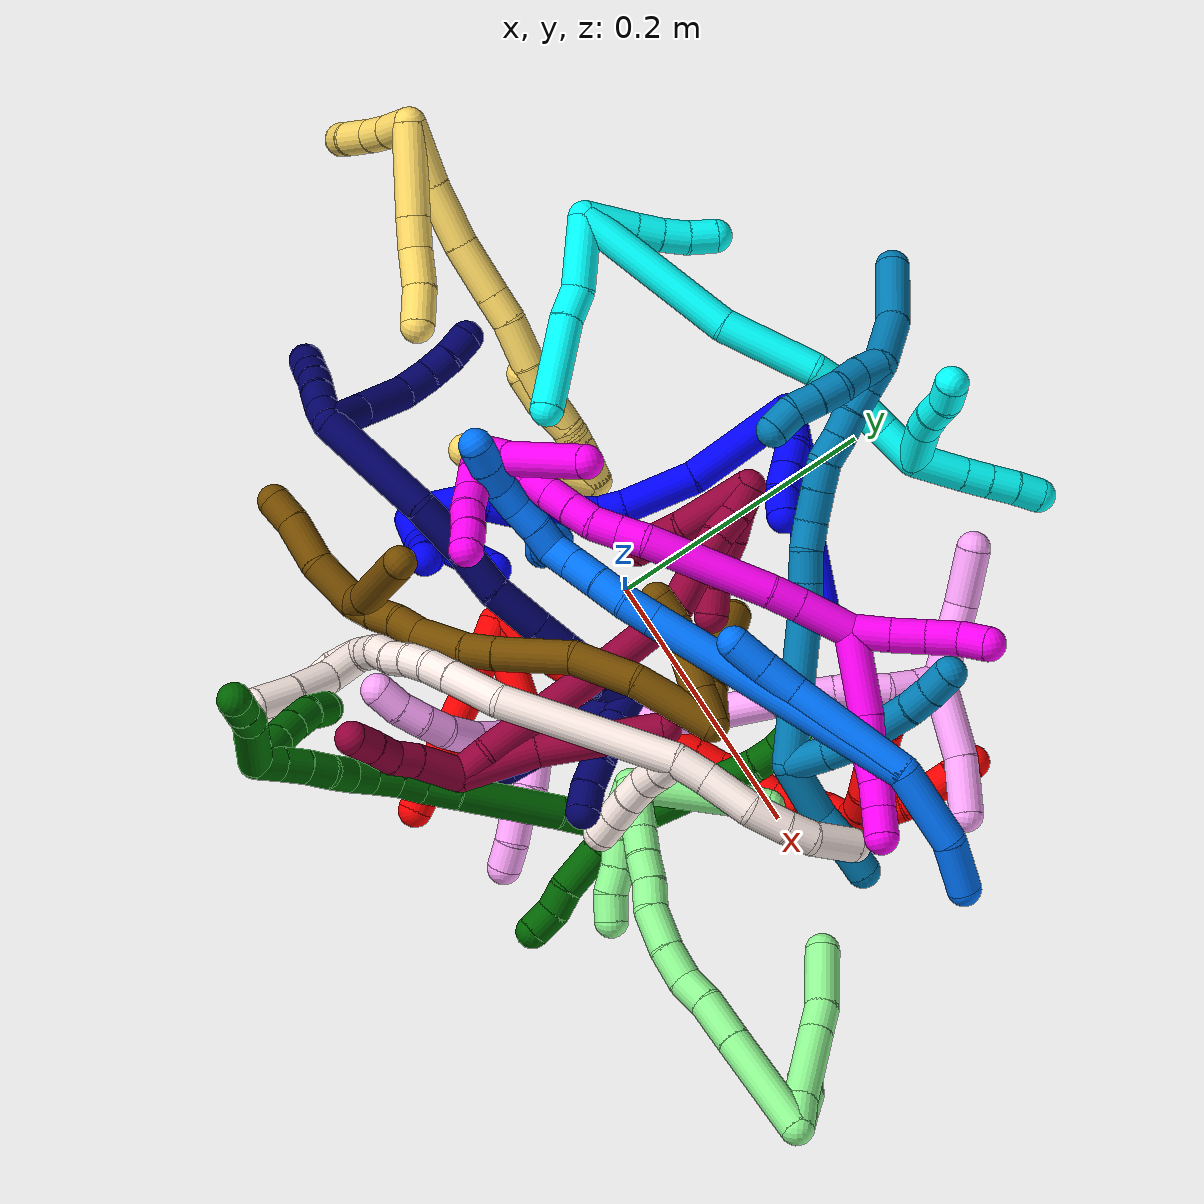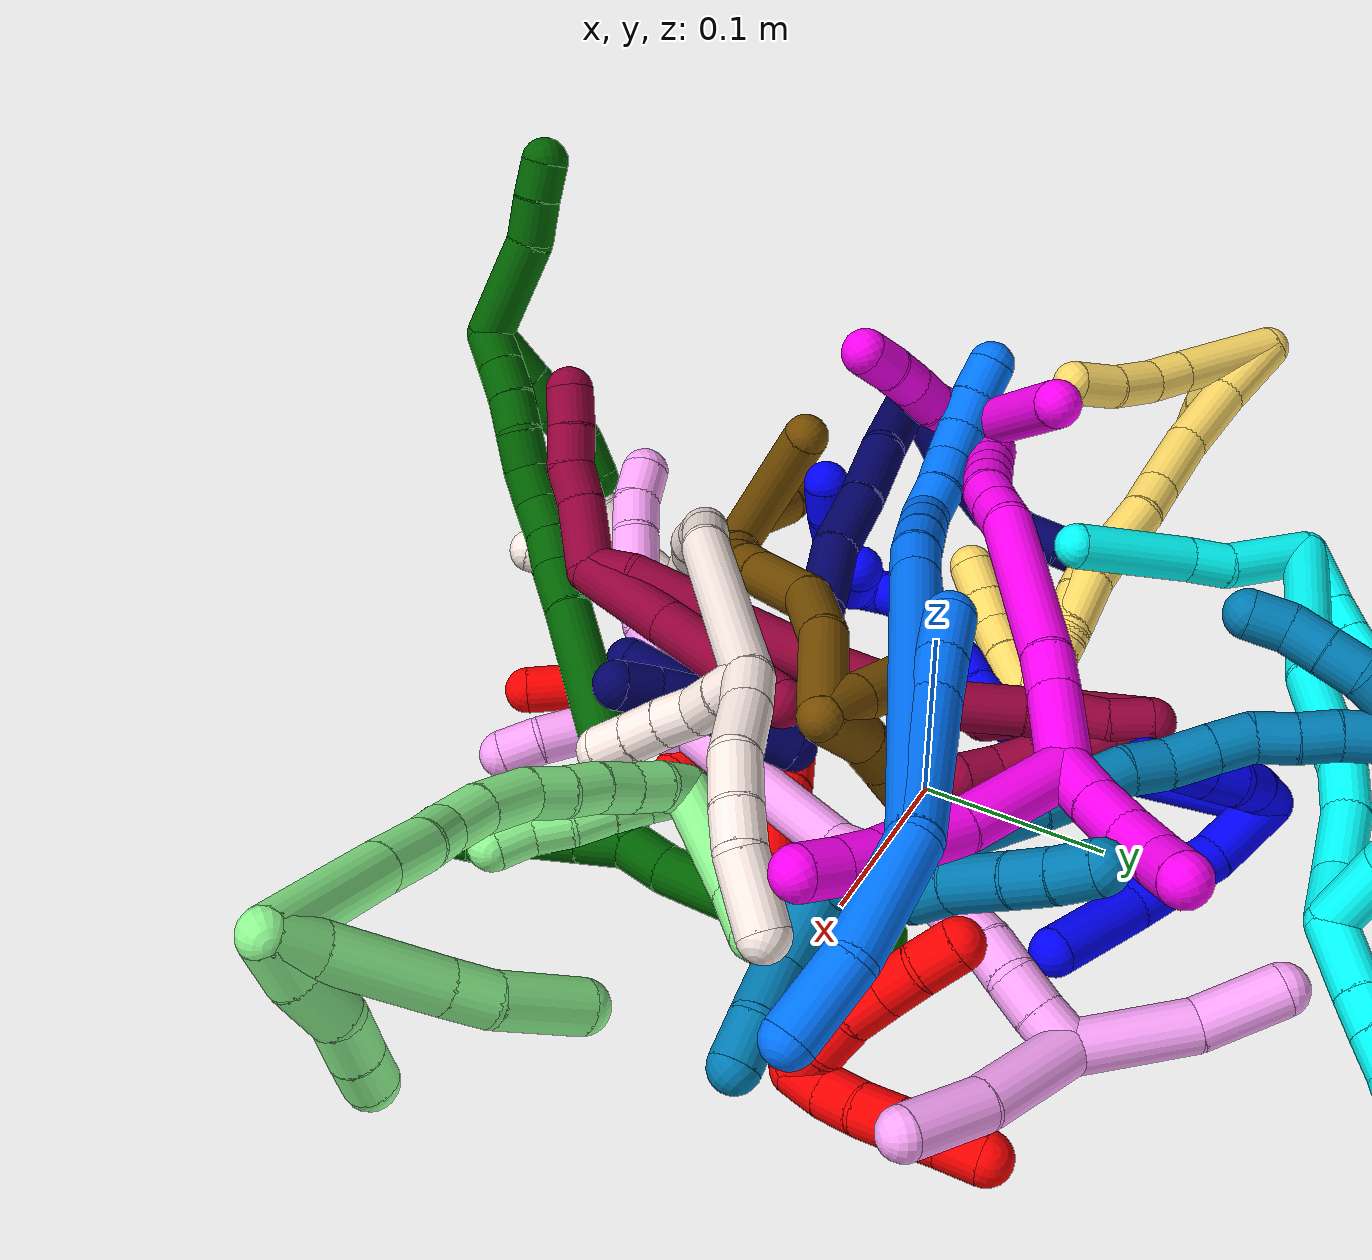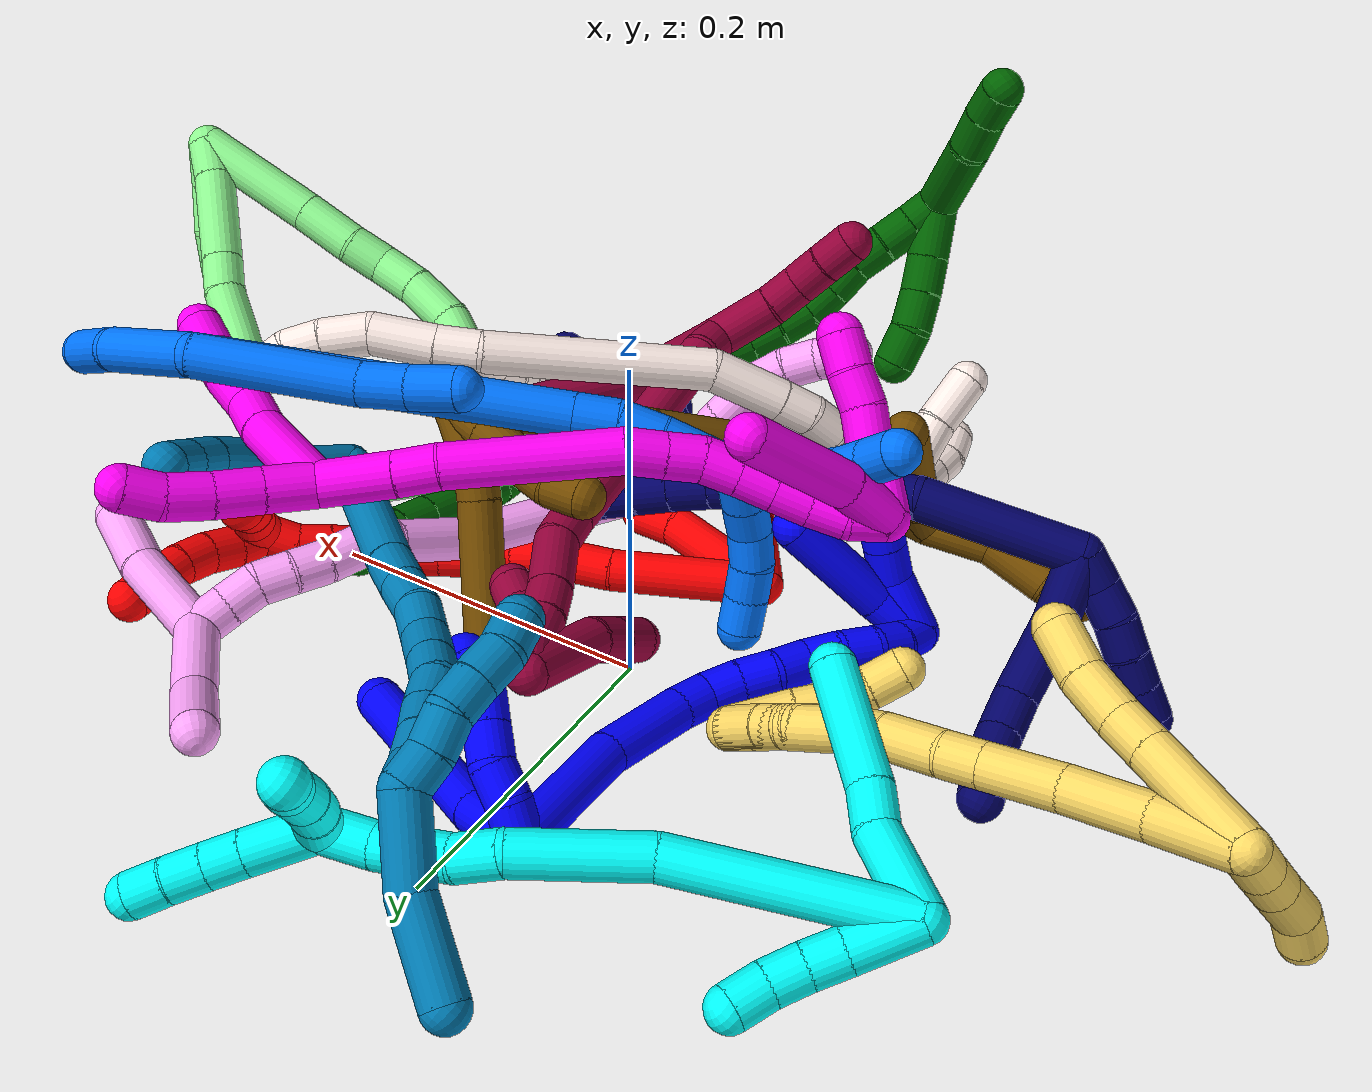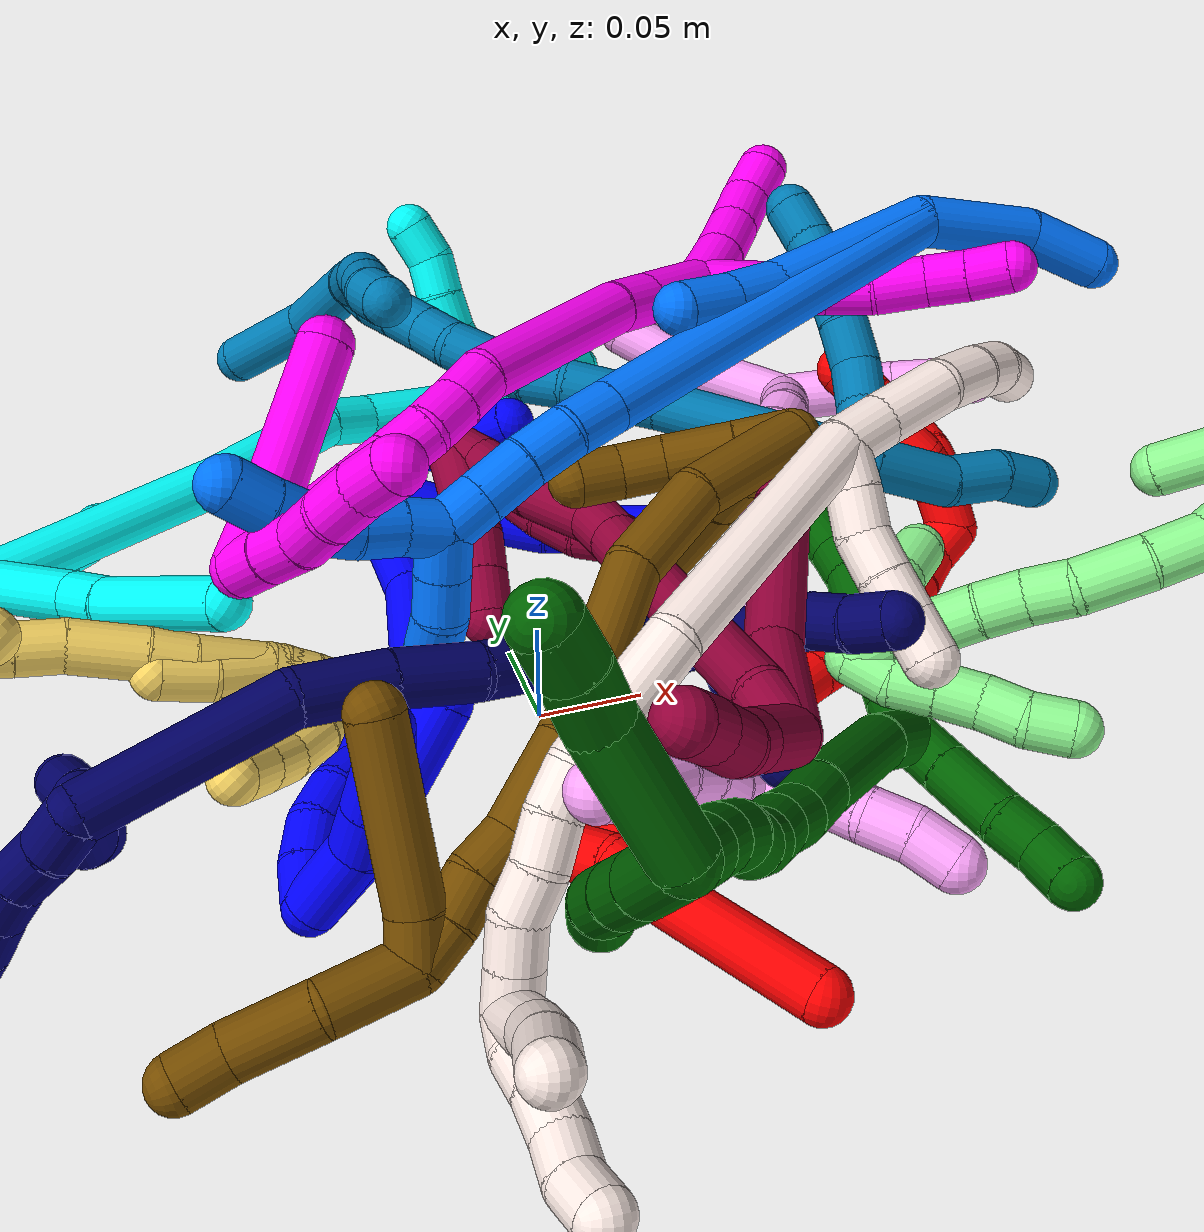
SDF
<sdf version="1.7">
 <world name="default">
  <plugin name="TubeGeneratorPlugin" filename="libtube_generator_plugin.so"/>
  <model name="photoneo_s_sensor">
   <static>1</static>
   <pose>0 0 2 1.57079 1.57079 3.14159</pose>
   <link name="link">
    <inertial><mass>0.1</mass></inertial>
    <sensor name="sensor" type="depth">
     <update_rate>30</update_rate>
     <camera>
      <horizontal_fov>1.22</horizontal_fov>
      <image><width>1920</width><height>1200</height><format>B8G8R8</format></image>
      <clip><near>0.1</near><far>4</far></clip>
      <depth_camera><output>points</output></depth_camera>
     </camera>
     <plugin name="camera_plugin" filename="libgazebo_ros_depth_camera.so">
      <baseline>0.2</baseline>
      <alwaysOn>1</alwaysOn>
      <updateRate>0.0</updateRate>
      <cameraName>camera_ir</cameraName>
      <imageTopicName>/camera/color/image_raw</imageTopicName>
      <cameraInfoTopicName>/camera/color/camera_info</cameraInfoTopicName>
      <depthImageTopicName>/camera/depth/image_raw</depthImageTopicName>
      <depthImageCameraInfoTopicName>/camera/depth/camera_info</depthImageCameraInfoTopicName>
      <pointCloudTopicName>/camera/depth/points</pointCloudTopicName>
      <frameName>fr_optical</frameName>
      <pointCloudCutoff>0.1</pointCloudCutoff>
      <pointCloudCutoffMax>2.0</pointCloudCutoffMax>
      <distortionK1>0</distortionK1>
      <distortionK2>0</distortionK2>
      <distortionK3>0</distortionK3>
      <distortionT1>0</distortionT1>
      <distortionT2>0</distortionT2>
      <CxPrime>0</CxPrime>
      <Cx>0</Cx>
      <Cy>0</Cy>
      <focalLength>0</focalLength>
      <hackBaseline>0</hackBaseline>
     </plugin>
    </sensor>
   </link>
  </model>
  <gravity>0 0 -9.8</gravity>
  <magnetic_field>6e-06 2.3e-05 -4.2e-05</magnetic_field>
  <atmosphere type="adiabatic"/>
  <physics name="default_physics" default="0" type="ode">
   <max_step_size>0.003</max_step_size>
   <real_time_factor>1</real_time_factor>
   <real_time_update_rate>1000</real_time_update_rate>
   <max_contacts>10000</max_contacts>
   <ode>
    <solver>
     <type>quick</type>
     <iters>100</iters>
     <sor>1.3</sor>
     <use_dynamic_moi_rescaling>0</use_dynamic_moi_rescaling>
    </solver>
    <constraints>
     <contact_max_correcting_vel>0</contact_max_correcting_vel>
     <contact_surface_layer>0.001</contact_surface_layer>
     <cfm>0</cfm>
     <erp>0.2</erp>
    </constraints>
   </ode>
  </physics>
  <scene><ambient>0.4 0.4 0.4 1</ambient><background>0.7 0.7 0.7 1</background><shadows>0</shadows></scene>
  <audio><device>default</device></audio>
  <spherical_coordinates>
   <surface_model>EARTH_WGS84</surface_model>
   <latitude_deg>0</latitude_deg>
   <longitude_deg>0</longitude_deg>
   <elevation>0</elevation>
   <heading_deg>0</heading_deg>
  </spherical_coordinates>
  <model name="bin">
   <static>1</static>
   <link name="bottom">
    <collision name="collision-bottom">
     <pose>0 0 -0.01 0 -0 0</pose>
     <geometry><box><size>0.8 0.6 0.02</size></box></geometry>
     <surface>
      <friction><ode><mu>100</mu><mu2>100</mu2></ode></friction>
      <contact><collide_bitmask>65535</collide_bitmask></contact>
     </surface>
    </collision>
   </link>
   <link name="west_wall">
    <collision name="collision-west_wall">
     <pose>-0.41 0 0.1 0 -0 0</pose>
     <geometry><box><size>0.02 0.6 0.2</size></box></geometry>
     <surface>
      <friction><ode><mu>100</mu><mu2>100</mu2></ode></friction>
      <contact><collide_bitmask>65535</collide_bitmask></contact>
     </surface>
    </collision>
   </link>
   <link name="east_wall">
    <collision name="collision-east_wall">
     <pose>0.41 0 0.1 0 -0 0</pose>
     <geometry><box><size>0.02 0.6 0.2</size></box></geometry>
     <surface>
      <friction><ode><mu>100</mu><mu2>100</mu2></ode></friction>
      <contact><collide_bitmask>65535</collide_bitmask></contact>
     </surface>
    </collision>
   </link>
   <link name="south_wall">
    <collision name="collision-south_wall">
     <pose>0 -0.31 0.1 0 -0 0</pose>
     <geometry><box><size>0.8 0.02 0.2</size></box></geometry>
     <surface>
      <friction><ode><mu>100</mu><mu2>100</mu2></ode></friction>
      <contact><collide_bitmask>65535</collide_bitmask></contact>
     </surface>
    </collision>
   </link>
   <link name="north_wall">
    <collision name="collision-north_wall">
     <pose>0 0.31 0.1 0 -0 0</pose>
     <geometry><box><size>0.8 0.02 0.2</size></box></geometry>
     <surface>
      <friction><ode><mu>100</mu><mu2>100</mu2></ode></friction>
      <contact><collide_bitmask>65535</collide_bitmask></contact>
     </surface>
    </collision>
   </link>
  </model>
  <model name="1">
   <static>0</static>
   <link name="1">
    <collision name="collision-cylinder-e_1_2_8">
     <pose>0.019241 -0.009575 -0.001714 1.74798 1.10273 1.26752</pose>
     <geometry><cylinder><radius>0.0125</radius><length>0.043119</length></cylinder></geometry>
     <surface>
      <friction><ode><mu>1.16</mu><mu2>1.16</mu2><slip1>0</slip1><slip2>0</slip2></ode></friction>
      <contact><ode><kp>1e+06</kp><kd>1</kd><max_vel>0</max_vel><min_depth>0.001</min_depth></ode></contact>
     </surface>
    </collision>
    <visual name="visual-cylinder-e_1_2_8">
     <pose>0.019241 -0.009575 -0.001714 1.74798 1.10273 1.26752</pose>
     <geometry><cylinder><radius>0.0125</radius><length>0.043119</length></cylinder></geometry>
     <material><ambient>0 0 1 1</ambient></material>
    </visual>
    <collision name="collision-cylinder-e_2_8_9">
     <pose>0.060971 -0.03308 -0.000796 1.38398 1.00832 0.857646</pose>
     <geometry><cylinder><radius>0.0125</radius><length>0.053171</length></cylinder></geometry>
     <surface>
      <friction><ode><mu>1.16</mu><mu2>1.16</mu2><slip1>0</slip1><slip2>0</slip2></ode></friction>
      <contact><ode><kp>1e+06</kp><kd>1</kd><max_vel>0</max_vel><min_depth>0.001</min_depth></ode></contact>
     </surface>
    </collision>
    <visual name="visual-cylinder-e_2_8_9">
     <pose>0.060971 -0.03308 -0.000796 1.38398 1.00832 0.857646</pose>
     <geometry><cylinder><radius>0.0125</radius><length>0.053171</length></cylinder></geometry>
     <material><ambient>0 0 1 1</ambient></material>
    </visual>
    <collision name="collision-cylinder-e_3_9_6">
     <pose>0.106836 -0.058085 0.009056 0.993151 1.05613 0.612287</pose>
     <geometry><cylinder><radius>0.0125</radius><length>0.05371</length></cylinder></geometry>
     <surface>
      <friction><ode><mu>1.16</mu><mu2>1.16</mu2><slip1>0</slip1><slip2>0</slip2></ode></friction>
      <contact><ode><kp>1e+06</kp><kd>1</kd><max_vel>0</max_vel><min_depth>0.001</min_depth></ode></contact>
     </surface>
    </collision>
    <visual name="visual-cylinder-e_3_9_6">
     <pose>0.106836 -0.058085 0.009056 0.993151 1.05613 0.612287</pose>
     <geometry><cylinder><radius>0.0125</radius><length>0.05371</length></cylinder></geometry>
     <material><ambient>0 0 1 1</ambient></material>
    </visual>
    <collision name="collision-cylinder-e_1_2_10">
     <pose>0.003922 -0.001771 0.009026 0.193752 0.403073 0.039704</pose>
     <geometry><cylinder><radius>0.0125</radius><length>0.02</length></cylinder></geometry>
     <surface>
      <friction><ode><mu>1.16</mu><mu2>1.16</mu2><slip1>0</slip1><slip2>0</slip2></ode></friction>
      <contact><ode><kp>1e+06</kp><kd>1</kd><max_vel>0</max_vel><min_depth>0.001</min_depth></ode></contact>
     </surface>
    </collision>
    <visual name="visual-cylinder-e_1_2_10">
     <pose>0.003922 -0.001771 0.009026 0.193752 0.403073 0.039704</pose>
     <geometry><cylinder><radius>0.0125</radius><length>0.02</length></cylinder></geometry>
     <material><ambient>0 0 1 1</ambient></material>
    </visual>
    <collision name="collision-cylinder-e_2_10_11">
     <pose>0.013864 -0.006253 0.025565 0.34631 0.64585 0.116927</pose>
     <geometry><cylinder><radius>0.0125</radius><length>0.02</length></cylinder></geometry>
     <surface>
      <friction><ode><mu>1.16</mu><mu2>1.16</mu2><slip1>0</slip1><slip2>0</slip2></ode></friction>
      <contact><ode><kp>1e+06</kp><kd>1</kd><max_vel>0</max_vel><min_depth>0.001</min_depth></ode></contact>
     </surface>
    </collision>
    <visual name="visual-cylinder-e_2_10_11">
     <pose>0.013864 -0.006253 0.025565 0.34631 0.64585 0.116927</pose>
     <geometry><cylinder><radius>0.0125</radius><length>0.02</length></cylinder></geometry>
     <material><ambient>0 0 1 1</ambient></material>
    </visual>
    <collision name="collision-cylinder-e_3_11_12">
     <pose>0.024659 -0.014739 0.039697 0.717335 0.497993 0.190071</pose>
     <geometry><cylinder><radius>0.0125</radius><length>0.02</length></cylinder></geometry>
     <surface>
      <friction><ode><mu>1.16</mu><mu2>1.16</mu2><slip1>0</slip1><slip2>0</slip2></ode></friction>
      <contact><ode><kp>1e+06</kp><kd>1</kd><max_vel>0</max_vel><min_depth>0.001</min_depth></ode></contact>
     </surface>
    </collision>
    <visual name="visual-cylinder-e_3_11_12">
     <pose>0.024659 -0.014739 0.039697 0.717335 0.497993 0.190071</pose>
     <geometry><cylinder><radius>0.0125</radius><length>0.02</length></cylinder></geometry>
     <material><ambient>0 0 1 1</ambient></material>
    </visual>
    <collision name="collision-cylinder-e_4_12_13">
     <pose>0.034115 -0.026331 0.052971 0.718393 0.486893 0.185983</pose>
     <geometry><cylinder><radius>0.0125</radius><length>0.02</length></cylinder></geometry>
     <surface>
      <friction><ode><mu>1.16</mu><mu2>1.16</mu2><slip1>0</slip1><slip2>0</slip2></ode></friction>
      <contact><ode><kp>1e+06</kp><kd>1</kd><max_vel>0</max_vel><min_depth>0.001</min_depth></ode></contact>
     </surface>
    </collision>
    <visual name="visual-cylinder-e_4_12_13">
     <pose>0.034115 -0.026331 0.052971 0.718393 0.486893 0.185983</pose>
     <geometry><cylinder><radius>0.0125</radius><length>0.02</length></cylinder></geometry>
     <material><ambient>0 0 1 1</ambient></material>
    </visual>
    <collision name="collision-cylinder-e_5_13_5">
     <pose>0.045497 -0.035807 0.06608 0.515722 0.734701 0.202285</pose>
     <geometry><cylinder><radius>0.0125</radius><length>0.02</length></cylinder></geometry>
     <surface>
      <friction><ode><mu>1.16</mu><mu2>1.16</mu2><slip1>0</slip1><slip2>0</slip2></ode></friction>
      <contact><ode><kp>1e+06</kp><kd>1</kd><max_vel>0</max_vel><min_depth>0.001</min_depth></ode></contact>
     </surface>
    </collision>
    <visual name="visual-cylinder-e_5_13_5">
     <pose>0.045497 -0.035807 0.06608 0.515722 0.734701 0.202285</pose>
     <geometry><cylinder><radius>0.0125</radius><length>0.02</length></cylinder></geometry>
     <material><ambient>0 0 1 1</ambient></material>
    </visual>
    <collision name="collision-cylinder-e_1_2_14">
     <pose>-0.00182 -0.041777 0.004111 1.47271 -0.043326 -0.039273</pose>
     <geometry><cylinder><radius>0.0125</radius><length>0.084037</length></cylinder></geometry>
     <surface>
      <friction><ode><mu>1.16</mu><mu2>1.16</mu2><slip1>0</slip1><slip2>0</slip2></ode></friction>
      <contact><ode><kp>1e+06</kp><kd>1</kd><max_vel>0</max_vel><min_depth>0.001</min_depth></ode></contact>
     </surface>
    </collision>
    <visual name="visual-cylinder-e_1_2_14">
     <pose>-0.00182 -0.041777 0.004111 1.47271 -0.043326 -0.039273</pose>
     <geometry><cylinder><radius>0.0125</radius><length>0.084037</length></cylinder></geometry>
     <material><ambient>0 0 1 1</ambient></material>
    </visual>
    <collision name="collision-cylinder-e_2_14_15">
     <pose>-0.010794 -0.109775 0.010285 1.49229 -0.265577 -0.245713</pose>
     <geometry><cylinder><radius>0.0125</radius><length>0.054513</length></cylinder></geometry>
     <surface>
      <friction><ode><mu>1.16</mu><mu2>1.16</mu2><slip1>0</slip1><slip2>0</slip2></ode></friction>
      <contact><ode><kp>1e+06</kp><kd>1</kd><max_vel>0</max_vel><min_depth>0.001</min_depth></ode></contact>
     </surface>
    </collision>
    <visual name="visual-cylinder-e_2_14_15">
     <pose>-0.010794 -0.109775 0.010285 1.49229 -0.265577 -0.245713</pose>
     <geometry><cylinder><radius>0.0125</radius><length>0.054513</length></cylinder></geometry>
     <material><ambient>0 0 1 1</ambient></material>
    </visual>
    <collision name="collision-cylinder-e_3_15_16">
     <pose>-0.021976 -0.145201 0.013353 1.46195 -0.410308 -0.36892</pose>
     <geometry><cylinder><radius>0.0125</radius><length>0.020198</length></cylinder></geometry>
     <surface>
      <friction><ode><mu>1.16</mu><mu2>1.16</mu2><slip1>0</slip1><slip2>0</slip2></ode></friction>
      <contact><ode><kp>1e+06</kp><kd>1</kd><max_vel>0</max_vel><min_depth>0.001</min_depth></ode></contact>
     </surface>
    </collision>
    <visual name="visual-cylinder-e_3_15_16">
     <pose>-0.021976 -0.145201 0.013353 1.46195 -0.410308 -0.36892</pose>
     <geometry><cylinder><radius>0.0125</radius><length>0.020198</length></cylinder></geometry>
     <material><ambient>0 0 1 1</ambient></material>
    </visual>
    <collision name="collision-cylinder-e_4_16_17">
     <pose>-0.032662 -0.161981 0.016485 1.29724 -0.702296 -0.541726</pose>
     <geometry><cylinder><radius>0.0125</radius><length>0.020612</length></cylinder></geometry>
     <surface>
      <friction><ode><mu>1.16</mu><mu2>1.16</mu2><slip1>0</slip1><slip2>0</slip2></ode></friction>
      <contact><ode><kp>1e+06</kp><kd>1</kd><max_vel>0</max_vel><min_depth>0.001</min_depth></ode></contact>
     </surface>
    </collision>
    <visual name="visual-cylinder-e_4_16_17">
     <pose>-0.032662 -0.161981 0.016485 1.29724 -0.702296 -0.541726</pose>
     <geometry><cylinder><radius>0.0125</radius><length>0.020612</length></cylinder></geometry>
     <material><ambient>0 0 1 1</ambient></material>
    </visual>
    <collision name="collision-cylinder-e_5_17_18">
     <pose>-0.046911 -0.176102 0.020276 1.3216 -0.843656 -0.671326</pose>
     <geometry><cylinder><radius>0.0125</radius><length>0.020323</length></cylinder></geometry>
     <surface>
      <friction><ode><mu>1.16</mu><mu2>1.16</mu2><slip1>0</slip1><slip2>0</slip2></ode></friction>
      <contact><ode><kp>1e+06</kp><kd>1</kd><max_vel>0</max_vel><min_depth>0.001</min_depth></ode></contact>
     </surface>
    </collision>
    <visual name="visual-cylinder-e_5_17_18">
     <pose>-0.046911 -0.176102 0.020276 1.3216 -0.843656 -0.671326</pose>
     <geometry><cylinder><radius>0.0125</radius><length>0.020323</length></cylinder></geometry>
     <material><ambient>0 0 1 1</ambient></material>
    </visual>
    <collision name="collision-cylinder-e_6_18_19">
     <pose>-0.060051 -0.191028 0.0225 1.50429 -0.583827 -0.548151</pose>
     <geometry><cylinder><radius>0.0125</radius><length>0.020131</length></cylinder></geometry>
     <surface>
      <friction><ode><mu>1.16</mu><mu2>1.16</mu2><slip1>0</slip1><slip2>0</slip2></ode></friction>
      <contact><ode><kp>1e+06</kp><kd>1</kd><max_vel>0</max_vel><min_depth>0.001</min_depth></ode></contact>
     </surface>
    </collision>
    <visual name="visual-cylinder-e_6_18_19">
     <pose>-0.060051 -0.191028 0.0225 1.50429 -0.583827 -0.548151</pose>
     <geometry><cylinder><radius>0.0125</radius><length>0.020131</length></cylinder></geometry>
     <material><ambient>0 0 1 1</ambient></material>
    </visual>
    <collision name="collision-cylinder-e_7_19_20">
     <pose>-0.073411 -0.20558 0.024631 1.32134 -0.886756 -0.707164</pose>
     <geometry><cylinder><radius>0.0125</radius><length>0.020158</length></cylinder></geometry>
     <surface>
      <friction><ode><mu>1.16</mu><mu2>1.16</mu2><slip1>0</slip1><slip2>0</slip2></ode></friction>
      <contact><ode><kp>1e+06</kp><kd>1</kd><max_vel>0</max_vel><min_depth>0.001</min_depth></ode></contact>
     </surface>
    </collision>
    <visual name="visual-cylinder-e_7_19_20">
     <pose>-0.073411 -0.20558 0.024631 1.32134 -0.886756 -0.707164</pose>
     <geometry><cylinder><radius>0.0125</radius><length>0.020158</length></cylinder></geometry>
     <material><ambient>0 0 1 1</ambient></material>
    </visual>
    <collision name="collision-cylinder-e_8_20_21">
     <pose>-0.08783 -0.219256 0.02581 1.62322 -0.721241 -0.756557</pose>
     <geometry><cylinder><radius>0.0125</radius><length>0.020013</length></cylinder></geometry>
     <surface>
      <friction><ode><mu>1.16</mu><mu2>1.16</mu2><slip1>0</slip1><slip2>0</slip2></ode></friction>
      <contact><ode><kp>1e+06</kp><kd>1</kd><max_vel>0</max_vel><min_depth>0.001</min_depth></ode></contact>
     </surface>
    </collision>
    <visual name="visual-cylinder-e_8_20_21">
     <pose>-0.08783 -0.219256 0.02581 1.62322 -0.721241 -0.756557</pose>
     <geometry><cylinder><radius>0.0125</radius><length>0.020013</length></cylinder></geometry>
     <material><ambient>0 0 1 1</ambient></material>
    </visual>
    <collision name="collision-cylinder-e_9_21_22">
     <pose>-0.098524 -0.235736 0.02372 1.7575 -0.420735 -0.504311</pose>
     <geometry><cylinder><radius>0.0125</radius><length>0.020014</length></cylinder></geometry>
     <surface>
      <friction><ode><mu>1.16</mu><mu2>1.16</mu2><slip1>0</slip1><slip2>0</slip2></ode></friction>
      <contact><ode><kp>1e+06</kp><kd>1</kd><max_vel>0</max_vel><min_depth>0.001</min_depth></ode></contact>
     </surface>
    </collision>
    <visual name="visual-cylinder-e_9_21_22">
     <pose>-0.098524 -0.235736 0.02372 1.7575 -0.420735 -0.504311</pose>
     <geometry><cylinder><radius>0.0125</radius><length>0.020014</length></cylinder></geometry>
     <material><ambient>0 0 1 1</ambient></material>
    </visual>
    <collision name="collision-cylinder-e_10_22_1">
     <pose>-0.104527 -0.254511 0.02147 1.62739 -0.192713 -0.203865</pose>
     <geometry><cylinder><radius>0.0125</radius><length>0.020001</length></cylinder></geometry>
     <surface>
      <friction><ode><mu>1.16</mu><mu2>1.16</mu2><slip1>0</slip1><slip2>0</slip2></ode></friction>
      <contact><ode><kp>1e+06</kp><kd>1</kd><max_vel>0</max_vel><min_depth>0.001</min_depth></ode></contact>
     </surface>
    </collision>
    <visual name="visual-cylinder-e_10_22_1">
     <pose>-0.104527 -0.254511 0.02147 1.62739 -0.192713 -0.203865</pose>
     <geometry><cylinder><radius>0.0125</radius><length>0.020001</length></cylinder></geometry>
     <material><ambient>0 0 1 1</ambient></material>
    </visual>
    <collision name="collision-cylinder-e_1_1_23">
     <pose>-0.098376 -0.263774 0.036585 -0.034197 0.475138 -0.008281</pose>
     <geometry><cylinder><radius>0.0125</radius><length>0.035266</length></cylinder></geometry>
     <surface>
      <friction><ode><mu>1.16</mu><mu2>1.16</mu2><slip1>0</slip1><slip2>0</slip2></ode></friction>
      <contact><ode><kp>1e+06</kp><kd>1</kd><max_vel>0</max_vel><min_depth>0.001</min_depth></ode></contact>
     </surface>
    </collision>
    <visual name="visual-cylinder-e_1_1_23">
     <pose>-0.098376 -0.263774 0.036585 -0.034197 0.475138 -0.008281</pose>
     <geometry><cylinder><radius>0.0125</radius><length>0.035266</length></cylinder></geometry>
     <material><ambient>0 0 1 1</ambient></material>
    </visual>
    <collision name="collision-cylinder-e_2_23_24">
     <pose>-0.088549 -0.261822 0.062863 -0.132751 0.163012 -0.01086</pose>
     <geometry><cylinder><radius>0.0125</radius><length>0.021692</length></cylinder></geometry>
     <surface>
      <friction><ode><mu>1.16</mu><mu2>1.16</mu2><slip1>0</slip1><slip2>0</slip2></ode></friction>
      <contact><ode><kp>1e+06</kp><kd>1</kd><max_vel>0</max_vel><min_depth>0.001</min_depth></ode></contact>
     </surface>
    </collision>
    <visual name="visual-cylinder-e_2_23_24">
     <pose>-0.088549 -0.261822 0.062863 -0.132751 0.163012 -0.01086</pose>
     <geometry><cylinder><radius>0.0125</radius><length>0.021692</length></cylinder></geometry>
     <material><ambient>0 0 1 1</ambient></material>
    </visual>
    <collision name="collision-cylinder-e_3_24_25">
     <pose>-0.084926 -0.258869 0.084627 -0.136833 0.163977 -0.011261</pose>
     <geometry><cylinder><radius>0.0125</radius><length>0.022829</length></cylinder></geometry>
     <surface>
      <friction><ode><mu>1.16</mu><mu2>1.16</mu2><slip1>0</slip1><slip2>0</slip2></ode></friction>
      <contact><ode><kp>1e+06</kp><kd>1</kd><max_vel>0</max_vel><min_depth>0.001</min_depth></ode></contact>
     </surface>
    </collision>
    <visual name="visual-cylinder-e_3_24_25">
     <pose>-0.084926 -0.258869 0.084627 -0.136833 0.163977 -0.011261</pose>
     <geometry><cylinder><radius>0.0125</radius><length>0.022829</length></cylinder></geometry>
     <material><ambient>0 0 1 1</ambient></material>
    </visual>
    <collision name="collision-cylinder-e_4_25_4">
     <pose>-0.084117 -0.256418 0.105793 -0.091153 -0.104523 0.004771</pose>
     <geometry><cylinder><radius>0.0125</radius><length>0.020214</length></cylinder></geometry>
     <surface>
      <friction><ode><mu>1.16</mu><mu2>1.16</mu2><slip1>0</slip1><slip2>0</slip2></ode></friction>
      <contact><ode><kp>1e+06</kp><kd>1</kd><max_vel>0</max_vel><min_depth>0.001</min_depth></ode></contact>
     </surface>
    </collision>
    <visual name="visual-cylinder-e_4_25_4">
     <pose>-0.084117 -0.256418 0.105793 -0.091153 -0.104523 0.004771</pose>
     <geometry><cylinder><radius>0.0125</radius><length>0.020214</length></cylinder></geometry>
     <material><ambient>0 0 1 1</ambient></material>
    </visual>
    <collision name="collision-cylinder-e_1_1_26">
     <pose>-0.095183 -0.259811 0.031297 -0.408898 0.782904 -0.170749</pose>
     <geometry><cylinder><radius>0.0125</radius><length>0.031925</length></cylinder></geometry>
     <surface>
      <friction><ode><mu>1.16</mu><mu2>1.16</mu2><slip1>0</slip1><slip2>0</slip2></ode></friction>
      <contact><ode><kp>1e+06</kp><kd>1</kd><max_vel>0</max_vel><min_depth>0.001</min_depth></ode></contact>
     </surface>
    </collision>
    <visual name="visual-cylinder-e_1_1_26">
     <pose>-0.095183 -0.259811 0.031297 -0.408898 0.782904 -0.170749</pose>
     <geometry><cylinder><radius>0.0125</radius><length>0.031925</length></cylinder></geometry>
     <material><ambient>0 0 1 1</ambient></material>
    </visual>
    <collision name="collision-cylinder-e_2_26_3">
     <pose>-0.065273 -0.240492 0.065991 -0.547447 0.579909 -0.167153</pose>
     <geometry><cylinder><radius>0.0125</radius><length>0.068075</length></cylinder></geometry>
     <surface>
      <friction><ode><mu>1.16</mu><mu2>1.16</mu2><slip1>0</slip1><slip2>0</slip2></ode></friction>
      <contact><ode><kp>1e+06</kp><kd>1</kd><max_vel>0</max_vel><min_depth>0.001</min_depth></ode></contact>
     </surface>
    </collision>
    <visual name="visual-cylinder-e_2_26_3">
     <pose>-0.065273 -0.240492 0.065991 -0.547447 0.579909 -0.167153</pose>
     <geometry><cylinder><radius>0.0125</radius><length>0.068075</length></cylinder></geometry>
     <material><ambient>0 0 1 1</ambient></material>
    </visual>
    <collision name="collision-sphere-3">
     <pose>-0.046622 -0.225672 0.090303 0 -0 0</pose>
     <geometry><sphere><radius>0.0125</radius></sphere></geometry>
     <surface>
      <friction><ode><mu>1.16</mu><mu2>1.16</mu2><slip1>0</slip1><slip2>0</slip2></ode></friction>
      <contact><ode><kp>1e+06</kp><kd>1</kd><max_vel>0</max_vel><min_depth>0.001</min_depth></ode></contact>
     </surface>
    </collision>
    <visual name="visual-sphere-3">
     <pose>-0.046622 -0.225672 0.090303 0 -0 0</pose>
     <geometry><sphere><radius>0.0125</radius></sphere></geometry>
     <material><ambient>0 0 1 1</ambient></material>
    </visual>
    <collision name="collision-sphere-26">
     <pose>-0.083924 -0.255312 0.04168 0 -0 0</pose>
     <geometry><sphere><radius>0.0125</radius></sphere></geometry>
     <surface>
      <friction><ode><mu>1.16</mu><mu2>1.16</mu2><slip1>0</slip1><slip2>0</slip2></ode></friction>
      <contact><ode><kp>1e+06</kp><kd>1</kd><max_vel>0</max_vel><min_depth>0.001</min_depth></ode></contact>
     </surface>
    </collision>
    <visual name="visual-sphere-26">
     <pose>-0.083924 -0.255312 0.04168 0 -0 0</pose>
     <geometry><sphere><radius>0.0125</radius></sphere></geometry>
     <material><ambient>0 0 1 1</ambient></material>
    </visual>
    <collision name="collision-sphere-4">
     <pose>-0.085171 -0.255503 0.115803 0 -0 0</pose>
     <geometry><sphere><radius>0.0125</radius></sphere></geometry>
     <surface>
      <friction><ode><mu>1.16</mu><mu2>1.16</mu2><slip1>0</slip1><slip2>0</slip2></ode></friction>
      <contact><ode><kp>1e+06</kp><kd>1</kd><max_vel>0</max_vel><min_depth>0.001</min_depth></ode></contact>
     </surface>
    </collision>
    <visual name="visual-sphere-4">
     <pose>-0.085171 -0.255503 0.115803 0 -0 0</pose>
     <geometry><sphere><radius>0.0125</radius></sphere></geometry>
     <material><ambient>0 0 1 1</ambient></material>
    </visual>
    <collision name="collision-sphere-25">
     <pose>-0.083062 -0.257333 0.095783 0 -0 0</pose>
     <geometry><sphere><radius>0.0125</radius></sphere></geometry>
     <surface>
      <friction><ode><mu>1.16</mu><mu2>1.16</mu2><slip1>0</slip1><slip2>0</slip2></ode></friction>
      <contact><ode><kp>1e+06</kp><kd>1</kd><max_vel>0</max_vel><min_depth>0.001</min_depth></ode></contact>
     </surface>
    </collision>
    <visual name="visual-sphere-25">
     <pose>-0.083062 -0.257333 0.095783 0 -0 0</pose>
     <geometry><sphere><radius>0.0125</radius></sphere></geometry>
     <material><ambient>0 0 1 1</ambient></material>
    </visual>
    <collision name="collision-sphere-24">
     <pose>-0.086789 -0.260405 0.073471 0 -0 0</pose>
     <geometry><sphere><radius>0.0125</radius></sphere></geometry>
     <surface>
      <friction><ode><mu>1.16</mu><mu2>1.16</mu2><slip1>0</slip1><slip2>0</slip2></ode></friction>
      <contact><ode><kp>1e+06</kp><kd>1</kd><max_vel>0</max_vel><min_depth>0.001</min_depth></ode></contact>
     </surface>
    </collision>
    <visual name="visual-sphere-24">
     <pose>-0.086789 -0.260405 0.073471 0 -0 0</pose>
     <geometry><sphere><radius>0.0125</radius></sphere></geometry>
     <material><ambient>0 0 1 1</ambient></material>
    </visual>
    <collision name="collision-sphere-23">
     <pose>-0.090309 -0.263238 0.052255 0 -0 0</pose>
     <geometry><sphere><radius>0.0125</radius></sphere></geometry>
     <surface>
      <friction><ode><mu>1.16</mu><mu2>1.16</mu2><slip1>0</slip1><slip2>0</slip2></ode></friction>
      <contact><ode><kp>1e+06</kp><kd>1</kd><max_vel>0</max_vel><min_depth>0.001</min_depth></ode></contact>
     </surface>
    </collision>
    <visual name="visual-sphere-23">
     <pose>-0.090309 -0.263238 0.052255 0 -0 0</pose>
     <geometry><sphere><radius>0.0125</radius></sphere></geometry>
     <material><ambient>0 0 1 1</ambient></material>
    </visual>
    <collision name="collision-sphere-1">
     <pose>-0.106442 -0.26431 0.020914 0 -0 0</pose>
     <geometry><sphere><radius>0.0125</radius></sphere></geometry>
     <surface>
      <friction><ode><mu>1.16</mu><mu2>1.16</mu2><slip1>0</slip1><slip2>0</slip2></ode></friction>
      <contact><ode><kp>1e+06</kp><kd>1</kd><max_vel>0</max_vel><min_depth>0.001</min_depth></ode></contact>
     </surface>
    </collision>
    <visual name="visual-sphere-1">
     <pose>-0.106442 -0.26431 0.020914 0 -0 0</pose>
     <geometry><sphere><radius>0.0125</radius></sphere></geometry>
     <material><ambient>0 0 1 1</ambient></material>
    </visual>
    <collision name="collision-sphere-22">
     <pose>-0.102611 -0.244711 0.022025 0 -0 0</pose>
     <geometry><sphere><radius>0.0125</radius></sphere></geometry>
     <surface>
      <friction><ode><mu>1.16</mu><mu2>1.16</mu2><slip1>0</slip1><slip2>0</slip2></ode></friction>
      <contact><ode><kp>1e+06</kp><kd>1</kd><max_vel>0</max_vel><min_depth>0.001</min_depth></ode></contact>
     </surface>
    </collision>
    <visual name="visual-sphere-22">
     <pose>-0.102611 -0.244711 0.022025 0 -0 0</pose>
     <geometry><sphere><radius>0.0125</radius></sphere></geometry>
     <material><ambient>0 0 1 1</ambient></material>
    </visual>
    <collision name="collision-sphere-21">
     <pose>-0.094437 -0.226761 0.025416 0 -0 0</pose>
     <geometry><sphere><radius>0.0125</radius></sphere></geometry>
     <surface>
      <friction><ode><mu>1.16</mu><mu2>1.16</mu2><slip1>0</slip1><slip2>0</slip2></ode></friction>
      <contact><ode><kp>1e+06</kp><kd>1</kd><max_vel>0</max_vel><min_depth>0.001</min_depth></ode></contact>
     </surface>
    </collision>
    <visual name="visual-sphere-21">
     <pose>-0.094437 -0.226761 0.025416 0 -0 0</pose>
     <geometry><sphere><radius>0.0125</radius></sphere></geometry>
     <material><ambient>0 0 1 1</ambient></material>
    </visual>
    <collision name="collision-sphere-11">
     <pose>0.019882 -0.008964 0.033077 0 -0 0</pose>
     <geometry><sphere><radius>0.0125</radius></sphere></geometry>
     <surface>
      <friction><ode><mu>1.16</mu><mu2>1.16</mu2><slip1>0</slip1><slip2>0</slip2></ode></friction>
      <contact><ode><kp>1e+06</kp><kd>1</kd><max_vel>0</max_vel><min_depth>0.001</min_depth></ode></contact>
     </surface>
    </collision>
    <visual name="visual-sphere-11">
     <pose>0.019882 -0.008964 0.033077 0 -0 0</pose>
     <geometry><sphere><radius>0.0125</radius></sphere></geometry>
     <material><ambient>0 0 1 1</ambient></material>
    </visual>
    <collision name="collision-sphere-10">
     <pose>0.007845 -0.003542 0.018053 0 -0 0</pose>
     <geometry><sphere><radius>0.0125</radius></sphere></geometry>
     <surface>
      <friction><ode><mu>1.16</mu><mu2>1.16</mu2><slip1>0</slip1><slip2>0</slip2></ode></friction>
      <contact><ode><kp>1e+06</kp><kd>1</kd><max_vel>0</max_vel><min_depth>0.001</min_depth></ode></contact>
     </surface>
    </collision>
    <visual name="visual-sphere-10">
     <pose>0.007845 -0.003542 0.018053 0 -0 0</pose>
     <geometry><sphere><radius>0.0125</radius></sphere></geometry>
     <material><ambient>0 0 1 1</ambient></material>
    </visual>
    <collision name="collision-sphere-6">
     <pose>0.130213 -0.06916 0.016274 0 -0 0</pose>
     <geometry><sphere><radius>0.0125</radius></sphere></geometry>
     <surface>
      <friction><ode><mu>1.16</mu><mu2>1.16</mu2><slip1>0</slip1><slip2>0</slip2></ode></friction>
      <contact><ode><kp>1e+06</kp><kd>1</kd><max_vel>0</max_vel><min_depth>0.001</min_depth></ode></contact>
     </surface>
    </collision>
    <visual name="visual-sphere-6">
     <pose>0.130213 -0.06916 0.016274 0 -0 0</pose>
     <geometry><sphere><radius>0.0125</radius></sphere></geometry>
     <material><ambient>0 0 1 1</ambient></material>
    </visual>
    <collision name="collision-sphere-9">
     <pose>0.08346 -0.047011 0.001838 0 -0 0</pose>
     <geometry><sphere><radius>0.0125</radius></sphere></geometry>
     <surface>
      <friction><ode><mu>1.16</mu><mu2>1.16</mu2><slip1>0</slip1><slip2>0</slip2></ode></friction>
      <contact><ode><kp>1e+06</kp><kd>1</kd><max_vel>0</max_vel><min_depth>0.001</min_depth></ode></contact>
     </surface>
    </collision>
    <visual name="visual-sphere-9">
     <pose>0.08346 -0.047011 0.001838 0 -0 0</pose>
     <geometry><sphere><radius>0.0125</radius></sphere></geometry>
     <material><ambient>0 0 1 1</ambient></material>
    </visual>
    <collision name="collision-sphere-2">
     <geometry><sphere><radius>0.0125</radius></sphere></geometry>
     <surface>
      <friction><ode><mu>1.16</mu><mu2>1.16</mu2><slip1>0</slip1><slip2>0</slip2></ode></friction>
      <contact><ode><kp>1e+06</kp><kd>1</kd><max_vel>0</max_vel><min_depth>0.001</min_depth></ode></contact>
     </surface>
    </collision>
    <visual name="visual-sphere-2">
     <geometry><sphere><radius>0.0125</radius></sphere></geometry>
     <material><ambient>0 0 1 1</ambient></material>
    </visual>
    <collision name="collision-sphere-19">
     <pose>-0.065599 -0.199408 0.023058 0 -0 0</pose>
     <geometry><sphere><radius>0.0125</radius></sphere></geometry>
     <surface>
      <friction><ode><mu>1.16</mu><mu2>1.16</mu2><slip1>0</slip1><slip2>0</slip2></ode></friction>
      <contact><ode><kp>1e+06</kp><kd>1</kd><max_vel>0</max_vel><min_depth>0.001</min_depth></ode></contact>
     </surface>
    </collision>
    <visual name="visual-sphere-19">
     <pose>-0.065599 -0.199408 0.023058 0 -0 0</pose>
     <geometry><sphere><radius>0.0125</radius></sphere></geometry>
     <material><ambient>0 0 1 1</ambient></material>
    </visual>
    <collision name="collision-sphere-8">
     <pose>0.038481 -0.019149 -0.003429 0 -0 0</pose>
     <geometry><sphere><radius>0.0125</radius></sphere></geometry>
     <surface>
      <friction><ode><mu>1.16</mu><mu2>1.16</mu2><slip1>0</slip1><slip2>0</slip2></ode></friction>
      <contact><ode><kp>1e+06</kp><kd>1</kd><max_vel>0</max_vel><min_depth>0.001</min_depth></ode></contact>
     </surface>
    </collision>
    <visual name="visual-sphere-8">
     <pose>0.038481 -0.019149 -0.003429 0 -0 0</pose>
     <geometry><sphere><radius>0.0125</radius></sphere></geometry>
     <material><ambient>0 0 1 1</ambient></material>
    </visual>
    <collision name="collision-sphere-12">
     <pose>0.029436 -0.020514 0.046317 0 -0 0</pose>
     <geometry><sphere><radius>0.0125</radius></sphere></geometry>
     <surface>
      <friction><ode><mu>1.16</mu><mu2>1.16</mu2><slip1>0</slip1><slip2>0</slip2></ode></friction>
      <contact><ode><kp>1e+06</kp><kd>1</kd><max_vel>0</max_vel><min_depth>0.001</min_depth></ode></contact>
     </surface>
    </collision>
    <visual name="visual-sphere-12">
     <pose>0.029436 -0.020514 0.046317 0 -0 0</pose>
     <geometry><sphere><radius>0.0125</radius></sphere></geometry>
     <material><ambient>0 0 1 1</ambient></material>
    </visual>
    <collision name="collision-sphere-13">
     <pose>0.038793 -0.032148 0.059625 0 -0 0</pose>
     <geometry><sphere><radius>0.0125</radius></sphere></geometry>
     <surface>
      <friction><ode><mu>1.16</mu><mu2>1.16</mu2><slip1>0</slip1><slip2>0</slip2></ode></friction>
      <contact><ode><kp>1e+06</kp><kd>1</kd><max_vel>0</max_vel><min_depth>0.001</min_depth></ode></contact>
     </surface>
    </collision>
    <visual name="visual-sphere-13">
     <pose>0.038793 -0.032148 0.059625 0 -0 0</pose>
     <geometry><sphere><radius>0.0125</radius></sphere></geometry>
     <material><ambient>0 0 1 1</ambient></material>
    </visual>
    <collision name="collision-sphere-5">
     <pose>0.052201 -0.039467 0.072535 0 -0 0</pose>
     <geometry><sphere><radius>0.0125</radius></sphere></geometry>
     <surface>
      <friction><ode><mu>1.16</mu><mu2>1.16</mu2><slip1>0</slip1><slip2>0</slip2></ode></friction>
      <contact><ode><kp>1e+06</kp><kd>1</kd><max_vel>0</max_vel><min_depth>0.001</min_depth></ode></contact>
     </surface>
    </collision>
    <visual name="visual-sphere-5">
     <pose>0.052201 -0.039467 0.072535 0 -0 0</pose>
     <geometry><sphere><radius>0.0125</radius></sphere></geometry>
     <material><ambient>0 0 1 1</ambient></material>
    </visual>
    <collision name="collision-sphere-14">
     <pose>-0.00364 -0.083555 0.008222 0 -0 0</pose>
     <geometry><sphere><radius>0.0125</radius></sphere></geometry>
     <surface>
      <friction><ode><mu>1.16</mu><mu2>1.16</mu2><slip1>0</slip1><slip2>0</slip2></ode></friction>
      <contact><ode><kp>1e+06</kp><kd>1</kd><max_vel>0</max_vel><min_depth>0.001</min_depth></ode></contact>
     </surface>
    </collision>
    <visual name="visual-sphere-14">
     <pose>-0.00364 -0.083555 0.008222 0 -0 0</pose>
     <geometry><sphere><radius>0.0125</radius></sphere></geometry>
     <material><ambient>0 0 1 1</ambient></material>
    </visual>
    <collision name="collision-sphere-15">
     <pose>-0.017948 -0.135994 0.012347 0 -0 0</pose>
     <geometry><sphere><radius>0.0125</radius></sphere></geometry>
     <surface>
      <friction><ode><mu>1.16</mu><mu2>1.16</mu2><slip1>0</slip1><slip2>0</slip2></ode></friction>
      <contact><ode><kp>1e+06</kp><kd>1</kd><max_vel>0</max_vel><min_depth>0.001</min_depth></ode></contact>
     </surface>
    </collision>
    <visual name="visual-sphere-15">
     <pose>-0.017948 -0.135994 0.012347 0 -0 0</pose>
     <geometry><sphere><radius>0.0125</radius></sphere></geometry>
     <material><ambient>0 0 1 1</ambient></material>
    </visual>
    <collision name="collision-sphere-16">
     <pose>-0.026005 -0.154407 0.01436 0 -0 0</pose>
     <geometry><sphere><radius>0.0125</radius></sphere></geometry>
     <surface>
      <friction><ode><mu>1.16</mu><mu2>1.16</mu2><slip1>0</slip1><slip2>0</slip2></ode></friction>
      <contact><ode><kp>1e+06</kp><kd>1</kd><max_vel>0</max_vel><min_depth>0.001</min_depth></ode></contact>
     </surface>
    </collision>
    <visual name="visual-sphere-16">
     <pose>-0.026005 -0.154407 0.01436 0 -0 0</pose>
     <geometry><sphere><radius>0.0125</radius></sphere></geometry>
     <material><ambient>0 0 1 1</ambient></material>
    </visual>
    <collision name="collision-sphere-17">
     <pose>-0.03932 -0.169556 0.01861 0 -0 0</pose>
     <geometry><sphere><radius>0.0125</radius></sphere></geometry>
     <surface>
      <friction><ode><mu>1.16</mu><mu2>1.16</mu2><slip1>0</slip1><slip2>0</slip2></ode></friction>
      <contact><ode><kp>1e+06</kp><kd>1</kd><max_vel>0</max_vel><min_depth>0.001</min_depth></ode></contact>
     </surface>
    </collision>
    <visual name="visual-sphere-17">
     <pose>-0.03932 -0.169556 0.01861 0 -0 0</pose>
     <geometry><sphere><radius>0.0125</radius></sphere></geometry>
     <material><ambient>0 0 1 1</ambient></material>
    </visual>
    <collision name="collision-sphere-18">
     <pose>-0.054502 -0.182648 0.021942 0 -0 0</pose>
     <geometry><sphere><radius>0.0125</radius></sphere></geometry>
     <surface>
      <friction><ode><mu>1.16</mu><mu2>1.16</mu2><slip1>0</slip1><slip2>0</slip2></ode></friction>
      <contact><ode><kp>1e+06</kp><kd>1</kd><max_vel>0</max_vel><min_depth>0.001</min_depth></ode></contact>
     </surface>
    </collision>
    <visual name="visual-sphere-18">
     <pose>-0.054502 -0.182648 0.021942 0 -0 0</pose>
     <geometry><sphere><radius>0.0125</radius></sphere></geometry>
     <material><ambient>0 0 1 1</ambient></material>
    </visual>
    <collision name="collision-sphere-20">
     <pose>-0.081222 -0.211752 0.026203 0 -0 0</pose>
     <geometry><sphere><radius>0.0125</radius></sphere></geometry>
     <surface>
      <friction><ode><mu>1.16</mu><mu2>1.16</mu2><slip1>0</slip1><slip2>0</slip2></ode></friction>
      <contact><ode><kp>1e+06</kp><kd>1</kd><max_vel>0</max_vel><min_depth>0.001</min_depth></ode></contact>
     </surface>
    </collision>
    <visual name="visual-sphere-20">
     <pose>-0.081222 -0.211752 0.026203 0 -0 0</pose>
     <geometry><sphere><radius>0.0125</radius></sphere></geometry>
     <material><ambient>0 0 1 1</ambient></material>
    </visual>
    <inertial>
     <pose>-0.020775 -0.132349 0.027667 0 -0 0</pose>
     <mass>0.75</mass>
     <inertia><ixx>0.000142</ixx><ixy>0</ixy><ixz>0</ixz><iyy>6.3e-05</iyy><iyz>0</iyz><izz>5.9e-05</izz></inertia>
    </inertial>
   </link>
   <pose>-0.042888 0.169311 0.030376 0.203232 0.130867 0.090913</pose>
  </model>
  <model name="2">
   <static>0</static>
   <link name="2">
    <collision name="collision-cylinder-e_1_2_8">
     <pose>0.01522 -0.01593 0.002915 1.38982 0.754379 0.63794</pose>
     <geometry><cylinder><radius>0.0125</radius><length>0.044449</length></cylinder></geometry>
     <surface>
      <friction><ode><mu>1.16</mu><mu2>1.16</mu2><slip1>0</slip1><slip2>0</slip2></ode></friction>
      <contact><ode><kp>1e+06</kp><kd>1</kd><max_vel>0</max_vel><min_depth>0.001</min_depth></ode></contact>
     </surface>
    </collision>
    <visual name="visual-cylinder-e_1_2_8">
     <pose>0.01522 -0.01593 0.002915 1.38982 0.754379 0.63794</pose>
     <geometry><cylinder><radius>0.0125</radius><length>0.044449</length></cylinder></geometry>
     <material><ambient>1 0 0 1</ambient></material>
    </visual>
    <collision name="collision-cylinder-e_2_8_6">
     <pose>0.069043 -0.066851 -0.002583 1.80676 0.820439 1.00853</pose>
     <geometry><cylinder><radius>0.0125</radius><length>0.105551</length></cylinder></geometry>
     <surface>
      <friction><ode><mu>1.16</mu><mu2>1.16</mu2><slip1>0</slip1><slip2>0</slip2></ode></friction>
      <contact><ode><kp>1e+06</kp><kd>1</kd><max_vel>0</max_vel><min_depth>0.001</min_depth></ode></contact>
     </surface>
    </collision>
    <visual name="visual-cylinder-e_2_8_6">
     <pose>0.069043 -0.066851 -0.002583 1.80676 0.820439 1.00853</pose>
     <geometry><cylinder><radius>0.0125</radius><length>0.105551</length></cylinder></geometry>
     <material><ambient>1 0 0 1</ambient></material>
    </visual>
    <collision name="collision-cylinder-e_1_2_9">
     <pose>0.034478 -0.003744 0.009129 0.389211 1.29206 0.295053</pose>
     <geometry><cylinder><radius>0.0125</radius><length>0.071724</length></cylinder></geometry>
     <surface>
      <friction><ode><mu>1.16</mu><mu2>1.16</mu2><slip1>0</slip1><slip2>0</slip2></ode></friction>
      <contact><ode><kp>1e+06</kp><kd>1</kd><max_vel>0</max_vel><min_depth>0.001</min_depth></ode></contact>
     </surface>
    </collision>
    <visual name="visual-cylinder-e_1_2_9">
     <pose>0.034478 -0.003744 0.009129 0.389211 1.29206 0.295053</pose>
     <geometry><cylinder><radius>0.0125</radius><length>0.071724</length></cylinder></geometry>
     <material><ambient>1 0 0 1</ambient></material>
    </visual>
    <collision name="collision-cylinder-e_2_9_5">
     <pose>0.082903 -0.006641 0.020413 -0.374673 1.40624 -0.318632</pose>
     <geometry><cylinder><radius>0.0125</radius><length>0.028276</length></cylinder></geometry>
     <surface>
      <friction><ode><mu>1.16</mu><mu2>1.16</mu2><slip1>0</slip1><slip2>0</slip2></ode></friction>
      <contact><ode><kp>1e+06</kp><kd>1</kd><max_vel>0</max_vel><min_depth>0.001</min_depth></ode></contact>
     </surface>
    </collision>
    <visual name="visual-cylinder-e_2_9_5">
     <pose>0.082903 -0.006641 0.020413 -0.374673 1.40624 -0.318632</pose>
     <geometry><cylinder><radius>0.0125</radius><length>0.028276</length></cylinder></geometry>
     <material><ambient>1 0 0 1</ambient></material>
    </visual>
    <collision name="collision-cylinder-e_1_2_10">
     <pose>0.033174 0.022372 0.019674 -0.849489 0.839062 -0.398097</pose>
     <geometry><cylinder><radius>0.0125</radius><length>0.089176</length></cylinder></geometry>
     <surface>
      <friction><ode><mu>1.16</mu><mu2>1.16</mu2><slip1>0</slip1><slip2>0</slip2></ode></friction>
      <contact><ode><kp>1e+06</kp><kd>1</kd><max_vel>0</max_vel><min_depth>0.001</min_depth></ode></contact>
     </surface>
    </collision>
    <visual name="visual-cylinder-e_1_2_10">
     <pose>0.033174 0.022372 0.019674 -0.849489 0.839062 -0.398097</pose>
     <geometry><cylinder><radius>0.0125</radius><length>0.089176</length></cylinder></geometry>
     <material><ambient>1 0 0 1</ambient></material>
    </visual>
    <collision name="collision-cylinder-e_2_10_11">
     <pose>0.081058 0.051475 0.046997 -0.721603 0.964974 -0.390232</pose>
     <geometry><cylinder><radius>0.0125</radius><length>0.035787</length></cylinder></geometry>
     <surface>
      <friction><ode><mu>1.16</mu><mu2>1.16</mu2><slip1>0</slip1><slip2>0</slip2></ode></friction>
      <contact><ode><kp>1e+06</kp><kd>1</kd><max_vel>0</max_vel><min_depth>0.001</min_depth></ode></contact>
     </surface>
    </collision>
    <visual name="visual-cylinder-e_2_10_11">
     <pose>0.081058 0.051475 0.046997 -0.721603 0.964974 -0.390232</pose>
     <geometry><cylinder><radius>0.0125</radius><length>0.035787</length></cylinder></geometry>
     <material><ambient>1 0 0 1</ambient></material>
    </visual>
    <collision name="collision-cylinder-e_3_11_12">
     <pose>0.105467 0.065073 0.059328 -0.972381 0.86241 -0.477051</pose>
     <geometry><cylinder><radius>0.0125</radius><length>0.025548</length></cylinder></geometry>
     <surface>
      <friction><ode><mu>1.16</mu><mu2>1.16</mu2><slip1>0</slip1><slip2>0</slip2></ode></friction>
      <contact><ode><kp>1e+06</kp><kd>1</kd><max_vel>0</max_vel><min_depth>0.001</min_depth></ode></contact>
     </surface>
    </collision>
    <visual name="visual-cylinder-e_3_11_12">
     <pose>0.105467 0.065073 0.059328 -0.972381 0.86241 -0.477051</pose>
     <geometry><cylinder><radius>0.0125</radius><length>0.025548</length></cylinder></geometry>
     <material><ambient>1 0 0 1</ambient></material>
    </visual>
    <collision name="collision-cylinder-e_4_12_13">
     <pose>0.123113 0.078761 0.068881 -0.95066 0.758645 -0.404722</pose>
     <geometry><cylinder><radius>0.0125</radius><length>0.023099</length></cylinder></geometry>
     <surface>
      <friction><ode><mu>1.16</mu><mu2>1.16</mu2><slip1>0</slip1><slip2>0</slip2></ode></friction>
      <contact><ode><kp>1e+06</kp><kd>1</kd><max_vel>0</max_vel><min_depth>0.001</min_depth></ode></contact>
     </surface>
    </collision>
    <visual name="visual-cylinder-e_4_12_13">
     <pose>0.123113 0.078761 0.068881 -0.95066 0.758645 -0.404722</pose>
     <geometry><cylinder><radius>0.0125</radius><length>0.023099</length></cylinder></geometry>
     <material><ambient>1 0 0 1</ambient></material>
    </visual>
    <collision name="collision-cylinder-e_5_13_14">
     <pose>0.138473 0.091218 0.077972 -0.928109 0.811229 -0.423423</pose>
     <geometry><cylinder><radius>0.0125</radius><length>0.02045</length></cylinder></geometry>
     <surface>
      <friction><ode><mu>1.16</mu><mu2>1.16</mu2><slip1>0</slip1><slip2>0</slip2></ode></friction>
      <contact><ode><kp>1e+06</kp><kd>1</kd><max_vel>0</max_vel><min_depth>0.001</min_depth></ode></contact>
     </surface>
    </collision>
    <visual name="visual-cylinder-e_5_13_14">
     <pose>0.138473 0.091218 0.077972 -0.928109 0.811229 -0.423423</pose>
     <geometry><cylinder><radius>0.0125</radius><length>0.02045</length></cylinder></geometry>
     <material><ambient>1 0 0 1</ambient></material>
    </visual>
    <collision name="collision-cylinder-e_6_14_15">
     <pose>0.153466 0.104371 0.088498 -0.872818 0.657713 -0.315669</pose>
     <geometry><cylinder><radius>0.0125</radius><length>0.024795</length></cylinder></geometry>
     <surface>
      <friction><ode><mu>1.16</mu><mu2>1.16</mu2><slip1>0</slip1><slip2>0</slip2></ode></friction>
      <contact><ode><kp>1e+06</kp><kd>1</kd><max_vel>0</max_vel><min_depth>0.001</min_depth></ode></contact>
     </surface>
    </collision>
    <visual name="visual-cylinder-e_6_14_15">
     <pose>0.153466 0.104371 0.088498 -0.872818 0.657713 -0.315669</pose>
     <geometry><cylinder><radius>0.0125</radius><length>0.024795</length></cylinder></geometry>
     <material><ambient>1 0 0 1</ambient></material>
    </visual>
    <collision name="collision-cylinder-e_7_15_16">
     <pose>0.168466 0.116557 0.100332 -0.701251 0.797994 -0.305988</pose>
     <geometry><cylinder><radius>0.0125</radius><length>0.020732</length></cylinder></geometry>
     <surface>
      <friction><ode><mu>1.16</mu><mu2>1.16</mu2><slip1>0</slip1><slip2>0</slip2></ode></friction>
      <contact><ode><kp>1e+06</kp><kd>1</kd><max_vel>0</max_vel><min_depth>0.001</min_depth></ode></contact>
     </surface>
    </collision>
    <visual name="visual-cylinder-e_7_15_16">
     <pose>0.168466 0.116557 0.100332 -0.701251 0.797994 -0.305988</pose>
     <geometry><cylinder><radius>0.0125</radius><length>0.020732</length></cylinder></geometry>
     <material><ambient>1 0 0 1</ambient></material>
    </visual>
    <collision name="collision-cylinder-e_8_16_17">
     <pose>0.181007 0.127344 0.1122 -0.767627 0.526464 -0.216805</pose>
     <geometry><cylinder><radius>0.0125</radius><length>0.020378</length></cylinder></geometry>
     <surface>
      <friction><ode><mu>1.16</mu><mu2>1.16</mu2><slip1>0</slip1><slip2>0</slip2></ode></friction>
      <contact><ode><kp>1e+06</kp><kd>1</kd><max_vel>0</max_vel><min_depth>0.001</min_depth></ode></contact>
     </surface>
    </collision>
    <visual name="visual-cylinder-e_8_16_17">
     <pose>0.181007 0.127344 0.1122 -0.767627 0.526464 -0.216805</pose>
     <geometry><cylinder><radius>0.0125</radius><length>0.020378</length></cylinder></geometry>
     <material><ambient>1 0 0 1</ambient></material>
    </visual>
    <collision name="collision-cylinder-e_9_17_18">
     <pose>0.190429 0.140067 0.124712 -0.819265 0.444085 -0.195428</pose>
     <geometry><cylinder><radius>0.0125</radius><length>0.020023</length></cylinder></geometry>
     <surface>
      <friction><ode><mu>1.16</mu><mu2>1.16</mu2><slip1>0</slip1><slip2>0</slip2></ode></friction>
      <contact><ode><kp>1e+06</kp><kd>1</kd><max_vel>0</max_vel><min_depth>0.001</min_depth></ode></contact>
     </surface>
    </collision>
    <visual name="visual-cylinder-e_9_17_18">
     <pose>0.190429 0.140067 0.124712 -0.819265 0.444085 -0.195428</pose>
     <geometry><cylinder><radius>0.0125</radius><length>0.020023</length></cylinder></geometry>
     <material><ambient>1 0 0 1</ambient></material>
    </visual>
    <collision name="collision-cylinder-e_10_18_1">
     <pose>0.200292 0.150528 0.138255 -0.482059 0.589347 -0.148934</pose>
     <geometry><cylinder><radius>0.0125</radius><length>0.020012</length></cylinder></geometry>
     <surface>
      <friction><ode><mu>1.16</mu><mu2>1.16</mu2><slip1>0</slip1><slip2>0</slip2></ode></friction>
      <contact><ode><kp>1e+06</kp><kd>1</kd><max_vel>0</max_vel><min_depth>0.001</min_depth></ode></contact>
     </surface>
    </collision>
    <visual name="visual-cylinder-e_10_18_1">
     <pose>0.200292 0.150528 0.138255 -0.482059 0.589347 -0.148934</pose>
     <geometry><cylinder><radius>0.0125</radius><length>0.020012</length></cylinder></geometry>
     <material><ambient>1 0 0 1</ambient></material>
    </visual>
    <collision name="collision-cylinder-e_1_1_19">
     <pose>0.20097 0.155446 0.154287 -0.121892 -0.510116 0.031819</pose>
     <geometry><cylinder><radius>0.0125</radius><length>0.02</length></cylinder></geometry>
     <surface>
      <friction><ode><mu>1.16</mu><mu2>1.16</mu2><slip1>0</slip1><slip2>0</slip2></ode></friction>
      <contact><ode><kp>1e+06</kp><kd>1</kd><max_vel>0</max_vel><min_depth>0.001</min_depth></ode></contact>
     </surface>
    </collision>
    <visual name="visual-cylinder-e_1_1_19">
     <pose>0.20097 0.155446 0.154287 -0.121892 -0.510116 0.031819</pose>
     <geometry><cylinder><radius>0.0125</radius><length>0.02</length></cylinder></geometry>
     <material><ambient>1 0 0 1</ambient></material>
    </visual>
    <collision name="collision-cylinder-e_2_19_20">
     <pose>0.189297 0.156826 0.170283 -0.043403 -0.746533 0.017</pose>
     <geometry><cylinder><radius>0.0125</radius><length>0.02</length></cylinder></geometry>
     <surface>
      <friction><ode><mu>1.16</mu><mu2>1.16</mu2><slip1>0</slip1><slip2>0</slip2></ode></friction>
      <contact><ode><kp>1e+06</kp><kd>1</kd><max_vel>0</max_vel><min_depth>0.001</min_depth></ode></contact>
     </surface>
    </collision>
    <visual name="visual-cylinder-e_2_19_20">
     <pose>0.189297 0.156826 0.170283 -0.043403 -0.746533 0.017</pose>
     <geometry><cylinder><radius>0.0125</radius><length>0.02</length></cylinder></geometry>
     <material><ambient>1 0 0 1</ambient></material>
    </visual>
    <collision name="collision-cylinder-e_3_20_21">
     <pose>0.174318 0.159295 0.182939 -0.384041 -0.95933 0.201579</pose>
     <geometry><cylinder><radius>0.0125</radius><length>0.02</length></cylinder></geometry>
     <surface>
      <friction><ode><mu>1.16</mu><mu2>1.16</mu2><slip1>0</slip1><slip2>0</slip2></ode></friction>
      <contact><ode><kp>1e+06</kp><kd>1</kd><max_vel>0</max_vel><min_depth>0.001</min_depth></ode></contact>
     </surface>
    </collision>
    <visual name="visual-cylinder-e_3_20_21">
     <pose>0.174318 0.159295 0.182939 -0.384041 -0.95933 0.201579</pose>
     <geometry><cylinder><radius>0.0125</radius><length>0.02</length></cylinder></geometry>
     <material><ambient>1 0 0 1</ambient></material>
    </visual>
    <collision name="collision-cylinder-e_4_21_22">
     <pose>0.159322 0.163708 0.195229 -0.313913 -0.748758 0.124202</pose>
     <geometry><cylinder><radius>0.0125</radius><length>0.02</length></cylinder></geometry>
     <surface>
      <friction><ode><mu>1.16</mu><mu2>1.16</mu2><slip1>0</slip1><slip2>0</slip2></ode></friction>
      <contact><ode><kp>1e+06</kp><kd>1</kd><max_vel>0</max_vel><min_depth>0.001</min_depth></ode></contact>
     </surface>
    </collision>
    <visual name="visual-cylinder-e_4_21_22">
     <pose>0.159322 0.163708 0.195229 -0.313913 -0.748758 0.124202</pose>
     <geometry><cylinder><radius>0.0125</radius><length>0.02</length></cylinder></geometry>
     <material><ambient>1 0 0 1</ambient></material>
    </visual>
    <collision name="collision-cylinder-e_5_22_4">
     <pose>0.144407 0.168652 0.2074 -0.475934 -0.945429 0.246825</pose>
     <geometry><cylinder><radius>0.0125</radius><length>0.02</length></cylinder></geometry>
     <surface>
      <friction><ode><mu>1.16</mu><mu2>1.16</mu2><slip1>0</slip1><slip2>0</slip2></ode></friction>
      <contact><ode><kp>1e+06</kp><kd>1</kd><max_vel>0</max_vel><min_depth>0.001</min_depth></ode></contact>
     </surface>
    </collision>
    <visual name="visual-cylinder-e_5_22_4">
     <pose>0.144407 0.168652 0.2074 -0.475934 -0.945429 0.246825</pose>
     <geometry><cylinder><radius>0.0125</radius><length>0.02</length></cylinder></geometry>
     <material><ambient>1 0 0 1</ambient></material>
    </visual>
    <collision name="collision-cylinder-e_1_1_23">
     <pose>0.206053 0.16339 0.149969 -1.12139 0.019968 -0.012538</pose>
     <geometry><cylinder><radius>0.0125</radius><length>0.02</length></cylinder></geometry>
     <surface>
      <friction><ode><mu>1.16</mu><mu2>1.16</mu2><slip1>0</slip1><slip2>0</slip2></ode></friction>
      <contact><ode><kp>1e+06</kp><kd>1</kd><max_vel>0</max_vel><min_depth>0.001</min_depth></ode></contact>
     </surface>
    </collision>
    <visual name="visual-cylinder-e_1_1_23">
     <pose>0.206053 0.16339 0.149969 -1.12139 0.019968 -0.012538</pose>
     <geometry><cylinder><radius>0.0125</radius><length>0.02</length></cylinder></geometry>
     <material><ambient>1 0 0 1</ambient></material>
    </visual>
    <collision name="collision-cylinder-e_2_23_24">
     <pose>0.205714 0.180293 0.160422 -0.912311 -0.053886 0.026445</pose>
     <geometry><cylinder><radius>0.0125</radius><length>0.02</length></cylinder></geometry>
     <surface>
      <friction><ode><mu>1.16</mu><mu2>1.16</mu2><slip1>0</slip1><slip2>0</slip2></ode></friction>
      <contact><ode><kp>1e+06</kp><kd>1</kd><max_vel>0</max_vel><min_depth>0.001</min_depth></ode></contact>
     </surface>
    </collision>
    <visual name="visual-cylinder-e_2_23_24">
     <pose>0.205714 0.180293 0.160422 -0.912311 -0.053886 0.026445</pose>
     <geometry><cylinder><radius>0.0125</radius><length>0.02</length></cylinder></geometry>
     <material><ambient>1 0 0 1</ambient></material>
    </visual>
    <collision name="collision-cylinder-e_3_24_25">
     <pose>0.203248 0.196579 0.171624 -1.02522 -0.193967 0.109397</pose>
     <geometry><cylinder><radius>0.0125</radius><length>0.02</length></cylinder></geometry>
     <surface>
      <friction><ode><mu>1.16</mu><mu2>1.16</mu2><slip1>0</slip1><slip2>0</slip2></ode></friction>
      <contact><ode><kp>1e+06</kp><kd>1</kd><max_vel>0</max_vel><min_depth>0.001</min_depth></ode></contact>
     </surface>
    </collision>
    <visual name="visual-cylinder-e_3_24_25">
     <pose>0.203248 0.196579 0.171624 -1.02522 -0.193967 0.109397</pose>
     <geometry><cylinder><radius>0.0125</radius><length>0.02</length></cylinder></geometry>
     <material><ambient>1 0 0 1</ambient></material>
    </visual>
    <collision name="collision-cylinder-e_4_25_26">
     <pose>0.198505 0.213754 0.18057 -1.15751 -0.285394 0.187201</pose>
     <geometry><cylinder><radius>0.0125</radius><length>0.02</length></cylinder></geometry>
     <surface>
      <friction><ode><mu>1.16</mu><mu2>1.16</mu2><slip1>0</slip1><slip2>0</slip2></ode></friction>
      <contact><ode><kp>1e+06</kp><kd>1</kd><max_vel>0</max_vel><min_depth>0.001</min_depth></ode></contact>
     </surface>
    </collision>
    <visual name="visual-cylinder-e_4_25_26">
     <pose>0.198505 0.213754 0.18057 -1.15751 -0.285394 0.187201</pose>
     <geometry><cylinder><radius>0.0125</radius><length>0.02</length></cylinder></geometry>
     <material><ambient>1 0 0 1</ambient></material>
    </visual>
    <collision name="collision-cylinder-e_5_26_3">
     <pose>0.19313 0.231544 0.187947 -1.19773 -0.258859 0.177191</pose>
     <geometry><cylinder><radius>0.0125</radius><length>0.02</length></cylinder></geometry>
     <surface>
      <friction><ode><mu>1.16</mu><mu2>1.16</mu2><slip1>0</slip1><slip2>0</slip2></ode></friction>
      <contact><ode><kp>1e+06</kp><kd>1</kd><max_vel>0</max_vel><min_depth>0.001</min_depth></ode></contact>
     </surface>
    </collision>
    <visual name="visual-cylinder-e_5_26_3">
     <pose>0.19313 0.231544 0.187947 -1.19773 -0.258859 0.177191</pose>
     <geometry><cylinder><radius>0.0125</radius><length>0.02</length></cylinder></geometry>
     <material><ambient>1 0 0 1</ambient></material>
    </visual>
    <collision name="collision-sphere-3">
     <pose>0.19057 0.240546 0.19147 0 -0 0</pose>
     <geometry><sphere><radius>0.0125</radius></sphere></geometry>
     <surface>
      <friction><ode><mu>1.16</mu><mu2>1.16</mu2><slip1>0</slip1><slip2>0</slip2></ode></friction>
      <contact><ode><kp>1e+06</kp><kd>1</kd><max_vel>0</max_vel><min_depth>0.001</min_depth></ode></contact>
     </surface>
    </collision>
    <visual name="visual-sphere-3">
     <pose>0.19057 0.240546 0.19147 0 -0 0</pose>
     <geometry><sphere><radius>0.0125</radius></sphere></geometry>
     <material><ambient>1 0 0 1</ambient></material>
    </visual>
    <collision name="collision-sphere-26">
     <pose>0.19569 0.222542 0.184424 0 -0 0</pose>
     <geometry><sphere><radius>0.0125</radius></sphere></geometry>
     <surface>
      <friction><ode><mu>1.16</mu><mu2>1.16</mu2><slip1>0</slip1><slip2>0</slip2></ode></friction>
      <contact><ode><kp>1e+06</kp><kd>1</kd><max_vel>0</max_vel><min_depth>0.001</min_depth></ode></contact>
     </surface>
    </collision>
    <visual name="visual-sphere-26">
     <pose>0.19569 0.222542 0.184424 0 -0 0</pose>
     <geometry><sphere><radius>0.0125</radius></sphere></geometry>
     <material><ambient>1 0 0 1</ambient></material>
    </visual>
    <collision name="collision-sphere-25">
     <pose>0.20132 0.204967 0.176716 0 -0 0</pose>
     <geometry><sphere><radius>0.0125</radius></sphere></geometry>
     <surface>
      <friction><ode><mu>1.16</mu><mu2>1.16</mu2><slip1>0</slip1><slip2>0</slip2></ode></friction>
      <contact><ode><kp>1e+06</kp><kd>1</kd><max_vel>0</max_vel><min_depth>0.001</min_depth></ode></contact>
     </surface>
    </collision>
    <visual name="visual-sphere-25">
     <pose>0.20132 0.204967 0.176716 0 -0 0</pose>
     <geometry><sphere><radius>0.0125</radius></sphere></geometry>
     <material><ambient>1 0 0 1</ambient></material>
    </visual>
    <collision name="collision-sphere-24">
     <pose>0.205175 0.188191 0.166533 0 -0 0</pose>
     <geometry><sphere><radius>0.0125</radius></sphere></geometry>
     <surface>
      <friction><ode><mu>1.16</mu><mu2>1.16</mu2><slip1>0</slip1><slip2>0</slip2></ode></friction>
      <contact><ode><kp>1e+06</kp><kd>1</kd><max_vel>0</max_vel><min_depth>0.001</min_depth></ode></contact>
     </surface>
    </collision>
    <visual name="visual-sphere-24">
     <pose>0.205175 0.188191 0.166533 0 -0 0</pose>
     <geometry><sphere><radius>0.0125</radius></sphere></geometry>
     <material><ambient>1 0 0 1</ambient></material>
    </visual>
    <collision name="collision-sphere-23">
     <pose>0.206253 0.172395 0.154312 0 -0 0</pose>
     <geometry><sphere><radius>0.0125</radius></sphere></geometry>
     <surface>
      <friction><ode><mu>1.16</mu><mu2>1.16</mu2><slip1>0</slip1><slip2>0</slip2></ode></friction>
      <contact><ode><kp>1e+06</kp><kd>1</kd><max_vel>0</max_vel><min_depth>0.001</min_depth></ode></contact>
     </surface>
    </collision>
    <visual name="visual-sphere-23">
     <pose>0.206253 0.172395 0.154312 0 -0 0</pose>
     <geometry><sphere><radius>0.0125</radius></sphere></geometry>
     <material><ambient>1 0 0 1</ambient></material>
    </visual>
    <collision name="collision-sphere-4">
     <pose>0.1363 0.171334 0.212603 0 -0 0</pose>
     <geometry><sphere><radius>0.0125</radius></sphere></geometry>
     <surface>
      <friction><ode><mu>1.16</mu><mu2>1.16</mu2><slip1>0</slip1><slip2>0</slip2></ode></friction>
      <contact><ode><kp>1e+06</kp><kd>1</kd><max_vel>0</max_vel><min_depth>0.001</min_depth></ode></contact>
     </surface>
    </collision>
    <visual name="visual-sphere-4">
     <pose>0.1363 0.171334 0.212603 0 -0 0</pose>
     <geometry><sphere><radius>0.0125</radius></sphere></geometry>
     <material><ambient>1 0 0 1</ambient></material>
    </visual>
    <collision name="collision-sphere-22">
     <pose>0.152515 0.16597 0.202196 0 -0 0</pose>
     <geometry><sphere><radius>0.0125</radius></sphere></geometry>
     <surface>
      <friction><ode><mu>1.16</mu><mu2>1.16</mu2><slip1>0</slip1><slip2>0</slip2></ode></friction>
      <contact><ode><kp>1e+06</kp><kd>1</kd><max_vel>0</max_vel><min_depth>0.001</min_depth></ode></contact>
     </surface>
    </collision>
    <visual name="visual-sphere-22">
     <pose>0.152515 0.16597 0.202196 0 -0 0</pose>
     <geometry><sphere><radius>0.0125</radius></sphere></geometry>
     <material><ambient>1 0 0 1</ambient></material>
    </visual>
    <collision name="collision-sphere-21">
     <pose>0.16613 0.161446 0.188261 0 -0 0</pose>
     <geometry><sphere><radius>0.0125</radius></sphere></geometry>
     <surface>
      <friction><ode><mu>1.16</mu><mu2>1.16</mu2><slip1>0</slip1><slip2>0</slip2></ode></friction>
      <contact><ode><kp>1e+06</kp><kd>1</kd><max_vel>0</max_vel><min_depth>0.001</min_depth></ode></contact>
     </surface>
    </collision>
    <visual name="visual-sphere-21">
     <pose>0.16613 0.161446 0.188261 0 -0 0</pose>
     <geometry><sphere><radius>0.0125</radius></sphere></geometry>
     <material><ambient>1 0 0 1</ambient></material>
    </visual>
    <collision name="collision-sphere-20">
     <pose>0.182506 0.157144 0.177616 0 -0 0</pose>
     <geometry><sphere><radius>0.0125</radius></sphere></geometry>
     <surface>
      <friction><ode><mu>1.16</mu><mu2>1.16</mu2><slip1>0</slip1><slip2>0</slip2></ode></friction>
      <contact><ode><kp>1e+06</kp><kd>1</kd><max_vel>0</max_vel><min_depth>0.001</min_depth></ode></contact>
     </surface>
    </collision>
    <visual name="visual-sphere-20">
     <pose>0.182506 0.157144 0.177616 0 -0 0</pose>
     <geometry><sphere><radius>0.0125</radius></sphere></geometry>
     <material><ambient>1 0 0 1</ambient></material>
    </visual>
    <collision name="collision-sphere-10">
     <pose>0.066348 0.044744 0.039347 0 -0 0</pose>
     <geometry><sphere><radius>0.0125</radius></sphere></geometry>
     <surface>
      <friction><ode><mu>1.16</mu><mu2>1.16</mu2><slip1>0</slip1><slip2>0</slip2></ode></friction>
      <contact><ode><kp>1e+06</kp><kd>1</kd><max_vel>0</max_vel><min_depth>0.001</min_depth></ode></contact>
     </surface>
    </collision>
    <visual name="visual-sphere-10">
     <pose>0.066348 0.044744 0.039347 0 -0 0</pose>
     <geometry><sphere><radius>0.0125</radius></sphere></geometry>
     <material><ambient>1 0 0 1</ambient></material>
    </visual>
    <collision name="collision-sphere-5">
     <pose>0.09685 -0.005793 0.022569 0 -0 0</pose>
     <geometry><sphere><radius>0.0125</radius></sphere></geometry>
     <surface>
      <friction><ode><mu>1.16</mu><mu2>1.16</mu2><slip1>0</slip1><slip2>0</slip2></ode></friction>
      <contact><ode><kp>1e+06</kp><kd>1</kd><max_vel>0</max_vel><min_depth>0.001</min_depth></ode></contact>
     </surface>
    </collision>
    <visual name="visual-sphere-5">
     <pose>0.09685 -0.005793 0.022569 0 -0 0</pose>
     <geometry><sphere><radius>0.0125</radius></sphere></geometry>
     <material><ambient>1 0 0 1</ambient></material>
    </visual>
    <collision name="collision-sphere-6">
     <pose>0.107645 -0.101842 -0.010996 0 -0 0</pose>
     <geometry><sphere><radius>0.0125</radius></sphere></geometry>
     <surface>
      <friction><ode><mu>1.16</mu><mu2>1.16</mu2><slip1>0</slip1><slip2>0</slip2></ode></friction>
      <contact><ode><kp>1e+06</kp><kd>1</kd><max_vel>0</max_vel><min_depth>0.001</min_depth></ode></contact>
     </surface>
    </collision>
    <visual name="visual-sphere-6">
     <pose>0.107645 -0.101842 -0.010996 0 -0 0</pose>
     <geometry><sphere><radius>0.0125</radius></sphere></geometry>
     <material><ambient>1 0 0 1</ambient></material>
    </visual>
    <collision name="collision-sphere-9">
     <pose>0.068956 -0.007488 0.018258 0 -0 0</pose>
     <geometry><sphere><radius>0.0125</radius></sphere></geometry>
     <surface>
      <friction><ode><mu>1.16</mu><mu2>1.16</mu2><slip1>0</slip1><slip2>0</slip2></ode></friction>
      <contact><ode><kp>1e+06</kp><kd>1</kd><max_vel>0</max_vel><min_depth>0.001</min_depth></ode></contact>
     </surface>
    </collision>
    <visual name="visual-sphere-9">
     <pose>0.068956 -0.007488 0.018258 0 -0 0</pose>
     <geometry><sphere><radius>0.0125</radius></sphere></geometry>
     <material><ambient>1 0 0 1</ambient></material>
    </visual>
    <collision name="collision-sphere-2">
     <geometry><sphere><radius>0.0125</radius></sphere></geometry>
     <surface>
      <friction><ode><mu>1.16</mu><mu2>1.16</mu2><slip1>0</slip1><slip2>0</slip2></ode></friction>
      <contact><ode><kp>1e+06</kp><kd>1</kd><max_vel>0</max_vel><min_depth>0.001</min_depth></ode></contact>
     </surface>
    </collision>
    <visual name="visual-sphere-2">
     <geometry><sphere><radius>0.0125</radius></sphere></geometry>
     <material><ambient>1 0 0 1</ambient></material>
    </visual>
    <collision name="collision-sphere-19">
     <pose>0.196088 0.156507 0.162949 0 -0 0</pose>
     <geometry><sphere><radius>0.0125</radius></sphere></geometry>
     <surface>
      <friction><ode><mu>1.16</mu><mu2>1.16</mu2><slip1>0</slip1><slip2>0</slip2></ode></friction>
      <contact><ode><kp>1e+06</kp><kd>1</kd><max_vel>0</max_vel><min_depth>0.001</min_depth></ode></contact>
     </surface>
    </collision>
    <visual name="visual-sphere-19">
     <pose>0.196088 0.156507 0.162949 0 -0 0</pose>
     <geometry><sphere><radius>0.0125</radius></sphere></geometry>
     <material><ambient>1 0 0 1</ambient></material>
    </visual>
    <collision name="collision-sphere-8">
     <pose>0.03044 -0.031861 0.00583 0 -0 0</pose>
     <geometry><sphere><radius>0.0125</radius></sphere></geometry>
     <surface>
      <friction><ode><mu>1.16</mu><mu2>1.16</mu2><slip1>0</slip1><slip2>0</slip2></ode></friction>
      <contact><ode><kp>1e+06</kp><kd>1</kd><max_vel>0</max_vel><min_depth>0.001</min_depth></ode></contact>
     </surface>
    </collision>
    <visual name="visual-sphere-8">
     <pose>0.03044 -0.031861 0.00583 0 -0 0</pose>
     <geometry><sphere><radius>0.0125</radius></sphere></geometry>
     <material><ambient>1 0 0 1</ambient></material>
    </visual>
    <collision name="collision-sphere-11">
     <pose>0.095767 0.058206 0.054646 0 -0 0</pose>
     <geometry><sphere><radius>0.0125</radius></sphere></geometry>
     <surface>
      <friction><ode><mu>1.16</mu><mu2>1.16</mu2><slip1>0</slip1><slip2>0</slip2></ode></friction>
      <contact><ode><kp>1e+06</kp><kd>1</kd><max_vel>0</max_vel><min_depth>0.001</min_depth></ode></contact>
     </surface>
    </collision>
    <visual name="visual-sphere-11">
     <pose>0.095767 0.058206 0.054646 0 -0 0</pose>
     <geometry><sphere><radius>0.0125</radius></sphere></geometry>
     <material><ambient>1 0 0 1</ambient></material>
    </visual>
    <collision name="collision-sphere-12">
     <pose>0.115168 0.071939 0.06401 0 -0 0</pose>
     <geometry><sphere><radius>0.0125</radius></sphere></geometry>
     <surface>
      <friction><ode><mu>1.16</mu><mu2>1.16</mu2><slip1>0</slip1><slip2>0</slip2></ode></friction>
      <contact><ode><kp>1e+06</kp><kd>1</kd><max_vel>0</max_vel><min_depth>0.001</min_depth></ode></contact>
     </surface>
    </collision>
    <visual name="visual-sphere-12">
     <pose>0.115168 0.071939 0.06401 0 -0 0</pose>
     <geometry><sphere><radius>0.0125</radius></sphere></geometry>
     <material><ambient>1 0 0 1</ambient></material>
    </visual>
    <collision name="collision-sphere-13">
     <pose>0.131059 0.085582 0.073753 0 -0 0</pose>
     <geometry><sphere><radius>0.0125</radius></sphere></geometry>
     <surface>
      <friction><ode><mu>1.16</mu><mu2>1.16</mu2><slip1>0</slip1><slip2>0</slip2></ode></friction>
      <contact><ode><kp>1e+06</kp><kd>1</kd><max_vel>0</max_vel><min_depth>0.001</min_depth></ode></contact>
     </surface>
    </collision>
    <visual name="visual-sphere-13">
     <pose>0.131059 0.085582 0.073753 0 -0 0</pose>
     <geometry><sphere><radius>0.0125</radius></sphere></geometry>
     <material><ambient>1 0 0 1</ambient></material>
    </visual>
    <collision name="collision-sphere-14">
     <pose>0.145887 0.096855 0.082192 0 -0 0</pose>
     <geometry><sphere><radius>0.0125</radius></sphere></geometry>
     <surface>
      <friction><ode><mu>1.16</mu><mu2>1.16</mu2><slip1>0</slip1><slip2>0</slip2></ode></friction>
      <contact><ode><kp>1e+06</kp><kd>1</kd><max_vel>0</max_vel><min_depth>0.001</min_depth></ode></contact>
     </surface>
    </collision>
    <visual name="visual-sphere-14">
     <pose>0.145887 0.096855 0.082192 0 -0 0</pose>
     <geometry><sphere><radius>0.0125</radius></sphere></geometry>
     <material><ambient>1 0 0 1</ambient></material>
    </visual>
    <collision name="collision-sphere-15">
     <pose>0.161045 0.111888 0.094803 0 -0 0</pose>
     <geometry><sphere><radius>0.0125</radius></sphere></geometry>
     <surface>
      <friction><ode><mu>1.16</mu><mu2>1.16</mu2><slip1>0</slip1><slip2>0</slip2></ode></friction>
      <contact><ode><kp>1e+06</kp><kd>1</kd><max_vel>0</max_vel><min_depth>0.001</min_depth></ode></contact>
     </surface>
    </collision>
    <visual name="visual-sphere-15">
     <pose>0.161045 0.111888 0.094803 0 -0 0</pose>
     <geometry><sphere><radius>0.0125</radius></sphere></geometry>
     <material><ambient>1 0 0 1</ambient></material>
    </visual>
    <collision name="collision-sphere-16">
     <pose>0.175888 0.121226 0.105862 0 -0 0</pose>
     <geometry><sphere><radius>0.0125</radius></sphere></geometry>
     <surface>
      <friction><ode><mu>1.16</mu><mu2>1.16</mu2><slip1>0</slip1><slip2>0</slip2></ode></friction>
      <contact><ode><kp>1e+06</kp><kd>1</kd><max_vel>0</max_vel><min_depth>0.001</min_depth></ode></contact>
     </surface>
    </collision>
    <visual name="visual-sphere-16">
     <pose>0.175888 0.121226 0.105862 0 -0 0</pose>
     <geometry><sphere><radius>0.0125</radius></sphere></geometry>
     <material><ambient>1 0 0 1</ambient></material>
    </visual>
    <collision name="collision-sphere-17">
     <pose>0.186127 0.133461 0.118539 0 -0 0</pose>
     <geometry><sphere><radius>0.0125</radius></sphere></geometry>
     <surface>
      <friction><ode><mu>1.16</mu><mu2>1.16</mu2><slip1>0</slip1><slip2>0</slip2></ode></friction>
      <contact><ode><kp>1e+06</kp><kd>1</kd><max_vel>0</max_vel><min_depth>0.001</min_depth></ode></contact>
     </surface>
    </collision>
    <visual name="visual-sphere-17">
     <pose>0.186127 0.133461 0.118539 0 -0 0</pose>
     <geometry><sphere><radius>0.0125</radius></sphere></geometry>
     <material><ambient>1 0 0 1</ambient></material>
    </visual>
    <collision name="collision-sphere-18">
     <pose>0.19473 0.146672 0.130884 0 -0 0</pose>
     <geometry><sphere><radius>0.0125</radius></sphere></geometry>
     <surface>
      <friction><ode><mu>1.16</mu><mu2>1.16</mu2><slip1>0</slip1><slip2>0</slip2></ode></friction>
      <contact><ode><kp>1e+06</kp><kd>1</kd><max_vel>0</max_vel><min_depth>0.001</min_depth></ode></contact>
     </surface>
    </collision>
    <visual name="visual-sphere-18">
     <pose>0.19473 0.146672 0.130884 0 -0 0</pose>
     <geometry><sphere><radius>0.0125</radius></sphere></geometry>
     <material><ambient>1 0 0 1</ambient></material>
    </visual>
    <collision name="collision-sphere-1">
     <pose>0.205853 0.154385 0.145625 0 -0 0</pose>
     <geometry><sphere><radius>0.0125</radius></sphere></geometry>
     <surface>
      <friction><ode><mu>1.16</mu><mu2>1.16</mu2><slip1>0</slip1><slip2>0</slip2></ode></friction>
      <contact><ode><kp>1e+06</kp><kd>1</kd><max_vel>0</max_vel><min_depth>0.001</min_depth></ode></contact>
     </surface>
    </collision>
    <visual name="visual-sphere-1">
     <pose>0.205853 0.154385 0.145625 0 -0 0</pose>
     <geometry><sphere><radius>0.0125</radius></sphere></geometry>
     <material><ambient>1 0 0 1</ambient></material>
    </visual>
    <inertial>
     <pose>0.11109 0.066893 0.075019 0 -0 0</pose>
     <mass>0.75</mass>
     <inertia>
      <ixx>0.000187</ixx>
      <ixy>0</ixy>
      <ixz>0</ixz>
      <iyy>0.000226</iyy>
      <iyz>0</iyz>
      <izz>-0.00012</izz>
     </inertia>
    </inertial>
   </link>
   <pose>-0.031879 -0.092862 0.0125 -0.421545 0.243311 -0.27124</pose>
  </model>
  <model name="3">
   <static>0</static>
   <link name="3">
    <collision name="collision-cylinder-e_1_2_8">
     <pose>0.018578 -0.016758 0.010183 1.02477 0.758389 0.440997</pose>
     <geometry><cylinder><radius>0.0125</radius><length>0.054025</length></cylinder></geometry>
     <surface>
      <friction><ode><mu>1.16</mu><mu2>1.16</mu2><slip1>0</slip1><slip2>0</slip2></ode></friction>
      <contact><ode><kp>1e+06</kp><kd>1</kd><max_vel>0</max_vel><min_depth>0.001</min_depth></ode></contact>
     </surface>
    </collision>
    <visual name="visual-cylinder-e_1_2_8">
     <pose>0.018578 -0.016758 0.010183 1.02477 0.758389 0.440997</pose>
     <geometry><cylinder><radius>0.0125</radius><length>0.054025</length></cylinder></geometry>
     <material><ambient>0.003922 1 0.996078 1</ambient></material>
    </visual>
    <collision name="collision-cylinder-e_2_8_9">
     <pose>0.042964 -0.043842 0.024056 1.22761 0.487109 0.346652</pose>
     <geometry><cylinder><radius>0.0125</radius><length>0.024818</length></cylinder></geometry>
     <surface>
      <friction><ode><mu>1.16</mu><mu2>1.16</mu2><slip1>0</slip1><slip2>0</slip2></ode></friction>
      <contact><ode><kp>1e+06</kp><kd>1</kd><max_vel>0</max_vel><min_depth>0.001</min_depth></ode></contact>
     </surface>
    </collision>
    <visual name="visual-cylinder-e_2_8_9">
     <pose>0.042964 -0.043842 0.024056 1.22761 0.487109 0.346652</pose>
     <geometry><cylinder><radius>0.0125</radius><length>0.024818</length></cylinder></geometry>
     <material><ambient>0.003922 1 0.996078 1</ambient></material>
    </visual>
    <collision name="collision-cylinder-e_3_9_6">
     <pose>0.066523 -0.080925 0.043071 1.05065 0.522334 0.307407</pose>
     <geometry><cylinder><radius>0.0125</radius><length>0.071158</length></cylinder></geometry>
     <surface>
      <friction><ode><mu>1.16</mu><mu2>1.16</mu2><slip1>0</slip1><slip2>0</slip2></ode></friction>
      <contact><ode><kp>1e+06</kp><kd>1</kd><max_vel>0</max_vel><min_depth>0.001</min_depth></ode></contact>
     </surface>
    </collision>
    <visual name="visual-cylinder-e_3_9_6">
     <pose>0.066523 -0.080925 0.043071 1.05065 0.522334 0.307407</pose>
     <geometry><cylinder><radius>0.0125</radius><length>0.071158</length></cylinder></geometry>
     <material><ambient>0.003922 1 0.996078 1</ambient></material>
    </visual>
    <collision name="collision-cylinder-e_1_2_10">
     <pose>0.009995 0.014056 0.008623 -1.02051 0.544906 -0.310244</pose>
     <geometry><cylinder><radius>0.0125</radius><length>0.038566</length></cylinder></geometry>
     <surface>
      <friction><ode><mu>1.16</mu><mu2>1.16</mu2><slip1>0</slip1><slip2>0</slip2></ode></friction>
      <contact><ode><kp>1e+06</kp><kd>1</kd><max_vel>0</max_vel><min_depth>0.001</min_depth></ode></contact>
     </surface>
    </collision>
    <visual name="visual-cylinder-e_1_2_10">
     <pose>0.009995 0.014056 0.008623 -1.02051 0.544906 -0.310244</pose>
     <geometry><cylinder><radius>0.0125</radius><length>0.038566</length></cylinder></geometry>
     <material><ambient>0.003922 1 0.996078 1</ambient></material>
    </visual>
    <collision name="collision-cylinder-e_2_10_11">
     <pose>0.024823 0.035551 0.022166 -0.986521 0.496554 -0.270894</pose>
     <geometry><cylinder><radius>0.0125</radius><length>0.020286</length></cylinder></geometry>
     <surface>
      <friction><ode><mu>1.16</mu><mu2>1.16</mu2><slip1>0</slip1><slip2>0</slip2></ode></friction>
      <contact><ode><kp>1e+06</kp><kd>1</kd><max_vel>0</max_vel><min_depth>0.001</min_depth></ode></contact>
     </surface>
    </collision>
    <visual name="visual-cylinder-e_2_10_11">
     <pose>0.024823 0.035551 0.022166 -0.986521 0.496554 -0.270894</pose>
     <geometry><cylinder><radius>0.0125</radius><length>0.020286</length></cylinder></geometry>
     <material><ambient>0.003922 1 0.996078 1</ambient></material>
    </visual>
    <collision name="collision-cylinder-e_3_11_12">
     <pose>0.033691 0.050981 0.03194 -1.02489 0.407511 -0.231441</pose>
     <geometry><cylinder><radius>0.0125</radius><length>0.020369</length></cylinder></geometry>
     <surface>
      <friction><ode><mu>1.16</mu><mu2>1.16</mu2><slip1>0</slip1><slip2>0</slip2></ode></friction>
      <contact><ode><kp>1e+06</kp><kd>1</kd><max_vel>0</max_vel><min_depth>0.001</min_depth></ode></contact>
     </surface>
    </collision>
    <visual name="visual-cylinder-e_3_11_12">
     <pose>0.033691 0.050981 0.03194 -1.02489 0.407511 -0.231441</pose>
     <geometry><cylinder><radius>0.0125</radius><length>0.020369</length></cylinder></geometry>
     <material><ambient>0.003922 1 0.996078 1</ambient></material>
    </visual>
    <collision name="collision-cylinder-e_4_12_5">
     <pose>0.040235 0.067954 0.041374 -1.0993 0.243805 -0.149824</pose>
     <geometry><cylinder><radius>0.0125</radius><length>0.020778</length></cylinder></geometry>
     <surface>
      <friction><ode><mu>1.16</mu><mu2>1.16</mu2><slip1>0</slip1><slip2>0</slip2></ode></friction>
      <contact><ode><kp>1e+06</kp><kd>1</kd><max_vel>0</max_vel><min_depth>0.001</min_depth></ode></contact>
     </surface>
    </collision>
    <visual name="visual-cylinder-e_4_12_5">
     <pose>0.040235 0.067954 0.041374 -1.0993 0.243805 -0.149824</pose>
     <geometry><cylinder><radius>0.0125</radius><length>0.020778</length></cylinder></geometry>
     <material><ambient>0.003922 1 0.996078 1</ambient></material>
    </visual>
    <collision name="collision-cylinder-e_1_2_13">
     <pose>0.037288 0.01502 0.049861 -0.292599 0.621419 -0.094562</pose>
     <geometry><cylinder><radius>0.0125</radius><length>0.128096</length></cylinder></geometry>
     <surface>
      <friction><ode><mu>1.16</mu><mu2>1.16</mu2><slip1>0</slip1><slip2>0</slip2></ode></friction>
      <contact><ode><kp>1e+06</kp><kd>1</kd><max_vel>0</max_vel><min_depth>0.001</min_depth></ode></contact>
     </surface>
    </collision>
    <visual name="visual-cylinder-e_1_2_13">
     <pose>0.037288 0.01502 0.049861 -0.292599 0.621419 -0.094562</pose>
     <geometry><cylinder><radius>0.0125</radius><length>0.128096</length></cylinder></geometry>
     <material><ambient>0.003922 1 0.996078 1</ambient></material>
    </visual>
    <collision name="collision-cylinder-e_2_13_14">
     <pose>0.092921 0.046131 0.126765 -0.536725 0.527803 -0.148337</pose>
     <geometry><cylinder><radius>0.0125</radius><length>0.072849</length></cylinder></geometry>
     <surface>
      <friction><ode><mu>1.16</mu><mu2>1.16</mu2><slip1>0</slip1><slip2>0</slip2></ode></friction>
      <contact><ode><kp>1e+06</kp><kd>1</kd><max_vel>0</max_vel><min_depth>0.001</min_depth></ode></contact>
     </surface>
    </collision>
    <visual name="visual-cylinder-e_2_13_14">
     <pose>0.092921 0.046131 0.126765 -0.536725 0.527803 -0.148337</pose>
     <geometry><cylinder><radius>0.0125</radius><length>0.072849</length></cylinder></geometry>
     <material><ambient>0.003922 1 0.996078 1</ambient></material>
    </visual>
    <collision name="collision-cylinder-e_3_14_15">
     <pose>0.120657 0.068153 0.160432 -0.73041 0.812717 -0.326141</pose>
     <geometry><cylinder><radius>0.0125</radius><length>0.025865</length></cylinder></geometry>
     <surface>
      <friction><ode><mu>1.16</mu><mu2>1.16</mu2><slip1>0</slip1><slip2>0</slip2></ode></friction>
      <contact><ode><kp>1e+06</kp><kd>1</kd><max_vel>0</max_vel><min_depth>0.001</min_depth></ode></contact>
     </surface>
    </collision>
    <visual name="visual-cylinder-e_3_14_15">
     <pose>0.120657 0.068153 0.160432 -0.73041 0.812717 -0.326141</pose>
     <geometry><cylinder><radius>0.0125</radius><length>0.025865</length></cylinder></geometry>
     <material><ambient>0.003922 1 0.996078 1</ambient></material>
    </visual>
    <collision name="collision-cylinder-e_4_15_16">
     <pose>0.145981 0.078928 0.179837 -0.362129 0.861753 -0.167912</pose>
     <geometry><cylinder><radius>0.0125</radius><length>0.041985</length></cylinder></geometry>
     <surface>
      <friction><ode><mu>1.16</mu><mu2>1.16</mu2><slip1>0</slip1><slip2>0</slip2></ode></friction>
      <contact><ode><kp>1e+06</kp><kd>1</kd><max_vel>0</max_vel><min_depth>0.001</min_depth></ode></contact>
     </surface>
    </collision>
    <visual name="visual-cylinder-e_4_15_16">
     <pose>0.145981 0.078928 0.179837 -0.362129 0.861753 -0.167912</pose>
     <geometry><cylinder><radius>0.0125</radius><length>0.041985</length></cylinder></geometry>
     <material><ambient>0.003922 1 0.996078 1</ambient></material>
    </visual>
    <collision name="collision-cylinder-e_5_16_1">
     <pose>0.172282 0.086111 0.20404 -0.20214 0.726895 -0.077107</pose>
     <geometry><cylinder><radius>0.0125</radius><length>0.031205</length></cylinder></geometry>
     <surface>
      <friction><ode><mu>1.16</mu><mu2>1.16</mu2><slip1>0</slip1><slip2>0</slip2></ode></friction>
      <contact><ode><kp>1e+06</kp><kd>1</kd><max_vel>0</max_vel><min_depth>0.001</min_depth></ode></contact>
     </surface>
    </collision>
    <visual name="visual-cylinder-e_5_16_1">
     <pose>0.172282 0.086111 0.20404 -0.20214 0.726895 -0.077107</pose>
     <geometry><cylinder><radius>0.0125</radius><length>0.031205</length></cylinder></geometry>
     <material><ambient>0.003922 1 0.996078 1</ambient></material>
    </visual>
    <collision name="collision-cylinder-e_1_1_17">
     <pose>0.19312 0.101626 0.225049 -0.941702 0.571086 -0.296675</pose>
     <geometry><cylinder><radius>0.0125</radius><length>0.038734</length></cylinder></geometry>
     <surface>
      <friction><ode><mu>1.16</mu><mu2>1.16</mu2><slip1>0</slip1><slip2>0</slip2></ode></friction>
      <contact><ode><kp>1e+06</kp><kd>1</kd><max_vel>0</max_vel><min_depth>0.001</min_depth></ode></contact>
     </surface>
    </collision>
    <visual name="visual-cylinder-e_1_1_17">
     <pose>0.19312 0.101626 0.225049 -0.941702 0.571086 -0.296675</pose>
     <geometry><cylinder><radius>0.0125</radius><length>0.038734</length></cylinder></geometry>
     <material><ambient>0.003922 1 0.996078 1</ambient></material>
    </visual>
    <collision name="collision-cylinder-e_2_17_18">
     <pose>0.208851 0.121812 0.239545 -0.960006 0.551294 -0.292407</pose>
     <geometry><cylinder><radius>0.0125</radius><length>0.020096</length></cylinder></geometry>
     <surface>
      <friction><ode><mu>1.16</mu><mu2>1.16</mu2><slip1>0</slip1><slip2>0</slip2></ode></friction>
      <contact><ode><kp>1e+06</kp><kd>1</kd><max_vel>0</max_vel><min_depth>0.001</min_depth></ode></contact>
     </surface>
    </collision>
    <visual name="visual-cylinder-e_2_17_18">
     <pose>0.208851 0.121812 0.239545 -0.960006 0.551294 -0.292407</pose>
     <geometry><cylinder><radius>0.0125</radius><length>0.020096</length></cylinder></geometry>
     <material><ambient>0.003922 1 0.996078 1</ambient></material>
    </visual>
    <collision name="collision-cylinder-e_3_18_19">
     <pose>0.219461 0.136241 0.249503 -0.973125 0.537421 -0.289297</pose>
     <geometry><cylinder><radius>0.0125</radius><length>0.02089</length></cylinder></geometry>
     <surface>
      <friction><ode><mu>1.16</mu><mu2>1.16</mu2><slip1>0</slip1><slip2>0</slip2></ode></friction>
      <contact><ode><kp>1e+06</kp><kd>1</kd><max_vel>0</max_vel><min_depth>0.001</min_depth></ode></contact>
     </surface>
    </collision>
    <visual name="visual-cylinder-e_3_18_19">
     <pose>0.219461 0.136241 0.249503 -0.973125 0.537421 -0.289297</pose>
     <geometry><cylinder><radius>0.0125</radius><length>0.02089</length></cylinder></geometry>
     <material><ambient>0.003922 1 0.996078 1</ambient></material>
    </visual>
    <collision name="collision-cylinder-e_4_19_4">
     <pose>0.230786 0.150691 0.258752 -1.03239 0.63039 -0.365958</pose>
     <geometry><cylinder><radius>0.0125</radius><length>0.02028</length></cylinder></geometry>
     <surface>
      <friction><ode><mu>1.16</mu><mu2>1.16</mu2><slip1>0</slip1><slip2>0</slip2></ode></friction>
      <contact><ode><kp>1e+06</kp><kd>1</kd><max_vel>0</max_vel><min_depth>0.001</min_depth></ode></contact>
     </surface>
    </collision>
    <visual name="visual-cylinder-e_4_19_4">
     <pose>0.230786 0.150691 0.258752 -1.03239 0.63039 -0.365958</pose>
     <geometry><cylinder><radius>0.0125</radius><length>0.02028</length></cylinder></geometry>
     <material><ambient>0.003922 1 0.996078 1</ambient></material>
    </visual>
    <collision name="collision-cylinder-e_1_1_20">
     <pose>0.165251 0.089299 0.224393 -0.0946 -1.09474 0.057685</pose>
     <geometry><cylinder><radius>0.0125</radius><length>0.039153</length></cylinder></geometry>
     <surface>
      <friction><ode><mu>1.16</mu><mu2>1.16</mu2><slip1>0</slip1><slip2>0</slip2></ode></friction>
      <contact><ode><kp>1e+06</kp><kd>1</kd><max_vel>0</max_vel><min_depth>0.001</min_depth></ode></contact>
     </surface>
    </collision>
    <visual name="visual-cylinder-e_1_1_20">
     <pose>0.165251 0.089299 0.224393 -0.0946 -1.09474 0.057685</pose>
     <geometry><cylinder><radius>0.0125</radius><length>0.039153</length></cylinder></geometry>
     <material><ambient>0.003922 1 0.996078 1</ambient></material>
    </visual>
    <collision name="collision-cylinder-e_2_20_21">
     <pose>0.139937 0.090509 0.239631 -0.057506 -0.897196 0.027685</pose>
     <geometry><cylinder><radius>0.0125</radius><length>0.020253</length></cylinder></geometry>
     <surface>
      <friction><ode><mu>1.16</mu><mu2>1.16</mu2><slip1>0</slip1><slip2>0</slip2></ode></friction>
      <contact><ode><kp>1e+06</kp><kd>1</kd><max_vel>0</max_vel><min_depth>0.001</min_depth></ode></contact>
     </surface>
    </collision>
    <visual name="visual-cylinder-e_2_20_21">
     <pose>0.139937 0.090509 0.239631 -0.057506 -0.897196 0.027685</pose>
     <geometry><cylinder><radius>0.0125</radius><length>0.020253</length></cylinder></geometry>
     <material><ambient>0.003922 1 0.996078 1</ambient></material>
    </visual>
    <collision name="collision-cylinder-e_3_21_22">
     <pose>0.12482 0.092281 0.252845 -0.201101 -0.796149 0.084803</pose>
     <geometry><cylinder><radius>0.0125</radius><length>0.020157</length></cylinder></geometry>
     <surface>
      <friction><ode><mu>1.16</mu><mu2>1.16</mu2><slip1>0</slip1><slip2>0</slip2></ode></friction>
      <contact><ode><kp>1e+06</kp><kd>1</kd><max_vel>0</max_vel><min_depth>0.001</min_depth></ode></contact>
     </surface>
    </collision>
    <visual name="visual-cylinder-e_3_21_22">
     <pose>0.12482 0.092281 0.252845 -0.201101 -0.796149 0.084803</pose>
     <geometry><cylinder><radius>0.0125</radius><length>0.020157</length></cylinder></geometry>
     <material><ambient>0.003922 1 0.996078 1</ambient></material>
    </visual>
    <collision name="collision-cylinder-e_4_22_3">
     <pose>0.108415 0.094835 0.264045 -0.261 -1.12098 0.164376</pose>
     <geometry><cylinder><radius>0.0125</radius><length>0.020437</length></cylinder></geometry>
     <surface>
      <friction><ode><mu>1.16</mu><mu2>1.16</mu2><slip1>0</slip1><slip2>0</slip2></ode></friction>
      <contact><ode><kp>1e+06</kp><kd>1</kd><max_vel>0</max_vel><min_depth>0.001</min_depth></ode></contact>
     </surface>
    </collision>
    <visual name="visual-cylinder-e_4_22_3">
     <pose>0.108415 0.094835 0.264045 -0.261 -1.12098 0.164376</pose>
     <geometry><cylinder><radius>0.0125</radius><length>0.020437</length></cylinder></geometry>
     <material><ambient>0.003922 1 0.996078 1</ambient></material>
    </visual>
    <collision name="collision-sphere-3">
     <pose>0.099213 0.095982 0.268337 0 -0 0</pose>
     <geometry><sphere><radius>0.0125</radius></sphere></geometry>
     <surface>
      <friction><ode><mu>1.16</mu><mu2>1.16</mu2><slip1>0</slip1><slip2>0</slip2></ode></friction>
      <contact><ode><kp>1e+06</kp><kd>1</kd><max_vel>0</max_vel><min_depth>0.001</min_depth></ode></contact>
     </surface>
    </collision>
    <visual name="visual-sphere-3">
     <pose>0.099213 0.095982 0.268337 0 -0 0</pose>
     <geometry><sphere><radius>0.0125</radius></sphere></geometry>
     <material><ambient>0.003922 1 0.996078 1</ambient></material>
    </visual>
    <collision name="collision-sphere-22">
     <pose>0.117617 0.093689 0.259752 0 -0 0</pose>
     <geometry><sphere><radius>0.0125</radius></sphere></geometry>
     <surface>
      <friction><ode><mu>1.16</mu><mu2>1.16</mu2><slip1>0</slip1><slip2>0</slip2></ode></friction>
      <contact><ode><kp>1e+06</kp><kd>1</kd><max_vel>0</max_vel><min_depth>0.001</min_depth></ode></contact>
     </surface>
    </collision>
    <visual name="visual-sphere-22">
     <pose>0.117617 0.093689 0.259752 0 -0 0</pose>
     <geometry><sphere><radius>0.0125</radius></sphere></geometry>
     <material><ambient>0.003922 1 0.996078 1</ambient></material>
    </visual>
    <collision name="collision-sphere-21">
     <pose>0.132022 0.090872 0.245937 0 -0 0</pose>
     <geometry><sphere><radius>0.0125</radius></sphere></geometry>
     <surface>
      <friction><ode><mu>1.16</mu><mu2>1.16</mu2><slip1>0</slip1><slip2>0</slip2></ode></friction>
      <contact><ode><kp>1e+06</kp><kd>1</kd><max_vel>0</max_vel><min_depth>0.001</min_depth></ode></contact>
     </surface>
    </collision>
    <visual name="visual-sphere-21">
     <pose>0.132022 0.090872 0.245937 0 -0 0</pose>
     <geometry><sphere><radius>0.0125</radius></sphere></geometry>
     <material><ambient>0.003922 1 0.996078 1</ambient></material>
    </visual>
    <collision name="collision-sphere-20">
     <pose>0.147852 0.090146 0.233324 0 -0 0</pose>
     <geometry><sphere><radius>0.0125</radius></sphere></geometry>
     <surface>
      <friction><ode><mu>1.16</mu><mu2>1.16</mu2><slip1>0</slip1><slip2>0</slip2></ode></friction>
      <contact><ode><kp>1e+06</kp><kd>1</kd><max_vel>0</max_vel><min_depth>0.001</min_depth></ode></contact>
     </surface>
    </collision>
    <visual name="visual-sphere-20">
     <pose>0.147852 0.090146 0.233324 0 -0 0</pose>
     <geometry><sphere><radius>0.0125</radius></sphere></geometry>
     <material><ambient>0.003922 1 0.996078 1</ambient></material>
    </visual>
    <collision name="collision-sphere-4">
     <pose>0.236763 0.157723 0.262953 0 -0 0</pose>
     <geometry><sphere><radius>0.0125</radius></sphere></geometry>
     <surface>
      <friction><ode><mu>1.16</mu><mu2>1.16</mu2><slip1>0</slip1><slip2>0</slip2></ode></friction>
      <contact><ode><kp>1e+06</kp><kd>1</kd><max_vel>0</max_vel><min_depth>0.001</min_depth></ode></contact>
     </surface>
    </collision>
    <visual name="visual-sphere-4">
     <pose>0.236763 0.157723 0.262953 0 -0 0</pose>
     <geometry><sphere><radius>0.0125</radius></sphere></geometry>
     <material><ambient>0.003922 1 0.996078 1</ambient></material>
    </visual>
    <collision name="collision-sphere-11">
     <pose>0.029655 0.04299 0.027085 0 -0 0</pose>
     <geometry><sphere><radius>0.0125</radius></sphere></geometry>
     <surface>
      <friction><ode><mu>1.16</mu><mu2>1.16</mu2><slip1>0</slip1><slip2>0</slip2></ode></friction>
      <contact><ode><kp>1e+06</kp><kd>1</kd><max_vel>0</max_vel><min_depth>0.001</min_depth></ode></contact>
     </surface>
    </collision>
    <visual name="visual-sphere-11">
     <pose>0.029655 0.04299 0.027085 0 -0 0</pose>
     <geometry><sphere><radius>0.0125</radius></sphere></geometry>
     <material><ambient>0.003922 1 0.996078 1</ambient></material>
    </visual>
    <collision name="collision-sphere-10">
     <pose>0.01999 0.028112 0.017247 0 -0 0</pose>
     <geometry><sphere><radius>0.0125</radius></sphere></geometry>
     <surface>
      <friction><ode><mu>1.16</mu><mu2>1.16</mu2><slip1>0</slip1><slip2>0</slip2></ode></friction>
      <contact><ode><kp>1e+06</kp><kd>1</kd><max_vel>0</max_vel><min_depth>0.001</min_depth></ode></contact>
     </surface>
    </collision>
    <visual name="visual-sphere-10">
     <pose>0.01999 0.028112 0.017247 0 -0 0</pose>
     <geometry><sphere><radius>0.0125</radius></sphere></geometry>
     <material><ambient>0.003922 1 0.996078 1</ambient></material>
    </visual>
    <collision name="collision-sphere-6">
     <pose>0.084273 -0.107682 0.058396 0 -0 0</pose>
     <geometry><sphere><radius>0.0125</radius></sphere></geometry>
     <surface>
      <friction><ode><mu>1.16</mu><mu2>1.16</mu2><slip1>0</slip1><slip2>0</slip2></ode></friction>
      <contact><ode><kp>1e+06</kp><kd>1</kd><max_vel>0</max_vel><min_depth>0.001</min_depth></ode></contact>
     </surface>
    </collision>
    <visual name="visual-sphere-6">
     <pose>0.084273 -0.107682 0.058396 0 -0 0</pose>
     <geometry><sphere><radius>0.0125</radius></sphere></geometry>
     <material><ambient>0.003922 1 0.996078 1</ambient></material>
    </visual>
    <collision name="collision-sphere-9">
     <pose>0.048772 -0.054169 0.027746 0 -0 0</pose>
     <geometry><sphere><radius>0.0125</radius></sphere></geometry>
     <surface>
      <friction><ode><mu>1.16</mu><mu2>1.16</mu2><slip1>0</slip1><slip2>0</slip2></ode></friction>
      <contact><ode><kp>1e+06</kp><kd>1</kd><max_vel>0</max_vel><min_depth>0.001</min_depth></ode></contact>
     </surface>
    </collision>
    <visual name="visual-sphere-9">
     <pose>0.048772 -0.054169 0.027746 0 -0 0</pose>
     <geometry><sphere><radius>0.0125</radius></sphere></geometry>
     <material><ambient>0.003922 1 0.996078 1</ambient></material>
    </visual>
    <collision name="collision-sphere-2">
     <geometry><sphere><radius>0.0125</radius></sphere></geometry>
     <surface>
      <friction><ode><mu>1.16</mu><mu2>1.16</mu2><slip1>0</slip1><slip2>0</slip2></ode></friction>
      <contact><ode><kp>1e+06</kp><kd>1</kd><max_vel>0</max_vel><min_depth>0.001</min_depth></ode></contact>
     </surface>
    </collision>
    <visual name="visual-sphere-2">
     <geometry><sphere><radius>0.0125</radius></sphere></geometry>
     <material><ambient>0.003922 1 0.996078 1</ambient></material>
    </visual>
    <collision name="collision-sphere-19">
     <pose>0.224808 0.143658 0.254552 0 -0 0</pose>
     <geometry><sphere><radius>0.0125</radius></sphere></geometry>
     <surface>
      <friction><ode><mu>1.16</mu><mu2>1.16</mu2><slip1>0</slip1><slip2>0</slip2></ode></friction>
      <contact><ode><kp>1e+06</kp><kd>1</kd><max_vel>0</max_vel><min_depth>0.001</min_depth></ode></contact>
     </surface>
    </collision>
    <visual name="visual-sphere-19">
     <pose>0.224808 0.143658 0.254552 0 -0 0</pose>
     <geometry><sphere><radius>0.0125</radius></sphere></geometry>
     <material><ambient>0.003922 1 0.996078 1</ambient></material>
    </visual>
    <collision name="collision-sphere-8">
     <pose>0.037156 -0.033516 0.020366 0 -0 0</pose>
     <geometry><sphere><radius>0.0125</radius></sphere></geometry>
     <surface>
      <friction><ode><mu>1.16</mu><mu2>1.16</mu2><slip1>0</slip1><slip2>0</slip2></ode></friction>
      <contact><ode><kp>1e+06</kp><kd>1</kd><max_vel>0</max_vel><min_depth>0.001</min_depth></ode></contact>
     </surface>
    </collision>
    <visual name="visual-sphere-8">
     <pose>0.037156 -0.033516 0.020366 0 -0 0</pose>
     <geometry><sphere><radius>0.0125</radius></sphere></geometry>
     <material><ambient>0.003922 1 0.996078 1</ambient></material>
    </visual>
    <collision name="collision-sphere-12">
     <pose>0.037727 0.058973 0.036795 0 -0 0</pose>
     <geometry><sphere><radius>0.0125</radius></sphere></geometry>
     <surface>
      <friction><ode><mu>1.16</mu><mu2>1.16</mu2><slip1>0</slip1><slip2>0</slip2></ode></friction>
      <contact><ode><kp>1e+06</kp><kd>1</kd><max_vel>0</max_vel><min_depth>0.001</min_depth></ode></contact>
     </surface>
    </collision>
    <visual name="visual-sphere-12">
     <pose>0.037727 0.058973 0.036795 0 -0 0</pose>
     <geometry><sphere><radius>0.0125</radius></sphere></geometry>
     <material><ambient>0.003922 1 0.996078 1</ambient></material>
    </visual>
    <collision name="collision-sphere-5">
     <pose>0.042743 0.076936 0.045954 0 -0 0</pose>
     <geometry><sphere><radius>0.0125</radius></sphere></geometry>
     <surface>
      <friction><ode><mu>1.16</mu><mu2>1.16</mu2><slip1>0</slip1><slip2>0</slip2></ode></friction>
      <contact><ode><kp>1e+06</kp><kd>1</kd><max_vel>0</max_vel><min_depth>0.001</min_depth></ode></contact>
     </surface>
    </collision>
    <visual name="visual-sphere-5">
     <pose>0.042743 0.076936 0.045954 0 -0 0</pose>
     <geometry><sphere><radius>0.0125</radius></sphere></geometry>
     <material><ambient>0.003922 1 0.996078 1</ambient></material>
    </visual>
    <collision name="collision-sphere-13">
     <pose>0.074576 0.030041 0.099723 0 -0 0</pose>
     <geometry><sphere><radius>0.0125</radius></sphere></geometry>
     <surface>
      <friction><ode><mu>1.16</mu><mu2>1.16</mu2><slip1>0</slip1><slip2>0</slip2></ode></friction>
      <contact><ode><kp>1e+06</kp><kd>1</kd><max_vel>0</max_vel><min_depth>0.001</min_depth></ode></contact>
     </surface>
    </collision>
    <visual name="visual-sphere-13">
     <pose>0.074576 0.030041 0.099723 0 -0 0</pose>
     <geometry><sphere><radius>0.0125</radius></sphere></geometry>
     <material><ambient>0.003922 1 0.996078 1</ambient></material>
    </visual>
    <collision name="collision-sphere-14">
     <pose>0.111266 0.062221 0.153808 0 -0 0</pose>
     <geometry><sphere><radius>0.0125</radius></sphere></geometry>
     <surface>
      <friction><ode><mu>1.16</mu><mu2>1.16</mu2><slip1>0</slip1><slip2>0</slip2></ode></friction>
      <contact><ode><kp>1e+06</kp><kd>1</kd><max_vel>0</max_vel><min_depth>0.001</min_depth></ode></contact>
     </surface>
    </collision>
    <visual name="visual-sphere-14">
     <pose>0.111266 0.062221 0.153808 0 -0 0</pose>
     <geometry><sphere><radius>0.0125</radius></sphere></geometry>
     <material><ambient>0.003922 1 0.996078 1</ambient></material>
    </visual>
    <collision name="collision-sphere-15">
     <pose>0.130048 0.074085 0.167055 0 -0 0</pose>
     <geometry><sphere><radius>0.0125</radius></sphere></geometry>
     <surface>
      <friction><ode><mu>1.16</mu><mu2>1.16</mu2><slip1>0</slip1><slip2>0</slip2></ode></friction>
      <contact><ode><kp>1e+06</kp><kd>1</kd><max_vel>0</max_vel><min_depth>0.001</min_depth></ode></contact>
     </surface>
    </collision>
    <visual name="visual-sphere-15">
     <pose>0.130048 0.074085 0.167055 0 -0 0</pose>
     <geometry><sphere><radius>0.0125</radius></sphere></geometry>
     <material><ambient>0.003922 1 0.996078 1</ambient></material>
    </visual>
    <collision name="collision-sphere-16">
     <pose>0.161914 0.08377 0.192619 0 -0 0</pose>
     <geometry><sphere><radius>0.0125</radius></sphere></geometry>
     <surface>
      <friction><ode><mu>1.16</mu><mu2>1.16</mu2><slip1>0</slip1><slip2>0</slip2></ode></friction>
      <contact><ode><kp>1e+06</kp><kd>1</kd><max_vel>0</max_vel><min_depth>0.001</min_depth></ode></contact>
     </surface>
    </collision>
    <visual name="visual-sphere-16">
     <pose>0.161914 0.08377 0.192619 0 -0 0</pose>
     <geometry><sphere><radius>0.0125</radius></sphere></geometry>
     <material><ambient>0.003922 1 0.996078 1</ambient></material>
    </visual>
    <collision name="collision-sphere-1">
     <pose>0.182651 0.088451 0.215462 0 -0 0</pose>
     <geometry><sphere><radius>0.0125</radius></sphere></geometry>
     <surface>
      <friction><ode><mu>1.16</mu><mu2>1.16</mu2><slip1>0</slip1><slip2>0</slip2></ode></friction>
      <contact><ode><kp>1e+06</kp><kd>1</kd><max_vel>0</max_vel><min_depth>0.001</min_depth></ode></contact>
     </surface>
    </collision>
    <visual name="visual-sphere-1">
     <pose>0.182651 0.088451 0.215462 0 -0 0</pose>
     <geometry><sphere><radius>0.0125</radius></sphere></geometry>
     <material><ambient>0.003922 1 0.996078 1</ambient></material>
    </visual>
    <collision name="collision-sphere-18">
     <pose>0.214114 0.128824 0.244454 0 -0 0</pose>
     <geometry><sphere><radius>0.0125</radius></sphere></geometry>
     <surface>
      <friction><ode><mu>1.16</mu><mu2>1.16</mu2><slip1>0</slip1><slip2>0</slip2></ode></friction>
      <contact><ode><kp>1e+06</kp><kd>1</kd><max_vel>0</max_vel><min_depth>0.001</min_depth></ode></contact>
     </surface>
    </collision>
    <visual name="visual-sphere-18">
     <pose>0.214114 0.128824 0.244454 0 -0 0</pose>
     <geometry><sphere><radius>0.0125</radius></sphere></geometry>
     <material><ambient>0.003922 1 0.996078 1</ambient></material>
    </visual>
    <collision name="collision-sphere-17">
     <pose>0.203588 0.1148 0.234636 0 -0 0</pose>
     <geometry><sphere><radius>0.0125</radius></sphere></geometry>
     <surface>
      <friction><ode><mu>1.16</mu><mu2>1.16</mu2><slip1>0</slip1><slip2>0</slip2></ode></friction>
      <contact><ode><kp>1e+06</kp><kd>1</kd><max_vel>0</max_vel><min_depth>0.001</min_depth></ode></contact>
     </surface>
    </collision>
    <visual name="visual-sphere-17">
     <pose>0.203588 0.1148 0.234636 0 -0 0</pose>
     <geometry><sphere><radius>0.0125</radius></sphere></geometry>
     <material><ambient>0.003922 1 0.996078 1</ambient></material>
    </visual>
    <inertial>
     <pose>0.093819 0.040566 0.117754 0 -0 0</pose>
     <mass>0.75</mass>
     <inertia>
      <ixx>0.000259</ixx>
      <ixy>0</ixy>
      <ixz>0</ixz>
      <iyy>0.000276</iyy>
      <iyz>0</iyz>
      <izz>-0.000171</izz>
     </inertia>
    </inertial>
   </link>
   <pose>-0.240194 0.122982 0.044982 -0.5682 0.642904 -0.348203</pose>
  </model>
  <model name="4">
   <static>0</static>
   <link name="4">
    <collision name="collision-cylinder-e_1_2_8">
     <pose>-0.026858 -0.010254 0.006085 1.03523 -1.15297 -0.70911</pose>
     <geometry><cylinder><radius>0.0125</radius><length>0.058771</length></cylinder></geometry>
     <surface>
      <friction><ode><mu>1.16</mu><mu2>1.16</mu2><slip1>0</slip1><slip2>0</slip2></ode></friction>
      <contact><ode><kp>1e+06</kp><kd>1</kd><max_vel>0</max_vel><min_depth>0.001</min_depth></ode></contact>
     </surface>
    </collision>
    <visual name="visual-cylinder-e_1_2_8">
     <pose>-0.026858 -0.010254 0.006085 1.03523 -1.15297 -0.70911</pose>
     <geometry><cylinder><radius>0.0125</radius><length>0.058771</length></cylinder></geometry>
     <material><ambient>1 0.65098 0.996078 1</ambient></material>
    </visual>
    <collision name="collision-cylinder-e_2_8_9">
     <pose>-0.068564 -0.023957 0.012523 1.46898 -1.34149 -1.24347</pose>
     <geometry><cylinder><radius>0.0125</radius><length>0.030496</length></cylinder></geometry>
     <surface>
      <friction><ode><mu>1.16</mu><mu2>1.16</mu2><slip1>0</slip1><slip2>0</slip2></ode></friction>
      <contact><ode><kp>1e+06</kp><kd>1</kd><max_vel>0</max_vel><min_depth>0.001</min_depth></ode></contact>
     </surface>
    </collision>
    <visual name="visual-cylinder-e_2_8_9">
     <pose>-0.068564 -0.023957 0.012523 1.46898 -1.34149 -1.24347</pose>
     <geometry><cylinder><radius>0.0125</radius><length>0.030496</length></cylinder></geometry>
     <material><ambient>1 0.65098 0.996078 1</ambient></material>
    </visual>
    <collision name="collision-cylinder-e_3_9_10">
     <pose>-0.092362 -0.031625 0.010941 2.0005 -1.09224 -1.51645</pose>
     <geometry><cylinder><radius>0.0125</radius><length>0.020164</length></cylinder></geometry>
     <surface>
      <friction><ode><mu>1.16</mu><mu2>1.16</mu2><slip1>0</slip1><slip2>0</slip2></ode></friction>
      <contact><ode><kp>1e+06</kp><kd>1</kd><max_vel>0</max_vel><min_depth>0.001</min_depth></ode></contact>
     </surface>
    </collision>
    <visual name="visual-cylinder-e_3_9_10">
     <pose>-0.092362 -0.031625 0.010941 2.0005 -1.09224 -1.51645</pose>
     <geometry><cylinder><radius>0.0125</radius><length>0.020164</length></cylinder></geometry>
     <material><ambient>1 0.65098 0.996078 1</ambient></material>
    </visual>
    <collision name="collision-cylinder-e_4_10_11">
     <pose>-0.109122 -0.041433 0.006059 2.05627 -0.890681 -1.33908</pose>
     <geometry><cylinder><radius>0.0125</radius><length>0.020091</length></cylinder></geometry>
     <surface>
      <friction><ode><mu>1.16</mu><mu2>1.16</mu2><slip1>0</slip1><slip2>0</slip2></ode></friction>
      <contact><ode><kp>1e+06</kp><kd>1</kd><max_vel>0</max_vel><min_depth>0.001</min_depth></ode></contact>
     </surface>
    </collision>
    <visual name="visual-cylinder-e_4_10_11">
     <pose>-0.109122 -0.041433 0.006059 2.05627 -0.890681 -1.33908</pose>
     <geometry><cylinder><radius>0.0125</radius><length>0.020091</length></cylinder></geometry>
     <material><ambient>1 0.65098 0.996078 1</ambient></material>
    </visual>
    <collision name="collision-cylinder-e_5_11_6">
     <pose>-0.124501 -0.051937 -0.001725 2.3479 -0.831901 -1.62339</pose>
     <geometry><cylinder><radius>0.0125</radius><length>0.020478</length></cylinder></geometry>
     <surface>
      <friction><ode><mu>1.16</mu><mu2>1.16</mu2><slip1>0</slip1><slip2>0</slip2></ode></friction>
      <contact><ode><kp>1e+06</kp><kd>1</kd><max_vel>0</max_vel><min_depth>0.001</min_depth></ode></contact>
     </surface>
    </collision>
    <visual name="visual-cylinder-e_5_11_6">
     <pose>-0.124501 -0.051937 -0.001725 2.3479 -0.831901 -1.62339</pose>
     <geometry><cylinder><radius>0.0125</radius><length>0.020478</length></cylinder></geometry>
     <material><ambient>1 0.65098 0.996078 1</ambient></material>
    </visual>
    <collision name="collision-cylinder-e_1_2_12">
     <pose>-0.000719 -0.000118 0.019259 0.006152 -0.037323 -0.000115</pose>
     <geometry><cylinder><radius>0.0125</radius><length>0.038546</length></cylinder></geometry>
     <surface>
      <friction><ode><mu>1.16</mu><mu2>1.16</mu2><slip1>0</slip1><slip2>0</slip2></ode></friction>
      <contact><ode><kp>1e+06</kp><kd>1</kd><max_vel>0</max_vel><min_depth>0.001</min_depth></ode></contact>
     </surface>
    </collision>
    <visual name="visual-cylinder-e_1_2_12">
     <pose>-0.000719 -0.000118 0.019259 0.006152 -0.037323 -0.000115</pose>
     <geometry><cylinder><radius>0.0125</radius><length>0.038546</length></cylinder></geometry>
     <material><ambient>1 0.65098 0.996078 1</ambient></material>
    </visual>
    <collision name="collision-cylinder-e_2_12_13">
     <pose>-0.00308 -0.003445 0.048243 0.318601 -0.158935 -0.025587</pose>
     <geometry><cylinder><radius>0.0125</radius><length>0.020742</length></cylinder></geometry>
     <surface>
      <friction><ode><mu>1.16</mu><mu2>1.16</mu2><slip1>0</slip1><slip2>0</slip2></ode></friction>
      <contact><ode><kp>1e+06</kp><kd>1</kd><max_vel>0</max_vel><min_depth>0.001</min_depth></ode></contact>
     </surface>
    </collision>
    <visual name="visual-cylinder-e_2_12_13">
     <pose>-0.00308 -0.003445 0.048243 0.318601 -0.158935 -0.025587</pose>
     <geometry><cylinder><radius>0.0125</radius><length>0.020742</length></cylinder></geometry>
     <material><ambient>1 0.65098 0.996078 1</ambient></material>
    </visual>
    <collision name="collision-cylinder-e_3_13_14">
     <pose>-0.003088 -0.008696 0.067898 0.203041 0.159754 0.016309</pose>
     <geometry><cylinder><radius>0.0125</radius><length>0.020536</length></cylinder></geometry>
     <surface>
      <friction><ode><mu>1.16</mu><mu2>1.16</mu2><slip1>0</slip1><slip2>0</slip2></ode></friction>
      <contact><ode><kp>1e+06</kp><kd>1</kd><max_vel>0</max_vel><min_depth>0.001</min_depth></ode></contact>
     </surface>
    </collision>
    <visual name="visual-cylinder-e_3_13_14">
     <pose>-0.003088 -0.008696 0.067898 0.203041 0.159754 0.016309</pose>
     <geometry><cylinder><radius>0.0125</radius><length>0.020536</length></cylinder></geometry>
     <material><ambient>1 0.65098 0.996078 1</ambient></material>
    </visual>
    <collision name="collision-cylinder-e_4_14_5">
     <pose>0.001433 -0.014457 0.086749 0.394691 0.290244 0.058428</pose>
     <geometry><cylinder><radius>0.0125</radius><length>0.020176</length></cylinder></geometry>
     <surface>
      <friction><ode><mu>1.16</mu><mu2>1.16</mu2><slip1>0</slip1><slip2>0</slip2></ode></friction>
      <contact><ode><kp>1e+06</kp><kd>1</kd><max_vel>0</max_vel><min_depth>0.001</min_depth></ode></contact>
     </surface>
    </collision>
    <visual name="visual-cylinder-e_4_14_5">
     <pose>0.001433 -0.014457 0.086749 0.394691 0.290244 0.058428</pose>
     <geometry><cylinder><radius>0.0125</radius><length>0.020176</length></cylinder></geometry>
     <material><ambient>1 0.65098 0.996078 1</ambient></material>
    </visual>
    <collision name="collision-cylinder-e_1_2_15">
     <pose>0.023586 0.058488 -0.014536 -1.81439 0.373029 -0.47364</pose>
     <geometry><cylinder><radius>0.0125</radius><length>0.129436</length></cylinder></geometry>
     <surface>
      <friction><ode><mu>1.16</mu><mu2>1.16</mu2><slip1>0</slip1><slip2>0</slip2></ode></friction>
      <contact><ode><kp>1e+06</kp><kd>1</kd><max_vel>0</max_vel><min_depth>0.001</min_depth></ode></contact>
     </surface>
    </collision>
    <visual name="visual-cylinder-e_1_2_15">
     <pose>0.023586 0.058488 -0.014536 -1.81439 0.373029 -0.47364</pose>
     <geometry><cylinder><radius>0.0125</radius><length>0.129436</length></cylinder></geometry>
     <material><ambient>1 0.65098 0.996078 1</ambient></material>
    </visual>
    <collision name="collision-cylinder-e_2_15_16">
     <pose>0.049735 0.139958 -0.03435 -1.79651 0.10828 -0.135886</pose>
     <geometry><cylinder><radius>0.0125</radius><length>0.047438</length></cylinder></geometry>
     <surface>
      <friction><ode><mu>1.16</mu><mu2>1.16</mu2><slip1>0</slip1><slip2>0</slip2></ode></friction>
      <contact><ode><kp>1e+06</kp><kd>1</kd><max_vel>0</max_vel><min_depth>0.001</min_depth></ode></contact>
     </surface>
    </collision>
    <visual name="visual-cylinder-e_2_15_16">
     <pose>0.049735 0.139958 -0.03435 -1.79651 0.10828 -0.135886</pose>
     <geometry><cylinder><radius>0.0125</radius><length>0.047438</length></cylinder></geometry>
     <material><ambient>1 0.65098 0.996078 1</ambient></material>
    </visual>
    <collision name="collision-cylinder-e_3_16_17">
     <pose>0.054659 0.172887 -0.041525 -1.75938 0.229009 -0.276295</pose>
     <geometry><cylinder><radius>0.0125</radius><length>0.020796</length></cylinder></geometry>
     <surface>
      <friction><ode><mu>1.16</mu><mu2>1.16</mu2><slip1>0</slip1><slip2>0</slip2></ode></friction>
      <contact><ode><kp>1e+06</kp><kd>1</kd><max_vel>0</max_vel><min_depth>0.001</min_depth></ode></contact>
     </surface>
    </collision>
    <visual name="visual-cylinder-e_3_16_17">
     <pose>0.054659 0.172887 -0.041525 -1.75938 0.229009 -0.276295</pose>
     <geometry><cylinder><radius>0.0125</radius><length>0.020796</length></cylinder></geometry>
     <material><ambient>1 0.65098 0.996078 1</ambient></material>
    </visual>
    <collision name="collision-cylinder-e_4_17_18">
     <pose>0.06278 0.191877 -0.046475 -1.89628 0.54306 -0.739877</pose>
     <geometry><cylinder><radius>0.0125</radius><length>0.022294</length></cylinder></geometry>
     <surface>
      <friction><ode><mu>1.16</mu><mu2>1.16</mu2><slip1>0</slip1><slip2>0</slip2></ode></friction>
      <contact><ode><kp>1e+06</kp><kd>1</kd><max_vel>0</max_vel><min_depth>0.001</min_depth></ode></contact>
     </surface>
    </collision>
    <visual name="visual-cylinder-e_4_17_18">
     <pose>0.06278 0.191877 -0.046475 -1.89628 0.54306 -0.739877</pose>
     <geometry><cylinder><radius>0.0125</radius><length>0.022294</length></cylinder></geometry>
     <material><ambient>1 0.65098 0.996078 1</ambient></material>
    </visual>
    <collision name="collision-cylinder-e_5_18_19">
     <pose>0.073125 0.209579 -0.051567 -1.80216 0.475822 -0.594404</pose>
     <geometry><cylinder><radius>0.0125</radius><length>0.020018</length></cylinder></geometry>
     <surface>
      <friction><ode><mu>1.16</mu><mu2>1.16</mu2><slip1>0</slip1><slip2>0</slip2></ode></friction>
      <contact><ode><kp>1e+06</kp><kd>1</kd><max_vel>0</max_vel><min_depth>0.001</min_depth></ode></contact>
     </surface>
    </collision>
    <visual name="visual-cylinder-e_5_18_19">
     <pose>0.073125 0.209579 -0.051567 -1.80216 0.475822 -0.594404</pose>
     <geometry><cylinder><radius>0.0125</radius><length>0.020018</length></cylinder></geometry>
     <material><ambient>1 0.65098 0.996078 1</ambient></material>
    </visual>
    <collision name="collision-cylinder-e_6_19_20">
     <pose>0.083348 0.22644 -0.054618 -1.69344 0.598811 -0.671695</pose>
     <geometry><cylinder><radius>0.0125</radius><length>0.020007</length></cylinder></geometry>
     <surface>
      <friction><ode><mu>1.16</mu><mu2>1.16</mu2><slip1>0</slip1><slip2>0</slip2></ode></friction>
      <contact><ode><kp>1e+06</kp><kd>1</kd><max_vel>0</max_vel><min_depth>0.001</min_depth></ode></contact>
     </surface>
    </collision>
    <visual name="visual-cylinder-e_6_19_20">
     <pose>0.083348 0.22644 -0.054618 -1.69344 0.598811 -0.671695</pose>
     <geometry><cylinder><radius>0.0125</radius><length>0.020007</length></cylinder></geometry>
     <material><ambient>1 0.65098 0.996078 1</ambient></material>
    </visual>
    <collision name="collision-cylinder-e_7_20_21">
     <pose>0.096217 0.240894 -0.058571 -2.0105 0.808003 -1.18554</pose>
     <geometry><cylinder><radius>0.0125</radius><length>0.020004</length></cylinder></geometry>
     <surface>
      <friction><ode><mu>1.16</mu><mu2>1.16</mu2><slip1>0</slip1><slip2>0</slip2></ode></friction>
      <contact><ode><kp>1e+06</kp><kd>1</kd><max_vel>0</max_vel><min_depth>0.001</min_depth></ode></contact>
     </surface>
    </collision>
    <visual name="visual-cylinder-e_7_20_21">
     <pose>0.096217 0.240894 -0.058571 -2.0105 0.808003 -1.18554</pose>
     <geometry><cylinder><radius>0.0125</radius><length>0.020004</length></cylinder></geometry>
     <material><ambient>1 0.65098 0.996078 1</ambient></material>
    </visual>
    <collision name="collision-cylinder-e_8_21_1">
     <pose>0.110301 0.253532 -0.065026 -2.07386 0.754739 -1.18134</pose>
     <geometry><cylinder><radius>0.0125</radius><length>0.020006</length></cylinder></geometry>
     <surface>
      <friction><ode><mu>1.16</mu><mu2>1.16</mu2><slip1>0</slip1><slip2>0</slip2></ode></friction>
      <contact><ode><kp>1e+06</kp><kd>1</kd><max_vel>0</max_vel><min_depth>0.001</min_depth></ode></contact>
     </surface>
    </collision>
    <visual name="visual-cylinder-e_8_21_1">
     <pose>0.110301 0.253532 -0.065026 -2.07386 0.754739 -1.18134</pose>
     <geometry><cylinder><radius>0.0125</radius><length>0.020006</length></cylinder></geometry>
     <material><ambient>1 0.65098 0.996078 1</ambient></material>
    </visual>
    <collision name="collision-cylinder-e_1_1_22">
     <pose>0.122184 0.269301 -0.041443 -0.333426 0.173645 -0.029292</pose>
     <geometry><cylinder><radius>0.0125</radius><length>0.058225</length></cylinder></geometry>
     <surface>
      <friction><ode><mu>1.16</mu><mu2>1.16</mu2><slip1>0</slip1><slip2>0</slip2></ode></friction>
      <contact><ode><kp>1e+06</kp><kd>1</kd><max_vel>0</max_vel><min_depth>0.001</min_depth></ode></contact>
     </surface>
    </collision>
    <visual name="visual-cylinder-e_1_1_22">
     <pose>0.122184 0.269301 -0.041443 -0.333426 0.173645 -0.029292</pose>
     <geometry><cylinder><radius>0.0125</radius><length>0.058225</length></cylinder></geometry>
     <material><ambient>1 0.65098 0.996078 1</ambient></material>
    </visual>
    <collision name="collision-cylinder-e_2_22_4">
     <pose>0.12843 0.282606 0.006133 -0.18914 0.05827 -0.005529</pose>
     <geometry><cylinder><radius>0.0125</radius><length>0.041775</length></cylinder></geometry>
     <surface>
      <friction><ode><mu>1.16</mu><mu2>1.16</mu2><slip1>0</slip1><slip2>0</slip2></ode></friction>
      <contact><ode><kp>1e+06</kp><kd>1</kd><max_vel>0</max_vel><min_depth>0.001</min_depth></ode></contact>
     </surface>
    </collision>
    <visual name="visual-cylinder-e_2_22_4">
     <pose>0.12843 0.282606 0.006133 -0.18914 0.05827 -0.005529</pose>
     <geometry><cylinder><radius>0.0125</radius><length>0.041775</length></cylinder></geometry>
     <material><ambient>1 0.65098 0.996078 1</ambient></material>
    </visual>
    <collision name="collision-cylinder-e_1_1_23">
     <pose>0.115228 0.266551 -0.09668 -2.91003 -0.066516 0.557259</pose>
     <geometry><cylinder><radius>0.0125</radius><length>0.057955</length></cylinder></geometry>
     <surface>
      <friction><ode><mu>1.16</mu><mu2>1.16</mu2><slip1>0</slip1><slip2>0</slip2></ode></friction>
      <contact><ode><kp>1e+06</kp><kd>1</kd><max_vel>0</max_vel><min_depth>0.001</min_depth></ode></contact>
     </surface>
    </collision>
    <visual name="visual-cylinder-e_1_1_23">
     <pose>0.115228 0.266551 -0.09668 -2.91003 -0.066516 0.557259</pose>
     <geometry><cylinder><radius>0.0125</radius><length>0.057955</length></cylinder></geometry>
     <material><ambient>1 0.65098 0.996078 1</ambient></material>
    </visual>
    <collision name="collision-cylinder-e_2_23_3">
     <pose>0.107045 0.279059 -0.144014 -2.84466 -0.302221 1.58873</pose>
     <geometry><cylinder><radius>0.0125</radius><length>0.042045</length></cylinder></geometry>
     <surface>
      <friction><ode><mu>1.16</mu><mu2>1.16</mu2><slip1>0</slip1><slip2>0</slip2></ode></friction>
      <contact><ode><kp>1e+06</kp><kd>1</kd><max_vel>0</max_vel><min_depth>0.001</min_depth></ode></contact>
     </surface>
    </collision>
    <visual name="visual-cylinder-e_2_23_3">
     <pose>0.107045 0.279059 -0.144014 -2.84466 -0.302221 1.58873</pose>
     <geometry><cylinder><radius>0.0125</radius><length>0.042045</length></cylinder></geometry>
     <material><ambient>1 0.65098 0.996078 1</ambient></material>
    </visual>
    <collision name="collision-sphere-3">
     <pose>0.100787 0.284931 -0.163205 0 -0 0</pose>
     <geometry><sphere><radius>0.0125</radius></sphere></geometry>
     <surface>
      <friction><ode><mu>1.16</mu><mu2>1.16</mu2><slip1>0</slip1><slip2>0</slip2></ode></friction>
      <contact><ode><kp>1e+06</kp><kd>1</kd><max_vel>0</max_vel><min_depth>0.001</min_depth></ode></contact>
     </surface>
    </collision>
    <visual name="visual-sphere-3">
     <pose>0.100787 0.284931 -0.163205 0 -0 0</pose>
     <geometry><sphere><radius>0.0125</radius></sphere></geometry>
     <material><ambient>1 0.65098 0.996078 1</ambient></material>
    </visual>
    <collision name="collision-sphere-23">
     <pose>0.113302 0.273187 -0.124822 0 -0 0</pose>
     <geometry><sphere><radius>0.0125</radius></sphere></geometry>
     <surface>
      <friction><ode><mu>1.16</mu><mu2>1.16</mu2><slip1>0</slip1><slip2>0</slip2></ode></friction>
      <contact><ode><kp>1e+06</kp><kd>1</kd><max_vel>0</max_vel><min_depth>0.001</min_depth></ode></contact>
     </surface>
    </collision>
    <visual name="visual-sphere-23">
     <pose>0.113302 0.273187 -0.124822 0 -0 0</pose>
     <geometry><sphere><radius>0.0125</radius></sphere></geometry>
     <material><ambient>1 0.65098 0.996078 1</ambient></material>
    </visual>
    <collision name="collision-sphere-4">
     <pose>0.129647 0.286526 0.026612 0 -0 0</pose>
     <geometry><sphere><radius>0.0125</radius></sphere></geometry>
     <surface>
      <friction><ode><mu>1.16</mu><mu2>1.16</mu2><slip1>0</slip1><slip2>0</slip2></ode></friction>
      <contact><ode><kp>1e+06</kp><kd>1</kd><max_vel>0</max_vel><min_depth>0.001</min_depth></ode></contact>
     </surface>
    </collision>
    <visual name="visual-sphere-4">
     <pose>0.129647 0.286526 0.026612 0 -0 0</pose>
     <geometry><sphere><radius>0.0125</radius></sphere></geometry>
     <material><ambient>1 0.65098 0.996078 1</ambient></material>
    </visual>
    <collision name="collision-sphere-22">
     <pose>0.127214 0.278685 -0.014347 0 -0 0</pose>
     <geometry><sphere><radius>0.0125</radius></sphere></geometry>
     <surface>
      <friction><ode><mu>1.16</mu><mu2>1.16</mu2><slip1>0</slip1><slip2>0</slip2></ode></friction>
      <contact><ode><kp>1e+06</kp><kd>1</kd><max_vel>0</max_vel><min_depth>0.001</min_depth></ode></contact>
     </surface>
    </collision>
    <visual name="visual-sphere-22">
     <pose>0.127214 0.278685 -0.014347 0 -0 0</pose>
     <geometry><sphere><radius>0.0125</radius></sphere></geometry>
     <material><ambient>1 0.65098 0.996078 1</ambient></material>
    </visual>
    <collision name="collision-sphere-1">
     <pose>0.117154 0.259916 -0.068539 0 -0 0</pose>
     <geometry><sphere><radius>0.0125</radius></sphere></geometry>
     <surface>
      <friction><ode><mu>1.16</mu><mu2>1.16</mu2><slip1>0</slip1><slip2>0</slip2></ode></friction>
      <contact><ode><kp>1e+06</kp><kd>1</kd><max_vel>0</max_vel><min_depth>0.001</min_depth></ode></contact>
     </surface>
    </collision>
    <visual name="visual-sphere-1">
     <pose>0.117154 0.259916 -0.068539 0 -0 0</pose>
     <geometry><sphere><radius>0.0125</radius></sphere></geometry>
     <material><ambient>1 0.65098 0.996078 1</ambient></material>
    </visual>
    <collision name="collision-sphere-21">
     <pose>0.103448 0.247148 -0.061513 0 -0 0</pose>
     <geometry><sphere><radius>0.0125</radius></sphere></geometry>
     <surface>
      <friction><ode><mu>1.16</mu><mu2>1.16</mu2><slip1>0</slip1><slip2>0</slip2></ode></friction>
      <contact><ode><kp>1e+06</kp><kd>1</kd><max_vel>0</max_vel><min_depth>0.001</min_depth></ode></contact>
     </surface>
    </collision>
    <visual name="visual-sphere-21">
     <pose>0.103448 0.247148 -0.061513 0 -0 0</pose>
     <geometry><sphere><radius>0.0125</radius></sphere></geometry>
     <material><ambient>1 0.65098 0.996078 1</ambient></material>
    </visual>
    <collision name="collision-sphere-6">
     <pose>-0.13207 -0.056853 -0.00656 0 -0 0</pose>
     <geometry><sphere><radius>0.0125</radius></sphere></geometry>
     <surface>
      <friction><ode><mu>1.16</mu><mu2>1.16</mu2><slip1>0</slip1><slip2>0</slip2></ode></friction>
      <contact><ode><kp>1e+06</kp><kd>1</kd><max_vel>0</max_vel><min_depth>0.001</min_depth></ode></contact>
     </surface>
    </collision>
    <visual name="visual-sphere-6">
     <pose>-0.13207 -0.056853 -0.00656 0 -0 0</pose>
     <geometry><sphere><radius>0.0125</radius></sphere></geometry>
     <material><ambient>1 0.65098 0.996078 1</ambient></material>
    </visual>
    <collision name="collision-sphere-11">
     <pose>-0.116932 -0.047021 0.003111 0 -0 0</pose>
     <geometry><sphere><radius>0.0125</radius></sphere></geometry>
     <surface>
      <friction><ode><mu>1.16</mu><mu2>1.16</mu2><slip1>0</slip1><slip2>0</slip2></ode></friction>
      <contact><ode><kp>1e+06</kp><kd>1</kd><max_vel>0</max_vel><min_depth>0.001</min_depth></ode></contact>
     </surface>
    </collision>
    <visual name="visual-sphere-11">
     <pose>-0.116932 -0.047021 0.003111 0 -0 0</pose>
     <geometry><sphere><radius>0.0125</radius></sphere></geometry>
     <material><ambient>1 0.65098 0.996078 1</ambient></material>
    </visual>
    <collision name="collision-sphere-10">
     <pose>-0.101312 -0.035846 0.009007 0 -0 0</pose>
     <geometry><sphere><radius>0.0125</radius></sphere></geometry>
     <surface>
      <friction><ode><mu>1.16</mu><mu2>1.16</mu2><slip1>0</slip1><slip2>0</slip2></ode></friction>
      <contact><ode><kp>1e+06</kp><kd>1</kd><max_vel>0</max_vel><min_depth>0.001</min_depth></ode></contact>
     </surface>
    </collision>
    <visual name="visual-sphere-10">
     <pose>-0.101312 -0.035846 0.009007 0 -0 0</pose>
     <geometry><sphere><radius>0.0125</radius></sphere></geometry>
     <material><ambient>1 0.65098 0.996078 1</ambient></material>
    </visual>
    <collision name="collision-sphere-9">
     <pose>-0.083413 -0.027405 0.012875 0 -0 0</pose>
     <geometry><sphere><radius>0.0125</radius></sphere></geometry>
     <surface>
      <friction><ode><mu>1.16</mu><mu2>1.16</mu2><slip1>0</slip1><slip2>0</slip2></ode></friction>
      <contact><ode><kp>1e+06</kp><kd>1</kd><max_vel>0</max_vel><min_depth>0.001</min_depth></ode></contact>
     </surface>
    </collision>
    <visual name="visual-sphere-9">
     <pose>-0.083413 -0.027405 0.012875 0 -0 0</pose>
     <geometry><sphere><radius>0.0125</radius></sphere></geometry>
     <material><ambient>1 0.65098 0.996078 1</ambient></material>
    </visual>
    <collision name="collision-sphere-2">
     <geometry><sphere><radius>0.0125</radius></sphere></geometry>
     <surface>
      <friction><ode><mu>1.16</mu><mu2>1.16</mu2><slip1>0</slip1><slip2>0</slip2></ode></friction>
      <contact><ode><kp>1e+06</kp><kd>1</kd><max_vel>0</max_vel><min_depth>0.001</min_depth></ode></contact>
     </surface>
    </collision>
    <visual name="visual-sphere-2">
     <geometry><sphere><radius>0.0125</radius></sphere></geometry>
     <material><ambient>1 0.65098 0.996078 1</ambient></material>
    </visual>
    <collision name="collision-sphere-19">
     <pose>0.077709 0.218239 -0.053607 0 -0 0</pose>
     <geometry><sphere><radius>0.0125</radius></sphere></geometry>
     <surface>
      <friction><ode><mu>1.16</mu><mu2>1.16</mu2><slip1>0</slip1><slip2>0</slip2></ode></friction>
      <contact><ode><kp>1e+06</kp><kd>1</kd><max_vel>0</max_vel><min_depth>0.001</min_depth></ode></contact>
     </surface>
    </collision>
    <visual name="visual-sphere-19">
     <pose>0.077709 0.218239 -0.053607 0 -0 0</pose>
     <geometry><sphere><radius>0.0125</radius></sphere></geometry>
     <material><ambient>1 0.65098 0.996078 1</ambient></material>
    </visual>
    <collision name="collision-sphere-8">
     <pose>-0.053716 -0.020509 0.01217 0 -0 0</pose>
     <geometry><sphere><radius>0.0125</radius></sphere></geometry>
     <surface>
      <friction><ode><mu>1.16</mu><mu2>1.16</mu2><slip1>0</slip1><slip2>0</slip2></ode></friction>
      <contact><ode><kp>1e+06</kp><kd>1</kd><max_vel>0</max_vel><min_depth>0.001</min_depth></ode></contact>
     </surface>
    </collision>
    <visual name="visual-sphere-8">
     <pose>-0.053716 -0.020509 0.01217 0 -0 0</pose>
     <geometry><sphere><radius>0.0125</radius></sphere></geometry>
     <material><ambient>1 0.65098 0.996078 1</ambient></material>
    </visual>
    <collision name="collision-sphere-12">
     <pose>-0.001438 -0.000237 0.038519 0 -0 0</pose>
     <geometry><sphere><radius>0.0125</radius></sphere></geometry>
     <surface>
      <friction><ode><mu>1.16</mu><mu2>1.16</mu2><slip1>0</slip1><slip2>0</slip2></ode></friction>
      <contact><ode><kp>1e+06</kp><kd>1</kd><max_vel>0</max_vel><min_depth>0.001</min_depth></ode></contact>
     </surface>
    </collision>
    <visual name="visual-sphere-12">
     <pose>-0.001438 -0.000237 0.038519 0 -0 0</pose>
     <geometry><sphere><radius>0.0125</radius></sphere></geometry>
     <material><ambient>1 0.65098 0.996078 1</ambient></material>
    </visual>
    <collision name="collision-sphere-13">
     <pose>-0.004721 -0.006652 0.057968 0 -0 0</pose>
     <geometry><sphere><radius>0.0125</radius></sphere></geometry>
     <surface>
      <friction><ode><mu>1.16</mu><mu2>1.16</mu2><slip1>0</slip1><slip2>0</slip2></ode></friction>
      <contact><ode><kp>1e+06</kp><kd>1</kd><max_vel>0</max_vel><min_depth>0.001</min_depth></ode></contact>
     </surface>
    </collision>
    <visual name="visual-sphere-13">
     <pose>-0.004721 -0.006652 0.057968 0 -0 0</pose>
     <geometry><sphere><radius>0.0125</radius></sphere></geometry>
     <material><ambient>1 0.65098 0.996078 1</ambient></material>
    </visual>
    <collision name="collision-sphere-14">
     <pose>-0.001454 -0.010741 0.077827 0 -0 0</pose>
     <geometry><sphere><radius>0.0125</radius></sphere></geometry>
     <surface>
      <friction><ode><mu>1.16</mu><mu2>1.16</mu2><slip1>0</slip1><slip2>0</slip2></ode></friction>
      <contact><ode><kp>1e+06</kp><kd>1</kd><max_vel>0</max_vel><min_depth>0.001</min_depth></ode></contact>
     </surface>
    </collision>
    <visual name="visual-sphere-14">
     <pose>-0.001454 -0.010741 0.077827 0 -0 0</pose>
     <geometry><sphere><radius>0.0125</radius></sphere></geometry>
     <material><ambient>1 0.65098 0.996078 1</ambient></material>
    </visual>
    <collision name="collision-sphere-5">
     <pose>0.00432 -0.018174 0.095672 0 -0 0</pose>
     <geometry><sphere><radius>0.0125</radius></sphere></geometry>
     <surface>
      <friction><ode><mu>1.16</mu><mu2>1.16</mu2><slip1>0</slip1><slip2>0</slip2></ode></friction>
      <contact><ode><kp>1e+06</kp><kd>1</kd><max_vel>0</max_vel><min_depth>0.001</min_depth></ode></contact>
     </surface>
    </collision>
    <visual name="visual-sphere-5">
     <pose>0.00432 -0.018174 0.095672 0 -0 0</pose>
     <geometry><sphere><radius>0.0125</radius></sphere></geometry>
     <material><ambient>1 0.65098 0.996078 1</ambient></material>
    </visual>
    <collision name="collision-sphere-15">
     <pose>0.047172 0.116976 -0.029072 0 -0 0</pose>
     <geometry><sphere><radius>0.0125</radius></sphere></geometry>
     <surface>
      <friction><ode><mu>1.16</mu><mu2>1.16</mu2><slip1>0</slip1><slip2>0</slip2></ode></friction>
      <contact><ode><kp>1e+06</kp><kd>1</kd><max_vel>0</max_vel><min_depth>0.001</min_depth></ode></contact>
     </surface>
    </collision>
    <visual name="visual-sphere-15">
     <pose>0.047172 0.116976 -0.029072 0 -0 0</pose>
     <geometry><sphere><radius>0.0125</radius></sphere></geometry>
     <material><ambient>1 0.65098 0.996078 1</ambient></material>
    </visual>
    <collision name="collision-sphere-16">
     <pose>0.052298 0.16294 -0.039627 0 -0 0</pose>
     <geometry><sphere><radius>0.0125</radius></sphere></geometry>
     <surface>
      <friction><ode><mu>1.16</mu><mu2>1.16</mu2><slip1>0</slip1><slip2>0</slip2></ode></friction>
      <contact><ode><kp>1e+06</kp><kd>1</kd><max_vel>0</max_vel><min_depth>0.001</min_depth></ode></contact>
     </surface>
    </collision>
    <visual name="visual-sphere-16">
     <pose>0.052298 0.16294 -0.039627 0 -0 0</pose>
     <geometry><sphere><radius>0.0125</radius></sphere></geometry>
     <material><ambient>1 0.65098 0.996078 1</ambient></material>
    </visual>
    <collision name="collision-sphere-17">
     <pose>0.057019 0.182835 -0.043424 0 -0 0</pose>
     <geometry><sphere><radius>0.0125</radius></sphere></geometry>
     <surface>
      <friction><ode><mu>1.16</mu><mu2>1.16</mu2><slip1>0</slip1><slip2>0</slip2></ode></friction>
      <contact><ode><kp>1e+06</kp><kd>1</kd><max_vel>0</max_vel><min_depth>0.001</min_depth></ode></contact>
     </surface>
    </collision>
    <visual name="visual-sphere-17">
     <pose>0.057019 0.182835 -0.043424 0 -0 0</pose>
     <geometry><sphere><radius>0.0125</radius></sphere></geometry>
     <material><ambient>1 0.65098 0.996078 1</ambient></material>
    </visual>
    <collision name="collision-sphere-18">
     <pose>0.06854 0.200919 -0.049527 0 -0 0</pose>
     <geometry><sphere><radius>0.0125</radius></sphere></geometry>
     <surface>
      <friction><ode><mu>1.16</mu><mu2>1.16</mu2><slip1>0</slip1><slip2>0</slip2></ode></friction>
      <contact><ode><kp>1e+06</kp><kd>1</kd><max_vel>0</max_vel><min_depth>0.001</min_depth></ode></contact>
     </surface>
    </collision>
    <visual name="visual-sphere-18">
     <pose>0.06854 0.200919 -0.049527 0 -0 0</pose>
     <geometry><sphere><radius>0.0125</radius></sphere></geometry>
     <material><ambient>1 0.65098 0.996078 1</ambient></material>
    </visual>
    <collision name="collision-sphere-20">
     <pose>0.088986 0.234641 -0.055629 0 -0 0</pose>
     <geometry><sphere><radius>0.0125</radius></sphere></geometry>
     <surface>
      <friction><ode><mu>1.16</mu><mu2>1.16</mu2><slip1>0</slip1><slip2>0</slip2></ode></friction>
      <contact><ode><kp>1e+06</kp><kd>1</kd><max_vel>0</max_vel><min_depth>0.001</min_depth></ode></contact>
     </surface>
    </collision>
    <visual name="visual-sphere-20">
     <pose>0.088986 0.234641 -0.055629 0 -0 0</pose>
     <geometry><sphere><radius>0.0125</radius></sphere></geometry>
     <material><ambient>1 0.65098 0.996078 1</ambient></material>
    </visual>
    <inertial>
     <pose>0.037959 0.121271 -0.023852 0 -0 0</pose>
     <mass>0.75</mass>
     <inertia>
      <ixx>0.000151</ixx>
      <ixy>0</ixy>
      <ixz>0</ixz>
      <iyy>-2.4e-05</iyy>
      <iyz>0</iyz>
      <izz>-0.000236</izz>
     </inertia>
    </inertial>
   </link>
   <pose>0.055079 -0.113032 0.036839 1.29059 1.03053 0.633283</pose>
  </model>
  <model name="5">
   <static>0</static>
   <link name="5">
    <collision name="collision-cylinder-e_1_2_8">
     <pose>0.014176 -0.020104 -0.023606 2.43614 0.428814 1.06833</pose>
     <geometry><cylinder><radius>0.0125</radius><length>0.068188</length></cylinder></geometry>
     <surface>
      <friction><ode><mu>1.16</mu><mu2>1.16</mu2><slip1>0</slip1><slip2>0</slip2></ode></friction>
      <contact><ode><kp>1e+06</kp><kd>1</kd><max_vel>0</max_vel><min_depth>0.001</min_depth></ode></contact>
     </surface>
    </collision>
    <visual name="visual-cylinder-e_1_2_8">
     <pose>0.014176 -0.020104 -0.023606 2.43614 0.428814 1.06833</pose>
     <geometry><cylinder><radius>0.0125</radius><length>0.068188</length></cylinder></geometry>
     <material><ambient>1 0.858824 0.4 1</ambient></material>
    </visual>
    <collision name="collision-cylinder-e_2_8_9">
     <pose>0.033557 -0.047026 -0.05529 2.44063 0.45759 1.13438</pose>
     <geometry><cylinder><radius>0.0125</radius><length>0.023564</length></cylinder></geometry>
     <surface>
      <friction><ode><mu>1.16</mu><mu2>1.16</mu2><slip1>0</slip1><slip2>0</slip2></ode></friction>
      <contact><ode><kp>1e+06</kp><kd>1</kd><max_vel>0</max_vel><min_depth>0.001</min_depth></ode></contact>
     </surface>
    </collision>
    <visual name="visual-cylinder-e_2_8_9">
     <pose>0.033557 -0.047026 -0.05529 2.44063 0.45759 1.13438</pose>
     <geometry><cylinder><radius>0.0125</radius><length>0.023564</length></cylinder></geometry>
     <material><ambient>1 0.858824 0.4 1</ambient></material>
    </visual>
    <collision name="collision-cylinder-e_3_9_10">
     <pose>0.046291 -0.063395 -0.071398 2.26983 0.542852 1.07716</pose>
     <geometry><cylinder><radius>0.0125</radius><length>0.029149</length></cylinder></geometry>
     <surface>
      <friction><ode><mu>1.16</mu><mu2>1.16</mu2><slip1>0</slip1><slip2>0</slip2></ode></friction>
      <contact><ode><kp>1e+06</kp><kd>1</kd><max_vel>0</max_vel><min_depth>0.001</min_depth></ode></contact>
     </surface>
    </collision>
    <visual name="visual-cylinder-e_3_9_10">
     <pose>0.046291 -0.063395 -0.071398 2.26983 0.542852 1.07716</pose>
     <geometry><cylinder><radius>0.0125</radius><length>0.029149</length></cylinder></geometry>
     <material><ambient>1 0.858824 0.4 1</ambient></material>
    </visual>
    <collision name="collision-cylinder-e_4_10_6">
     <pose>0.059703 -0.084433 -0.086149 2.10029 0.416236 0.705711</pose>
     <geometry><cylinder><radius>0.0125</radius><length>0.029099</length></cylinder></geometry>
     <surface>
      <friction><ode><mu>1.16</mu><mu2>1.16</mu2><slip1>0</slip1><slip2>0</slip2></ode></friction>
      <contact><ode><kp>1e+06</kp><kd>1</kd><max_vel>0</max_vel><min_depth>0.001</min_depth></ode></contact>
     </surface>
    </collision>
    <visual name="visual-cylinder-e_4_10_6">
     <pose>0.059703 -0.084433 -0.086149 2.10029 0.416236 0.705711</pose>
     <geometry><cylinder><radius>0.0125</radius><length>0.029099</length></cylinder></geometry>
     <material><ambient>1 0.858824 0.4 1</ambient></material>
    </visual>
    <collision name="collision-cylinder-e_1_2_11">
     <pose>-0.009145 0.00303 -0.008924 -2.81428 -0.77032 2.36798</pose>
     <geometry><cylinder><radius>0.0125</radius><length>0.026264</length></cylinder></geometry>
     <surface>
      <friction><ode><mu>1.16</mu><mu2>1.16</mu2><slip1>0</slip1><slip2>0</slip2></ode></friction>
      <contact><ode><kp>1e+06</kp><kd>1</kd><max_vel>0</max_vel><min_depth>0.001</min_depth></ode></contact>
     </surface>
    </collision>
    <visual name="visual-cylinder-e_1_2_11">
     <pose>-0.009145 0.00303 -0.008924 -2.81428 -0.77032 2.36798</pose>
     <geometry><cylinder><radius>0.0125</radius><length>0.026264</length></cylinder></geometry>
     <material><ambient>1 0.858824 0.4 1</ambient></material>
    </visual>
    <collision name="collision-cylinder-e_2_11_12">
     <pose>-0.026451 0.009001 -0.024839 -2.7434 -0.822068 2.2745</pose>
     <geometry><cylinder><radius>0.0125</radius><length>0.022282</length></cylinder></geometry>
     <surface>
      <friction><ode><mu>1.16</mu><mu2>1.16</mu2><slip1>0</slip1><slip2>0</slip2></ode></friction>
      <contact><ode><kp>1e+06</kp><kd>1</kd><max_vel>0</max_vel><min_depth>0.001</min_depth></ode></contact>
     </surface>
    </collision>
    <visual name="visual-cylinder-e_2_11_12">
     <pose>-0.026451 0.009001 -0.024839 -2.7434 -0.822068 2.2745</pose>
     <geometry><cylinder><radius>0.0125</radius><length>0.022282</length></cylinder></geometry>
     <material><ambient>1 0.858824 0.4 1</ambient></material>
    </visual>
    <collision name="collision-cylinder-e_3_12_13">
     <pose>-0.046041 0.016363 -0.04064 -2.67644 -0.859075 2.18712</pose>
     <geometry><cylinder><radius>0.0125</radius><length>0.030185</length></cylinder></geometry>
     <surface>
      <friction><ode><mu>1.16</mu><mu2>1.16</mu2><slip1>0</slip1><slip2>0</slip2></ode></friction>
      <contact><ode><kp>1e+06</kp><kd>1</kd><max_vel>0</max_vel><min_depth>0.001</min_depth></ode></contact>
     </surface>
    </collision>
    <visual name="visual-cylinder-e_3_12_13">
     <pose>-0.046041 0.016363 -0.04064 -2.67644 -0.859075 2.18712</pose>
     <geometry><cylinder><radius>0.0125</radius><length>0.030185</length></cylinder></geometry>
     <material><ambient>1 0.858824 0.4 1</ambient></material>
    </visual>
    <collision name="collision-cylinder-e_4_13_5">
     <pose>-0.063731 0.026461 -0.055904 -2.4202 -0.629585 1.42429</pose>
     <geometry><cylinder><radius>0.0125</radius><length>0.021269</length></cylinder></geometry>
     <surface>
      <friction><ode><mu>1.16</mu><mu2>1.16</mu2><slip1>0</slip1><slip2>0</slip2></ode></friction>
      <contact><ode><kp>1e+06</kp><kd>1</kd><max_vel>0</max_vel><min_depth>0.001</min_depth></ode></contact>
     </surface>
    </collision>
    <visual name="visual-cylinder-e_4_13_5">
     <pose>-0.063731 0.026461 -0.055904 -2.4202 -0.629585 1.42429</pose>
     <geometry><cylinder><radius>0.0125</radius><length>0.021269</length></cylinder></geometry>
     <material><ambient>1 0.858824 0.4 1</ambient></material>
    </visual>
    <collision name="collision-cylinder-e_1_2_14">
     <pose>0.013061 -0.004403 -0.01944 2.91886 0.580045 2.42454</pose>
     <geometry><cylinder><radius>0.0125</radius><length>0.047661</length></cylinder></geometry>
     <surface>
      <friction><ode><mu>1.16</mu><mu2>1.16</mu2><slip1>0</slip1><slip2>0</slip2></ode></friction>
      <contact><ode><kp>1e+06</kp><kd>1</kd><max_vel>0</max_vel><min_depth>0.001</min_depth></ode></contact>
     </surface>
    </collision>
    <visual name="visual-cylinder-e_1_2_14">
     <pose>0.013061 -0.004403 -0.01944 2.91886 0.580045 2.42454</pose>
     <geometry><cylinder><radius>0.0125</radius><length>0.047661</length></cylinder></geometry>
     <material><ambient>1 0.858824 0.4 1</ambient></material>
    </visual>
    <collision name="collision-cylinder-e_2_14_15">
     <pose>0.041253 -0.012908 -0.056558 2.9136 0.695039 2.5293</pose>
     <geometry><cylinder><radius>0.0125</radius><length>0.047255</length></cylinder></geometry>
     <surface>
      <friction><ode><mu>1.16</mu><mu2>1.16</mu2><slip1>0</slip1><slip2>0</slip2></ode></friction>
      <contact><ode><kp>1e+06</kp><kd>1</kd><max_vel>0</max_vel><min_depth>0.001</min_depth></ode></contact>
     </surface>
    </collision>
    <visual name="visual-cylinder-e_2_14_15">
     <pose>0.041253 -0.012908 -0.056558 2.9136 0.695039 2.5293</pose>
     <geometry><cylinder><radius>0.0125</radius><length>0.047255</length></cylinder></geometry>
     <material><ambient>1 0.858824 0.4 1</ambient></material>
    </visual>
    <collision name="collision-cylinder-e_3_15_16">
     <pose>0.071836 -0.019881 -0.088862 2.94777 0.803364 2.69161</pose>
     <geometry><cylinder><radius>0.0125</radius><length>0.042941</length></cylinder></geometry>
     <surface>
      <friction><ode><mu>1.16</mu><mu2>1.16</mu2><slip1>0</slip1><slip2>0</slip2></ode></friction>
      <contact><ode><kp>1e+06</kp><kd>1</kd><max_vel>0</max_vel><min_depth>0.001</min_depth></ode></contact>
     </surface>
    </collision>
    <visual name="visual-cylinder-e_3_15_16">
     <pose>0.071836 -0.019881 -0.088862 2.94777 0.803364 2.69161</pose>
     <geometry><cylinder><radius>0.0125</radius><length>0.042941</length></cylinder></geometry>
     <material><ambient>1 0.858824 0.4 1</ambient></material>
    </visual>
    <collision name="collision-cylinder-e_4_16_17">
     <pose>0.095475 -0.024247 -0.110838 2.94085 0.829255 2.69171</pose>
     <geometry><cylinder><radius>0.0125</radius><length>0.022203</length></cylinder></geometry>
     <surface>
      <friction><ode><mu>1.16</mu><mu2>1.16</mu2><slip1>0</slip1><slip2>0</slip2></ode></friction>
      <contact><ode><kp>1e+06</kp><kd>1</kd><max_vel>0</max_vel><min_depth>0.001</min_depth></ode></contact>
     </surface>
    </collision>
    <visual name="visual-cylinder-e_4_16_17">
     <pose>0.095475 -0.024247 -0.110838 2.94085 0.829255 2.69171</pose>
     <geometry><cylinder><radius>0.0125</radius><length>0.022203</length></cylinder></geometry>
     <material><ambient>1 0.858824 0.4 1</ambient></material>
    </visual>
    <collision name="collision-cylinder-e_5_17_18">
     <pose>0.114435 -0.028535 -0.132164 2.94442 0.647193 2.56803</pose>
     <geometry><cylinder><radius>0.0125</radius><length>0.035735</length></cylinder></geometry>
     <surface>
      <friction><ode><mu>1.16</mu><mu2>1.16</mu2><slip1>0</slip1><slip2>0</slip2></ode></friction>
      <contact><ode><kp>1e+06</kp><kd>1</kd><max_vel>0</max_vel><min_depth>0.001</min_depth></ode></contact>
     </surface>
    </collision>
    <visual name="visual-cylinder-e_5_17_18">
     <pose>0.114435 -0.028535 -0.132164 2.94442 0.647193 2.56803</pose>
     <geometry><cylinder><radius>0.0125</radius><length>0.035735</length></cylinder></geometry>
     <material><ambient>1 0.858824 0.4 1</ambient></material>
    </visual>
    <collision name="collision-cylinder-e_6_18_19">
     <pose>0.13107 -0.031955 -0.154418 3.06584 0.614899 2.90402</pose>
     <geometry><cylinder><radius>0.0125</radius><length>0.020322</length></cylinder></geometry>
     <surface>
      <friction><ode><mu>1.16</mu><mu2>1.16</mu2><slip1>0</slip1><slip2>0</slip2></ode></friction>
      <contact><ode><kp>1e+06</kp><kd>1</kd><max_vel>0</max_vel><min_depth>0.001</min_depth></ode></contact>
     </surface>
    </collision>
    <visual name="visual-cylinder-e_6_18_19">
     <pose>0.13107 -0.031955 -0.154418 3.06584 0.614899 2.90402</pose>
     <geometry><cylinder><radius>0.0125</radius><length>0.020322</length></cylinder></geometry>
     <material><ambient>1 0.858824 0.4 1</ambient></material>
    </visual>
    <collision name="collision-cylinder-e_7_19_20">
     <pose>0.150383 -0.031416 -0.178798 -3.06924 0.694608 -2.94227</pose>
     <geometry><cylinder><radius>0.0125</radius><length>0.04203</length></cylinder></geometry>
     <surface>
      <friction><ode><mu>1.16</mu><mu2>1.16</mu2><slip1>0</slip1><slip2>0</slip2></ode></friction>
      <contact><ode><kp>1e+06</kp><kd>1</kd><max_vel>0</max_vel><min_depth>0.001</min_depth></ode></contact>
     </surface>
    </collision>
    <visual name="visual-cylinder-e_7_19_20">
     <pose>0.150383 -0.031416 -0.178798 -3.06924 0.694608 -2.94227</pose>
     <geometry><cylinder><radius>0.0125</radius><length>0.04203</length></cylinder></geometry>
     <material><ambient>1 0.858824 0.4 1</ambient></material>
    </visual>
    <collision name="collision-cylinder-e_8_20_21">
     <pose>0.168588 -0.02937 -0.203703 -3.04203 0.493073 -2.75068</pose>
     <geometry><cylinder><radius>0.0125</radius><length>0.020083</length></cylinder></geometry>
     <surface>
      <friction><ode><mu>1.16</mu><mu2>1.16</mu2><slip1>0</slip1><slip2>0</slip2></ode></friction>
      <contact><ode><kp>1e+06</kp><kd>1</kd><max_vel>0</max_vel><min_depth>0.001</min_depth></ode></contact>
     </surface>
    </collision>
    <visual name="visual-cylinder-e_8_20_21">
     <pose>0.168588 -0.02937 -0.203703 -3.04203 0.493073 -2.75068</pose>
     <geometry><cylinder><radius>0.0125</radius><length>0.020083</length></cylinder></geometry>
     <material><ambient>1 0.858824 0.4 1</ambient></material>
    </visual>
    <collision name="collision-cylinder-e_9_21_1">
     <pose>0.178498 -0.02754 -0.222042 -3.04228 0.493665 -2.75214</pose>
     <geometry><cylinder><radius>0.0125</radius><length>0.021769</length></cylinder></geometry>
     <surface>
      <friction><ode><mu>1.16</mu><mu2>1.16</mu2><slip1>0</slip1><slip2>0</slip2></ode></friction>
      <contact><ode><kp>1e+06</kp><kd>1</kd><max_vel>0</max_vel><min_depth>0.001</min_depth></ode></contact>
     </surface>
    </collision>
    <visual name="visual-cylinder-e_9_21_1">
     <pose>0.178498 -0.02754 -0.222042 -3.04228 0.493665 -2.75214</pose>
     <geometry><cylinder><radius>0.0125</radius><length>0.021769</length></cylinder></geometry>
     <material><ambient>1 0.858824 0.4 1</ambient></material>
    </visual>
    <collision name="collision-cylinder-e_1_1_22">
     <pose>0.177606 -0.027884 -0.219689 0.108438 -0.468253 -0.025886</pose>
     <geometry><cylinder><radius>0.0125</radius><length>0.026808</length></cylinder></geometry>
     <surface>
      <friction><ode><mu>1.16</mu><mu2>1.16</mu2><slip1>0</slip1><slip2>0</slip2></ode></friction>
      <contact><ode><kp>1e+06</kp><kd>1</kd><max_vel>0</max_vel><min_depth>0.001</min_depth></ode></contact>
     </surface>
    </collision>
    <visual name="visual-cylinder-e_1_1_22">
     <pose>0.177606 -0.027884 -0.219689 0.108438 -0.468253 -0.025886</pose>
     <geometry><cylinder><radius>0.0125</radius><length>0.026808</length></cylinder></geometry>
     <material><ambient>1 0.858824 0.4 1</ambient></material>
    </visual>
    <collision name="collision-cylinder-e_2_22_23">
     <pose>0.165677 -0.029994 -0.198689 0.089272 -0.571343 -0.026236</pose>
     <geometry><cylinder><radius>0.0125</radius><length>0.021745</length></cylinder></geometry>
     <surface>
      <friction><ode><mu>1.16</mu><mu2>1.16</mu2><slip1>0</slip1><slip2>0</slip2></ode></friction>
      <contact><ode><kp>1e+06</kp><kd>1</kd><max_vel>0</max_vel><min_depth>0.001</min_depth></ode></contact>
     </surface>
    </collision>
    <visual name="visual-cylinder-e_2_22_23">
     <pose>0.165677 -0.029994 -0.198689 0.089272 -0.571343 -0.026236</pose>
     <geometry><cylinder><radius>0.0125</radius><length>0.021745</length></cylinder></geometry>
     <material><ambient>1 0.858824 0.4 1</ambient></material>
    </visual>
    <collision name="collision-cylinder-e_3_23_24">
     <pose>0.149471 -0.031967 -0.181438 0.141284 -0.898337 -0.06819</pose>
     <geometry><cylinder><radius>0.0125</radius><length>0.026402</length></cylinder></geometry>
     <surface>
      <friction><ode><mu>1.16</mu><mu2>1.16</mu2><slip1>0</slip1><slip2>0</slip2></ode></friction>
      <contact><ode><kp>1e+06</kp><kd>1</kd><max_vel>0</max_vel><min_depth>0.001</min_depth></ode></contact>
     </surface>
    </collision>
    <visual name="visual-cylinder-e_3_23_24">
     <pose>0.149471 -0.031967 -0.181438 0.141284 -0.898337 -0.06819</pose>
     <geometry><cylinder><radius>0.0125</radius><length>0.026402</length></cylinder></geometry>
     <material><ambient>1 0.858824 0.4 1</ambient></material>
    </visual>
    <collision name="collision-cylinder-e_4_24_4">
     <pose>0.130539 -0.032539 -0.164218 -0.064499 -0.757542 0.025677</pose>
     <geometry><cylinder><radius>0.0125</radius><length>0.025044</length></cylinder></geometry>
     <surface>
      <friction><ode><mu>1.16</mu><mu2>1.16</mu2><slip1>0</slip1><slip2>0</slip2></ode></friction>
      <contact><ode><kp>1e+06</kp><kd>1</kd><max_vel>0</max_vel><min_depth>0.001</min_depth></ode></contact>
     </surface>
    </collision>
    <visual name="visual-cylinder-e_4_24_4">
     <pose>0.130539 -0.032539 -0.164218 -0.064499 -0.757542 0.025677</pose>
     <geometry><cylinder><radius>0.0125</radius><length>0.025044</length></cylinder></geometry>
     <material><ambient>1 0.858824 0.4 1</ambient></material>
    </visual>
    <collision name="collision-cylinder-e_1_1_25">
     <pose>0.167365 -0.034492 -0.228054 1.15104 -1.08254 -0.743751</pose>
     <geometry><cylinder><radius>0.0125</radius><length>0.036893</length></cylinder></geometry>
     <surface>
      <friction><ode><mu>1.16</mu><mu2>1.16</mu2><slip1>0</slip1><slip2>0</slip2></ode></friction>
      <contact><ode><kp>1e+06</kp><kd>1</kd><max_vel>0</max_vel><min_depth>0.001</min_depth></ode></contact>
     </surface>
    </collision>
    <visual name="visual-cylinder-e_1_1_25">
     <pose>0.167365 -0.034492 -0.228054 1.15104 -1.08254 -0.743751</pose>
     <geometry><cylinder><radius>0.0125</radius><length>0.036893</length></cylinder></geometry>
     <material><ambient>1 0.858824 0.4 1</ambient></material>
    </visual>
    <collision name="collision-cylinder-e_2_25_26">
     <pose>0.140976 -0.046526 -0.222378 1.09126 -1.1386 -0.741179</pose>
     <geometry><cylinder><radius>0.0125</radius><length>0.02224</length></cylinder></geometry>
     <surface>
      <friction><ode><mu>1.16</mu><mu2>1.16</mu2><slip1>0</slip1><slip2>0</slip2></ode></friction>
      <contact><ode><kp>1e+06</kp><kd>1</kd><max_vel>0</max_vel><min_depth>0.001</min_depth></ode></contact>
     </surface>
    </collision>
    <visual name="visual-cylinder-e_2_25_26">
     <pose>0.140976 -0.046526 -0.222378 1.09126 -1.1386 -0.741179</pose>
     <geometry><cylinder><radius>0.0125</radius><length>0.02224</length></cylinder></geometry>
     <material><ambient>1 0.858824 0.4 1</ambient></material>
    </visual>
    <collision name="collision-cylinder-e_3_26_27">
     <pose>0.123096 -0.0563 -0.216937 1.04253 -0.872497 -0.523163</pose>
     <geometry><cylinder><radius>0.0125</radius><length>0.020322</length></cylinder></geometry>
     <surface>
      <friction><ode><mu>1.16</mu><mu2>1.16</mu2><slip1>0</slip1><slip2>0</slip2></ode></friction>
      <contact><ode><kp>1e+06</kp><kd>1</kd><max_vel>0</max_vel><min_depth>0.001</min_depth></ode></contact>
     </surface>
    </collision>
    <visual name="visual-cylinder-e_3_26_27">
     <pose>0.123096 -0.0563 -0.216937 1.04253 -0.872497 -0.523163</pose>
     <geometry><cylinder><radius>0.0125</radius><length>0.020322</length></cylinder></geometry>
     <material><ambient>1 0.858824 0.4 1</ambient></material>
    </visual>
    <collision name="collision-cylinder-e_4_27_3">
     <pose>0.107915 -0.068182 -0.2102 1.06639 -0.804114 -0.491787</pose>
     <geometry><cylinder><radius>0.0125</radius><length>0.020545</length></cylinder></geometry>
     <surface>
      <friction><ode><mu>1.16</mu><mu2>1.16</mu2><slip1>0</slip1><slip2>0</slip2></ode></friction>
      <contact><ode><kp>1e+06</kp><kd>1</kd><max_vel>0</max_vel><min_depth>0.001</min_depth></ode></contact>
     </surface>
    </collision>
    <visual name="visual-cylinder-e_4_27_3">
     <pose>0.107915 -0.068182 -0.2102 1.06639 -0.804114 -0.491787</pose>
     <geometry><cylinder><radius>0.0125</radius><length>0.020545</length></cylinder></geometry>
     <material><ambient>1 0.858824 0.4 1</ambient></material>
    </visual>
    <collision name="collision-sphere-3">
     <pose>0.100517 -0.074421 -0.206756 0 -0 0</pose>
     <geometry><sphere><radius>0.0125</radius></sphere></geometry>
     <surface>
      <friction><ode><mu>1.16</mu><mu2>1.16</mu2><slip1>0</slip1><slip2>0</slip2></ode></friction>
      <contact><ode><kp>1e+06</kp><kd>1</kd><max_vel>0</max_vel><min_depth>0.001</min_depth></ode></contact>
     </surface>
    </collision>
    <visual name="visual-sphere-3">
     <pose>0.100517 -0.074421 -0.206756 0 -0 0</pose>
     <geometry><sphere><radius>0.0125</radius></sphere></geometry>
     <material><ambient>1 0.858824 0.4 1</ambient></material>
    </visual>
    <collision name="collision-sphere-27">
     <pose>0.115313 -0.061943 -0.213644 0 -0 0</pose>
     <geometry><sphere><radius>0.0125</radius></sphere></geometry>
     <surface>
      <friction><ode><mu>1.16</mu><mu2>1.16</mu2><slip1>0</slip1><slip2>0</slip2></ode></friction>
      <contact><ode><kp>1e+06</kp><kd>1</kd><max_vel>0</max_vel><min_depth>0.001</min_depth></ode></contact>
     </surface>
    </collision>
    <visual name="visual-sphere-27">
     <pose>0.115313 -0.061943 -0.213644 0 -0 0</pose>
     <geometry><sphere><radius>0.0125</radius></sphere></geometry>
     <material><ambient>1 0.858824 0.4 1</ambient></material>
    </visual>
    <collision name="collision-sphere-26">
     <pose>0.130879 -0.050658 -0.220229 0 -0 0</pose>
     <geometry><sphere><radius>0.0125</radius></sphere></geometry>
     <surface>
      <friction><ode><mu>1.16</mu><mu2>1.16</mu2><slip1>0</slip1><slip2>0</slip2></ode></friction>
      <contact><ode><kp>1e+06</kp><kd>1</kd><max_vel>0</max_vel><min_depth>0.001</min_depth></ode></contact>
     </surface>
    </collision>
    <visual name="visual-sphere-26">
     <pose>0.130879 -0.050658 -0.220229 0 -0 0</pose>
     <geometry><sphere><radius>0.0125</radius></sphere></geometry>
     <material><ambient>1 0.858824 0.4 1</ambient></material>
    </visual>
    <collision name="collision-sphere-25">
     <pose>0.151074 -0.042393 -0.224527 0 -0 0</pose>
     <geometry><sphere><radius>0.0125</radius></sphere></geometry>
     <surface>
      <friction><ode><mu>1.16</mu><mu2>1.16</mu2><slip1>0</slip1><slip2>0</slip2></ode></friction>
      <contact><ode><kp>1e+06</kp><kd>1</kd><max_vel>0</max_vel><min_depth>0.001</min_depth></ode></contact>
     </surface>
    </collision>
    <visual name="visual-sphere-25">
     <pose>0.151074 -0.042393 -0.224527 0 -0 0</pose>
     <geometry><sphere><radius>0.0125</radius></sphere></geometry>
     <material><ambient>1 0.858824 0.4 1</ambient></material>
    </visual>
    <collision name="collision-sphere-4">
     <pose>0.121934 -0.031953 -0.15514 0 -0 0</pose>
     <geometry><sphere><radius>0.0125</radius></sphere></geometry>
     <surface>
      <friction><ode><mu>1.16</mu><mu2>1.16</mu2><slip1>0</slip1><slip2>0</slip2></ode></friction>
      <contact><ode><kp>1e+06</kp><kd>1</kd><max_vel>0</max_vel><min_depth>0.001</min_depth></ode></contact>
     </surface>
    </collision>
    <visual name="visual-sphere-4">
     <pose>0.121934 -0.031953 -0.15514 0 -0 0</pose>
     <geometry><sphere><radius>0.0125</radius></sphere></geometry>
     <material><ambient>1 0.858824 0.4 1</ambient></material>
    </visual>
    <collision name="collision-sphere-24">
     <pose>0.139143 -0.033125 -0.173297 0 -0 0</pose>
     <geometry><sphere><radius>0.0125</radius></sphere></geometry>
     <surface>
      <friction><ode><mu>1.16</mu><mu2>1.16</mu2><slip1>0</slip1><slip2>0</slip2></ode></friction>
      <contact><ode><kp>1e+06</kp><kd>1</kd><max_vel>0</max_vel><min_depth>0.001</min_depth></ode></contact>
     </surface>
    </collision>
    <visual name="visual-sphere-24">
     <pose>0.139143 -0.033125 -0.173297 0 -0 0</pose>
     <geometry><sphere><radius>0.0125</radius></sphere></geometry>
     <material><ambient>1 0.858824 0.4 1</ambient></material>
    </visual>
    <collision name="collision-sphere-23">
     <pose>0.159798 -0.030809 -0.18958 0 -0 0</pose>
     <geometry><sphere><radius>0.0125</radius></sphere></geometry>
     <surface>
      <friction><ode><mu>1.16</mu><mu2>1.16</mu2><slip1>0</slip1><slip2>0</slip2></ode></friction>
      <contact><ode><kp>1e+06</kp><kd>1</kd><max_vel>0</max_vel><min_depth>0.001</min_depth></ode></contact>
     </surface>
    </collision>
    <visual name="visual-sphere-23">
     <pose>0.159798 -0.030809 -0.18958 0 -0 0</pose>
     <geometry><sphere><radius>0.0125</radius></sphere></geometry>
     <material><ambient>1 0.858824 0.4 1</ambient></material>
    </visual>
    <collision name="collision-sphere-22">
     <pose>0.171557 -0.029179 -0.207798 0 -0 0</pose>
     <geometry><sphere><radius>0.0125</radius></sphere></geometry>
     <surface>
      <friction><ode><mu>1.16</mu><mu2>1.16</mu2><slip1>0</slip1><slip2>0</slip2></ode></friction>
      <contact><ode><kp>1e+06</kp><kd>1</kd><max_vel>0</max_vel><min_depth>0.001</min_depth></ode></contact>
     </surface>
    </collision>
    <visual name="visual-sphere-22">
     <pose>0.171557 -0.029179 -0.207798 0 -0 0</pose>
     <geometry><sphere><radius>0.0125</radius></sphere></geometry>
     <material><ambient>1 0.858824 0.4 1</ambient></material>
    </visual>
    <collision name="collision-sphere-1">
     <pose>0.183656 -0.02659 -0.23158 0 -0 0</pose>
     <geometry><sphere><radius>0.0125</radius></sphere></geometry>
     <surface>
      <friction><ode><mu>1.16</mu><mu2>1.16</mu2><slip1>0</slip1><slip2>0</slip2></ode></friction>
      <contact><ode><kp>1e+06</kp><kd>1</kd><max_vel>0</max_vel><min_depth>0.001</min_depth></ode></contact>
     </surface>
    </collision>
    <visual name="visual-sphere-1">
     <pose>0.183656 -0.02659 -0.23158 0 -0 0</pose>
     <geometry><sphere><radius>0.0125</radius></sphere></geometry>
     <material><ambient>1 0.858824 0.4 1</ambient></material>
    </visual>
    <collision name="collision-sphere-21">
     <pose>0.17334 -0.02849 -0.212504 0 -0 0</pose>
     <geometry><sphere><radius>0.0125</radius></sphere></geometry>
     <surface>
      <friction><ode><mu>1.16</mu><mu2>1.16</mu2><slip1>0</slip1><slip2>0</slip2></ode></friction>
      <contact><ode><kp>1e+06</kp><kd>1</kd><max_vel>0</max_vel><min_depth>0.001</min_depth></ode></contact>
     </surface>
    </collision>
    <visual name="visual-sphere-21">
     <pose>0.17334 -0.02849 -0.212504 0 -0 0</pose>
     <geometry><sphere><radius>0.0125</radius></sphere></geometry>
     <material><ambient>1 0.858824 0.4 1</ambient></material>
    </visual>
    <collision name="collision-sphere-11">
     <pose>-0.01829 0.00606 -0.017849 0 -0 0</pose>
     <geometry><sphere><radius>0.0125</radius></sphere></geometry>
     <surface>
      <friction><ode><mu>1.16</mu><mu2>1.16</mu2><slip1>0</slip1><slip2>0</slip2></ode></friction>
      <contact><ode><kp>1e+06</kp><kd>1</kd><max_vel>0</max_vel><min_depth>0.001</min_depth></ode></contact>
     </surface>
    </collision>
    <visual name="visual-sphere-11">
     <pose>-0.01829 0.00606 -0.017849 0 -0 0</pose>
     <geometry><sphere><radius>0.0125</radius></sphere></geometry>
     <material><ambient>1 0.858824 0.4 1</ambient></material>
    </visual>
    <collision name="collision-sphere-6">
     <pose>0.065585 -0.095918 -0.092871 0 -0 0</pose>
     <geometry><sphere><radius>0.0125</radius></sphere></geometry>
     <surface>
      <friction><ode><mu>1.16</mu><mu2>1.16</mu2><slip1>0</slip1><slip2>0</slip2></ode></friction>
      <contact><ode><kp>1e+06</kp><kd>1</kd><max_vel>0</max_vel><min_depth>0.001</min_depth></ode></contact>
     </surface>
    </collision>
    <visual name="visual-sphere-6">
     <pose>0.065585 -0.095918 -0.092871 0 -0 0</pose>
     <geometry><sphere><radius>0.0125</radius></sphere></geometry>
     <material><ambient>1 0.858824 0.4 1</ambient></material>
    </visual>
    <collision name="collision-sphere-10">
     <pose>0.05382 -0.072947 -0.079428 0 -0 0</pose>
     <geometry><sphere><radius>0.0125</radius></sphere></geometry>
     <surface>
      <friction><ode><mu>1.16</mu><mu2>1.16</mu2><slip1>0</slip1><slip2>0</slip2></ode></friction>
      <contact><ode><kp>1e+06</kp><kd>1</kd><max_vel>0</max_vel><min_depth>0.001</min_depth></ode></contact>
     </surface>
    </collision>
    <visual name="visual-sphere-10">
     <pose>0.05382 -0.072947 -0.079428 0 -0 0</pose>
     <geometry><sphere><radius>0.0125</radius></sphere></geometry>
     <material><ambient>1 0.858824 0.4 1</ambient></material>
    </visual>
    <collision name="collision-sphere-9">
     <pose>0.038762 -0.053843 -0.063368 0 -0 0</pose>
     <geometry><sphere><radius>0.0125</radius></sphere></geometry>
     <surface>
      <friction><ode><mu>1.16</mu><mu2>1.16</mu2><slip1>0</slip1><slip2>0</slip2></ode></friction>
      <contact><ode><kp>1e+06</kp><kd>1</kd><max_vel>0</max_vel><min_depth>0.001</min_depth></ode></contact>
     </surface>
    </collision>
    <visual name="visual-sphere-9">
     <pose>0.038762 -0.053843 -0.063368 0 -0 0</pose>
     <geometry><sphere><radius>0.0125</radius></sphere></geometry>
     <material><ambient>1 0.858824 0.4 1</ambient></material>
    </visual>
    <collision name="collision-sphere-2">
     <geometry><sphere><radius>0.0125</radius></sphere></geometry>
     <surface>
      <friction><ode><mu>1.16</mu><mu2>1.16</mu2><slip1>0</slip1><slip2>0</slip2></ode></friction>
      <contact><ode><kp>1e+06</kp><kd>1</kd><max_vel>0</max_vel><min_depth>0.001</min_depth></ode></contact>
     </surface>
    </collision>
    <visual name="visual-sphere-2">
     <geometry><sphere><radius>0.0125</radius></sphere></geometry>
     <material><ambient>1 0.858824 0.4 1</ambient></material>
    </visual>
    <collision name="collision-sphere-19">
     <pose>0.136932 -0.032583 -0.162694 0 -0 0</pose>
     <geometry><sphere><radius>0.0125</radius></sphere></geometry>
     <surface>
      <friction><ode><mu>1.16</mu><mu2>1.16</mu2><slip1>0</slip1><slip2>0</slip2></ode></friction>
      <contact><ode><kp>1e+06</kp><kd>1</kd><max_vel>0</max_vel><min_depth>0.001</min_depth></ode></contact>
     </surface>
    </collision>
    <visual name="visual-sphere-19">
     <pose>0.136932 -0.032583 -0.162694 0 -0 0</pose>
     <geometry><sphere><radius>0.0125</radius></sphere></geometry>
     <material><ambient>1 0.858824 0.4 1</ambient></material>
    </visual>
    <collision name="collision-sphere-8">
     <pose>0.028352 -0.040209 -0.047213 0 -0 0</pose>
     <geometry><sphere><radius>0.0125</radius></sphere></geometry>
     <surface>
      <friction><ode><mu>1.16</mu><mu2>1.16</mu2><slip1>0</slip1><slip2>0</slip2></ode></friction>
      <contact><ode><kp>1e+06</kp><kd>1</kd><max_vel>0</max_vel><min_depth>0.001</min_depth></ode></contact>
     </surface>
    </collision>
    <visual name="visual-sphere-8">
     <pose>0.028352 -0.040209 -0.047213 0 -0 0</pose>
     <geometry><sphere><radius>0.0125</radius></sphere></geometry>
     <material><ambient>1 0.858824 0.4 1</ambient></material>
    </visual>
    <collision name="collision-sphere-12">
     <pose>-0.034612 0.011941 -0.03183 0 -0 0</pose>
     <geometry><sphere><radius>0.0125</radius></sphere></geometry>
     <surface>
      <friction><ode><mu>1.16</mu><mu2>1.16</mu2><slip1>0</slip1><slip2>0</slip2></ode></friction>
      <contact><ode><kp>1e+06</kp><kd>1</kd><max_vel>0</max_vel><min_depth>0.001</min_depth></ode></contact>
     </surface>
    </collision>
    <visual name="visual-sphere-12">
     <pose>-0.034612 0.011941 -0.03183 0 -0 0</pose>
     <geometry><sphere><radius>0.0125</radius></sphere></geometry>
     <material><ambient>1 0.858824 0.4 1</ambient></material>
    </visual>
    <collision name="collision-sphere-13">
     <pose>-0.057469 0.020785 -0.04945 0 -0 0</pose>
     <geometry><sphere><radius>0.0125</radius></sphere></geometry>
     <surface>
      <friction><ode><mu>1.16</mu><mu2>1.16</mu2><slip1>0</slip1><slip2>0</slip2></ode></friction>
      <contact><ode><kp>1e+06</kp><kd>1</kd><max_vel>0</max_vel><min_depth>0.001</min_depth></ode></contact>
     </surface>
    </collision>
    <visual name="visual-sphere-13">
     <pose>-0.057469 0.020785 -0.04945 0 -0 0</pose>
     <geometry><sphere><radius>0.0125</radius></sphere></geometry>
     <material><ambient>1 0.858824 0.4 1</ambient></material>
    </visual>
    <collision name="collision-sphere-5">
     <pose>-0.069993 0.032138 -0.062358 0 -0 0</pose>
     <geometry><sphere><radius>0.0125</radius></sphere></geometry>
     <surface>
      <friction><ode><mu>1.16</mu><mu2>1.16</mu2><slip1>0</slip1><slip2>0</slip2></ode></friction>
      <contact><ode><kp>1e+06</kp><kd>1</kd><max_vel>0</max_vel><min_depth>0.001</min_depth></ode></contact>
     </surface>
    </collision>
    <visual name="visual-sphere-5">
     <pose>-0.069993 0.032138 -0.062358 0 -0 0</pose>
     <geometry><sphere><radius>0.0125</radius></sphere></geometry>
     <material><ambient>1 0.858824 0.4 1</ambient></material>
    </visual>
    <collision name="collision-sphere-14">
     <pose>0.026121 -0.008806 -0.038881 0 -0 0</pose>
     <geometry><sphere><radius>0.0125</radius></sphere></geometry>
     <surface>
      <friction><ode><mu>1.16</mu><mu2>1.16</mu2><slip1>0</slip1><slip2>0</slip2></ode></friction>
      <contact><ode><kp>1e+06</kp><kd>1</kd><max_vel>0</max_vel><min_depth>0.001</min_depth></ode></contact>
     </surface>
    </collision>
    <visual name="visual-sphere-14">
     <pose>0.026121 -0.008806 -0.038881 0 -0 0</pose>
     <geometry><sphere><radius>0.0125</radius></sphere></geometry>
     <material><ambient>1 0.858824 0.4 1</ambient></material>
    </visual>
    <collision name="collision-sphere-15">
     <pose>0.056384 -0.017009 -0.074235 0 -0 0</pose>
     <geometry><sphere><radius>0.0125</radius></sphere></geometry>
     <surface>
      <friction><ode><mu>1.16</mu><mu2>1.16</mu2><slip1>0</slip1><slip2>0</slip2></ode></friction>
      <contact><ode><kp>1e+06</kp><kd>1</kd><max_vel>0</max_vel><min_depth>0.001</min_depth></ode></contact>
     </surface>
    </collision>
    <visual name="visual-sphere-15">
     <pose>0.056384 -0.017009 -0.074235 0 -0 0</pose>
     <geometry><sphere><radius>0.0125</radius></sphere></geometry>
     <material><ambient>1 0.858824 0.4 1</ambient></material>
    </visual>
    <collision name="collision-sphere-16">
     <pose>0.087288 -0.022752 -0.10349 0 -0 0</pose>
     <geometry><sphere><radius>0.0125</radius></sphere></geometry>
     <surface>
      <friction><ode><mu>1.16</mu><mu2>1.16</mu2><slip1>0</slip1><slip2>0</slip2></ode></friction>
      <contact><ode><kp>1e+06</kp><kd>1</kd><max_vel>0</max_vel><min_depth>0.001</min_depth></ode></contact>
     </surface>
    </collision>
    <visual name="visual-sphere-16">
     <pose>0.087288 -0.022752 -0.10349 0 -0 0</pose>
     <geometry><sphere><radius>0.0125</radius></sphere></geometry>
     <material><ambient>1 0.858824 0.4 1</ambient></material>
    </visual>
    <collision name="collision-sphere-17">
     <pose>0.103662 -0.025742 -0.118185 0 -0 0</pose>
     <geometry><sphere><radius>0.0125</radius></sphere></geometry>
     <surface>
      <friction><ode><mu>1.16</mu><mu2>1.16</mu2><slip1>0</slip1><slip2>0</slip2></ode></friction>
      <contact><ode><kp>1e+06</kp><kd>1</kd><max_vel>0</max_vel><min_depth>0.001</min_depth></ode></contact>
     </surface>
    </collision>
    <visual name="visual-sphere-17">
     <pose>0.103662 -0.025742 -0.118185 0 -0 0</pose>
     <geometry><sphere><radius>0.0125</radius></sphere></geometry>
     <material><ambient>1 0.858824 0.4 1</ambient></material>
    </visual>
    <collision name="collision-sphere-18">
     <pose>0.125208 -0.031327 -0.146142 0 -0 0</pose>
     <geometry><sphere><radius>0.0125</radius></sphere></geometry>
     <surface>
      <friction><ode><mu>1.16</mu><mu2>1.16</mu2><slip1>0</slip1><slip2>0</slip2></ode></friction>
      <contact><ode><kp>1e+06</kp><kd>1</kd><max_vel>0</max_vel><min_depth>0.001</min_depth></ode></contact>
     </surface>
    </collision>
    <visual name="visual-sphere-18">
     <pose>0.125208 -0.031327 -0.146142 0 -0 0</pose>
     <geometry><sphere><radius>0.0125</radius></sphere></geometry>
     <material><ambient>1 0.858824 0.4 1</ambient></material>
    </visual>
    <collision name="collision-sphere-20">
     <pose>0.163835 -0.030249 -0.194902 0 -0 0</pose>
     <geometry><sphere><radius>0.0125</radius></sphere></geometry>
     <surface>
      <friction><ode><mu>1.16</mu><mu2>1.16</mu2><slip1>0</slip1><slip2>0</slip2></ode></friction>
      <contact><ode><kp>1e+06</kp><kd>1</kd><max_vel>0</max_vel><min_depth>0.001</min_depth></ode></contact>
     </surface>
    </collision>
    <visual name="visual-sphere-20">
     <pose>0.163835 -0.030249 -0.194902 0 -0 0</pose>
     <geometry><sphere><radius>0.0125</radius></sphere></geometry>
     <material><ambient>1 0.858824 0.4 1</ambient></material>
    </visual>
    <inertial>
     <pose>0.078665 -0.026331 -0.114774 0 -0 0</pose>
     <mass>0.75</mass>
     <inertia><ixx>4e-05</ixx><ixy>0</ixy><ixz>0</ixz><iyy>9.9e-05</iyy><iyz>0</iyz><izz>-1.7e-05</izz></inertia>
    </inertial>
   </link>
   <pose>-0.361552 0.052384 0.095975 -0.78664 -0.297664 0.599683</pose>
  </model>
  <model name="6">
   <static>0</static>
   <link name="6">
    <collision name="collision-cylinder-e_1_2_8">
     <pose>0.000901 0.008517 -0.009647 -2.41834 0.06988 -0.184291</pose>
     <geometry><cylinder><radius>0.0125</radius><length>0.025799</length></cylinder></geometry>
     <surface>
      <friction><ode><mu>1.16</mu><mu2>1.16</mu2><slip1>0</slip1><slip2>0</slip2></ode></friction>
      <contact><ode><kp>1e+06</kp><kd>1</kd><max_vel>0</max_vel><min_depth>0.001</min_depth></ode></contact>
     </surface>
    </collision>
    <visual name="visual-cylinder-e_1_2_8">
     <pose>0.000901 0.008517 -0.009647 -2.41834 0.06988 -0.184291</pose>
     <geometry><cylinder><radius>0.0125</radius><length>0.025799</length></cylinder></geometry>
     <material><ambient>0 0.392157 0.003922 1</ambient></material>
    </visual>
    <collision name="collision-cylinder-e_2_8_9">
     <pose>0.009356 0.039207 -0.0373 -2.25285 0.258569 -0.533111</pose>
     <geometry><cylinder><radius>0.0125</radius><length>0.059093</length></cylinder></geometry>
     <surface>
      <friction><ode><mu>1.16</mu><mu2>1.16</mu2><slip1>0</slip1><slip2>0</slip2></ode></friction>
      <contact><ode><kp>1e+06</kp><kd>1</kd><max_vel>0</max_vel><min_depth>0.001</min_depth></ode></contact>
     </surface>
    </collision>
    <visual name="visual-cylinder-e_2_8_9">
     <pose>0.009356 0.039207 -0.0373 -2.25285 0.258569 -0.533111</pose>
     <geometry><cylinder><radius>0.0125</radius><length>0.059093</length></cylinder></geometry>
     <material><ambient>0 0.392157 0.003922 1</ambient></material>
    </visual>
    <collision name="collision-cylinder-e_3_9_10">
     <pose>0.020193 0.070194 -0.062357 -2.24553 0.282952 -0.576186</pose>
     <geometry><cylinder><radius>0.0125</radius><length>0.023507</length></cylinder></geometry>
     <surface>
      <friction><ode><mu>1.16</mu><mu2>1.16</mu2><slip1>0</slip1><slip2>0</slip2></ode></friction>
      <contact><ode><kp>1e+06</kp><kd>1</kd><max_vel>0</max_vel><min_depth>0.001</min_depth></ode></contact>
     </surface>
    </collision>
    <visual name="visual-cylinder-e_3_9_10">
     <pose>0.020193 0.070194 -0.062357 -2.24553 0.282952 -0.576186</pose>
     <geometry><cylinder><radius>0.0125</radius><length>0.023507</length></cylinder></geometry>
     <material><ambient>0 0.392157 0.003922 1</ambient></material>
    </visual>
    <collision name="collision-cylinder-e_4_10_11">
     <pose>0.024627 0.087351 -0.074887 -2.15188 0.114982 -0.212504</pose>
     <geometry><cylinder><radius>0.0125</radius><length>0.020098</length></cylinder></geometry>
     <surface>
      <friction><ode><mu>1.16</mu><mu2>1.16</mu2><slip1>0</slip1><slip2>0</slip2></ode></friction>
      <contact><ode><kp>1e+06</kp><kd>1</kd><max_vel>0</max_vel><min_depth>0.001</min_depth></ode></contact>
     </surface>
    </collision>
    <visual name="visual-cylinder-e_4_10_11">
     <pose>0.024627 0.087351 -0.074887 -2.15188 0.114982 -0.212504</pose>
     <geometry><cylinder><radius>0.0125</radius><length>0.020098</length></cylinder></geometry>
     <material><ambient>0 0.392157 0.003922 1</ambient></material>
    </visual>
    <collision name="collision-cylinder-e_5_11_6">
     <pose>0.027122 0.10595 -0.083304 -1.84977 0.125163 -0.165885</pose>
     <geometry><cylinder><radius>0.0125</radius><length>0.021503</length></cylinder></geometry>
     <surface>
      <friction><ode><mu>1.16</mu><mu2>1.16</mu2><slip1>0</slip1><slip2>0</slip2></ode></friction>
      <contact><ode><kp>1e+06</kp><kd>1</kd><max_vel>0</max_vel><min_depth>0.001</min_depth></ode></contact>
     </surface>
    </collision>
    <visual name="visual-cylinder-e_5_11_6">
     <pose>0.027122 0.10595 -0.083304 -1.84977 0.125163 -0.165885</pose>
     <geometry><cylinder><radius>0.0125</radius><length>0.021503</length></cylinder></geometry>
     <material><ambient>0 0.392157 0.003922 1</ambient></material>
    </visual>
    <collision name="collision-cylinder-e_1_2_12">
     <pose>0.00107 -0.011231 0.00469 1.17523 0.087654 0.058408</pose>
     <geometry><cylinder><radius>0.0125</radius><length>0.024436</length></cylinder></geometry>
     <surface>
      <friction><ode><mu>1.16</mu><mu2>1.16</mu2><slip1>0</slip1><slip2>0</slip2></ode></friction>
      <contact><ode><kp>1e+06</kp><kd>1</kd><max_vel>0</max_vel><min_depth>0.001</min_depth></ode></contact>
     </surface>
    </collision>
    <visual name="visual-cylinder-e_1_2_12">
     <pose>0.00107 -0.011231 0.00469 1.17523 0.087654 0.058408</pose>
     <geometry><cylinder><radius>0.0125</radius><length>0.024436</length></cylinder></geometry>
     <material><ambient>0 0.392157 0.003922 1</ambient></material>
    </visual>
    <collision name="collision-cylinder-e_2_12_13">
     <pose>0.003779 -0.038379 0.015933 1.18022 0.095004 0.063652</pose>
     <geometry><cylinder><radius>0.0125</radius><length>0.034582</length></cylinder></geometry>
     <surface>
      <friction><ode><mu>1.16</mu><mu2>1.16</mu2><slip1>0</slip1><slip2>0</slip2></ode></friction>
      <contact><ode><kp>1e+06</kp><kd>1</kd><max_vel>0</max_vel><min_depth>0.001</min_depth></ode></contact>
     </surface>
    </collision>
    <visual name="visual-cylinder-e_2_12_13">
     <pose>0.003779 -0.038379 0.015933 1.18022 0.095004 0.063652</pose>
     <geometry><cylinder><radius>0.0125</radius><length>0.034582</length></cylinder></geometry>
     <material><ambient>0 0.392157 0.003922 1</ambient></material>
    </visual>
    <collision name="collision-cylinder-e_3_13_14">
     <pose>0.006563 -0.064226 0.023962 1.42327 0.113371 0.097796</pose>
     <geometry><cylinder><radius>0.0125</radius><length>0.020208</length></cylinder></geometry>
     <surface>
      <friction><ode><mu>1.16</mu><mu2>1.16</mu2><slip1>0</slip1><slip2>0</slip2></ode></friction>
      <contact><ode><kp>1e+06</kp><kd>1</kd><max_vel>0</max_vel><min_depth>0.001</min_depth></ode></contact>
     </surface>
    </collision>
    <visual name="visual-cylinder-e_3_13_14">
     <pose>0.006563 -0.064226 0.023962 1.42327 0.113371 0.097796</pose>
     <geometry><cylinder><radius>0.0125</radius><length>0.020208</length></cylinder></geometry>
     <material><ambient>0 0.392157 0.003922 1</ambient></material>
    </visual>
    <collision name="collision-cylinder-e_4_14_5">
     <pose>0.00837 -0.083293 0.030333 1.07895 0.063977 0.038313</pose>
     <geometry><cylinder><radius>0.0125</radius><length>0.020774</length></cylinder></geometry>
     <surface>
      <friction><ode><mu>1.16</mu><mu2>1.16</mu2><slip1>0</slip1><slip2>0</slip2></ode></friction>
      <contact><ode><kp>1e+06</kp><kd>1</kd><max_vel>0</max_vel><min_depth>0.001</min_depth></ode></contact>
     </surface>
    </collision>
    <visual name="visual-cylinder-e_4_14_5">
     <pose>0.00837 -0.083293 0.030333 1.07895 0.063977 0.038313</pose>
     <geometry><cylinder><radius>0.0125</radius><length>0.020774</length></cylinder></geometry>
     <material><ambient>0 0.392157 0.003922 1</ambient></material>
    </visual>
    <collision name="collision-cylinder-e_1_2_15">
     <pose>-0.000337 0.000831 0.02624 -0.031644 -0.01283 0.000203</pose>
     <geometry><cylinder><radius>0.0125</radius><length>0.05251</length></cylinder></geometry>
     <surface>
      <friction><ode><mu>1.16</mu><mu2>1.16</mu2><slip1>0</slip1><slip2>0</slip2></ode></friction>
      <contact><ode><kp>1e+06</kp><kd>1</kd><max_vel>0</max_vel><min_depth>0.001</min_depth></ode></contact>
     </surface>
    </collision>
    <visual name="visual-cylinder-e_1_2_15">
     <pose>-0.000337 0.000831 0.02624 -0.031644 -0.01283 0.000203</pose>
     <geometry><cylinder><radius>0.0125</radius><length>0.05251</length></cylinder></geometry>
     <material><ambient>0 0.392157 0.003922 1</ambient></material>
    </visual>
    <collision name="collision-cylinder-e_2_15_16">
     <pose>-0.006866 -0.001015 0.09162 0.068255 -0.156536 -0.005355</pose>
     <geometry><cylinder><radius>0.0125</radius><length>0.079435</length></cylinder></geometry>
     <surface>
      <friction><ode><mu>1.16</mu><mu2>1.16</mu2><slip1>0</slip1><slip2>0</slip2></ode></friction>
      <contact><ode><kp>1e+06</kp><kd>1</kd><max_vel>0</max_vel><min_depth>0.001</min_depth></ode></contact>
     </surface>
    </collision>
    <visual name="visual-cylinder-e_2_15_16">
     <pose>-0.006866 -0.001015 0.09162 0.068255 -0.156536 -0.005355</pose>
     <geometry><cylinder><radius>0.0125</radius><length>0.079435</length></cylinder></geometry>
     <material><ambient>0 0.392157 0.003922 1</ambient></material>
    </visual>
    <collision name="collision-cylinder-e_3_16_17">
     <pose>-0.016212 -0.005289 0.143577 0.124094 -0.239537 -0.014953</pose>
     <geometry><cylinder><radius>0.0125</radius><length>0.026591</length></cylinder></geometry>
     <surface>
      <friction><ode><mu>1.16</mu><mu2>1.16</mu2><slip1>0</slip1><slip2>0</slip2></ode></friction>
      <contact><ode><kp>1e+06</kp><kd>1</kd><max_vel>0</max_vel><min_depth>0.001</min_depth></ode></contact>
     </surface>
    </collision>
    <visual name="visual-cylinder-e_3_16_17">
     <pose>-0.016212 -0.005289 0.143577 0.124094 -0.239537 -0.014953</pose>
     <geometry><cylinder><radius>0.0125</radius><length>0.026591</length></cylinder></geometry>
     <material><ambient>0 0.392157 0.003922 1</ambient></material>
    </visual>
    <collision name="collision-cylinder-e_4_17_18">
     <pose>-0.020733 -0.006804 0.166471 -0.008273 -0.134774 0.000558</pose>
     <geometry><cylinder><radius>0.0125</radius><length>0.020341</length></cylinder></geometry>
     <surface>
      <friction><ode><mu>1.16</mu><mu2>1.16</mu2><slip1>0</slip1><slip2>0</slip2></ode></friction>
      <contact><ode><kp>1e+06</kp><kd>1</kd><max_vel>0</max_vel><min_depth>0.001</min_depth></ode></contact>
     </surface>
    </collision>
    <visual name="visual-cylinder-e_4_17_18">
     <pose>-0.020733 -0.006804 0.166471 -0.008273 -0.134774 0.000558</pose>
     <geometry><cylinder><radius>0.0125</radius><length>0.020341</length></cylinder></geometry>
     <material><ambient>0 0.392157 0.003922 1</ambient></material>
    </visual>
    <collision name="collision-cylinder-e_5_18_19">
     <pose>-0.023049 -0.007902 0.186471 0.118453 -0.094799 -0.005625</pose>
     <geometry><cylinder><radius>0.0125</radius><length>0.020075</length></cylinder></geometry>
     <surface>
      <friction><ode><mu>1.16</mu><mu2>1.16</mu2><slip1>0</slip1><slip2>0</slip2></ode></friction>
      <contact><ode><kp>1e+06</kp><kd>1</kd><max_vel>0</max_vel><min_depth>0.001</min_depth></ode></contact>
     </surface>
    </collision>
    <visual name="visual-cylinder-e_5_18_19">
     <pose>-0.023049 -0.007902 0.186471 0.118453 -0.094799 -0.005625</pose>
     <geometry><cylinder><radius>0.0125</radius><length>0.020075</length></cylinder></geometry>
     <material><ambient>0 0.392157 0.003922 1</ambient></material>
    </visual>
    <collision name="collision-cylinder-e_6_19_20">
     <pose>-0.022856 -0.009392 0.206332 0.031129 0.114492 0.001784</pose>
     <geometry><cylinder><radius>0.0125</radius><length>0.020017</length></cylinder></geometry>
     <surface>
      <friction><ode><mu>1.16</mu><mu2>1.16</mu2><slip1>0</slip1><slip2>0</slip2></ode></friction>
      <contact><ode><kp>1e+06</kp><kd>1</kd><max_vel>0</max_vel><min_depth>0.001</min_depth></ode></contact>
     </surface>
    </collision>
    <visual name="visual-cylinder-e_6_19_20">
     <pose>-0.022856 -0.009392 0.206332 0.031129 0.114492 0.001784</pose>
     <geometry><cylinder><radius>0.0125</radius><length>0.020017</length></cylinder></geometry>
     <material><ambient>0 0.392157 0.003922 1</ambient></material>
    </visual>
    <collision name="collision-cylinder-e_7_20_21">
     <pose>-0.019198 -0.008586 0.226076 -0.113253 0.24953 -0.014219</pose>
     <geometry><cylinder><radius>0.0125</radius><length>0.02037</length></cylinder></geometry>
     <surface>
      <friction><ode><mu>1.16</mu><mu2>1.16</mu2><slip1>0</slip1><slip2>0</slip2></ode></friction>
      <contact><ode><kp>1e+06</kp><kd>1</kd><max_vel>0</max_vel><min_depth>0.001</min_depth></ode></contact>
     </surface>
    </collision>
    <visual name="visual-cylinder-e_7_20_21">
     <pose>-0.019198 -0.008586 0.226076 -0.113253 0.24953 -0.014219</pose>
     <geometry><cylinder><radius>0.0125</radius><length>0.02037</length></cylinder></geometry>
     <material><ambient>0 0.392157 0.003922 1</ambient></material>
    </visual>
    <collision name="collision-cylinder-e_8_21_22">
     <pose>-0.016526 -0.007111 0.246037 -0.03541 0.015367 -0.000272</pose>
     <geometry><cylinder><radius>0.0125</radius><length>0.020323</length></cylinder></geometry>
     <surface>
      <friction><ode><mu>1.16</mu><mu2>1.16</mu2><slip1>0</slip1><slip2>0</slip2></ode></friction>
      <contact><ode><kp>1e+06</kp><kd>1</kd><max_vel>0</max_vel><min_depth>0.001</min_depth></ode></contact>
     </surface>
    </collision>
    <visual name="visual-cylinder-e_8_21_22">
     <pose>-0.016526 -0.007111 0.246037 -0.03541 0.015367 -0.000272</pose>
     <geometry><cylinder><radius>0.0125</radius><length>0.020323</length></cylinder></geometry>
     <material><ambient>0 0.392157 0.003922 1</ambient></material>
    </visual>
    <collision name="collision-cylinder-e_9_22_23">
     <pose>-0.016361 -0.007405 0.266295 0.064567 0.000933 3e-05</pose>
     <geometry><cylinder><radius>0.0125</radius><length>0.02025</length></cylinder></geometry>
     <surface>
      <friction><ode><mu>1.16</mu><mu2>1.16</mu2><slip1>0</slip1><slip2>0</slip2></ode></friction>
      <contact><ode><kp>1e+06</kp><kd>1</kd><max_vel>0</max_vel><min_depth>0.001</min_depth></ode></contact>
     </surface>
    </collision>
    <visual name="visual-cylinder-e_9_22_23">
     <pose>-0.016361 -0.007405 0.266295 0.064567 0.000933 3e-05</pose>
     <geometry><cylinder><radius>0.0125</radius><length>0.02025</length></cylinder></geometry>
     <material><ambient>0 0.392157 0.003922 1</ambient></material>
    </visual>
    <collision name="collision-cylinder-e_10_23_1">
     <pose>-0.016058 -0.008829 0.286409 0.076912 0.029179 0.001123</pose>
     <geometry><cylinder><radius>0.0125</radius><length>0.020088</length></cylinder></geometry>
     <surface>
      <friction><ode><mu>1.16</mu><mu2>1.16</mu2><slip1>0</slip1><slip2>0</slip2></ode></friction>
      <contact><ode><kp>1e+06</kp><kd>1</kd><max_vel>0</max_vel><min_depth>0.001</min_depth></ode></contact>
     </surface>
    </collision>
    <visual name="visual-cylinder-e_10_23_1">
     <pose>-0.016058 -0.008829 0.286409 0.076912 0.029179 0.001123</pose>
     <geometry><cylinder><radius>0.0125</radius><length>0.020088</length></cylinder></geometry>
     <material><ambient>0 0.392157 0.003922 1</ambient></material>
    </visual>
    <collision name="collision-cylinder-e_1_1_24">
     <pose>-0.004721 0.010727 0.312357 -0.905861 0.404048 -0.198703</pose>
     <geometry><cylinder><radius>0.0125</radius><length>0.056185</length></cylinder></geometry>
     <surface>
      <friction><ode><mu>1.16</mu><mu2>1.16</mu2><slip1>0</slip1><slip2>0</slip2></ode></friction>
      <contact><ode><kp>1e+06</kp><kd>1</kd><max_vel>0</max_vel><min_depth>0.001</min_depth></ode></contact>
     </surface>
    </collision>
    <visual name="visual-cylinder-e_1_1_24">
     <pose>-0.004721 0.010727 0.312357 -0.905861 0.404048 -0.198703</pose>
     <geometry><cylinder><radius>0.0125</radius><length>0.056185</length></cylinder></geometry>
     <material><ambient>0 0.392157 0.003922 1</ambient></material>
    </visual>
    <collision name="collision-cylinder-e_2_24_25">
     <pose>0.012025 0.037367 0.336586 -0.65068 0.50063 -0.172068</pose>
     <geometry><cylinder><radius>0.0125</radius><length>0.023758</length></cylinder></geometry>
     <surface>
      <friction><ode><mu>1.16</mu><mu2>1.16</mu2><slip1>0</slip1><slip2>0</slip2></ode></friction>
      <contact><ode><kp>1e+06</kp><kd>1</kd><max_vel>0</max_vel><min_depth>0.001</min_depth></ode></contact>
     </surface>
    </collision>
    <visual name="visual-cylinder-e_2_24_25">
     <pose>0.012025 0.037367 0.336586 -0.65068 0.50063 -0.172068</pose>
     <geometry><cylinder><radius>0.0125</radius><length>0.023758</length></cylinder></geometry>
     <material><ambient>0 0.392157 0.003922 1</ambient></material>
    </visual>
    <collision name="collision-cylinder-e_3_25_4">
     <pose>0.021831 0.049397 0.352022 -0.674997 0.421574 -0.14989</pose>
     <geometry><cylinder><radius>0.0125</radius><length>0.020057</length></cylinder></geometry>
     <surface>
      <friction><ode><mu>1.16</mu><mu2>1.16</mu2><slip1>0</slip1><slip2>0</slip2></ode></friction>
      <contact><ode><kp>1e+06</kp><kd>1</kd><max_vel>0</max_vel><min_depth>0.001</min_depth></ode></contact>
     </surface>
    </collision>
    <visual name="visual-cylinder-e_3_25_4">
     <pose>0.021831 0.049397 0.352022 -0.674997 0.421574 -0.14989</pose>
     <geometry><cylinder><radius>0.0125</radius><length>0.020057</length></cylinder></geometry>
     <material><ambient>0 0.392157 0.003922 1</ambient></material>
    </visual>
    <collision name="collision-cylinder-e_1_1_26">
     <pose>-0.027079 -0.005291 0.284719 -2.78867 -0.736864 2.27619</pose>
     <geometry><cylinder><radius>0.0125</radius><length>0.033673</length></cylinder></geometry>
     <surface>
      <friction><ode><mu>1.16</mu><mu2>1.16</mu2><slip1>0</slip1><slip2>0</slip2></ode></friction>
      <contact><ode><kp>1e+06</kp><kd>1</kd><max_vel>0</max_vel><min_depth>0.001</min_depth></ode></contact>
     </surface>
    </collision>
    <visual name="visual-cylinder-e_1_1_26">
     <pose>-0.027079 -0.005291 0.284719 -2.78867 -0.736864 2.27619</pose>
     <geometry><cylinder><radius>0.0125</radius><length>0.033673</length></cylinder></geometry>
     <material><ambient>0 0.392157 0.003922 1</ambient></material>
    </visual>
    <collision name="collision-cylinder-e_2_26_27">
     <pose>-0.045529 0.00213 0.265284 -2.75915 -0.707991 2.17653</pose>
     <geometry><cylinder><radius>0.0125</radius><length>0.021948</length></cylinder></geometry>
     <surface>
      <friction><ode><mu>1.16</mu><mu2>1.16</mu2><slip1>0</slip1><slip2>0</slip2></ode></friction>
      <contact><ode><kp>1e+06</kp><kd>1</kd><max_vel>0</max_vel><min_depth>0.001</min_depth></ode></contact>
     </surface>
    </collision>
    <visual name="visual-cylinder-e_2_26_27">
     <pose>-0.045529 0.00213 0.265284 -2.75915 -0.707991 2.17653</pose>
     <geometry><cylinder><radius>0.0125</radius><length>0.021948</length></cylinder></geometry>
     <material><ambient>0 0.392157 0.003922 1</ambient></material>
    </visual>
    <collision name="collision-cylinder-e_3_27_28">
     <pose>-0.059376 0.008207 0.249145 -2.80231 -0.645336 2.19472</pose>
     <geometry><cylinder><radius>0.0125</radius><length>0.022313</length></cylinder></geometry>
     <surface>
      <friction><ode><mu>1.16</mu><mu2>1.16</mu2><slip1>0</slip1><slip2>0</slip2></ode></friction>
      <contact><ode><kp>1e+06</kp><kd>1</kd><max_vel>0</max_vel><min_depth>0.001</min_depth></ode></contact>
     </surface>
    </collision>
    <visual name="visual-cylinder-e_3_27_28">
     <pose>-0.059376 0.008207 0.249145 -2.80231 -0.645336 2.19472</pose>
     <geometry><cylinder><radius>0.0125</radius><length>0.022313</length></cylinder></geometry>
     <material><ambient>0 0.392157 0.003922 1</ambient></material>
    </visual>
    <collision name="collision-cylinder-e_4_28_3">
     <pose>-0.071565 0.01143 0.231167 -3.1148 -0.519664 3.04088</pose>
     <geometry><cylinder><radius>0.0125</radius><length>0.022066</length></cylinder></geometry>
     <surface>
      <friction><ode><mu>1.16</mu><mu2>1.16</mu2><slip1>0</slip1><slip2>0</slip2></ode></friction>
      <contact><ode><kp>1e+06</kp><kd>1</kd><max_vel>0</max_vel><min_depth>0.001</min_depth></ode></contact>
     </surface>
    </collision>
    <visual name="visual-cylinder-e_4_28_3">
     <pose>-0.071565 0.01143 0.231167 -3.1148 -0.519664 3.04088</pose>
     <geometry><cylinder><radius>0.0125</radius><length>0.022066</length></cylinder></geometry>
     <material><ambient>0 0.392157 0.003922 1</ambient></material>
    </visual>
    <collision name="collision-sphere-3">
     <pose>-0.077044 0.011687 0.221594 0 -0 0</pose>
     <geometry><sphere><radius>0.0125</radius></sphere></geometry>
     <surface>
      <friction><ode><mu>1.16</mu><mu2>1.16</mu2><slip1>0</slip1><slip2>0</slip2></ode></friction>
      <contact><ode><kp>1e+06</kp><kd>1</kd><max_vel>0</max_vel><min_depth>0.001</min_depth></ode></contact>
     </surface>
    </collision>
    <visual name="visual-sphere-3">
     <pose>-0.077044 0.011687 0.221594 0 -0 0</pose>
     <geometry><sphere><radius>0.0125</radius></sphere></geometry>
     <material><ambient>0 0.392157 0.003922 1</ambient></material>
    </visual>
    <collision name="collision-sphere-28">
     <pose>-0.066086 0.011174 0.24074 0 -0 0</pose>
     <geometry><sphere><radius>0.0125</radius></sphere></geometry>
     <surface>
      <friction><ode><mu>1.16</mu><mu2>1.16</mu2><slip1>0</slip1><slip2>0</slip2></ode></friction>
      <contact><ode><kp>1e+06</kp><kd>1</kd><max_vel>0</max_vel><min_depth>0.001</min_depth></ode></contact>
     </surface>
    </collision>
    <visual name="visual-sphere-28">
     <pose>-0.066086 0.011174 0.24074 0 -0 0</pose>
     <geometry><sphere><radius>0.0125</radius></sphere></geometry>
     <material><ambient>0 0.392157 0.003922 1</ambient></material>
    </visual>
    <collision name="collision-sphere-27">
     <pose>-0.052665 0.005241 0.25755 0 -0 0</pose>
     <geometry><sphere><radius>0.0125</radius></sphere></geometry>
     <surface>
      <friction><ode><mu>1.16</mu><mu2>1.16</mu2><slip1>0</slip1><slip2>0</slip2></ode></friction>
      <contact><ode><kp>1e+06</kp><kd>1</kd><max_vel>0</max_vel><min_depth>0.001</min_depth></ode></contact>
     </surface>
    </collision>
    <visual name="visual-sphere-27">
     <pose>-0.052665 0.005241 0.25755 0 -0 0</pose>
     <geometry><sphere><radius>0.0125</radius></sphere></geometry>
     <material><ambient>0 0.392157 0.003922 1</ambient></material>
    </visual>
    <collision name="collision-sphere-26">
     <pose>-0.038392 -0.000981 0.273019 0 -0 0</pose>
     <geometry><sphere><radius>0.0125</radius></sphere></geometry>
     <surface>
      <friction><ode><mu>1.16</mu><mu2>1.16</mu2><slip1>0</slip1><slip2>0</slip2></ode></friction>
      <contact><ode><kp>1e+06</kp><kd>1</kd><max_vel>0</max_vel><min_depth>0.001</min_depth></ode></contact>
     </surface>
    </collision>
    <visual name="visual-sphere-26">
     <pose>-0.038392 -0.000981 0.273019 0 -0 0</pose>
     <geometry><sphere><radius>0.0125</radius></sphere></geometry>
     <material><ambient>0 0.392157 0.003922 1</ambient></material>
    </visual>
    <collision name="collision-sphere-4">
     <pose>0.025934 0.055115 0.359166 0 -0 0</pose>
     <geometry><sphere><radius>0.0125</radius></sphere></geometry>
     <surface>
      <friction><ode><mu>1.16</mu><mu2>1.16</mu2><slip1>0</slip1><slip2>0</slip2></ode></friction>
      <contact><ode><kp>1e+06</kp><kd>1</kd><max_vel>0</max_vel><min_depth>0.001</min_depth></ode></contact>
     </surface>
    </collision>
    <visual name="visual-sphere-4">
     <pose>0.025934 0.055115 0.359166 0 -0 0</pose>
     <geometry><sphere><radius>0.0125</radius></sphere></geometry>
     <material><ambient>0 0.392157 0.003922 1</ambient></material>
    </visual>
    <collision name="collision-sphere-25">
     <pose>0.017727 0.043679 0.344878 0 -0 0</pose>
     <geometry><sphere><radius>0.0125</radius></sphere></geometry>
     <surface>
      <friction><ode><mu>1.16</mu><mu2>1.16</mu2><slip1>0</slip1><slip2>0</slip2></ode></friction>
      <contact><ode><kp>1e+06</kp><kd>1</kd><max_vel>0</max_vel><min_depth>0.001</min_depth></ode></contact>
     </surface>
    </collision>
    <visual name="visual-sphere-25">
     <pose>0.017727 0.043679 0.344878 0 -0 0</pose>
     <geometry><sphere><radius>0.0125</radius></sphere></geometry>
     <material><ambient>0 0.392157 0.003922 1</ambient></material>
    </visual>
    <collision name="collision-sphere-24">
     <pose>0.006324 0.031054 0.328294 0 -0 0</pose>
     <geometry><sphere><radius>0.0125</radius></sphere></geometry>
     <surface>
      <friction><ode><mu>1.16</mu><mu2>1.16</mu2><slip1>0</slip1><slip2>0</slip2></ode></friction>
      <contact><ode><kp>1e+06</kp><kd>1</kd><max_vel>0</max_vel><min_depth>0.001</min_depth></ode></contact>
     </surface>
    </collision>
    <visual name="visual-sphere-24">
     <pose>0.006324 0.031054 0.328294 0 -0 0</pose>
     <geometry><sphere><radius>0.0125</radius></sphere></geometry>
     <material><ambient>0 0.392157 0.003922 1</ambient></material>
    </visual>
    <collision name="collision-sphere-1">
     <pose>-0.015765 -0.009601 0.296419 0 -0 0</pose>
     <geometry><sphere><radius>0.0125</radius></sphere></geometry>
     <surface>
      <friction><ode><mu>1.16</mu><mu2>1.16</mu2><slip1>0</slip1><slip2>0</slip2></ode></friction>
      <contact><ode><kp>1e+06</kp><kd>1</kd><max_vel>0</max_vel><min_depth>0.001</min_depth></ode></contact>
     </surface>
    </collision>
    <visual name="visual-sphere-1">
     <pose>-0.015765 -0.009601 0.296419 0 -0 0</pose>
     <geometry><sphere><radius>0.0125</radius></sphere></geometry>
     <material><ambient>0 0.392157 0.003922 1</ambient></material>
    </visual>
    <collision name="collision-sphere-23">
     <pose>-0.016351 -0.008058 0.276399 0 -0 0</pose>
     <geometry><sphere><radius>0.0125</radius></sphere></geometry>
     <surface>
      <friction><ode><mu>1.16</mu><mu2>1.16</mu2><slip1>0</slip1><slip2>0</slip2></ode></friction>
      <contact><ode><kp>1e+06</kp><kd>1</kd><max_vel>0</max_vel><min_depth>0.001</min_depth></ode></contact>
     </surface>
    </collision>
    <visual name="visual-sphere-23">
     <pose>-0.016351 -0.008058 0.276399 0 -0 0</pose>
     <geometry><sphere><radius>0.0125</radius></sphere></geometry>
     <material><ambient>0 0.392157 0.003922 1</ambient></material>
    </visual>
    <collision name="collision-sphere-22">
     <pose>-0.01637 -0.006751 0.256191 0 -0 0</pose>
     <geometry><sphere><radius>0.0125</radius></sphere></geometry>
     <surface>
      <friction><ode><mu>1.16</mu><mu2>1.16</mu2><slip1>0</slip1><slip2>0</slip2></ode></friction>
      <contact><ode><kp>1e+06</kp><kd>1</kd><max_vel>0</max_vel><min_depth>0.001</min_depth></ode></contact>
     </surface>
    </collision>
    <visual name="visual-sphere-22">
     <pose>-0.01637 -0.006751 0.256191 0 -0 0</pose>
     <geometry><sphere><radius>0.0125</radius></sphere></geometry>
     <material><ambient>0 0.392157 0.003922 1</ambient></material>
    </visual>
    <collision name="collision-sphere-21">
     <pose>-0.016682 -0.007471 0.235883 0 -0 0</pose>
     <geometry><sphere><radius>0.0125</radius></sphere></geometry>
     <surface>
      <friction><ode><mu>1.16</mu><mu2>1.16</mu2><slip1>0</slip1><slip2>0</slip2></ode></friction>
      <contact><ode><kp>1e+06</kp><kd>1</kd><max_vel>0</max_vel><min_depth>0.001</min_depth></ode></contact>
     </surface>
    </collision>
    <visual name="visual-sphere-21">
     <pose>-0.016682 -0.007471 0.235883 0 -0 0</pose>
     <geometry><sphere><radius>0.0125</radius></sphere></geometry>
     <material><ambient>0 0.392157 0.003922 1</ambient></material>
    </visual>
    <collision name="collision-sphere-6">
     <pose>0.028464 0.116205 -0.086242 0 -0 0</pose>
     <geometry><sphere><radius>0.0125</radius></sphere></geometry>
     <surface>
      <friction><ode><mu>1.16</mu><mu2>1.16</mu2><slip1>0</slip1><slip2>0</slip2></ode></friction>
      <contact><ode><kp>1e+06</kp><kd>1</kd><max_vel>0</max_vel><min_depth>0.001</min_depth></ode></contact>
     </surface>
    </collision>
    <visual name="visual-sphere-6">
     <pose>0.028464 0.116205 -0.086242 0 -0 0</pose>
     <geometry><sphere><radius>0.0125</radius></sphere></geometry>
     <material><ambient>0 0.392157 0.003922 1</ambient></material>
    </visual>
    <collision name="collision-sphere-11">
     <pose>0.02578 0.095695 -0.080367 0 -0 0</pose>
     <geometry><sphere><radius>0.0125</radius></sphere></geometry>
     <surface>
      <friction><ode><mu>1.16</mu><mu2>1.16</mu2><slip1>0</slip1><slip2>0</slip2></ode></friction>
      <contact><ode><kp>1e+06</kp><kd>1</kd><max_vel>0</max_vel><min_depth>0.001</min_depth></ode></contact>
     </surface>
    </collision>
    <visual name="visual-sphere-11">
     <pose>0.02578 0.095695 -0.080367 0 -0 0</pose>
     <geometry><sphere><radius>0.0125</radius></sphere></geometry>
     <material><ambient>0 0.392157 0.003922 1</ambient></material>
    </visual>
    <collision name="collision-sphere-10">
     <pose>0.023474 0.079007 -0.069407 0 -0 0</pose>
     <geometry><sphere><radius>0.0125</radius></sphere></geometry>
     <surface>
      <friction><ode><mu>1.16</mu><mu2>1.16</mu2><slip1>0</slip1><slip2>0</slip2></ode></friction>
      <contact><ode><kp>1e+06</kp><kd>1</kd><max_vel>0</max_vel><min_depth>0.001</min_depth></ode></contact>
     </surface>
    </collision>
    <visual name="visual-sphere-10">
     <pose>0.023474 0.079007 -0.069407 0 -0 0</pose>
     <geometry><sphere><radius>0.0125</radius></sphere></geometry>
     <material><ambient>0 0.392157 0.003922 1</ambient></material>
    </visual>
    <collision name="collision-sphere-9">
     <pose>0.016911 0.061381 -0.055306 0 -0 0</pose>
     <geometry><sphere><radius>0.0125</radius></sphere></geometry>
     <surface>
      <friction><ode><mu>1.16</mu><mu2>1.16</mu2><slip1>0</slip1><slip2>0</slip2></ode></friction>
      <contact><ode><kp>1e+06</kp><kd>1</kd><max_vel>0</max_vel><min_depth>0.001</min_depth></ode></contact>
     </surface>
    </collision>
    <visual name="visual-sphere-9">
     <pose>0.016911 0.061381 -0.055306 0 -0 0</pose>
     <geometry><sphere><radius>0.0125</radius></sphere></geometry>
     <material><ambient>0 0.392157 0.003922 1</ambient></material>
    </visual>
    <collision name="collision-sphere-2">
     <geometry><sphere><radius>0.0125</radius></sphere></geometry>
     <surface>
      <friction><ode><mu>1.16</mu><mu2>1.16</mu2><slip1>0</slip1><slip2>0</slip2></ode></friction>
      <contact><ode><kp>1e+06</kp><kd>1</kd><max_vel>0</max_vel><min_depth>0.001</min_depth></ode></contact>
     </surface>
    </collision>
    <visual name="visual-sphere-2">
     <geometry><sphere><radius>0.0125</radius></sphere></geometry>
     <material><ambient>0 0.392157 0.003922 1</ambient></material>
    </visual>
    <collision name="collision-sphere-19">
     <pose>-0.024 -0.009083 0.196394 0 -0 0</pose>
     <geometry><sphere><radius>0.0125</radius></sphere></geometry>
     <surface>
      <friction><ode><mu>1.16</mu><mu2>1.16</mu2><slip1>0</slip1><slip2>0</slip2></ode></friction>
      <contact><ode><kp>1e+06</kp><kd>1</kd><max_vel>0</max_vel><min_depth>0.001</min_depth></ode></contact>
     </surface>
    </collision>
    <visual name="visual-sphere-19">
     <pose>-0.024 -0.009083 0.196394 0 -0 0</pose>
     <geometry><sphere><radius>0.0125</radius></sphere></geometry>
     <material><ambient>0 0.392157 0.003922 1</ambient></material>
    </visual>
    <collision name="collision-sphere-8">
     <pose>0.001801 0.017033 -0.019293 0 -0 0</pose>
     <geometry><sphere><radius>0.0125</radius></sphere></geometry>
     <surface>
      <friction><ode><mu>1.16</mu><mu2>1.16</mu2><slip1>0</slip1><slip2>0</slip2></ode></friction>
      <contact><ode><kp>1e+06</kp><kd>1</kd><max_vel>0</max_vel><min_depth>0.001</min_depth></ode></contact>
     </surface>
    </collision>
    <visual name="visual-sphere-8">
     <pose>0.001801 0.017033 -0.019293 0 -0 0</pose>
     <geometry><sphere><radius>0.0125</radius></sphere></geometry>
     <material><ambient>0 0.392157 0.003922 1</ambient></material>
    </visual>
    <collision name="collision-sphere-12">
     <pose>0.002139 -0.022463 0.00938 0 -0 0</pose>
     <geometry><sphere><radius>0.0125</radius></sphere></geometry>
     <surface>
      <friction><ode><mu>1.16</mu><mu2>1.16</mu2><slip1>0</slip1><slip2>0</slip2></ode></friction>
      <contact><ode><kp>1e+06</kp><kd>1</kd><max_vel>0</max_vel><min_depth>0.001</min_depth></ode></contact>
     </surface>
    </collision>
    <visual name="visual-sphere-12">
     <pose>0.002139 -0.022463 0.00938 0 -0 0</pose>
     <geometry><sphere><radius>0.0125</radius></sphere></geometry>
     <material><ambient>0 0.392157 0.003922 1</ambient></material>
    </visual>
    <collision name="collision-sphere-13">
     <pose>0.00542 -0.054296 0.022487 0 -0 0</pose>
     <geometry><sphere><radius>0.0125</radius></sphere></geometry>
     <surface>
      <friction><ode><mu>1.16</mu><mu2>1.16</mu2><slip1>0</slip1><slip2>0</slip2></ode></friction>
      <contact><ode><kp>1e+06</kp><kd>1</kd><max_vel>0</max_vel><min_depth>0.001</min_depth></ode></contact>
     </surface>
    </collision>
    <visual name="visual-sphere-13">
     <pose>0.00542 -0.054296 0.022487 0 -0 0</pose>
     <geometry><sphere><radius>0.0125</radius></sphere></geometry>
     <material><ambient>0 0.392157 0.003922 1</ambient></material>
    </visual>
    <collision name="collision-sphere-14">
     <pose>0.007706 -0.074156 0.025438 0 -0 0</pose>
     <geometry><sphere><radius>0.0125</radius></sphere></geometry>
     <surface>
      <friction><ode><mu>1.16</mu><mu2>1.16</mu2><slip1>0</slip1><slip2>0</slip2></ode></friction>
      <contact><ode><kp>1e+06</kp><kd>1</kd><max_vel>0</max_vel><min_depth>0.001</min_depth></ode></contact>
     </surface>
    </collision>
    <visual name="visual-sphere-14">
     <pose>0.007706 -0.074156 0.025438 0 -0 0</pose>
     <geometry><sphere><radius>0.0125</radius></sphere></geometry>
     <material><ambient>0 0.392157 0.003922 1</ambient></material>
    </visual>
    <collision name="collision-sphere-5">
     <pose>0.009034 -0.09243 0.035228 0 -0 0</pose>
     <geometry><sphere><radius>0.0125</radius></sphere></geometry>
     <surface>
      <friction><ode><mu>1.16</mu><mu2>1.16</mu2><slip1>0</slip1><slip2>0</slip2></ode></friction>
      <contact><ode><kp>1e+06</kp><kd>1</kd><max_vel>0</max_vel><min_depth>0.001</min_depth></ode></contact>
     </surface>
    </collision>
    <visual name="visual-sphere-5">
     <pose>0.009034 -0.09243 0.035228 0 -0 0</pose>
     <geometry><sphere><radius>0.0125</radius></sphere></geometry>
     <material><ambient>0 0.392157 0.003922 1</ambient></material>
    </visual>
    <collision name="collision-sphere-15">
     <pose>-0.000674 0.001661 0.052479 0 -0 0</pose>
     <geometry><sphere><radius>0.0125</radius></sphere></geometry>
     <surface>
      <friction><ode><mu>1.16</mu><mu2>1.16</mu2><slip1>0</slip1><slip2>0</slip2></ode></friction>
      <contact><ode><kp>1e+06</kp><kd>1</kd><max_vel>0</max_vel><min_depth>0.001</min_depth></ode></contact>
     </surface>
    </collision>
    <visual name="visual-sphere-15">
     <pose>-0.000674 0.001661 0.052479 0 -0 0</pose>
     <geometry><sphere><radius>0.0125</radius></sphere></geometry>
     <material><ambient>0 0.392157 0.003922 1</ambient></material>
    </visual>
    <collision name="collision-sphere-16">
     <pose>-0.013057 -0.00369 0.13076 0 -0 0</pose>
     <geometry><sphere><radius>0.0125</radius></sphere></geometry>
     <surface>
      <friction><ode><mu>1.16</mu><mu2>1.16</mu2><slip1>0</slip1><slip2>0</slip2></ode></friction>
      <contact><ode><kp>1e+06</kp><kd>1</kd><max_vel>0</max_vel><min_depth>0.001</min_depth></ode></contact>
     </surface>
    </collision>
    <visual name="visual-sphere-16">
     <pose>-0.013057 -0.00369 0.13076 0 -0 0</pose>
     <geometry><sphere><radius>0.0125</radius></sphere></geometry>
     <material><ambient>0 0.392157 0.003922 1</ambient></material>
    </visual>
    <collision name="collision-sphere-17">
     <pose>-0.019366 -0.006888 0.156393 0 -0 0</pose>
     <geometry><sphere><radius>0.0125</radius></sphere></geometry>
     <surface>
      <friction><ode><mu>1.16</mu><mu2>1.16</mu2><slip1>0</slip1><slip2>0</slip2></ode></friction>
      <contact><ode><kp>1e+06</kp><kd>1</kd><max_vel>0</max_vel><min_depth>0.001</min_depth></ode></contact>
     </surface>
    </collision>
    <visual name="visual-sphere-17">
     <pose>-0.019366 -0.006888 0.156393 0 -0 0</pose>
     <geometry><sphere><radius>0.0125</radius></sphere></geometry>
     <material><ambient>0 0.392157 0.003922 1</ambient></material>
    </visual>
    <collision name="collision-sphere-18">
     <pose>-0.022099 -0.006721 0.176549 0 -0 0</pose>
     <geometry><sphere><radius>0.0125</radius></sphere></geometry>
     <surface>
      <friction><ode><mu>1.16</mu><mu2>1.16</mu2><slip1>0</slip1><slip2>0</slip2></ode></friction>
      <contact><ode><kp>1e+06</kp><kd>1</kd><max_vel>0</max_vel><min_depth>0.001</min_depth></ode></contact>
     </surface>
    </collision>
    <visual name="visual-sphere-18">
     <pose>-0.022099 -0.006721 0.176549 0 -0 0</pose>
     <geometry><sphere><radius>0.0125</radius></sphere></geometry>
     <material><ambient>0 0.392157 0.003922 1</ambient></material>
    </visual>
    <collision name="collision-sphere-20">
     <pose>-0.021713 -0.009701 0.21627 0 -0 0</pose>
     <geometry><sphere><radius>0.0125</radius></sphere></geometry>
     <surface>
      <friction><ode><mu>1.16</mu><mu2>1.16</mu2><slip1>0</slip1><slip2>0</slip2></ode></friction>
      <contact><ode><kp>1e+06</kp><kd>1</kd><max_vel>0</max_vel><min_depth>0.001</min_depth></ode></contact>
     </surface>
    </collision>
    <visual name="visual-sphere-20">
     <pose>-0.021713 -0.009701 0.21627 0 -0 0</pose>
     <geometry><sphere><radius>0.0125</radius></sphere></geometry>
     <material><ambient>0 0.392157 0.003922 1</ambient></material>
    </visual>
    <inertial>
     <pose>-0.007308 0.006755 0.130301 0 -0 0</pose>
     <mass>0.75</mass>
     <inertia><ixx>0.000108</ixx><ixy>0</ixy><ixz>0</ixz><iyy>8.3e-05</iyy><iyz>0</iyz><izz>-8e-06</izz></inertia>
    </inertial>
   </link>
   <pose>0.14089 -0.099503 0.030651 0.60864 -0.845059 0.059965</pose>
  </model>
  <model name="7">
   <static>0</static>
   <link name="7">
    <collision name="collision-cylinder-e_1_2_8">
     <pose>0.000364 -0.005496 -0.01894 2.85917 0.018442 0.129552</pose>
     <geometry><cylinder><radius>0.0125</radius><length>0.039449</length></cylinder></geometry>
     <surface>
      <friction><ode><mu>1.16</mu><mu2>1.16</mu2><slip1>0</slip1><slip2>0</slip2></ode></friction>
      <contact><ode><kp>1e+06</kp><kd>1</kd><max_vel>0</max_vel><min_depth>0.001</min_depth></ode></contact>
     </surface>
    </collision>
    <visual name="visual-cylinder-e_1_2_8">
     <pose>0.000364 -0.005496 -0.01894 2.85917 0.018442 0.129552</pose>
     <geometry><cylinder><radius>0.0125</radius><length>0.039449</length></cylinder></geometry>
     <material><ambient>0.003922 0 0.403922 1</ambient></material>
    </visual>
    <collision name="collision-cylinder-e_2_8_9">
     <pose>0.001228 -0.011659 -0.060329 3.11186 0.022283 1.28631</pose>
     <geometry><cylinder><radius>0.0125</radius><length>0.044929</length></cylinder></geometry>
     <surface>
      <friction><ode><mu>1.16</mu><mu2>1.16</mu2><slip1>0</slip1><slip2>0</slip2></ode></friction>
      <contact><ode><kp>1e+06</kp><kd>1</kd><max_vel>0</max_vel><min_depth>0.001</min_depth></ode></contact>
     </surface>
    </collision>
    <visual name="visual-cylinder-e_2_8_9">
     <pose>0.001228 -0.011659 -0.060329 3.11186 0.022283 1.28631</pose>
     <geometry><cylinder><radius>0.0125</radius><length>0.044929</length></cylinder></geometry>
     <material><ambient>0.003922 0 0.403922 1</ambient></material>
    </visual>
    <collision name="collision-cylinder-e_3_9_10">
     <pose>-0.000229 -0.009315 -0.094318 -2.88624 -0.162709 1.1317</pose>
     <geometry><cylinder><radius>0.0125</radius><length>0.024173</length></cylinder></geometry>
     <surface>
      <friction><ode><mu>1.16</mu><mu2>1.16</mu2><slip1>0</slip1><slip2>0</slip2></ode></friction>
      <contact><ode><kp>1e+06</kp><kd>1</kd><max_vel>0</max_vel><min_depth>0.001</min_depth></ode></contact>
     </surface>
    </collision>
    <visual name="visual-cylinder-e_3_9_10">
     <pose>-0.000229 -0.009315 -0.094318 -2.88624 -0.162709 1.1317</pose>
     <geometry><cylinder><radius>0.0125</radius><length>0.024173</length></cylinder></geometry>
     <material><ambient>0.003922 0 0.403922 1</ambient></material>
    </visual>
    <collision name="collision-cylinder-e_4_10_11">
     <pose>-0.004808 -0.001892 -0.114852 -2.68569 -0.255882 1.01265</pose>
     <geometry><cylinder><radius>0.0125</radius><length>0.020708</length></cylinder></geometry>
     <surface>
      <friction><ode><mu>1.16</mu><mu2>1.16</mu2><slip1>0</slip1><slip2>0</slip2></ode></friction>
      <contact><ode><kp>1e+06</kp><kd>1</kd><max_vel>0</max_vel><min_depth>0.001</min_depth></ode></contact>
     </surface>
    </collision>
    <visual name="visual-cylinder-e_4_10_11">
     <pose>-0.004808 -0.001892 -0.114852 -2.68569 -0.255882 1.01265</pose>
     <geometry><cylinder><radius>0.0125</radius><length>0.020708</length></cylinder></geometry>
     <material><ambient>0.003922 0 0.403922 1</ambient></material>
    </visual>
    <collision name="collision-cylinder-e_5_11_6">
     <pose>-0.011466 0.005412 -0.132949 -2.8338 -0.399914 1.835</pose>
     <geometry><cylinder><radius>0.0125</radius><length>0.020741</length></cylinder></geometry>
     <surface>
      <friction><ode><mu>1.16</mu><mu2>1.16</mu2><slip1>0</slip1><slip2>0</slip2></ode></friction>
      <contact><ode><kp>1e+06</kp><kd>1</kd><max_vel>0</max_vel><min_depth>0.001</min_depth></ode></contact>
     </surface>
    </collision>
    <visual name="visual-cylinder-e_5_11_6">
     <pose>-0.011466 0.005412 -0.132949 -2.8338 -0.399914 1.835</pose>
     <geometry><cylinder><radius>0.0125</radius><length>0.020741</length></cylinder></geometry>
     <material><ambient>0.003922 0 0.403922 1</ambient></material>
    </visual>
    <collision name="collision-cylinder-e_1_2_12">
     <pose>-0.005481 -0.006708 -0.004997 2.21101 -0.58004 -1.07262</pose>
     <geometry><cylinder><radius>0.0125</radius><length>0.02</length></cylinder></geometry>
     <surface>
      <friction><ode><mu>1.16</mu><mu2>1.16</mu2><slip1>0</slip1><slip2>0</slip2></ode></friction>
      <contact><ode><kp>1e+06</kp><kd>1</kd><max_vel>0</max_vel><min_depth>0.001</min_depth></ode></contact>
     </surface>
    </collision>
    <visual name="visual-cylinder-e_1_2_12">
     <pose>-0.005481 -0.006708 -0.004997 2.21101 -0.58004 -1.07262</pose>
     <geometry><cylinder><radius>0.0125</radius><length>0.02</length></cylinder></geometry>
     <material><ambient>0.003922 0 0.403922 1</ambient></material>
    </visual>
    <collision name="collision-cylinder-e_2_12_13">
     <pose>-0.017259 -0.018887 -0.015507 2.36016 -0.68129 -1.42119</pose>
     <geometry><cylinder><radius>0.0125</radius><length>0.02</length></cylinder></geometry>
     <surface>
      <friction><ode><mu>1.16</mu><mu2>1.16</mu2><slip1>0</slip1><slip2>0</slip2></ode></friction>
      <contact><ode><kp>1e+06</kp><kd>1</kd><max_vel>0</max_vel><min_depth>0.001</min_depth></ode></contact>
     </surface>
    </collision>
    <visual name="visual-cylinder-e_2_12_13">
     <pose>-0.017259 -0.018887 -0.015507 2.36016 -0.68129 -1.42119</pose>
     <geometry><cylinder><radius>0.0125</radius><length>0.02</length></cylinder></geometry>
     <material><ambient>0.003922 0 0.403922 1</ambient></material>
    </visual>
    <collision name="collision-cylinder-e_3_13_14">
     <pose>-0.02816 -0.030728 -0.027204 2.34115 -0.478362 -1.04578</pose>
     <geometry><cylinder><radius>0.0125</radius><length>0.02</length></cylinder></geometry>
     <surface>
      <friction><ode><mu>1.16</mu><mu2>1.16</mu2><slip1>0</slip1><slip2>0</slip2></ode></friction>
      <contact><ode><kp>1e+06</kp><kd>1</kd><max_vel>0</max_vel><min_depth>0.001</min_depth></ode></contact>
     </surface>
    </collision>
    <visual name="visual-cylinder-e_3_13_14">
     <pose>-0.02816 -0.030728 -0.027204 2.34115 -0.478362 -1.04578</pose>
     <geometry><cylinder><radius>0.0125</radius><length>0.02</length></cylinder></geometry>
     <material><ambient>0.003922 0 0.403922 1</ambient></material>
    </visual>
    <collision name="collision-cylinder-e_4_14_15">
     <pose>-0.036674 -0.044381 -0.039016 2.22898 -0.401793 -0.786525</pose>
     <geometry><cylinder><radius>0.0125</radius><length>0.02</length></cylinder></geometry>
     <surface>
      <friction><ode><mu>1.16</mu><mu2>1.16</mu2><slip1>0</slip1><slip2>0</slip2></ode></friction>
      <contact><ode><kp>1e+06</kp><kd>1</kd><max_vel>0</max_vel><min_depth>0.001</min_depth></ode></contact>
     </surface>
    </collision>
    <visual name="visual-cylinder-e_4_14_15">
     <pose>-0.036674 -0.044381 -0.039016 2.22898 -0.401793 -0.786525</pose>
     <geometry><cylinder><radius>0.0125</radius><length>0.02</length></cylinder></geometry>
     <material><ambient>0.003922 0 0.403922 1</ambient></material>
    </visual>
    <collision name="collision-cylinder-e_5_15_5">
     <pose>-0.045026 -0.058549 -0.050376 2.26475 -0.460218 -0.926717</pose>
     <geometry><cylinder><radius>0.0125</radius><length>0.02</length></cylinder></geometry>
     <surface>
      <friction><ode><mu>1.16</mu><mu2>1.16</mu2><slip1>0</slip1><slip2>0</slip2></ode></friction>
      <contact><ode><kp>1e+06</kp><kd>1</kd><max_vel>0</max_vel><min_depth>0.001</min_depth></ode></contact>
     </surface>
    </collision>
    <visual name="visual-cylinder-e_5_15_5">
     <pose>-0.045026 -0.058549 -0.050376 2.26475 -0.460218 -0.926717</pose>
     <geometry><cylinder><radius>0.0125</radius><length>0.02</length></cylinder></geometry>
     <material><ambient>0.003922 0 0.403922 1</ambient></material>
    </visual>
    <collision name="collision-cylinder-e_1_2_16">
     <pose>0.040875 0.019719 -0.006355 -1.88256 1.10169 -1.40123</pose>
     <geometry><cylinder><radius>0.0125</radius><length>0.091651</length></cylinder></geometry>
     <surface>
      <friction><ode><mu>1.16</mu><mu2>1.16</mu2><slip1>0</slip1><slip2>0</slip2></ode></friction>
      <contact><ode><kp>1e+06</kp><kd>1</kd><max_vel>0</max_vel><min_depth>0.001</min_depth></ode></contact>
     </surface>
    </collision>
    <visual name="visual-cylinder-e_1_2_16">
     <pose>0.040875 0.019719 -0.006355 -1.88256 1.10169 -1.40123</pose>
     <geometry><cylinder><radius>0.0125</radius><length>0.091651</length></cylinder></geometry>
     <material><ambient>0.003922 0 0.403922 1</ambient></material>
    </visual>
    <collision name="collision-cylinder-e_2_16_17">
     <pose>0.101325 0.042394 -0.018752 -2.68659 1.23979 -2.51429</pose>
     <geometry><cylinder><radius>0.0125</radius><length>0.041396</length></cylinder></geometry>
     <surface>
      <friction><ode><mu>1.16</mu><mu2>1.16</mu2><slip1>0</slip1><slip2>0</slip2></ode></friction>
      <contact><ode><kp>1e+06</kp><kd>1</kd><max_vel>0</max_vel><min_depth>0.001</min_depth></ode></contact>
     </surface>
    </collision>
    <visual name="visual-cylinder-e_2_16_17">
     <pose>0.101325 0.042394 -0.018752 -2.68659 1.23979 -2.51429</pose>
     <geometry><cylinder><radius>0.0125</radius><length>0.041396</length></cylinder></geometry>
     <material><ambient>0.003922 0 0.403922 1</ambient></material>
    </visual>
    <collision name="collision-cylinder-e_3_17_18">
     <pose>0.139402 0.0461 -0.029786 -2.99241 1.30448 -2.94652</pose>
     <geometry><cylinder><radius>0.0125</radius><length>0.038358</length></cylinder></geometry>
     <surface>
      <friction><ode><mu>1.16</mu><mu2>1.16</mu2><slip1>0</slip1><slip2>0</slip2></ode></friction>
      <contact><ode><kp>1e+06</kp><kd>1</kd><max_vel>0</max_vel><min_depth>0.001</min_depth></ode></contact>
     </surface>
    </collision>
    <visual name="visual-cylinder-e_3_17_18">
     <pose>0.139402 0.0461 -0.029786 -2.99241 1.30448 -2.94652</pose>
     <geometry><cylinder><radius>0.0125</radius><length>0.038358</length></cylinder></geometry>
     <material><ambient>0.003922 0 0.403922 1</ambient></material>
    </visual>
    <collision name="collision-cylinder-e_4_18_19">
     <pose>0.176352 0.049365 -0.043921 -2.87317 1.09594 -2.70614</pose>
     <geometry><cylinder><radius>0.0125</radius><length>0.041485</length></cylinder></geometry>
     <surface>
      <friction><ode><mu>1.16</mu><mu2>1.16</mu2><slip1>0</slip1><slip2>0</slip2></ode></friction>
      <contact><ode><kp>1e+06</kp><kd>1</kd><max_vel>0</max_vel><min_depth>0.001</min_depth></ode></contact>
     </surface>
    </collision>
    <visual name="visual-cylinder-e_4_18_19">
     <pose>0.176352 0.049365 -0.043921 -2.87317 1.09594 -2.70614</pose>
     <geometry><cylinder><radius>0.0125</radius><length>0.041485</length></cylinder></geometry>
     <material><ambient>0.003922 0 0.403922 1</ambient></material>
    </visual>
    <collision name="collision-cylinder-e_5_19_20">
     <pose>0.20529 0.053374 -0.058521 -2.87431 1.07628 -2.69851</pose>
     <geometry><cylinder><radius>0.0125</radius><length>0.023837</length></cylinder></geometry>
     <surface>
      <friction><ode><mu>1.16</mu><mu2>1.16</mu2><slip1>0</slip1><slip2>0</slip2></ode></friction>
      <contact><ode><kp>1e+06</kp><kd>1</kd><max_vel>0</max_vel><min_depth>0.001</min_depth></ode></contact>
     </surface>
    </collision>
    <visual name="visual-cylinder-e_5_19_20">
     <pose>0.20529 0.053374 -0.058521 -2.87431 1.07628 -2.69851</pose>
     <geometry><cylinder><radius>0.0125</radius><length>0.023837</length></cylinder></geometry>
     <material><ambient>0.003922 0 0.403922 1</ambient></material>
    </visual>
    <collision name="collision-cylinder-e_6_20_21">
     <pose>0.224955 0.055988 -0.069003 -2.92241 1.05933 -2.77005</pose>
     <geometry><cylinder><radius>0.0125</radius><length>0.021042</length></cylinder></geometry>
     <surface>
      <friction><ode><mu>1.16</mu><mu2>1.16</mu2><slip1>0</slip1><slip2>0</slip2></ode></friction>
      <contact><ode><kp>1e+06</kp><kd>1</kd><max_vel>0</max_vel><min_depth>0.001</min_depth></ode></contact>
     </surface>
    </collision>
    <visual name="visual-cylinder-e_6_20_21">
     <pose>0.224955 0.055988 -0.069003 -2.92241 1.05933 -2.77005</pose>
     <geometry><cylinder><radius>0.0125</radius><length>0.021042</length></cylinder></geometry>
     <material><ambient>0.003922 0 0.403922 1</ambient></material>
    </visual>
    <collision name="collision-cylinder-e_7_21_22">
     <pose>0.243621 0.056266 -0.07835 2.94927 1.13659 2.84175</pose>
     <geometry><cylinder><radius>0.0125</radius><length>0.020924</length></cylinder></geometry>
     <surface>
      <friction><ode><mu>1.16</mu><mu2>1.16</mu2><slip1>0</slip1><slip2>0</slip2></ode></friction>
      <contact><ode><kp>1e+06</kp><kd>1</kd><max_vel>0</max_vel><min_depth>0.001</min_depth></ode></contact>
     </surface>
    </collision>
    <visual name="visual-cylinder-e_7_21_22">
     <pose>0.243621 0.056266 -0.07835 2.94927 1.13659 2.84175</pose>
     <geometry><cylinder><radius>0.0125</radius><length>0.020924</length></cylinder></geometry>
     <material><ambient>0.003922 0 0.403922 1</ambient></material>
    </visual>
    <collision name="collision-cylinder-e_8_22_1">
     <pose>0.261955 0.056893 -0.088428 -2.892 0.979065 -2.6791</pose>
     <geometry><cylinder><radius>0.0125</radius><length>0.021307</length></cylinder></geometry>
     <surface>
      <friction><ode><mu>1.16</mu><mu2>1.16</mu2><slip1>0</slip1><slip2>0</slip2></ode></friction>
      <contact><ode><kp>1e+06</kp><kd>1</kd><max_vel>0</max_vel><min_depth>0.001</min_depth></ode></contact>
     </surface>
    </collision>
    <visual name="visual-cylinder-e_8_22_1">
     <pose>0.261955 0.056893 -0.088428 -2.892 0.979065 -2.6791</pose>
     <geometry><cylinder><radius>0.0125</radius><length>0.021307</length></cylinder></geometry>
     <material><ambient>0.003922 0 0.403922 1</ambient></material>
    </visual>
    <collision name="collision-cylinder-e_1_1_23">
     <pose>0.272352 0.04417 -0.073603 0.603611 0.062107 0.01934</pose>
     <geometry><cylinder><radius>0.0125</radius><length>0.050099</length></cylinder></geometry>
     <surface>
      <friction><ode><mu>1.16</mu><mu2>1.16</mu2><slip1>0</slip1><slip2>0</slip2></ode></friction>
      <contact><ode><kp>1e+06</kp><kd>1</kd><max_vel>0</max_vel><min_depth>0.001</min_depth></ode></contact>
     </surface>
    </collision>
    <visual name="visual-cylinder-e_1_1_23">
     <pose>0.272352 0.04417 -0.073603 0.603611 0.062107 0.01934</pose>
     <geometry><cylinder><radius>0.0125</radius><length>0.050099</length></cylinder></geometry>
     <material><ambient>0.003922 0 0.403922 1</ambient></material>
    </visual>
    <collision name="collision-cylinder-e_2_23_4">
     <pose>0.275644 0.017838 -0.031292 0.50954 0.069688 0.018156</pose>
     <geometry><cylinder><radius>0.0125</radius><length>0.049901</length></cylinder></geometry>
     <surface>
      <friction><ode><mu>1.16</mu><mu2>1.16</mu2><slip1>0</slip1><slip2>0</slip2></ode></friction>
      <contact><ode><kp>1e+06</kp><kd>1</kd><max_vel>0</max_vel><min_depth>0.001</min_depth></ode></contact>
     </surface>
    </collision>
    <visual name="visual-cylinder-e_2_23_4">
     <pose>0.275644 0.017838 -0.031292 0.50954 0.069688 0.018156</pose>
     <geometry><cylinder><radius>0.0125</radius><length>0.049901</length></cylinder></geometry>
     <material><ambient>0.003922 0 0.403922 1</ambient></material>
    </visual>
    <collision name="collision-cylinder-e_1_1_24">
     <pose>0.275365 0.058214 -0.085292 0.016493 0.474467 0.003988</pose>
     <geometry><cylinder><radius>0.0125</radius><length>0.02</length></cylinder></geometry>
     <surface>
      <friction><ode><mu>1.16</mu><mu2>1.16</mu2><slip1>0</slip1><slip2>0</slip2></ode></friction>
      <contact><ode><kp>1e+06</kp><kd>1</kd><max_vel>0</max_vel><min_depth>0.001</min_depth></ode></contact>
     </surface>
    </collision>
    <visual name="visual-cylinder-e_1_1_24">
     <pose>0.275365 0.058214 -0.085292 0.016493 0.474467 0.003988</pose>
     <geometry><cylinder><radius>0.0125</radius><length>0.02</length></cylinder></geometry>
     <material><ambient>0.003922 0 0.403922 1</ambient></material>
    </visual>
    <collision name="collision-cylinder-e_2_24_25">
     <pose>0.285308 0.059046 -0.068022 -0.116273 0.56734 -0.033932</pose>
     <geometry><cylinder><radius>0.0125</radius><length>0.02</length></cylinder></geometry>
     <surface>
      <friction><ode><mu>1.16</mu><mu2>1.16</mu2><slip1>0</slip1><slip2>0</slip2></ode></friction>
      <contact><ode><kp>1e+06</kp><kd>1</kd><max_vel>0</max_vel><min_depth>0.001</min_depth></ode></contact>
     </surface>
    </collision>
    <visual name="visual-cylinder-e_2_24_25">
     <pose>0.285308 0.059046 -0.068022 -0.116273 0.56734 -0.033932</pose>
     <geometry><cylinder><radius>0.0125</radius><length>0.02</length></cylinder></geometry>
     <material><ambient>0.003922 0 0.403922 1</ambient></material>
    </visual>
    <collision name="collision-cylinder-e_3_25_26">
     <pose>0.295809 0.060969 -0.051112 -0.110219 0.538396 -0.030437</pose>
     <geometry><cylinder><radius>0.0125</radius><length>0.02</length></cylinder></geometry>
     <surface>
      <friction><ode><mu>1.16</mu><mu2>1.16</mu2><slip1>0</slip1><slip2>0</slip2></ode></friction>
      <contact><ode><kp>1e+06</kp><kd>1</kd><max_vel>0</max_vel><min_depth>0.001</min_depth></ode></contact>
     </surface>
    </collision>
    <visual name="visual-cylinder-e_3_25_26">
     <pose>0.295809 0.060969 -0.051112 -0.110219 0.538396 -0.030437</pose>
     <geometry><cylinder><radius>0.0125</radius><length>0.02</length></cylinder></geometry>
     <material><ambient>0.003922 0 0.403922 1</ambient></material>
    </visual>
    <collision name="collision-cylinder-e_4_26_27">
     <pose>0.307075 0.060665 -0.034783 0.158709 0.660794 0.054533</pose>
     <geometry><cylinder><radius>0.0125</radius><length>0.02</length></cylinder></geometry>
     <surface>
      <friction><ode><mu>1.16</mu><mu2>1.16</mu2><slip1>0</slip1><slip2>0</slip2></ode></friction>
      <contact><ode><kp>1e+06</kp><kd>1</kd><max_vel>0</max_vel><min_depth>0.001</min_depth></ode></contact>
     </surface>
    </collision>
    <visual name="visual-cylinder-e_4_26_27">
     <pose>0.307075 0.060665 -0.034783 0.158709 0.660794 0.054533</pose>
     <geometry><cylinder><radius>0.0125</radius><length>0.02</length></cylinder></geometry>
     <material><ambient>0.003922 0 0.403922 1</ambient></material>
    </visual>
    <collision name="collision-cylinder-e_5_27_3">
     <pose>0.32029 0.059585 -0.019926 -0.023666 0.786421 -0.009818</pose>
     <geometry><cylinder><radius>0.0125</radius><length>0.02</length></cylinder></geometry>
     <surface>
      <friction><ode><mu>1.16</mu><mu2>1.16</mu2><slip1>0</slip1><slip2>0</slip2></ode></friction>
      <contact><ode><kp>1e+06</kp><kd>1</kd><max_vel>0</max_vel><min_depth>0.001</min_depth></ode></contact>
     </surface>
    </collision>
    <visual name="visual-cylinder-e_5_27_3">
     <pose>0.32029 0.059585 -0.019926 -0.023666 0.786421 -0.009818</pose>
     <geometry><cylinder><radius>0.0125</radius><length>0.02</length></cylinder></geometry>
     <material><ambient>0.003922 0 0.403922 1</ambient></material>
    </visual>
    <collision name="collision-sphere-3">
     <pose>0.327369 0.059752 -0.012864 0 -0 0</pose>
     <geometry><sphere><radius>0.0125</radius></sphere></geometry>
     <surface>
      <friction><ode><mu>1.16</mu><mu2>1.16</mu2><slip1>0</slip1><slip2>0</slip2></ode></friction>
      <contact><ode><kp>1e+06</kp><kd>1</kd><max_vel>0</max_vel><min_depth>0.001</min_depth></ode></contact>
     </surface>
    </collision>
    <visual name="visual-sphere-3">
     <pose>0.327369 0.059752 -0.012864 0 -0 0</pose>
     <geometry><sphere><radius>0.0125</radius></sphere></geometry>
     <material><ambient>0.003922 0 0.403922 1</ambient></material>
    </visual>
    <collision name="collision-sphere-27">
     <pose>0.313212 0.059417 -0.026987 0 -0 0</pose>
     <geometry><sphere><radius>0.0125</radius></sphere></geometry>
     <surface>
      <friction><ode><mu>1.16</mu><mu2>1.16</mu2><slip1>0</slip1><slip2>0</slip2></ode></friction>
      <contact><ode><kp>1e+06</kp><kd>1</kd><max_vel>0</max_vel><min_depth>0.001</min_depth></ode></contact>
     </surface>
    </collision>
    <visual name="visual-sphere-27">
     <pose>0.313212 0.059417 -0.026987 0 -0 0</pose>
     <geometry><sphere><radius>0.0125</radius></sphere></geometry>
     <material><ambient>0.003922 0 0.403922 1</ambient></material>
    </visual>
    <collision name="collision-sphere-26">
     <pose>0.300937 0.061913 -0.042579 0 -0 0</pose>
     <geometry><sphere><radius>0.0125</radius></sphere></geometry>
     <surface>
      <friction><ode><mu>1.16</mu><mu2>1.16</mu2><slip1>0</slip1><slip2>0</slip2></ode></friction>
      <contact><ode><kp>1e+06</kp><kd>1</kd><max_vel>0</max_vel><min_depth>0.001</min_depth></ode></contact>
     </surface>
    </collision>
    <visual name="visual-sphere-26">
     <pose>0.300937 0.061913 -0.042579 0 -0 0</pose>
     <geometry><sphere><radius>0.0125</radius></sphere></geometry>
     <material><ambient>0.003922 0 0.403922 1</ambient></material>
    </visual>
    <collision name="collision-sphere-25">
     <pose>0.290682 0.060024 -0.059645 0 -0 0</pose>
     <geometry><sphere><radius>0.0125</radius></sphere></geometry>
     <surface>
      <friction><ode><mu>1.16</mu><mu2>1.16</mu2><slip1>0</slip1><slip2>0</slip2></ode></friction>
      <contact><ode><kp>1e+06</kp><kd>1</kd><max_vel>0</max_vel><min_depth>0.001</min_depth></ode></contact>
     </surface>
    </collision>
    <visual name="visual-sphere-25">
     <pose>0.290682 0.060024 -0.059645 0 -0 0</pose>
     <geometry><sphere><radius>0.0125</radius></sphere></geometry>
     <material><ambient>0.003922 0 0.403922 1</ambient></material>
    </visual>
    <collision name="collision-sphere-24">
     <pose>0.279934 0.058068 -0.076398 0 -0 0</pose>
     <geometry><sphere><radius>0.0125</radius></sphere></geometry>
     <surface>
      <friction><ode><mu>1.16</mu><mu2>1.16</mu2><slip1>0</slip1><slip2>0</slip2></ode></friction>
      <contact><ode><kp>1e+06</kp><kd>1</kd><max_vel>0</max_vel><min_depth>0.001</min_depth></ode></contact>
     </surface>
    </collision>
    <visual name="visual-sphere-24">
     <pose>0.279934 0.058068 -0.076398 0 -0 0</pose>
     <geometry><sphere><radius>0.0125</radius></sphere></geometry>
     <material><ambient>0.003922 0 0.403922 1</ambient></material>
    </visual>
    <collision name="collision-sphere-4">
     <pose>0.277381 0.005697 -0.009564 0 -0 0</pose>
     <geometry><sphere><radius>0.0125</radius></sphere></geometry>
     <surface>
      <friction><ode><mu>1.16</mu><mu2>1.16</mu2><slip1>0</slip1><slip2>0</slip2></ode></friction>
      <contact><ode><kp>1e+06</kp><kd>1</kd><max_vel>0</max_vel><min_depth>0.001</min_depth></ode></contact>
     </surface>
    </collision>
    <visual name="visual-sphere-4">
     <pose>0.277381 0.005697 -0.009564 0 -0 0</pose>
     <geometry><sphere><radius>0.0125</radius></sphere></geometry>
     <material><ambient>0.003922 0 0.403922 1</ambient></material>
    </visual>
    <collision name="collision-sphere-23">
     <pose>0.273906 0.029979 -0.05302 0 -0 0</pose>
     <geometry><sphere><radius>0.0125</radius></sphere></geometry>
     <surface>
      <friction><ode><mu>1.16</mu><mu2>1.16</mu2><slip1>0</slip1><slip2>0</slip2></ode></friction>
      <contact><ode><kp>1e+06</kp><kd>1</kd><max_vel>0</max_vel><min_depth>0.001</min_depth></ode></contact>
     </surface>
    </collision>
    <visual name="visual-sphere-23">
     <pose>0.273906 0.029979 -0.05302 0 -0 0</pose>
     <geometry><sphere><radius>0.0125</radius></sphere></geometry>
     <material><ambient>0.003922 0 0.403922 1</ambient></material>
    </visual>
    <collision name="collision-sphere-1">
     <pose>0.270797 0.058361 -0.094187 0 -0 0</pose>
     <geometry><sphere><radius>0.0125</radius></sphere></geometry>
     <surface>
      <friction><ode><mu>1.16</mu><mu2>1.16</mu2><slip1>0</slip1><slip2>0</slip2></ode></friction>
      <contact><ode><kp>1e+06</kp><kd>1</kd><max_vel>0</max_vel><min_depth>0.001</min_depth></ode></contact>
     </surface>
    </collision>
    <visual name="visual-sphere-1">
     <pose>0.270797 0.058361 -0.094187 0 -0 0</pose>
     <geometry><sphere><radius>0.0125</radius></sphere></geometry>
     <material><ambient>0.003922 0 0.403922 1</ambient></material>
    </visual>
    <collision name="collision-sphere-22">
     <pose>0.253112 0.055425 -0.08267 0 -0 0</pose>
     <geometry><sphere><radius>0.0125</radius></sphere></geometry>
     <surface>
      <friction><ode><mu>1.16</mu><mu2>1.16</mu2><slip1>0</slip1><slip2>0</slip2></ode></friction>
      <contact><ode><kp>1e+06</kp><kd>1</kd><max_vel>0</max_vel><min_depth>0.001</min_depth></ode></contact>
     </surface>
    </collision>
    <visual name="visual-sphere-22">
     <pose>0.253112 0.055425 -0.08267 0 -0 0</pose>
     <geometry><sphere><radius>0.0125</radius></sphere></geometry>
     <material><ambient>0.003922 0 0.403922 1</ambient></material>
    </visual>
    <collision name="collision-sphere-21">
     <pose>0.23413 0.057108 -0.07403 0 -0 0</pose>
     <geometry><sphere><radius>0.0125</radius></sphere></geometry>
     <surface>
      <friction><ode><mu>1.16</mu><mu2>1.16</mu2><slip1>0</slip1><slip2>0</slip2></ode></friction>
      <contact><ode><kp>1e+06</kp><kd>1</kd><max_vel>0</max_vel><min_depth>0.001</min_depth></ode></contact>
     </surface>
    </collision>
    <visual name="visual-sphere-21">
     <pose>0.23413 0.057108 -0.07403 0 -0 0</pose>
     <geometry><sphere><radius>0.0125</radius></sphere></geometry>
     <material><ambient>0.003922 0 0.403922 1</ambient></material>
    </visual>
    <collision name="collision-sphere-6">
     <pose>-0.015504 0.008306 -0.142052 0 -0 0</pose>
     <geometry><sphere><radius>0.0125</radius></sphere></geometry>
     <surface>
      <friction><ode><mu>1.16</mu><mu2>1.16</mu2><slip1>0</slip1><slip2>0</slip2></ode></friction>
      <contact><ode><kp>1e+06</kp><kd>1</kd><max_vel>0</max_vel><min_depth>0.001</min_depth></ode></contact>
     </surface>
    </collision>
    <visual name="visual-sphere-6">
     <pose>-0.015504 0.008306 -0.142052 0 -0 0</pose>
     <geometry><sphere><radius>0.0125</radius></sphere></geometry>
     <material><ambient>0.003922 0 0.403922 1</ambient></material>
    </visual>
    <collision name="collision-sphere-11">
     <pose>-0.007428 0.002518 -0.123845 0 -0 0</pose>
     <geometry><sphere><radius>0.0125</radius></sphere></geometry>
     <surface>
      <friction><ode><mu>1.16</mu><mu2>1.16</mu2><slip1>0</slip1><slip2>0</slip2></ode></friction>
      <contact><ode><kp>1e+06</kp><kd>1</kd><max_vel>0</max_vel><min_depth>0.001</min_depth></ode></contact>
     </surface>
    </collision>
    <visual name="visual-sphere-11">
     <pose>-0.007428 0.002518 -0.123845 0 -0 0</pose>
     <geometry><sphere><radius>0.0125</radius></sphere></geometry>
     <material><ambient>0.003922 0 0.403922 1</ambient></material>
    </visual>
    <collision name="collision-sphere-10">
     <pose>-0.002187 -0.006302 -0.105858 0 -0 0</pose>
     <geometry><sphere><radius>0.0125</radius></sphere></geometry>
     <surface>
      <friction><ode><mu>1.16</mu><mu2>1.16</mu2><slip1>0</slip1><slip2>0</slip2></ode></friction>
      <contact><ode><kp>1e+06</kp><kd>1</kd><max_vel>0</max_vel><min_depth>0.001</min_depth></ode></contact>
     </surface>
    </collision>
    <visual name="visual-sphere-10">
     <pose>-0.002187 -0.006302 -0.105858 0 -0 0</pose>
     <geometry><sphere><radius>0.0125</radius></sphere></geometry>
     <material><ambient>0.003922 0 0.403922 1</ambient></material>
    </visual>
    <collision name="collision-sphere-9">
     <pose>0.001729 -0.012327 -0.082778 0 -0 0</pose>
     <geometry><sphere><radius>0.0125</radius></sphere></geometry>
     <surface>
      <friction><ode><mu>1.16</mu><mu2>1.16</mu2><slip1>0</slip1><slip2>0</slip2></ode></friction>
      <contact><ode><kp>1e+06</kp><kd>1</kd><max_vel>0</max_vel><min_depth>0.001</min_depth></ode></contact>
     </surface>
    </collision>
    <visual name="visual-sphere-9">
     <pose>0.001729 -0.012327 -0.082778 0 -0 0</pose>
     <geometry><sphere><radius>0.0125</radius></sphere></geometry>
     <material><ambient>0.003922 0 0.403922 1</ambient></material>
    </visual>
    <collision name="collision-sphere-2">
     <geometry><sphere><radius>0.0125</radius></sphere></geometry>
     <surface>
      <friction><ode><mu>1.16</mu><mu2>1.16</mu2><slip1>0</slip1><slip2>0</slip2></ode></friction>
      <contact><ode><kp>1e+06</kp><kd>1</kd><max_vel>0</max_vel><min_depth>0.001</min_depth></ode></contact>
     </surface>
    </collision>
    <visual name="visual-sphere-2">
     <geometry><sphere><radius>0.0125</radius></sphere></geometry>
     <material><ambient>0.003922 0 0.403922 1</ambient></material>
    </visual>
    <collision name="collision-sphere-19">
     <pose>0.194799 0.05188 -0.053065 0 -0 0</pose>
     <geometry><sphere><radius>0.0125</radius></sphere></geometry>
     <surface>
      <friction><ode><mu>1.16</mu><mu2>1.16</mu2><slip1>0</slip1><slip2>0</slip2></ode></friction>
      <contact><ode><kp>1e+06</kp><kd>1</kd><max_vel>0</max_vel><min_depth>0.001</min_depth></ode></contact>
     </surface>
    </collision>
    <visual name="visual-sphere-19">
     <pose>0.194799 0.05188 -0.053065 0 -0 0</pose>
     <geometry><sphere><radius>0.0125</radius></sphere></geometry>
     <material><ambient>0.003922 0 0.403922 1</ambient></material>
    </visual>
    <collision name="collision-sphere-8">
     <pose>0.000727 -0.010992 -0.03788 0 -0 0</pose>
     <geometry><sphere><radius>0.0125</radius></sphere></geometry>
     <surface>
      <friction><ode><mu>1.16</mu><mu2>1.16</mu2><slip1>0</slip1><slip2>0</slip2></ode></friction>
      <contact><ode><kp>1e+06</kp><kd>1</kd><max_vel>0</max_vel><min_depth>0.001</min_depth></ode></contact>
     </surface>
    </collision>
    <visual name="visual-sphere-8">
     <pose>0.000727 -0.010992 -0.03788 0 -0 0</pose>
     <geometry><sphere><radius>0.0125</radius></sphere></geometry>
     <material><ambient>0.003922 0 0.403922 1</ambient></material>
    </visual>
    <collision name="collision-sphere-12">
     <pose>-0.010961 -0.013416 -0.009993 0 -0 0</pose>
     <geometry><sphere><radius>0.0125</radius></sphere></geometry>
     <surface>
      <friction><ode><mu>1.16</mu><mu2>1.16</mu2><slip1>0</slip1><slip2>0</slip2></ode></friction>
      <contact><ode><kp>1e+06</kp><kd>1</kd><max_vel>0</max_vel><min_depth>0.001</min_depth></ode></contact>
     </surface>
    </collision>
    <visual name="visual-sphere-12">
     <pose>-0.010961 -0.013416 -0.009993 0 -0 0</pose>
     <geometry><sphere><radius>0.0125</radius></sphere></geometry>
     <material><ambient>0.003922 0 0.403922 1</ambient></material>
    </visual>
    <collision name="collision-sphere-13">
     <pose>-0.023557 -0.024357 -0.021022 0 -0 0</pose>
     <geometry><sphere><radius>0.0125</radius></sphere></geometry>
     <surface>
      <friction><ode><mu>1.16</mu><mu2>1.16</mu2><slip1>0</slip1><slip2>0</slip2></ode></friction>
      <contact><ode><kp>1e+06</kp><kd>1</kd><max_vel>0</max_vel><min_depth>0.001</min_depth></ode></contact>
     </surface>
    </collision>
    <visual name="visual-sphere-13">
     <pose>-0.023557 -0.024357 -0.021022 0 -0 0</pose>
     <geometry><sphere><radius>0.0125</radius></sphere></geometry>
     <material><ambient>0.003922 0 0.403922 1</ambient></material>
    </visual>
    <collision name="collision-sphere-14">
     <pose>-0.032764 -0.0371 -0.033386 0 -0 0</pose>
     <geometry><sphere><radius>0.0125</radius></sphere></geometry>
     <surface>
      <friction><ode><mu>1.16</mu><mu2>1.16</mu2><slip1>0</slip1><slip2>0</slip2></ode></friction>
      <contact><ode><kp>1e+06</kp><kd>1</kd><max_vel>0</max_vel><min_depth>0.001</min_depth></ode></contact>
     </surface>
    </collision>
    <visual name="visual-sphere-14">
     <pose>-0.032764 -0.0371 -0.033386 0 -0 0</pose>
     <geometry><sphere><radius>0.0125</radius></sphere></geometry>
     <material><ambient>0.003922 0 0.403922 1</ambient></material>
    </visual>
    <collision name="collision-sphere-15">
     <pose>-0.040585 -0.051662 -0.044646 0 -0 0</pose>
     <geometry><sphere><radius>0.0125</radius></sphere></geometry>
     <surface>
      <friction><ode><mu>1.16</mu><mu2>1.16</mu2><slip1>0</slip1><slip2>0</slip2></ode></friction>
      <contact><ode><kp>1e+06</kp><kd>1</kd><max_vel>0</max_vel><min_depth>0.001</min_depth></ode></contact>
     </surface>
    </collision>
    <visual name="visual-sphere-15">
     <pose>-0.040585 -0.051662 -0.044646 0 -0 0</pose>
     <geometry><sphere><radius>0.0125</radius></sphere></geometry>
     <material><ambient>0.003922 0 0.403922 1</ambient></material>
    </visual>
    <collision name="collision-sphere-5">
     <pose>-0.049468 -0.065436 -0.056106 0 -0 0</pose>
     <geometry><sphere><radius>0.0125</radius></sphere></geometry>
     <surface>
      <friction><ode><mu>1.16</mu><mu2>1.16</mu2><slip1>0</slip1><slip2>0</slip2></ode></friction>
      <contact><ode><kp>1e+06</kp><kd>1</kd><max_vel>0</max_vel><min_depth>0.001</min_depth></ode></contact>
     </surface>
    </collision>
    <visual name="visual-sphere-5">
     <pose>-0.049468 -0.065436 -0.056106 0 -0 0</pose>
     <geometry><sphere><radius>0.0125</radius></sphere></geometry>
     <material><ambient>0.003922 0 0.403922 1</ambient></material>
    </visual>
    <collision name="collision-sphere-16">
     <pose>0.08175 0.039437 -0.01271 0 -0 0</pose>
     <geometry><sphere><radius>0.0125</radius></sphere></geometry>
     <surface>
      <friction><ode><mu>1.16</mu><mu2>1.16</mu2><slip1>0</slip1><slip2>0</slip2></ode></friction>
      <contact><ode><kp>1e+06</kp><kd>1</kd><max_vel>0</max_vel><min_depth>0.001</min_depth></ode></contact>
     </surface>
    </collision>
    <visual name="visual-sphere-16">
     <pose>0.08175 0.039437 -0.01271 0 -0 0</pose>
     <geometry><sphere><radius>0.0125</radius></sphere></geometry>
     <material><ambient>0.003922 0 0.403922 1</ambient></material>
    </visual>
    <collision name="collision-sphere-17">
     <pose>0.120899 0.04535 -0.024794 0 -0 0</pose>
     <geometry><sphere><radius>0.0125</radius></sphere></geometry>
     <surface>
      <friction><ode><mu>1.16</mu><mu2>1.16</mu2><slip1>0</slip1><slip2>0</slip2></ode></friction>
      <contact><ode><kp>1e+06</kp><kd>1</kd><max_vel>0</max_vel><min_depth>0.001</min_depth></ode></contact>
     </surface>
    </collision>
    <visual name="visual-sphere-17">
     <pose>0.120899 0.04535 -0.024794 0 -0 0</pose>
     <geometry><sphere><radius>0.0125</radius></sphere></geometry>
     <material><ambient>0.003922 0 0.403922 1</ambient></material>
    </visual>
    <collision name="collision-sphere-18">
     <pose>0.157905 0.04685 -0.034777 0 -0 0</pose>
     <geometry><sphere><radius>0.0125</radius></sphere></geometry>
     <surface>
      <friction><ode><mu>1.16</mu><mu2>1.16</mu2><slip1>0</slip1><slip2>0</slip2></ode></friction>
      <contact><ode><kp>1e+06</kp><kd>1</kd><max_vel>0</max_vel><min_depth>0.001</min_depth></ode></contact>
     </surface>
    </collision>
    <visual name="visual-sphere-18">
     <pose>0.157905 0.04685 -0.034777 0 -0 0</pose>
     <geometry><sphere><radius>0.0125</radius></sphere></geometry>
     <material><ambient>0.003922 0 0.403922 1</ambient></material>
    </visual>
    <collision name="collision-sphere-20">
     <pose>0.215781 0.054868 -0.063977 0 -0 0</pose>
     <geometry><sphere><radius>0.0125</radius></sphere></geometry>
     <surface>
      <friction><ode><mu>1.16</mu><mu2>1.16</mu2><slip1>0</slip1><slip2>0</slip2></ode></friction>
      <contact><ode><kp>1e+06</kp><kd>1</kd><max_vel>0</max_vel><min_depth>0.001</min_depth></ode></contact>
     </surface>
    </collision>
    <visual name="visual-sphere-20">
     <pose>0.215781 0.054868 -0.063977 0 -0 0</pose>
     <geometry><sphere><radius>0.0125</radius></sphere></geometry>
     <material><ambient>0.003922 0 0.403922 1</ambient></material>
    </visual>
    <inertial>
     <pose>0.126748 0.022951 -0.046321 0 -0 0</pose>
     <mass>0.75</mass>
     <inertia>
      <ixx>3.6e-05</ixx>
      <ixy>0</ixy>
      <ixz>0</ixz>
      <iyy>7.1e-05</iyy>
      <iyz>0</iyz>
      <izz>-0.000111</izz>
     </inertia>
    </inertial>
   </link>
   <pose>-0.21334 -0.113788 0.094976 0.893672 0.070325 -0.148315</pose>
  </model>
  <model name="8">
   <static>0</static>
   <link name="8">
    <collision name="collision-cylinder-e_1_2_8">
     <pose>-0.003837 0.027133 0.009319 -1.23995 -0.132947 0.094975</pose>
     <geometry><cylinder><radius>0.0125</radius><length>0.057888</length></cylinder></geometry>
     <surface>
      <friction><ode><mu>1.16</mu><mu2>1.16</mu2><slip1>0</slip1><slip2>0</slip2></ode></friction>
      <contact><ode><kp>1e+06</kp><kd>1</kd><max_vel>0</max_vel><min_depth>0.001</min_depth></ode></contact>
     </surface>
    </collision>
    <visual name="visual-cylinder-e_1_2_8">
     <pose>-0.003837 0.027133 0.009319 -1.23995 -0.132947 0.094975</pose>
     <geometry><cylinder><radius>0.0125</radius><length>0.057888</length></cylinder></geometry>
     <material><ambient>0.584314 0 0.227451 1</ambient></material>
    </visual>
    <collision name="collision-cylinder-e_2_8_6">
     <pose>-0.023433 0.094212 0.035284 -1.17599 -0.349234 0.23414</pose>
     <geometry><cylinder><radius>0.0125</radius><length>0.092112</length></cylinder></geometry>
     <surface>
      <friction><ode><mu>1.16</mu><mu2>1.16</mu2><slip1>0</slip1><slip2>0</slip2></ode></friction>
      <contact><ode><kp>1e+06</kp><kd>1</kd><max_vel>0</max_vel><min_depth>0.001</min_depth></ode></contact>
     </surface>
    </collision>
    <visual name="visual-cylinder-e_2_8_6">
     <pose>-0.023433 0.094212 0.035284 -1.17599 -0.349234 0.23414</pose>
     <geometry><cylinder><radius>0.0125</radius><length>0.092112</length></cylinder></geometry>
     <material><ambient>0.584314 0 0.227451 1</ambient></material>
    </visual>
    <collision name="collision-cylinder-e_1_2_9">
     <pose>-0.002565 -0.009526 -0.016223 2.61062 -0.1355 -0.489106</pose>
     <geometry><cylinder><radius>0.0125</radius><length>0.037974</length></cylinder></geometry>
     <surface>
      <friction><ode><mu>1.16</mu><mu2>1.16</mu2><slip1>0</slip1><slip2>0</slip2></ode></friction>
      <contact><ode><kp>1e+06</kp><kd>1</kd><max_vel>0</max_vel><min_depth>0.001</min_depth></ode></contact>
     </surface>
    </collision>
    <visual name="visual-cylinder-e_1_2_9">
     <pose>-0.002565 -0.009526 -0.016223 2.61062 -0.1355 -0.489106</pose>
     <geometry><cylinder><radius>0.0125</radius><length>0.037974</length></cylinder></geometry>
     <material><ambient>0.584314 0 0.227451 1</ambient></material>
    </visual>
    <collision name="collision-cylinder-e_2_9_10">
     <pose>-0.00746 -0.025289 -0.040414 2.47751 -0.226387 -0.63694</pose>
     <geometry><cylinder><radius>0.0125</radius><length>0.020768</length></cylinder></geometry>
     <surface>
      <friction><ode><mu>1.16</mu><mu2>1.16</mu2><slip1>0</slip1><slip2>0</slip2></ode></friction>
      <contact><ode><kp>1e+06</kp><kd>1</kd><max_vel>0</max_vel><min_depth>0.001</min_depth></ode></contact>
     </surface>
    </collision>
    <visual name="visual-cylinder-e_2_9_10">
     <pose>-0.00746 -0.025289 -0.040414 2.47751 -0.226387 -0.63694</pose>
     <geometry><cylinder><radius>0.0125</radius><length>0.020768</length></cylinder></geometry>
     <material><ambient>0.584314 0 0.227451 1</ambient></material>
    </visual>
    <collision name="collision-cylinder-e_3_10_11">
     <pose>-0.013263 -0.03474 -0.057717 2.81005 -0.33813 -1.59084</pose>
     <geometry><cylinder><radius>0.0125</radius><length>0.02093</length></cylinder></geometry>
     <surface>
      <friction><ode><mu>1.16</mu><mu2>1.16</mu2><slip1>0</slip1><slip2>0</slip2></ode></friction>
      <contact><ode><kp>1e+06</kp><kd>1</kd><max_vel>0</max_vel><min_depth>0.001</min_depth></ode></contact>
     </surface>
    </collision>
    <visual name="visual-cylinder-e_3_10_11">
     <pose>-0.013263 -0.03474 -0.057717 2.81005 -0.33813 -1.59084</pose>
     <geometry><cylinder><radius>0.0125</radius><length>0.02093</length></cylinder></geometry>
     <material><ambient>0.584314 0 0.227451 1</ambient></material>
    </visual>
    <collision name="collision-cylinder-e_4_11_5">
     <pose>-0.019736 -0.041891 -0.075928 2.72403 -0.299762 -1.23849</pose>
     <geometry><cylinder><radius>0.0125</radius><length>0.020328</length></cylinder></geometry>
     <surface>
      <friction><ode><mu>1.16</mu><mu2>1.16</mu2><slip1>0</slip1><slip2>0</slip2></ode></friction>
      <contact><ode><kp>1e+06</kp><kd>1</kd><max_vel>0</max_vel><min_depth>0.001</min_depth></ode></contact>
     </surface>
    </collision>
    <visual name="visual-cylinder-e_4_11_5">
     <pose>-0.019736 -0.041891 -0.075928 2.72403 -0.299762 -1.23849</pose>
     <geometry><cylinder><radius>0.0125</radius><length>0.020328</length></cylinder></geometry>
     <material><ambient>0.584314 0 0.227451 1</ambient></material>
    </visual>
    <collision name="collision-cylinder-e_1_2_12">
     <pose>-0.001431 0.01208 -0.000922 -1.64699 -0.117613 0.12691</pose>
     <geometry><cylinder><radius>0.0125</radius><length>0.024398</length></cylinder></geometry>
     <surface>
      <friction><ode><mu>1.16</mu><mu2>1.16</mu2><slip1>0</slip1><slip2>0</slip2></ode></friction>
      <contact><ode><kp>1e+06</kp><kd>1</kd><max_vel>0</max_vel><min_depth>0.001</min_depth></ode></contact>
     </surface>
    </collision>
    <visual name="visual-cylinder-e_1_2_12">
     <pose>-0.001431 0.01208 -0.000922 -1.64699 -0.117613 0.12691</pose>
     <geometry><cylinder><radius>0.0125</radius><length>0.024398</length></cylinder></geometry>
     <material><ambient>0.584314 0 0.227451 1</ambient></material>
    </visual>
    <collision name="collision-cylinder-e_2_12_13">
     <pose>0.003107 0.077902 0.002902 -1.4827 0.110206 -0.100917</pose>
     <geometry><cylinder><radius>0.0125</radius><length>0.108562</length></cylinder></geometry>
     <surface>
      <friction><ode><mu>1.16</mu><mu2>1.16</mu2><slip1>0</slip1><slip2>0</slip2></ode></friction>
      <contact><ode><kp>1e+06</kp><kd>1</kd><max_vel>0</max_vel><min_depth>0.001</min_depth></ode></contact>
     </surface>
    </collision>
    <visual name="visual-cylinder-e_2_12_13">
     <pose>0.003107 0.077902 0.002902 -1.4827 0.110206 -0.100917</pose>
     <geometry><cylinder><radius>0.0125</radius><length>0.108562</length></cylinder></geometry>
     <material><ambient>0.584314 0 0.227451 1</ambient></material>
    </visual>
    <collision name="collision-cylinder-e_3_13_14">
     <pose>0.010392 0.153718 0.008197 -1.54598 0.059501 -0.058043</pose>
     <geometry><cylinder><radius>0.0125</radius><length>0.044239</length></cylinder></geometry>
     <surface>
      <friction><ode><mu>1.16</mu><mu2>1.16</mu2><slip1>0</slip1><slip2>0</slip2></ode></friction>
      <contact><ode><kp>1e+06</kp><kd>1</kd><max_vel>0</max_vel><min_depth>0.001</min_depth></ode></contact>
     </surface>
    </collision>
    <visual name="visual-cylinder-e_3_13_14">
     <pose>0.010392 0.153718 0.008197 -1.54598 0.059501 -0.058043</pose>
     <geometry><cylinder><radius>0.0125</radius><length>0.044239</length></cylinder></geometry>
     <material><ambient>0.584314 0 0.227451 1</ambient></material>
    </visual>
    <collision name="collision-cylinder-e_4_14_15">
     <pose>0.012178 0.186378 0.007743 -1.66512 0.044171 -0.048545</pose>
     <geometry><cylinder><radius>0.0125</radius><length>0.021288</length></cylinder></geometry>
     <surface>
      <friction><ode><mu>1.16</mu><mu2>1.16</mu2><slip1>0</slip1><slip2>0</slip2></ode></friction>
      <contact><ode><kp>1e+06</kp><kd>1</kd><max_vel>0</max_vel><min_depth>0.001</min_depth></ode></contact>
     </surface>
    </collision>
    <visual name="visual-cylinder-e_4_14_15">
     <pose>0.012178 0.186378 0.007743 -1.66512 0.044171 -0.048545</pose>
     <geometry><cylinder><radius>0.0125</radius><length>0.021288</length></cylinder></geometry>
     <material><ambient>0.584314 0 0.227451 1</ambient></material>
    </visual>
    <collision name="collision-cylinder-e_5_15_16">
     <pose>0.01721 0.214362 0.000369 -1.92193 0.241444 -0.343837</pose>
     <geometry><cylinder><radius>0.0125</radius><length>0.038164</length></cylinder></geometry>
     <surface>
      <friction><ode><mu>1.16</mu><mu2>1.16</mu2><slip1>0</slip1><slip2>0</slip2></ode></friction>
      <contact><ode><kp>1e+06</kp><kd>1</kd><max_vel>0</max_vel><min_depth>0.001</min_depth></ode></contact>
     </surface>
    </collision>
    <visual name="visual-cylinder-e_5_15_16">
     <pose>0.01721 0.214362 0.000369 -1.92193 0.241444 -0.343837</pose>
     <geometry><cylinder><radius>0.0125</radius><length>0.038164</length></cylinder></geometry>
     <material><ambient>0.584314 0 0.227451 1</ambient></material>
    </visual>
    <collision name="collision-cylinder-e_6_16_17">
     <pose>0.023789 0.241803 -0.008972 -1.85814 0.190215 -0.253956</pose>
     <geometry><cylinder><radius>0.0125</radius><length>0.02133</length></cylinder></geometry>
     <surface>
      <friction><ode><mu>1.16</mu><mu2>1.16</mu2><slip1>0</slip1><slip2>0</slip2></ode></friction>
      <contact><ode><kp>1e+06</kp><kd>1</kd><max_vel>0</max_vel><min_depth>0.001</min_depth></ode></contact>
     </surface>
    </collision>
    <visual name="visual-cylinder-e_6_16_17">
     <pose>0.023789 0.241803 -0.008972 -1.85814 0.190215 -0.253956</pose>
     <geometry><cylinder><radius>0.0125</radius><length>0.02133</length></cylinder></geometry>
     <material><ambient>0.584314 0 0.227451 1</ambient></material>
    </visual>
    <collision name="collision-cylinder-e_7_17_18">
     <pose>0.027074 0.261645 -0.013818 -1.76018 0.126415 -0.152853</pose>
     <geometry><cylinder><radius>0.0125</radius><length>0.020115</length></cylinder></geometry>
     <surface>
      <friction><ode><mu>1.16</mu><mu2>1.16</mu2><slip1>0</slip1><slip2>0</slip2></ode></friction>
      <contact><ode><kp>1e+06</kp><kd>1</kd><max_vel>0</max_vel><min_depth>0.001</min_depth></ode></contact>
     </surface>
    </collision>
    <visual name="visual-cylinder-e_7_17_18">
     <pose>0.027074 0.261645 -0.013818 -1.76018 0.126415 -0.152853</pose>
     <geometry><cylinder><radius>0.0125</radius><length>0.020115</length></cylinder></geometry>
     <material><ambient>0.584314 0 0.227451 1</ambient></material>
    </visual>
    <collision name="collision-cylinder-e_8_18_1">
     <pose>0.029894 0.281319 -0.02017 -1.9962 0.142253 -0.220102</pose>
     <geometry><cylinder><radius>0.0125</radius><length>0.021904</length></cylinder></geometry>
     <surface>
      <friction><ode><mu>1.16</mu><mu2>1.16</mu2><slip1>0</slip1><slip2>0</slip2></ode></friction>
      <contact><ode><kp>1e+06</kp><kd>1</kd><max_vel>0</max_vel><min_depth>0.001</min_depth></ode></contact>
     </surface>
    </collision>
    <visual name="visual-cylinder-e_8_18_1">
     <pose>0.029894 0.281319 -0.02017 -1.9962 0.142253 -0.220102</pose>
     <geometry><cylinder><radius>0.0125</radius><length>0.021904</length></cylinder></geometry>
     <material><ambient>0.584314 0 0.227451 1</ambient></material>
    </visual>
    <collision name="collision-cylinder-e_1_1_19">
     <pose>0.041517 0.264231 -0.023413 1.52515 0.35706 0.341439</pose>
     <geometry><cylinder><radius>0.0125</radius><length>0.057618</length></cylinder></geometry>
     <surface>
      <friction><ode><mu>1.16</mu><mu2>1.16</mu2><slip1>0</slip1><slip2>0</slip2></ode></friction>
      <contact><ode><kp>1e+06</kp><kd>1</kd><max_vel>0</max_vel><min_depth>0.001</min_depth></ode></contact>
     </surface>
    </collision>
    <visual name="visual-cylinder-e_1_1_19">
     <pose>0.041517 0.264231 -0.023413 1.52515 0.35706 0.341439</pose>
     <geometry><cylinder><radius>0.0125</radius><length>0.057618</length></cylinder></geometry>
     <material><ambient>0.584314 0 0.227451 1</ambient></material>
    </visual>
    <collision name="collision-cylinder-e_2_19_20">
     <pose>0.057721 0.228983 -0.021334 1.46879 0.634995 0.576843</pose>
     <geometry><cylinder><radius>0.0125</radius><length>0.020686</length></cylinder></geometry>
     <surface>
      <friction><ode><mu>1.16</mu><mu2>1.16</mu2><slip1>0</slip1><slip2>0</slip2></ode></friction>
      <contact><ode><kp>1e+06</kp><kd>1</kd><max_vel>0</max_vel><min_depth>0.001</min_depth></ode></contact>
     </surface>
    </collision>
    <visual name="visual-cylinder-e_2_19_20">
     <pose>0.057721 0.228983 -0.021334 1.46879 0.634995 0.576843</pose>
     <geometry><cylinder><radius>0.0125</radius><length>0.020686</length></cylinder></geometry>
     <material><ambient>0.584314 0 0.227451 1</ambient></material>
    </visual>
    <collision name="collision-cylinder-e_3_20_4">
     <pose>0.070258 0.211986 -0.019608 1.47038 0.63127 0.574287</pose>
     <geometry><cylinder><radius>0.0125</radius><length>0.021696</length></cylinder></geometry>
     <surface>
      <friction><ode><mu>1.16</mu><mu2>1.16</mu2><slip1>0</slip1><slip2>0</slip2></ode></friction>
      <contact><ode><kp>1e+06</kp><kd>1</kd><max_vel>0</max_vel><min_depth>0.001</min_depth></ode></contact>
     </surface>
    </collision>
    <visual name="visual-cylinder-e_3_20_4">
     <pose>0.070258 0.211986 -0.019608 1.47038 0.63127 0.574287</pose>
     <geometry><cylinder><radius>0.0125</radius><length>0.021696</length></cylinder></geometry>
     <material><ambient>0.584314 0 0.227451 1</ambient></material>
    </visual>
    <collision name="collision-cylinder-e_1_1_21">
     <pose>0.032445 0.282932 -0.019101 0.979843 0.099909 0.053312</pose>
     <geometry><cylinder><radius>0.0125</radius><length>0.02</length></cylinder></geometry>
     <surface>
      <friction><ode><mu>1.16</mu><mu2>1.16</mu2><slip1>0</slip1><slip2>0</slip2></ode></friction>
      <contact><ode><kp>1e+06</kp><kd>1</kd><max_vel>0</max_vel><min_depth>0.001</min_depth></ode></contact>
     </surface>
    </collision>
    <visual name="visual-cylinder-e_1_1_21">
     <pose>0.032445 0.282932 -0.019101 0.979843 0.099909 0.053312</pose>
     <geometry><cylinder><radius>0.0125</radius><length>0.02</length></cylinder></geometry>
     <material><ambient>0.584314 0 0.227451 1</ambient></material>
    </visual>
    <collision name="collision-cylinder-e_2_21_22">
     <pose>0.034217 0.267301 -0.00684 0.831561 0.077615 0.034283</pose>
     <geometry><cylinder><radius>0.0125</radius><length>0.02</length></cylinder></geometry>
     <surface>
      <friction><ode><mu>1.16</mu><mu2>1.16</mu2><slip1>0</slip1><slip2>0</slip2></ode></friction>
      <contact><ode><kp>1e+06</kp><kd>1</kd><max_vel>0</max_vel><min_depth>0.001</min_depth></ode></contact>
     </surface>
    </collision>
    <visual name="visual-cylinder-e_2_21_22">
     <pose>0.034217 0.267301 -0.00684 0.831561 0.077615 0.034283</pose>
     <geometry><cylinder><radius>0.0125</radius><length>0.02</length></cylinder></geometry>
     <material><ambient>0.584314 0 0.227451 1</ambient></material>
    </visual>
    <collision name="collision-cylinder-e_3_22_23">
     <pose>0.035332 0.251496 0.005233 1.00515 0.033878 0.018622</pose>
     <geometry><cylinder><radius>0.0125</radius><length>0.02</length></cylinder></geometry>
     <surface>
      <friction><ode><mu>1.16</mu><mu2>1.16</mu2><slip1>0</slip1><slip2>0</slip2></ode></friction>
      <contact><ode><kp>1e+06</kp><kd>1</kd><max_vel>0</max_vel><min_depth>0.001</min_depth></ode></contact>
     </surface>
    </collision>
    <visual name="visual-cylinder-e_3_22_23">
     <pose>0.035332 0.251496 0.005233 1.00515 0.033878 0.018622</pose>
     <geometry><cylinder><radius>0.0125</radius><length>0.02</length></cylinder></geometry>
     <material><ambient>0.584314 0 0.227451 1</ambient></material>
    </visual>
    <collision name="collision-cylinder-e_4_23_24">
     <pose>0.034931 0.235408 0.016987 0.874342 -0.073957 -0.034575</pose>
     <geometry><cylinder><radius>0.0125</radius><length>0.02</length></cylinder></geometry>
     <surface>
      <friction><ode><mu>1.16</mu><mu2>1.16</mu2><slip1>0</slip1><slip2>0</slip2></ode></friction>
      <contact><ode><kp>1e+06</kp><kd>1</kd><max_vel>0</max_vel><min_depth>0.001</min_depth></ode></contact>
     </surface>
    </collision>
    <visual name="visual-cylinder-e_4_23_24">
     <pose>0.034931 0.235408 0.016987 0.874342 -0.073957 -0.034575</pose>
     <geometry><cylinder><radius>0.0125</radius><length>0.02</length></cylinder></geometry>
     <material><ambient>0.584314 0 0.227451 1</ambient></material>
    </visual>
    <collision name="collision-cylinder-e_5_24_3">
     <pose>0.03049 0.220896 0.029646 0.831172 -0.379298 -0.169013</pose>
     <geometry><cylinder><radius>0.0125</radius><length>0.02</length></cylinder></geometry>
     <surface>
      <friction><ode><mu>1.16</mu><mu2>1.16</mu2><slip1>0</slip1><slip2>0</slip2></ode></friction>
      <contact><ode><kp>1e+06</kp><kd>1</kd><max_vel>0</max_vel><min_depth>0.001</min_depth></ode></contact>
     </surface>
    </collision>
    <visual name="visual-cylinder-e_5_24_3">
     <pose>0.03049 0.220896 0.029646 0.831172 -0.379298 -0.169013</pose>
     <geometry><cylinder><radius>0.0125</radius><length>0.02</length></cylinder></geometry>
     <material><ambient>0.584314 0 0.227451 1</ambient></material>
    </visual>
    <collision name="collision-sphere-3">
     <pose>0.026787 0.214034 0.035907 0 -0 0</pose>
     <geometry><sphere><radius>0.0125</radius></sphere></geometry>
     <surface>
      <friction><ode><mu>1.16</mu><mu2>1.16</mu2><slip1>0</slip1><slip2>0</slip2></ode></friction>
      <contact><ode><kp>1e+06</kp><kd>1</kd><max_vel>0</max_vel><min_depth>0.001</min_depth></ode></contact>
     </surface>
    </collision>
    <visual name="visual-sphere-3">
     <pose>0.026787 0.214034 0.035907 0 -0 0</pose>
     <geometry><sphere><radius>0.0125</radius></sphere></geometry>
     <material><ambient>0.584314 0 0.227451 1</ambient></material>
    </visual>
    <collision name="collision-sphere-24">
     <pose>0.034192 0.227758 0.023385 0 -0 0</pose>
     <geometry><sphere><radius>0.0125</radius></sphere></geometry>
     <surface>
      <friction><ode><mu>1.16</mu><mu2>1.16</mu2><slip1>0</slip1><slip2>0</slip2></ode></friction>
      <contact><ode><kp>1e+06</kp><kd>1</kd><max_vel>0</max_vel><min_depth>0.001</min_depth></ode></contact>
     </surface>
    </collision>
    <visual name="visual-sphere-24">
     <pose>0.034192 0.227758 0.023385 0 -0 0</pose>
     <geometry><sphere><radius>0.0125</radius></sphere></geometry>
     <material><ambient>0.584314 0 0.227451 1</ambient></material>
    </visual>
    <collision name="collision-sphere-23">
     <pose>0.03567 0.243059 0.01059 0 -0 0</pose>
     <geometry><sphere><radius>0.0125</radius></sphere></geometry>
     <surface>
      <friction><ode><mu>1.16</mu><mu2>1.16</mu2><slip1>0</slip1><slip2>0</slip2></ode></friction>
      <contact><ode><kp>1e+06</kp><kd>1</kd><max_vel>0</max_vel><min_depth>0.001</min_depth></ode></contact>
     </surface>
    </collision>
    <visual name="visual-sphere-23">
     <pose>0.03567 0.243059 0.01059 0 -0 0</pose>
     <geometry><sphere><radius>0.0125</radius></sphere></geometry>
     <material><ambient>0.584314 0 0.227451 1</ambient></material>
    </visual>
    <collision name="collision-sphere-22">
     <pose>0.034993 0.259934 -0.000123 0 -0 0</pose>
     <geometry><sphere><radius>0.0125</radius></sphere></geometry>
     <surface>
      <friction><ode><mu>1.16</mu><mu2>1.16</mu2><slip1>0</slip1><slip2>0</slip2></ode></friction>
      <contact><ode><kp>1e+06</kp><kd>1</kd><max_vel>0</max_vel><min_depth>0.001</min_depth></ode></contact>
     </surface>
    </collision>
    <visual name="visual-sphere-22">
     <pose>0.034993 0.259934 -0.000123 0 -0 0</pose>
     <geometry><sphere><radius>0.0125</radius></sphere></geometry>
     <material><ambient>0.584314 0 0.227451 1</ambient></material>
    </visual>
    <collision name="collision-sphere-21">
     <pose>0.033442 0.274669 -0.013557 0 -0 0</pose>
     <geometry><sphere><radius>0.0125</radius></sphere></geometry>
     <surface>
      <friction><ode><mu>1.16</mu><mu2>1.16</mu2><slip1>0</slip1><slip2>0</slip2></ode></friction>
      <contact><ode><kp>1e+06</kp><kd>1</kd><max_vel>0</max_vel><min_depth>0.001</min_depth></ode></contact>
     </surface>
    </collision>
    <visual name="visual-sphere-21">
     <pose>0.033442 0.274669 -0.013557 0 -0 0</pose>
     <geometry><sphere><radius>0.0125</radius></sphere></geometry>
     <material><ambient>0.584314 0 0.227451 1</ambient></material>
    </visual>
    <collision name="collision-sphere-4">
     <pose>0.076661 0.203273 -0.01873 0 -0 0</pose>
     <geometry><sphere><radius>0.0125</radius></sphere></geometry>
     <surface>
      <friction><ode><mu>1.16</mu><mu2>1.16</mu2><slip1>0</slip1><slip2>0</slip2></ode></friction>
      <contact><ode><kp>1e+06</kp><kd>1</kd><max_vel>0</max_vel><min_depth>0.001</min_depth></ode></contact>
     </surface>
    </collision>
    <visual name="visual-sphere-4">
     <pose>0.076661 0.203273 -0.01873 0 -0 0</pose>
     <geometry><sphere><radius>0.0125</radius></sphere></geometry>
     <material><ambient>0.584314 0 0.227451 1</ambient></material>
    </visual>
    <collision name="collision-sphere-20">
     <pose>0.063856 0.2207 -0.020486 0 -0 0</pose>
     <geometry><sphere><radius>0.0125</radius></sphere></geometry>
     <surface>
      <friction><ode><mu>1.16</mu><mu2>1.16</mu2><slip1>0</slip1><slip2>0</slip2></ode></friction>
      <contact><ode><kp>1e+06</kp><kd>1</kd><max_vel>0</max_vel><min_depth>0.001</min_depth></ode></contact>
     </surface>
    </collision>
    <visual name="visual-sphere-20">
     <pose>0.063856 0.2207 -0.020486 0 -0 0</pose>
     <geometry><sphere><radius>0.0125</radius></sphere></geometry>
     <material><ambient>0.584314 0 0.227451 1</ambient></material>
    </visual>
    <collision name="collision-sphere-11">
     <pose>-0.016734 -0.037953 -0.067052 0 -0 0</pose>
     <geometry><sphere><radius>0.0125</radius></sphere></geometry>
     <surface>
      <friction><ode><mu>1.16</mu><mu2>1.16</mu2><slip1>0</slip1><slip2>0</slip2></ode></friction>
      <contact><ode><kp>1e+06</kp><kd>1</kd><max_vel>0</max_vel><min_depth>0.001</min_depth></ode></contact>
     </surface>
    </collision>
    <visual name="visual-sphere-11">
     <pose>-0.016734 -0.037953 -0.067052 0 -0 0</pose>
     <geometry><sphere><radius>0.0125</radius></sphere></geometry>
     <material><ambient>0.584314 0 0.227451 1</ambient></material>
    </visual>
    <collision name="collision-sphere-10">
     <pose>-0.009791 -0.031526 -0.048382 0 -0 0</pose>
     <geometry><sphere><radius>0.0125</radius></sphere></geometry>
     <surface>
      <friction><ode><mu>1.16</mu><mu2>1.16</mu2><slip1>0</slip1><slip2>0</slip2></ode></friction>
      <contact><ode><kp>1e+06</kp><kd>1</kd><max_vel>0</max_vel><min_depth>0.001</min_depth></ode></contact>
     </surface>
    </collision>
    <visual name="visual-sphere-10">
     <pose>-0.009791 -0.031526 -0.048382 0 -0 0</pose>
     <geometry><sphere><radius>0.0125</radius></sphere></geometry>
     <material><ambient>0.584314 0 0.227451 1</ambient></material>
    </visual>
    <collision name="collision-sphere-6">
     <pose>-0.039192 0.134159 0.051929 0 -0 0</pose>
     <geometry><sphere><radius>0.0125</radius></sphere></geometry>
     <surface>
      <friction><ode><mu>1.16</mu><mu2>1.16</mu2><slip1>0</slip1><slip2>0</slip2></ode></friction>
      <contact><ode><kp>1e+06</kp><kd>1</kd><max_vel>0</max_vel><min_depth>0.001</min_depth></ode></contact>
     </surface>
    </collision>
    <visual name="visual-sphere-6">
     <pose>-0.039192 0.134159 0.051929 0 -0 0</pose>
     <geometry><sphere><radius>0.0125</radius></sphere></geometry>
     <material><ambient>0.584314 0 0.227451 1</ambient></material>
    </visual>
    <collision name="collision-sphere-9">
     <pose>-0.00513 -0.019053 -0.032445 0 -0 0</pose>
     <geometry><sphere><radius>0.0125</radius></sphere></geometry>
     <surface>
      <friction><ode><mu>1.16</mu><mu2>1.16</mu2><slip1>0</slip1><slip2>0</slip2></ode></friction>
      <contact><ode><kp>1e+06</kp><kd>1</kd><max_vel>0</max_vel><min_depth>0.001</min_depth></ode></contact>
     </surface>
    </collision>
    <visual name="visual-sphere-9">
     <pose>-0.00513 -0.019053 -0.032445 0 -0 0</pose>
     <geometry><sphere><radius>0.0125</radius></sphere></geometry>
     <material><ambient>0.584314 0 0.227451 1</ambient></material>
    </visual>
    <collision name="collision-sphere-2">
     <geometry><sphere><radius>0.0125</radius></sphere></geometry>
     <surface>
      <friction><ode><mu>1.16</mu><mu2>1.16</mu2><slip1>0</slip1><slip2>0</slip2></ode></friction>
      <contact><ode><kp>1e+06</kp><kd>1</kd><max_vel>0</max_vel><min_depth>0.001</min_depth></ode></contact>
     </surface>
    </collision>
    <visual name="visual-sphere-2">
     <geometry><sphere><radius>0.0125</radius></sphere></geometry>
     <material><ambient>0.584314 0 0.227451 1</ambient></material>
    </visual>
    <collision name="collision-sphere-19">
     <pose>0.051586 0.237267 -0.022181 0 -0 0</pose>
     <geometry><sphere><radius>0.0125</radius></sphere></geometry>
     <surface>
      <friction><ode><mu>1.16</mu><mu2>1.16</mu2><slip1>0</slip1><slip2>0</slip2></ode></friction>
      <contact><ode><kp>1e+06</kp><kd>1</kd><max_vel>0</max_vel><min_depth>0.001</min_depth></ode></contact>
     </surface>
    </collision>
    <visual name="visual-sphere-19">
     <pose>0.051586 0.237267 -0.022181 0 -0 0</pose>
     <geometry><sphere><radius>0.0125</radius></sphere></geometry>
     <material><ambient>0.584314 0 0.227451 1</ambient></material>
    </visual>
    <collision name="collision-sphere-8">
     <pose>-0.007673 0.054265 0.018639 0 -0 0</pose>
     <geometry><sphere><radius>0.0125</radius></sphere></geometry>
     <surface>
      <friction><ode><mu>1.16</mu><mu2>1.16</mu2><slip1>0</slip1><slip2>0</slip2></ode></friction>
      <contact><ode><kp>1e+06</kp><kd>1</kd><max_vel>0</max_vel><min_depth>0.001</min_depth></ode></contact>
     </surface>
    </collision>
    <visual name="visual-sphere-8">
     <pose>-0.007673 0.054265 0.018639 0 -0 0</pose>
     <geometry><sphere><radius>0.0125</radius></sphere></geometry>
     <material><ambient>0.584314 0 0.227451 1</ambient></material>
    </visual>
    <collision name="collision-sphere-5">
     <pose>-0.022737 -0.045829 -0.084805 0 -0 0</pose>
     <geometry><sphere><radius>0.0125</radius></sphere></geometry>
     <surface>
      <friction><ode><mu>1.16</mu><mu2>1.16</mu2><slip1>0</slip1><slip2>0</slip2></ode></friction>
      <contact><ode><kp>1e+06</kp><kd>1</kd><max_vel>0</max_vel><min_depth>0.001</min_depth></ode></contact>
     </surface>
    </collision>
    <visual name="visual-sphere-5">
     <pose>-0.022737 -0.045829 -0.084805 0 -0 0</pose>
     <geometry><sphere><radius>0.0125</radius></sphere></geometry>
     <material><ambient>0.584314 0 0.227451 1</ambient></material>
    </visual>
    <collision name="collision-sphere-12">
     <pose>-0.002863 0.024159 -0.001844 0 -0 0</pose>
     <geometry><sphere><radius>0.0125</radius></sphere></geometry>
     <surface>
      <friction><ode><mu>1.16</mu><mu2>1.16</mu2><slip1>0</slip1><slip2>0</slip2></ode></friction>
      <contact><ode><kp>1e+06</kp><kd>1</kd><max_vel>0</max_vel><min_depth>0.001</min_depth></ode></contact>
     </surface>
    </collision>
    <visual name="visual-sphere-12">
     <pose>-0.002863 0.024159 -0.001844 0 -0 0</pose>
     <geometry><sphere><radius>0.0125</radius></sphere></geometry>
     <material><ambient>0.584314 0 0.227451 1</ambient></material>
    </visual>
    <collision name="collision-sphere-13">
     <pose>0.009077 0.131644 0.007649 0 -0 0</pose>
     <geometry><sphere><radius>0.0125</radius></sphere></geometry>
     <surface>
      <friction><ode><mu>1.16</mu><mu2>1.16</mu2><slip1>0</slip1><slip2>0</slip2></ode></friction>
      <contact><ode><kp>1e+06</kp><kd>1</kd><max_vel>0</max_vel><min_depth>0.001</min_depth></ode></contact>
     </surface>
    </collision>
    <visual name="visual-sphere-13">
     <pose>0.009077 0.131644 0.007649 0 -0 0</pose>
     <geometry><sphere><radius>0.0125</radius></sphere></geometry>
     <material><ambient>0.584314 0 0.227451 1</ambient></material>
    </visual>
    <collision name="collision-sphere-14">
     <pose>0.011708 0.175792 0.008745 0 -0 0</pose>
     <geometry><sphere><radius>0.0125</radius></sphere></geometry>
     <surface>
      <friction><ode><mu>1.16</mu><mu2>1.16</mu2><slip1>0</slip1><slip2>0</slip2></ode></friction>
      <contact><ode><kp>1e+06</kp><kd>1</kd><max_vel>0</max_vel><min_depth>0.001</min_depth></ode></contact>
     </surface>
    </collision>
    <visual name="visual-sphere-14">
     <pose>0.011708 0.175792 0.008745 0 -0 0</pose>
     <geometry><sphere><radius>0.0125</radius></sphere></geometry>
     <material><ambient>0.584314 0 0.227451 1</ambient></material>
    </visual>
    <collision name="collision-sphere-15">
     <pose>0.012648 0.196964 0.006742 0 -0 0</pose>
     <geometry><sphere><radius>0.0125</radius></sphere></geometry>
     <surface>
      <friction><ode><mu>1.16</mu><mu2>1.16</mu2><slip1>0</slip1><slip2>0</slip2></ode></friction>
      <contact><ode><kp>1e+06</kp><kd>1</kd><max_vel>0</max_vel><min_depth>0.001</min_depth></ode></contact>
     </surface>
    </collision>
    <visual name="visual-sphere-15">
     <pose>0.012648 0.196964 0.006742 0 -0 0</pose>
     <geometry><sphere><radius>0.0125</radius></sphere></geometry>
     <material><ambient>0.584314 0 0.227451 1</ambient></material>
    </visual>
    <collision name="collision-sphere-16">
     <pose>0.021773 0.23176 -0.006004 0 -0 0</pose>
     <geometry><sphere><radius>0.0125</radius></sphere></geometry>
     <surface>
      <friction><ode><mu>1.16</mu><mu2>1.16</mu2><slip1>0</slip1><slip2>0</slip2></ode></friction>
      <contact><ode><kp>1e+06</kp><kd>1</kd><max_vel>0</max_vel><min_depth>0.001</min_depth></ode></contact>
     </surface>
    </collision>
    <visual name="visual-sphere-16">
     <pose>0.021773 0.23176 -0.006004 0 -0 0</pose>
     <geometry><sphere><radius>0.0125</radius></sphere></geometry>
     <material><ambient>0.584314 0 0.227451 1</ambient></material>
    </visual>
    <collision name="collision-sphere-17">
     <pose>0.025806 0.251846 -0.01194 0 -0 0</pose>
     <geometry><sphere><radius>0.0125</radius></sphere></geometry>
     <surface>
      <friction><ode><mu>1.16</mu><mu2>1.16</mu2><slip1>0</slip1><slip2>0</slip2></ode></friction>
      <contact><ode><kp>1e+06</kp><kd>1</kd><max_vel>0</max_vel><min_depth>0.001</min_depth></ode></contact>
     </surface>
    </collision>
    <visual name="visual-sphere-17">
     <pose>0.025806 0.251846 -0.01194 0 -0 0</pose>
     <geometry><sphere><radius>0.0125</radius></sphere></geometry>
     <material><ambient>0.584314 0 0.227451 1</ambient></material>
    </visual>
    <collision name="collision-sphere-18">
     <pose>0.028342 0.271444 -0.015696 0 -0 0</pose>
     <geometry><sphere><radius>0.0125</radius></sphere></geometry>
     <surface>
      <friction><ode><mu>1.16</mu><mu2>1.16</mu2><slip1>0</slip1><slip2>0</slip2></ode></friction>
      <contact><ode><kp>1e+06</kp><kd>1</kd><max_vel>0</max_vel><min_depth>0.001</min_depth></ode></contact>
     </surface>
    </collision>
    <visual name="visual-sphere-18">
     <pose>0.028342 0.271444 -0.015696 0 -0 0</pose>
     <geometry><sphere><radius>0.0125</radius></sphere></geometry>
     <material><ambient>0.584314 0 0.227451 1</ambient></material>
    </visual>
    <collision name="collision-sphere-1">
     <pose>0.031447 0.291194 -0.024645 0 -0 0</pose>
     <geometry><sphere><radius>0.0125</radius></sphere></geometry>
     <surface>
      <friction><ode><mu>1.16</mu><mu2>1.16</mu2><slip1>0</slip1><slip2>0</slip2></ode></friction>
      <contact><ode><kp>1e+06</kp><kd>1</kd><max_vel>0</max_vel><min_depth>0.001</min_depth></ode></contact>
     </surface>
    </collision>
    <visual name="visual-sphere-1">
     <pose>0.031447 0.291194 -0.024645 0 -0 0</pose>
     <geometry><sphere><radius>0.0125</radius></sphere></geometry>
     <material><ambient>0.584314 0 0.227451 1</ambient></material>
    </visual>
    <inertial>
     <pose>0.011376 0.135717 -0.002922 0 -0 0</pose>
     <mass>0.75</mass>
     <inertia>
      <ixx>0.000249</ixx>
      <ixy>0</ixy>
      <ixz>0</ixz>
      <iyy>6.8e-05</iyy>
      <iyz>0</iyz>
      <izz>-0.000173</izz>
     </inertia>
    </inertial>
   </link>
   <pose>0.049045 -0.173822 0.113417 -3.04923 1.09993 -2.97908</pose>
  </model>
  <model name="9">
   <static>0</static>
   <link name="9">
    <collision name="collision-cylinder-e_1_2_8">
     <pose>0.005752 0.010051 -0.010643 -2.38479 0.374406 -0.889279</pose>
     <geometry><cylinder><radius>0.0125</radius><length>0.031458</length></cylinder></geometry>
     <surface>
      <friction><ode><mu>1.16</mu><mu2>1.16</mu2><slip1>0</slip1><slip2>0</slip2></ode></friction>
      <contact><ode><kp>1e+06</kp><kd>1</kd><max_vel>0</max_vel><min_depth>0.001</min_depth></ode></contact>
     </surface>
    </collision>
    <visual name="visual-cylinder-e_1_2_8">
     <pose>0.005752 0.010051 -0.010643 -2.38479 0.374406 -0.889279</pose>
     <geometry><cylinder><radius>0.0125</radius><length>0.031458</length></cylinder></geometry>
     <material><ambient>0 0.490196 0.709804 1</ambient></material>
    </visual>
    <collision name="collision-cylinder-e_2_8_9">
     <pose>0.01559 0.028726 -0.028294 -2.25314 0.352319 -0.715777</pose>
     <geometry><cylinder><radius>0.0125</radius><length>0.023677</length></cylinder></geometry>
     <surface>
      <friction><ode><mu>1.16</mu><mu2>1.16</mu2><slip1>0</slip1><slip2>0</slip2></ode></friction>
      <contact><ode><kp>1e+06</kp><kd>1</kd><max_vel>0</max_vel><min_depth>0.001</min_depth></ode></contact>
     </surface>
    </collision>
    <visual name="visual-cylinder-e_2_8_9">
     <pose>0.01559 0.028726 -0.028294 -2.25314 0.352319 -0.715777</pose>
     <geometry><cylinder><radius>0.0125</radius><length>0.023677</length></cylinder></geometry>
     <material><ambient>0 0.490196 0.709804 1</ambient></material>
    </visual>
    <collision name="collision-cylinder-e_3_9_10">
     <pose>0.022252 0.04769 -0.039909 -1.99007 0.223835 -0.342871</pose>
     <geometry><cylinder><radius>0.0125</radius><length>0.023221</length></cylinder></geometry>
     <surface>
      <friction><ode><mu>1.16</mu><mu2>1.16</mu2><slip1>0</slip1><slip2>0</slip2></ode></friction>
      <contact><ode><kp>1e+06</kp><kd>1</kd><max_vel>0</max_vel><min_depth>0.001</min_depth></ode></contact>
     </surface>
    </collision>
    <visual name="visual-cylinder-e_3_9_10">
     <pose>0.022252 0.04769 -0.039909 -1.99007 0.223835 -0.342871</pose>
     <geometry><cylinder><radius>0.0125</radius><length>0.023221</length></cylinder></geometry>
     <material><ambient>0 0.490196 0.709804 1</ambient></material>
    </visual>
    <collision name="collision-cylinder-e_4_10_11">
     <pose>0.027797 0.07065 -0.052667 -2.14416 0.19504 -0.355459</pose>
     <geometry><cylinder><radius>0.0125</radius><length>0.030624</length></cylinder></geometry>
     <surface>
      <friction><ode><mu>1.16</mu><mu2>1.16</mu2><slip1>0</slip1><slip2>0</slip2></ode></friction>
      <contact><ode><kp>1e+06</kp><kd>1</kd><max_vel>0</max_vel><min_depth>0.001</min_depth></ode></contact>
     </surface>
    </collision>
    <visual name="visual-cylinder-e_4_10_11">
     <pose>0.027797 0.07065 -0.052667 -2.14416 0.19504 -0.355459</pose>
     <geometry><cylinder><radius>0.0125</radius><length>0.030624</length></cylinder></geometry>
     <material><ambient>0 0.490196 0.709804 1</ambient></material>
    </visual>
    <collision name="collision-cylinder-e_5_11_12">
     <pose>0.031437 0.091773 -0.06649 -2.15924 0.065676 -0.122671</pose>
     <geometry><cylinder><radius>0.0125</radius><length>0.020492</length></cylinder></geometry>
     <surface>
      <friction><ode><mu>1.16</mu><mu2>1.16</mu2><slip1>0</slip1><slip2>0</slip2></ode></friction>
      <contact><ode><kp>1e+06</kp><kd>1</kd><max_vel>0</max_vel><min_depth>0.001</min_depth></ode></contact>
     </surface>
    </collision>
    <visual name="visual-cylinder-e_5_11_12">
     <pose>0.031437 0.091773 -0.06649 -2.15924 0.065676 -0.122671</pose>
     <geometry><cylinder><radius>0.0125</radius><length>0.020492</length></cylinder></geometry>
     <material><ambient>0 0.490196 0.709804 1</ambient></material>
    </visual>
    <collision name="collision-cylinder-e_6_12_6">
     <pose>0.032089 0.109185 -0.077265 -2.0908 -0.001993 0.003437</pose>
     <geometry><cylinder><radius>0.0125</radius><length>0.020528</length></cylinder></geometry>
     <surface>
      <friction><ode><mu>1.16</mu><mu2>1.16</mu2><slip1>0</slip1><slip2>0</slip2></ode></friction>
      <contact><ode><kp>1e+06</kp><kd>1</kd><max_vel>0</max_vel><min_depth>0.001</min_depth></ode></contact>
     </surface>
    </collision>
    <visual name="visual-cylinder-e_6_12_6">
     <pose>0.032089 0.109185 -0.077265 -2.0908 -0.001993 0.003437</pose>
     <geometry><cylinder><radius>0.0125</radius><length>0.020528</length></cylinder></geometry>
     <material><ambient>0 0.490196 0.709804 1</ambient></material>
    </visual>
    <collision name="collision-cylinder-e_1_2_13">
     <pose>0.015702 -0.015177 -0.008398 2.07619 0.735707 1.15796</pose>
     <geometry><cylinder><radius>0.0125</radius><length>0.046795</length></cylinder></geometry>
     <surface>
      <friction><ode><mu>1.16</mu><mu2>1.16</mu2><slip1>0</slip1><slip2>0</slip2></ode></friction>
      <contact><ode><kp>1e+06</kp><kd>1</kd><max_vel>0</max_vel><min_depth>0.001</min_depth></ode></contact>
     </surface>
    </collision>
    <visual name="visual-cylinder-e_1_2_13">
     <pose>0.015702 -0.015177 -0.008398 2.07619 0.735707 1.15796</pose>
     <geometry><cylinder><radius>0.0125</radius><length>0.046795</length></cylinder></geometry>
     <material><ambient>0 0.490196 0.709804 1</ambient></material>
    </visual>
    <collision name="collision-cylinder-e_2_13_14">
     <pose>0.043989 -0.03599 -0.022655 2.37572 0.997263 1.86776</pose>
     <geometry><cylinder><radius>0.0125</radius><length>0.029963</length></cylinder></geometry>
     <surface>
      <friction><ode><mu>1.16</mu><mu2>1.16</mu2><slip1>0</slip1><slip2>0</slip2></ode></friction>
      <contact><ode><kp>1e+06</kp><kd>1</kd><max_vel>0</max_vel><min_depth>0.001</min_depth></ode></contact>
     </surface>
    </collision>
    <visual name="visual-cylinder-e_2_13_14">
     <pose>0.043989 -0.03599 -0.022655 2.37572 0.997263 1.86776</pose>
     <geometry><cylinder><radius>0.0125</radius><length>0.029963</length></cylinder></geometry>
     <material><ambient>0 0.490196 0.709804 1</ambient></material>
    </visual>
    <collision name="collision-cylinder-e_3_14_5">
     <pose>0.064368 -0.048742 -0.033376 2.17002 0.735156 1.26029</pose>
     <geometry><cylinder><radius>0.0125</radius><length>0.023242</length></cylinder></geometry>
     <surface>
      <friction><ode><mu>1.16</mu><mu2>1.16</mu2><slip1>0</slip1><slip2>0</slip2></ode></friction>
      <contact><ode><kp>1e+06</kp><kd>1</kd><max_vel>0</max_vel><min_depth>0.001</min_depth></ode></contact>
     </surface>
    </collision>
    <visual name="visual-cylinder-e_3_14_5">
     <pose>0.064368 -0.048742 -0.033376 2.17002 0.735156 1.26029</pose>
     <geometry><cylinder><radius>0.0125</radius><length>0.023242</length></cylinder></geometry>
     <material><ambient>0 0.490196 0.709804 1</ambient></material>
    </visual>
    <collision name="collision-cylinder-e_1_2_15">
     <pose>-0.037079 0.033122 -0.018184 -2.07287 -0.775956 1.20879</pose>
     <geometry><cylinder><radius>0.0125</radius><length>0.105879</length></cylinder></geometry>
     <surface>
      <friction><ode><mu>1.16</mu><mu2>1.16</mu2><slip1>0</slip1><slip2>0</slip2></ode></friction>
      <contact><ode><kp>1e+06</kp><kd>1</kd><max_vel>0</max_vel><min_depth>0.001</min_depth></ode></contact>
     </surface>
    </collision>
    <visual name="visual-cylinder-e_1_2_15">
     <pose>-0.037079 0.033122 -0.018184 -2.07287 -0.775956 1.20879</pose>
     <geometry><cylinder><radius>0.0125</radius><length>0.105879</length></cylinder></geometry>
     <material><ambient>0 0.490196 0.709804 1</ambient></material>
    </visual>
    <collision name="collision-cylinder-e_2_15_16">
     <pose>-0.083402 0.073748 -0.040043 -2.0261 -0.835921 1.23741</pose>
     <geometry><cylinder><radius>0.0125</radius><length>0.024921</length></cylinder></geometry>
     <surface>
      <friction><ode><mu>1.16</mu><mu2>1.16</mu2><slip1>0</slip1><slip2>0</slip2></ode></friction>
      <contact><ode><kp>1e+06</kp><kd>1</kd><max_vel>0</max_vel><min_depth>0.001</min_depth></ode></contact>
     </surface>
    </collision>
    <visual name="visual-cylinder-e_2_15_16">
     <pose>-0.083402 0.073748 -0.040043 -2.0261 -0.835921 1.23741</pose>
     <geometry><cylinder><radius>0.0125</radius><length>0.024921</length></cylinder></geometry>
     <material><ambient>0 0.490196 0.709804 1</ambient></material>
    </visual>
    <collision name="collision-cylinder-e_3_16_17">
     <pose>-0.101119 0.088421 -0.046687 -1.96358 -0.82924 1.16504</pose>
     <geometry><cylinder><radius>0.0125</radius><length>0.022977</length></cylinder></geometry>
     <surface>
      <friction><ode><mu>1.16</mu><mu2>1.16</mu2><slip1>0</slip1><slip2>0</slip2></ode></friction>
      <contact><ode><kp>1e+06</kp><kd>1</kd><max_vel>0</max_vel><min_depth>0.001</min_depth></ode></contact>
     </surface>
    </collision>
    <visual name="visual-cylinder-e_3_16_17">
     <pose>-0.101119 0.088421 -0.046687 -1.96358 -0.82924 1.16504</pose>
     <geometry><cylinder><radius>0.0125</radius><length>0.022977</length></cylinder></geometry>
     <material><ambient>0 0.490196 0.709804 1</ambient></material>
    </visual>
    <collision name="collision-cylinder-e_4_17_18">
     <pose>-0.117279 0.100886 -0.054503 -2.3118 -0.819665 1.557</pose>
     <geometry><cylinder><radius>0.0125</radius><length>0.021037</length></cylinder></geometry>
     <surface>
      <friction><ode><mu>1.16</mu><mu2>1.16</mu2><slip1>0</slip1><slip2>0</slip2></ode></friction>
      <contact><ode><kp>1e+06</kp><kd>1</kd><max_vel>0</max_vel><min_depth>0.001</min_depth></ode></contact>
     </surface>
    </collision>
    <visual name="visual-cylinder-e_4_17_18">
     <pose>-0.117279 0.100886 -0.054503 -2.3118 -0.819665 1.557</pose>
     <geometry><cylinder><radius>0.0125</radius><length>0.021037</length></cylinder></geometry>
     <material><ambient>0 0.490196 0.709804 1</ambient></material>
    </visual>
    <collision name="collision-cylinder-e_5_18_19">
     <pose>-0.132104 0.114657 -0.063884 -2.06219 -0.638674 1.00873</pose>
     <geometry><cylinder><radius>0.0125</radius><length>0.023944</length></cylinder></geometry>
     <surface>
      <friction><ode><mu>1.16</mu><mu2>1.16</mu2><slip1>0</slip1><slip2>0</slip2></ode></friction>
      <contact><ode><kp>1e+06</kp><kd>1</kd><max_vel>0</max_vel><min_depth>0.001</min_depth></ode></contact>
     </surface>
    </collision>
    <visual name="visual-cylinder-e_5_18_19">
     <pose>-0.132104 0.114657 -0.063884 -2.06219 -0.638674 1.00873</pose>
     <geometry><cylinder><radius>0.0125</radius><length>0.023944</length></cylinder></geometry>
     <material><ambient>0 0.490196 0.709804 1</ambient></material>
    </visual>
    <collision name="collision-cylinder-e_6_19_20">
     <pose>-0.145217 0.130251 -0.072552 -2.09677 -0.62793 1.02698</pose>
     <geometry><cylinder><radius>0.0125</radius><length>0.020346</length></cylinder></geometry>
     <surface>
      <friction><ode><mu>1.16</mu><mu2>1.16</mu2><slip1>0</slip1><slip2>0</slip2></ode></friction>
      <contact><ode><kp>1e+06</kp><kd>1</kd><max_vel>0</max_vel><min_depth>0.001</min_depth></ode></contact>
     </surface>
    </collision>
    <visual name="visual-cylinder-e_6_19_20">
     <pose>-0.145217 0.130251 -0.072552 -2.09677 -0.62793 1.02698</pose>
     <geometry><cylinder><radius>0.0125</radius><length>0.020346</length></cylinder></geometry>
     <material><ambient>0 0.490196 0.709804 1</ambient></material>
    </visual>
    <collision name="collision-cylinder-e_7_20_21">
     <pose>-0.155572 0.143512 -0.083807 -2.43003 -0.435737 1.0746</pose>
     <geometry><cylinder><radius>0.0125</radius><length>0.020746</length></cylinder></geometry>
     <surface>
      <friction><ode><mu>1.16</mu><mu2>1.16</mu2><slip1>0</slip1><slip2>0</slip2></ode></friction>
      <contact><ode><kp>1e+06</kp><kd>1</kd><max_vel>0</max_vel><min_depth>0.001</min_depth></ode></contact>
     </surface>
    </collision>
    <visual name="visual-cylinder-e_7_20_21">
     <pose>-0.155572 0.143512 -0.083807 -2.43003 -0.435737 1.0746</pose>
     <geometry><cylinder><radius>0.0125</radius><length>0.020746</length></cylinder></geometry>
     <material><ambient>0 0.490196 0.709804 1</ambient></material>
    </visual>
    <collision name="collision-cylinder-e_8_21_22">
     <pose>-0.164724 0.15615 -0.09692 -2.31567 -0.495283 1.04673</pose>
     <geometry><cylinder><radius>0.0125</radius><length>0.02009</length></cylinder></geometry>
     <surface>
      <friction><ode><mu>1.16</mu><mu2>1.16</mu2><slip1>0</slip1><slip2>0</slip2></ode></friction>
      <contact><ode><kp>1e+06</kp><kd>1</kd><max_vel>0</max_vel><min_depth>0.001</min_depth></ode></contact>
     </surface>
    </collision>
    <visual name="visual-cylinder-e_8_21_22">
     <pose>-0.164724 0.15615 -0.09692 -2.31567 -0.495283 1.04673</pose>
     <geometry><cylinder><radius>0.0125</radius><length>0.02009</length></cylinder></geometry>
     <material><ambient>0 0.490196 0.709804 1</ambient></material>
    </visual>
    <collision name="collision-cylinder-e_9_22_23">
     <pose>-0.173948 0.168274 -0.109918 -2.465 -0.459813 1.17402</pose>
     <geometry><cylinder><radius>0.0125</radius><length>0.020057</length></cylinder></geometry>
     <surface>
      <friction><ode><mu>1.16</mu><mu2>1.16</mu2><slip1>0</slip1><slip2>0</slip2></ode></friction>
      <contact><ode><kp>1e+06</kp><kd>1</kd><max_vel>0</max_vel><min_depth>0.001</min_depth></ode></contact>
     </surface>
    </collision>
    <visual name="visual-cylinder-e_9_22_23">
     <pose>-0.173948 0.168274 -0.109918 -2.465 -0.459813 1.17402</pose>
     <geometry><cylinder><radius>0.0125</radius><length>0.020057</length></cylinder></geometry>
     <material><ambient>0 0.490196 0.709804 1</ambient></material>
    </visual>
    <collision name="collision-cylinder-e_10_23_1">
     <pose>-0.181626 0.18149 -0.122585 -2.2117 -0.328525 0.638281</pose>
     <geometry><cylinder><radius>0.0125</radius><length>0.020003</length></cylinder></geometry>
     <surface>
      <friction><ode><mu>1.16</mu><mu2>1.16</mu2><slip1>0</slip1><slip2>0</slip2></ode></friction>
      <contact><ode><kp>1e+06</kp><kd>1</kd><max_vel>0</max_vel><min_depth>0.001</min_depth></ode></contact>
     </surface>
    </collision>
    <visual name="visual-cylinder-e_10_23_1">
     <pose>-0.181626 0.18149 -0.122585 -2.2117 -0.328525 0.638281</pose>
     <geometry><cylinder><radius>0.0125</radius><length>0.020003</length></cylinder></geometry>
     <material><ambient>0 0.490196 0.709804 1</ambient></material>
    </visual>
    <collision name="collision-cylinder-e_1_1_24">
     <pose>-0.201843 0.185235 -0.144549 2.91009 -0.792516 -2.59948</pose>
     <geometry><cylinder><radius>0.0125</radius><length>0.047717</length></cylinder></geometry>
     <surface>
      <friction><ode><mu>1.16</mu><mu2>1.16</mu2><slip1>0</slip1><slip2>0</slip2></ode></friction>
      <contact><ode><kp>1e+06</kp><kd>1</kd><max_vel>0</max_vel><min_depth>0.001</min_depth></ode></contact>
     </surface>
    </collision>
    <visual name="visual-cylinder-e_1_1_24">
     <pose>-0.201843 0.185235 -0.144549 2.91009 -0.792516 -2.59948</pose>
     <geometry><cylinder><radius>0.0125</radius><length>0.047717</length></cylinder></geometry>
     <material><ambient>0 0.490196 0.709804 1</ambient></material>
    </visual>
    <collision name="collision-cylinder-e_2_24_4">
     <pose>-0.241486 0.181248 -0.173899 3.1306 -1.04821 -3.12258</pose>
     <geometry><cylinder><radius>0.0125</radius><length>0.052283</length></cylinder></geometry>
     <surface>
      <friction><ode><mu>1.16</mu><mu2>1.16</mu2><slip1>0</slip1><slip2>0</slip2></ode></friction>
      <contact><ode><kp>1e+06</kp><kd>1</kd><max_vel>0</max_vel><min_depth>0.001</min_depth></ode></contact>
     </surface>
    </collision>
    <visual name="visual-cylinder-e_2_24_4">
     <pose>-0.241486 0.181248 -0.173899 3.1306 -1.04821 -3.12258</pose>
     <geometry><cylinder><radius>0.0125</radius><length>0.052283</length></cylinder></geometry>
     <material><ambient>0 0.490196 0.709804 1</ambient></material>
    </visual>
    <collision name="collision-cylinder-e_1_1_25">
     <pose>-0.18383 0.188724 -0.118305 0.035584 0.102456 0.001825</pose>
     <geometry><cylinder><radius>0.0125</radius><length>0.02</length></cylinder></geometry>
     <surface>
      <friction><ode><mu>1.16</mu><mu2>1.16</mu2><slip1>0</slip1><slip2>0</slip2></ode></friction>
      <contact><ode><kp>1e+06</kp><kd>1</kd><max_vel>0</max_vel><min_depth>0.001</min_depth></ode></contact>
     </surface>
    </collision>
    <visual name="visual-cylinder-e_1_1_25">
     <pose>-0.18383 0.188724 -0.118305 0.035584 0.102456 0.001825</pose>
     <geometry><cylinder><radius>0.0125</radius><length>0.02</length></cylinder></geometry>
     <material><ambient>0 0.490196 0.709804 1</ambient></material>
    </visual>
    <collision name="collision-cylinder-e_2_25_26">
     <pose>-0.179616 0.188931 -0.098903 -0.059206 0.32486 -0.009705</pose>
     <geometry><cylinder><radius>0.0125</radius><length>0.02</length></cylinder></geometry>
     <surface>
      <friction><ode><mu>1.16</mu><mu2>1.16</mu2><slip1>0</slip1><slip2>0</slip2></ode></friction>
      <contact><ode><kp>1e+06</kp><kd>1</kd><max_vel>0</max_vel><min_depth>0.001</min_depth></ode></contact>
     </surface>
    </collision>
    <visual name="visual-cylinder-e_2_25_26">
     <pose>-0.179616 0.188931 -0.098903 -0.059206 0.32486 -0.009705</pose>
     <geometry><cylinder><radius>0.0125</radius><length>0.02</length></cylinder></geometry>
     <material><ambient>0 0.490196 0.709804 1</ambient></material>
    </visual>
    <collision name="collision-cylinder-e_3_26_27">
     <pose>-0.175399 0.187409 -0.079716 0.210942 0.102695 0.010881</pose>
     <geometry><cylinder><radius>0.0125</radius><length>0.02</length></cylinder></geometry>
     <surface>
      <friction><ode><mu>1.16</mu><mu2>1.16</mu2><slip1>0</slip1><slip2>0</slip2></ode></friction>
      <contact><ode><kp>1e+06</kp><kd>1</kd><max_vel>0</max_vel><min_depth>0.001</min_depth></ode></contact>
     </surface>
    </collision>
    <visual name="visual-cylinder-e_3_26_27">
     <pose>-0.175399 0.187409 -0.079716 0.210942 0.102695 0.010881</pose>
     <geometry><cylinder><radius>0.0125</radius><length>0.02</length></cylinder></geometry>
     <material><ambient>0 0.490196 0.709804 1</ambient></material>
    </visual>
    <collision name="collision-cylinder-e_4_27_28">
     <pose>-0.173978 0.183076 -0.060253 0.227082 0.039617 0.004518</pose>
     <geometry><cylinder><radius>0.0125</radius><length>0.02</length></cylinder></geometry>
     <surface>
      <friction><ode><mu>1.16</mu><mu2>1.16</mu2><slip1>0</slip1><slip2>0</slip2></ode></friction>
      <contact><ode><kp>1e+06</kp><kd>1</kd><max_vel>0</max_vel><min_depth>0.001</min_depth></ode></contact>
     </surface>
    </collision>
    <visual name="visual-cylinder-e_4_27_28">
     <pose>-0.173978 0.183076 -0.060253 0.227082 0.039617 0.004518</pose>
     <geometry><cylinder><radius>0.0125</radius><length>0.02</length></cylinder></geometry>
     <material><ambient>0 0.490196 0.709804 1</ambient></material>
    </visual>
    <collision name="collision-cylinder-e_5_28_3">
     <pose>-0.170634 0.177011 -0.041757 0.410724 0.299183 0.062768</pose>
     <geometry><cylinder><radius>0.0125</radius><length>0.02</length></cylinder></geometry>
     <surface>
      <friction><ode><mu>1.16</mu><mu2>1.16</mu2><slip1>0</slip1><slip2>0</slip2></ode></friction>
      <contact><ode><kp>1e+06</kp><kd>1</kd><max_vel>0</max_vel><min_depth>0.001</min_depth></ode></contact>
     </surface>
    </collision>
    <visual name="visual-cylinder-e_5_28_3">
     <pose>-0.170634 0.177011 -0.041757 0.410724 0.299183 0.062768</pose>
     <geometry><cylinder><radius>0.0125</radius><length>0.02</length></cylinder></geometry>
     <material><ambient>0 0.490196 0.709804 1</ambient></material>
    </visual>
    <collision name="collision-sphere-3">
     <pose>-0.167687 0.173196 -0.032996 0 -0 0</pose>
     <geometry><sphere><radius>0.0125</radius></sphere></geometry>
     <surface>
      <friction><ode><mu>1.16</mu><mu2>1.16</mu2><slip1>0</slip1><slip2>0</slip2></ode></friction>
      <contact><ode><kp>1e+06</kp><kd>1</kd><max_vel>0</max_vel><min_depth>0.001</min_depth></ode></contact>
     </surface>
    </collision>
    <visual name="visual-sphere-3">
     <pose>-0.167687 0.173196 -0.032996 0 -0 0</pose>
     <geometry><sphere><radius>0.0125</radius></sphere></geometry>
     <material><ambient>0 0.490196 0.709804 1</ambient></material>
    </visual>
    <collision name="collision-sphere-28">
     <pose>-0.173581 0.180827 -0.050518 0 -0 0</pose>
     <geometry><sphere><radius>0.0125</radius></sphere></geometry>
     <surface>
      <friction><ode><mu>1.16</mu><mu2>1.16</mu2><slip1>0</slip1><slip2>0</slip2></ode></friction>
      <contact><ode><kp>1e+06</kp><kd>1</kd><max_vel>0</max_vel><min_depth>0.001</min_depth></ode></contact>
     </surface>
    </collision>
    <visual name="visual-sphere-28">
     <pose>-0.173581 0.180827 -0.050518 0 -0 0</pose>
     <geometry><sphere><radius>0.0125</radius></sphere></geometry>
     <material><ambient>0 0.490196 0.709804 1</ambient></material>
    </visual>
    <collision name="collision-sphere-27">
     <pose>-0.174374 0.185326 -0.069989 0 -0 0</pose>
     <geometry><sphere><radius>0.0125</radius></sphere></geometry>
     <surface>
      <friction><ode><mu>1.16</mu><mu2>1.16</mu2><slip1>0</slip1><slip2>0</slip2></ode></friction>
      <contact><ode><kp>1e+06</kp><kd>1</kd><max_vel>0</max_vel><min_depth>0.001</min_depth></ode></contact>
     </surface>
    </collision>
    <visual name="visual-sphere-27">
     <pose>-0.174374 0.185326 -0.069989 0 -0 0</pose>
     <geometry><sphere><radius>0.0125</radius></sphere></geometry>
     <material><ambient>0 0.490196 0.709804 1</ambient></material>
    </visual>
    <collision name="collision-sphere-26">
     <pose>-0.176424 0.189491 -0.089443 0 -0 0</pose>
     <geometry><sphere><radius>0.0125</radius></sphere></geometry>
     <surface>
      <friction><ode><mu>1.16</mu><mu2>1.16</mu2><slip1>0</slip1><slip2>0</slip2></ode></friction>
      <contact><ode><kp>1e+06</kp><kd>1</kd><max_vel>0</max_vel><min_depth>0.001</min_depth></ode></contact>
     </surface>
    </collision>
    <visual name="visual-sphere-26">
     <pose>-0.176424 0.189491 -0.089443 0 -0 0</pose>
     <geometry><sphere><radius>0.0125</radius></sphere></geometry>
     <material><ambient>0 0.490196 0.709804 1</ambient></material>
    </visual>
    <collision name="collision-sphere-25">
     <pose>-0.182807 0.18837 -0.108363 0 -0 0</pose>
     <geometry><sphere><radius>0.0125</radius></sphere></geometry>
     <surface>
      <friction><ode><mu>1.16</mu><mu2>1.16</mu2><slip1>0</slip1><slip2>0</slip2></ode></friction>
      <contact><ode><kp>1e+06</kp><kd>1</kd><max_vel>0</max_vel><min_depth>0.001</min_depth></ode></contact>
     </surface>
    </collision>
    <visual name="visual-sphere-25">
     <pose>-0.182807 0.18837 -0.108363 0 -0 0</pose>
     <geometry><sphere><radius>0.0125</radius></sphere></geometry>
     <material><ambient>0 0.490196 0.709804 1</ambient></material>
    </visual>
    <collision name="collision-sphere-4">
     <pose>-0.264138 0.181105 -0.186946 0 -0 0</pose>
     <geometry><sphere><radius>0.0125</radius></sphere></geometry>
     <surface>
      <friction><ode><mu>1.16</mu><mu2>1.16</mu2><slip1>0</slip1><slip2>0</slip2></ode></friction>
      <contact><ode><kp>1e+06</kp><kd>1</kd><max_vel>0</max_vel><min_depth>0.001</min_depth></ode></contact>
     </surface>
    </collision>
    <visual name="visual-sphere-4">
     <pose>-0.264138 0.181105 -0.186946 0 -0 0</pose>
     <geometry><sphere><radius>0.0125</radius></sphere></geometry>
     <material><ambient>0 0.490196 0.709804 1</ambient></material>
    </visual>
    <collision name="collision-sphere-24">
     <pose>-0.218833 0.181392 -0.160852 0 -0 0</pose>
     <geometry><sphere><radius>0.0125</radius></sphere></geometry>
     <surface>
      <friction><ode><mu>1.16</mu><mu2>1.16</mu2><slip1>0</slip1><slip2>0</slip2></ode></friction>
      <contact><ode><kp>1e+06</kp><kd>1</kd><max_vel>0</max_vel><min_depth>0.001</min_depth></ode></contact>
     </surface>
    </collision>
    <visual name="visual-sphere-24">
     <pose>-0.218833 0.181392 -0.160852 0 -0 0</pose>
     <geometry><sphere><radius>0.0125</radius></sphere></geometry>
     <material><ambient>0 0.490196 0.709804 1</ambient></material>
    </visual>
    <collision name="collision-sphere-1">
     <pose>-0.184853 0.189078 -0.128246 0 -0 0</pose>
     <geometry><sphere><radius>0.0125</radius></sphere></geometry>
     <surface>
      <friction><ode><mu>1.16</mu><mu2>1.16</mu2><slip1>0</slip1><slip2>0</slip2></ode></friction>
      <contact><ode><kp>1e+06</kp><kd>1</kd><max_vel>0</max_vel><min_depth>0.001</min_depth></ode></contact>
     </surface>
    </collision>
    <visual name="visual-sphere-1">
     <pose>-0.184853 0.189078 -0.128246 0 -0 0</pose>
     <geometry><sphere><radius>0.0125</radius></sphere></geometry>
     <material><ambient>0 0.490196 0.709804 1</ambient></material>
    </visual>
    <collision name="collision-sphere-23">
     <pose>-0.178399 0.173901 -0.116925 0 -0 0</pose>
     <geometry><sphere><radius>0.0125</radius></sphere></geometry>
     <surface>
      <friction><ode><mu>1.16</mu><mu2>1.16</mu2><slip1>0</slip1><slip2>0</slip2></ode></friction>
      <contact><ode><kp>1e+06</kp><kd>1</kd><max_vel>0</max_vel><min_depth>0.001</min_depth></ode></contact>
     </surface>
    </collision>
    <visual name="visual-sphere-23">
     <pose>-0.178399 0.173901 -0.116925 0 -0 0</pose>
     <geometry><sphere><radius>0.0125</radius></sphere></geometry>
     <material><ambient>0 0.490196 0.709804 1</ambient></material>
    </visual>
    <collision name="collision-sphere-22">
     <pose>-0.169498 0.162647 -0.102911 0 -0 0</pose>
     <geometry><sphere><radius>0.0125</radius></sphere></geometry>
     <surface>
      <friction><ode><mu>1.16</mu><mu2>1.16</mu2><slip1>0</slip1><slip2>0</slip2></ode></friction>
      <contact><ode><kp>1e+06</kp><kd>1</kd><max_vel>0</max_vel><min_depth>0.001</min_depth></ode></contact>
     </surface>
    </collision>
    <visual name="visual-sphere-22">
     <pose>-0.169498 0.162647 -0.102911 0 -0 0</pose>
     <geometry><sphere><radius>0.0125</radius></sphere></geometry>
     <material><ambient>0 0.490196 0.709804 1</ambient></material>
    </visual>
    <collision name="collision-sphere-21">
     <pose>-0.15995 0.149653 -0.090929 0 -0 0</pose>
     <geometry><sphere><radius>0.0125</radius></sphere></geometry>
     <surface>
      <friction><ode><mu>1.16</mu><mu2>1.16</mu2><slip1>0</slip1><slip2>0</slip2></ode></friction>
      <contact><ode><kp>1e+06</kp><kd>1</kd><max_vel>0</max_vel><min_depth>0.001</min_depth></ode></contact>
     </surface>
    </collision>
    <visual name="visual-sphere-21">
     <pose>-0.15995 0.149653 -0.090929 0 -0 0</pose>
     <geometry><sphere><radius>0.0125</radius></sphere></geometry>
     <material><ambient>0 0.490196 0.709804 1</ambient></material>
    </visual>
    <collision name="collision-sphere-12">
     <pose>0.032109 0.100277 -0.072165 0 -0 0</pose>
     <geometry><sphere><radius>0.0125</radius></sphere></geometry>
     <surface>
      <friction><ode><mu>1.16</mu><mu2>1.16</mu2><slip1>0</slip1><slip2>0</slip2></ode></friction>
      <contact><ode><kp>1e+06</kp><kd>1</kd><max_vel>0</max_vel><min_depth>0.001</min_depth></ode></contact>
     </surface>
    </collision>
    <visual name="visual-sphere-12">
     <pose>0.032109 0.100277 -0.072165 0 -0 0</pose>
     <geometry><sphere><radius>0.0125</radius></sphere></geometry>
     <material><ambient>0 0.490196 0.709804 1</ambient></material>
    </visual>
    <collision name="collision-sphere-11">
     <pose>0.030765 0.083269 -0.060815 0 -0 0</pose>
     <geometry><sphere><radius>0.0125</radius></sphere></geometry>
     <surface>
      <friction><ode><mu>1.16</mu><mu2>1.16</mu2><slip1>0</slip1><slip2>0</slip2></ode></friction>
      <contact><ode><kp>1e+06</kp><kd>1</kd><max_vel>0</max_vel><min_depth>0.001</min_depth></ode></contact>
     </surface>
    </collision>
    <visual name="visual-sphere-11">
     <pose>0.030765 0.083269 -0.060815 0 -0 0</pose>
     <geometry><sphere><radius>0.0125</radius></sphere></geometry>
     <material><ambient>0 0.490196 0.709804 1</ambient></material>
    </visual>
    <collision name="collision-sphere-10">
     <pose>0.02483 0.05803 -0.044518 0 -0 0</pose>
     <geometry><sphere><radius>0.0125</radius></sphere></geometry>
     <surface>
      <friction><ode><mu>1.16</mu><mu2>1.16</mu2><slip1>0</slip1><slip2>0</slip2></ode></friction>
      <contact><ode><kp>1e+06</kp><kd>1</kd><max_vel>0</max_vel><min_depth>0.001</min_depth></ode></contact>
     </surface>
    </collision>
    <visual name="visual-sphere-10">
     <pose>0.02483 0.05803 -0.044518 0 -0 0</pose>
     <geometry><sphere><radius>0.0125</radius></sphere></geometry>
     <material><ambient>0 0.490196 0.709804 1</ambient></material>
    </visual>
    <collision name="collision-sphere-9">
     <pose>0.019675 0.03735 -0.035301 0 -0 0</pose>
     <geometry><sphere><radius>0.0125</radius></sphere></geometry>
     <surface>
      <friction><ode><mu>1.16</mu><mu2>1.16</mu2><slip1>0</slip1><slip2>0</slip2></ode></friction>
      <contact><ode><kp>1e+06</kp><kd>1</kd><max_vel>0</max_vel><min_depth>0.001</min_depth></ode></contact>
     </surface>
    </collision>
    <visual name="visual-sphere-9">
     <pose>0.019675 0.03735 -0.035301 0 -0 0</pose>
     <geometry><sphere><radius>0.0125</radius></sphere></geometry>
     <material><ambient>0 0.490196 0.709804 1</ambient></material>
    </visual>
    <collision name="collision-sphere-2">
     <geometry><sphere><radius>0.0125</radius></sphere></geometry>
     <surface>
      <friction><ode><mu>1.16</mu><mu2>1.16</mu2><slip1>0</slip1><slip2>0</slip2></ode></friction>
      <contact><ode><kp>1e+06</kp><kd>1</kd><max_vel>0</max_vel><min_depth>0.001</min_depth></ode></contact>
     </surface>
    </collision>
    <visual name="visual-sphere-2">
     <geometry><sphere><radius>0.0125</radius></sphere></geometry>
     <material><ambient>0 0.490196 0.709804 1</ambient></material>
    </visual>
    <collision name="collision-sphere-19">
     <pose>-0.139241 0.123132 -0.068419 0 -0 0</pose>
     <geometry><sphere><radius>0.0125</radius></sphere></geometry>
     <surface>
      <friction><ode><mu>1.16</mu><mu2>1.16</mu2><slip1>0</slip1><slip2>0</slip2></ode></friction>
      <contact><ode><kp>1e+06</kp><kd>1</kd><max_vel>0</max_vel><min_depth>0.001</min_depth></ode></contact>
     </surface>
    </collision>
    <visual name="visual-sphere-19">
     <pose>-0.139241 0.123132 -0.068419 0 -0 0</pose>
     <geometry><sphere><radius>0.0125</radius></sphere></geometry>
     <material><ambient>0 0.490196 0.709804 1</ambient></material>
    </visual>
    <collision name="collision-sphere-8">
     <pose>0.011505 0.020103 -0.021287 0 -0 0</pose>
     <geometry><sphere><radius>0.0125</radius></sphere></geometry>
     <surface>
      <friction><ode><mu>1.16</mu><mu2>1.16</mu2><slip1>0</slip1><slip2>0</slip2></ode></friction>
      <contact><ode><kp>1e+06</kp><kd>1</kd><max_vel>0</max_vel><min_depth>0.001</min_depth></ode></contact>
     </surface>
    </collision>
    <visual name="visual-sphere-8">
     <pose>0.011505 0.020103 -0.021287 0 -0 0</pose>
     <geometry><sphere><radius>0.0125</radius></sphere></geometry>
     <material><ambient>0 0.490196 0.709804 1</ambient></material>
    </visual>
    <collision name="collision-sphere-6">
     <pose>0.032069 0.118092 -0.082365 0 -0 0</pose>
     <geometry><sphere><radius>0.0125</radius></sphere></geometry>
     <surface>
      <friction><ode><mu>1.16</mu><mu2>1.16</mu2><slip1>0</slip1><slip2>0</slip2></ode></friction>
      <contact><ode><kp>1e+06</kp><kd>1</kd><max_vel>0</max_vel><min_depth>0.001</min_depth></ode></contact>
     </surface>
    </collision>
    <visual name="visual-sphere-6">
     <pose>0.032069 0.118092 -0.082365 0 -0 0</pose>
     <geometry><sphere><radius>0.0125</radius></sphere></geometry>
     <material><ambient>0 0.490196 0.709804 1</ambient></material>
    </visual>
    <collision name="collision-sphere-13">
     <pose>0.031405 -0.030355 -0.016796 0 -0 0</pose>
     <geometry><sphere><radius>0.0125</radius></sphere></geometry>
     <surface>
      <friction><ode><mu>1.16</mu><mu2>1.16</mu2><slip1>0</slip1><slip2>0</slip2></ode></friction>
      <contact><ode><kp>1e+06</kp><kd>1</kd><max_vel>0</max_vel><min_depth>0.001</min_depth></ode></contact>
     </surface>
    </collision>
    <visual name="visual-sphere-13">
     <pose>0.031405 -0.030355 -0.016796 0 -0 0</pose>
     <geometry><sphere><radius>0.0125</radius></sphere></geometry>
     <material><ambient>0 0.490196 0.709804 1</ambient></material>
    </visual>
    <collision name="collision-sphere-14">
     <pose>0.056573 -0.041624 -0.028515 0 -0 0</pose>
     <geometry><sphere><radius>0.0125</radius></sphere></geometry>
     <surface>
      <friction><ode><mu>1.16</mu><mu2>1.16</mu2><slip1>0</slip1><slip2>0</slip2></ode></friction>
      <contact><ode><kp>1e+06</kp><kd>1</kd><max_vel>0</max_vel><min_depth>0.001</min_depth></ode></contact>
     </surface>
    </collision>
    <visual name="visual-sphere-14">
     <pose>0.056573 -0.041624 -0.028515 0 -0 0</pose>
     <geometry><sphere><radius>0.0125</radius></sphere></geometry>
     <material><ambient>0 0.490196 0.709804 1</ambient></material>
    </visual>
    <collision name="collision-sphere-5">
     <pose>0.072162 -0.05586 -0.038238 0 -0 0</pose>
     <geometry><sphere><radius>0.0125</radius></sphere></geometry>
     <surface>
      <friction><ode><mu>1.16</mu><mu2>1.16</mu2><slip1>0</slip1><slip2>0</slip2></ode></friction>
      <contact><ode><kp>1e+06</kp><kd>1</kd><max_vel>0</max_vel><min_depth>0.001</min_depth></ode></contact>
     </surface>
    </collision>
    <visual name="visual-sphere-5">
     <pose>0.072162 -0.05586 -0.038238 0 -0 0</pose>
     <geometry><sphere><radius>0.0125</radius></sphere></geometry>
     <material><ambient>0 0.490196 0.709804 1</ambient></material>
    </visual>
    <collision name="collision-sphere-15">
     <pose>-0.074158 0.066245 -0.036369 0 -0 0</pose>
     <geometry><sphere><radius>0.0125</radius></sphere></geometry>
     <surface>
      <friction><ode><mu>1.16</mu><mu2>1.16</mu2><slip1>0</slip1><slip2>0</slip2></ode></friction>
      <contact><ode><kp>1e+06</kp><kd>1</kd><max_vel>0</max_vel><min_depth>0.001</min_depth></ode></contact>
     </surface>
    </collision>
    <visual name="visual-sphere-15">
     <pose>-0.074158 0.066245 -0.036369 0 -0 0</pose>
     <geometry><sphere><radius>0.0125</radius></sphere></geometry>
     <material><ambient>0 0.490196 0.709804 1</ambient></material>
    </visual>
    <collision name="collision-sphere-16">
     <pose>-0.092647 0.081252 -0.043716 0 -0 0</pose>
     <geometry><sphere><radius>0.0125</radius></sphere></geometry>
     <surface>
      <friction><ode><mu>1.16</mu><mu2>1.16</mu2><slip1>0</slip1><slip2>0</slip2></ode></friction>
      <contact><ode><kp>1e+06</kp><kd>1</kd><max_vel>0</max_vel><min_depth>0.001</min_depth></ode></contact>
     </surface>
    </collision>
    <visual name="visual-sphere-16">
     <pose>-0.092647 0.081252 -0.043716 0 -0 0</pose>
     <geometry><sphere><radius>0.0125</radius></sphere></geometry>
     <material><ambient>0 0.490196 0.709804 1</ambient></material>
    </visual>
    <collision name="collision-sphere-17">
     <pose>-0.109591 0.09559 -0.049657 0 -0 0</pose>
     <geometry><sphere><radius>0.0125</radius></sphere></geometry>
     <surface>
      <friction><ode><mu>1.16</mu><mu2>1.16</mu2><slip1>0</slip1><slip2>0</slip2></ode></friction>
      <contact><ode><kp>1e+06</kp><kd>1</kd><max_vel>0</max_vel><min_depth>0.001</min_depth></ode></contact>
     </surface>
    </collision>
    <visual name="visual-sphere-17">
     <pose>-0.109591 0.09559 -0.049657 0 -0 0</pose>
     <geometry><sphere><radius>0.0125</radius></sphere></geometry>
     <material><ambient>0 0.490196 0.709804 1</ambient></material>
    </visual>
    <collision name="collision-sphere-18">
     <pose>-0.124967 0.106182 -0.059348 0 -0 0</pose>
     <geometry><sphere><radius>0.0125</radius></sphere></geometry>
     <surface>
      <friction><ode><mu>1.16</mu><mu2>1.16</mu2><slip1>0</slip1><slip2>0</slip2></ode></friction>
      <contact><ode><kp>1e+06</kp><kd>1</kd><max_vel>0</max_vel><min_depth>0.001</min_depth></ode></contact>
     </surface>
    </collision>
    <visual name="visual-sphere-18">
     <pose>-0.124967 0.106182 -0.059348 0 -0 0</pose>
     <geometry><sphere><radius>0.0125</radius></sphere></geometry>
     <material><ambient>0 0.490196 0.709804 1</ambient></material>
    </visual>
    <collision name="collision-sphere-20">
     <pose>-0.151193 0.137371 -0.076685 0 -0 0</pose>
     <geometry><sphere><radius>0.0125</radius></sphere></geometry>
     <surface>
      <friction><ode><mu>1.16</mu><mu2>1.16</mu2><slip1>0</slip1><slip2>0</slip2></ode></friction>
      <contact><ode><kp>1e+06</kp><kd>1</kd><max_vel>0</max_vel><min_depth>0.001</min_depth></ode></contact>
     </surface>
    </collision>
    <visual name="visual-sphere-20">
     <pose>-0.151193 0.137371 -0.076685 0 -0 0</pose>
     <geometry><sphere><radius>0.0125</radius></sphere></geometry>
     <material><ambient>0 0.490196 0.709804 1</ambient></material>
    </visual>
    <inertial>
     <pose>-0.08497 0.093733 -0.065066 0 -0 0</pose>
     <mass>0.75</mass>
     <inertia><ixx>0.000108</ixx><ixy>0</ixy><ixz>0</ixz><iyy>0.000174</iyy><iyz>0</iyz><izz>-5e-06</izz></inertia>
    </inertial>
   </link>
   <pose>0.172193 0.026323 0.091899 1.08051 -0.414185 -0.045241</pose>
  </model>
  <model name="10">
   <static>0</static>
   <link name="10">
    <collision name="collision-cylinder-e_1_2_8">
     <pose>-0.001566 -0.00088 0.030563 0.0288 -0.051172 -0.000737</pose>
     <geometry><cylinder><radius>0.0125</radius><length>0.061232</length></cylinder></geometry>
     <surface>
      <friction><ode><mu>1.16</mu><mu2>1.16</mu2><slip1>0</slip1><slip2>0</slip2></ode></friction>
      <contact><ode><kp>1e+06</kp><kd>1</kd><max_vel>0</max_vel><min_depth>0.001</min_depth></ode></contact>
     </surface>
    </collision>
    <visual name="visual-cylinder-e_1_2_8">
     <pose>-0.001566 -0.00088 0.030563 0.0288 -0.051172 -0.000737</pose>
     <geometry><cylinder><radius>0.0125</radius><length>0.061232</length></cylinder></geometry>
     <material><ambient>1 0 0.964706 1</ambient></material>
    </visual>
    <collision name="collision-cylinder-e_2_8_9">
     <pose>-0.005546 -0.003193 0.072281 0.127685 -0.211476 -0.01357</pose>
     <geometry><cylinder><radius>0.0125</radius><length>0.023005</length></cylinder></geometry>
     <surface>
      <friction><ode><mu>1.16</mu><mu2>1.16</mu2><slip1>0</slip1><slip2>0</slip2></ode></friction>
      <contact><ode><kp>1e+06</kp><kd>1</kd><max_vel>0</max_vel><min_depth>0.001</min_depth></ode></contact>
     </surface>
    </collision>
    <visual name="visual-cylinder-e_2_8_9">
     <pose>-0.005546 -0.003193 0.072281 0.127685 -0.211476 -0.01357</pose>
     <geometry><cylinder><radius>0.0125</radius><length>0.023005</length></cylinder></geometry>
     <material><ambient>1 0 0.964706 1</ambient></material>
    </visual>
    <collision name="collision-cylinder-e_3_9_10">
     <pose>-0.010992 -0.003888 0.095702 -0.060015 -0.24187 0.007296</pose>
     <geometry><cylinder><radius>0.0125</radius><length>0.025315</length></cylinder></geometry>
     <surface>
      <friction><ode><mu>1.16</mu><mu2>1.16</mu2><slip1>0</slip1><slip2>0</slip2></ode></friction>
      <contact><ode><kp>1e+06</kp><kd>1</kd><max_vel>0</max_vel><min_depth>0.001</min_depth></ode></contact>
     </surface>
    </collision>
    <visual name="visual-cylinder-e_3_9_10">
     <pose>-0.010992 -0.003888 0.095702 -0.060015 -0.24187 0.007296</pose>
     <geometry><cylinder><radius>0.0125</radius><length>0.025315</length></cylinder></geometry>
     <material><ambient>1 0 0.964706 1</ambient></material>
    </visual>
    <collision name="collision-cylinder-e_4_10_11">
     <pose>-0.017121 -0.003619 0.117478 0.049215 -0.314462 -0.007804</pose>
     <geometry><cylinder><radius>0.0125</radius><length>0.020022</length></cylinder></geometry>
     <surface>
      <friction><ode><mu>1.16</mu><mu2>1.16</mu2><slip1>0</slip1><slip2>0</slip2></ode></friction>
      <contact><ode><kp>1e+06</kp><kd>1</kd><max_vel>0</max_vel><min_depth>0.001</min_depth></ode></contact>
     </surface>
    </collision>
    <visual name="visual-cylinder-e_4_10_11">
     <pose>-0.017121 -0.003619 0.117478 0.049215 -0.314462 -0.007804</pose>
     <geometry><cylinder><radius>0.0125</radius><length>0.020022</length></cylinder></geometry>
     <material><ambient>1 0 0.964706 1</ambient></material>
    </visual>
    <collision name="collision-cylinder-e_5_11_6">
     <pose>-0.024041 -0.004415 0.136451 0.034622 -0.383752 -0.006726</pose>
     <geometry><cylinder><radius>0.0125</radius><length>0.020426</length></cylinder></geometry>
     <surface>
      <friction><ode><mu>1.16</mu><mu2>1.16</mu2><slip1>0</slip1><slip2>0</slip2></ode></friction>
      <contact><ode><kp>1e+06</kp><kd>1</kd><max_vel>0</max_vel><min_depth>0.001</min_depth></ode></contact>
     </surface>
    </collision>
    <visual name="visual-cylinder-e_5_11_6">
     <pose>-0.024041 -0.004415 0.136451 0.034622 -0.383752 -0.006726</pose>
     <geometry><cylinder><radius>0.0125</radius><length>0.020426</length></cylinder></geometry>
     <material><ambient>1 0 0.964706 1</ambient></material>
    </visual>
    <collision name="collision-cylinder-e_1_2_12">
     <pose>0.001883 0.013371 0.004435 -1.25055 0.132868 -0.095985</pose>
     <geometry><cylinder><radius>0.0125</radius><length>0.028424</length></cylinder></geometry>
     <surface>
      <friction><ode><mu>1.16</mu><mu2>1.16</mu2><slip1>0</slip1><slip2>0</slip2></ode></friction>
      <contact><ode><kp>1e+06</kp><kd>1</kd><max_vel>0</max_vel><min_depth>0.001</min_depth></ode></contact>
     </surface>
    </collision>
    <visual name="visual-cylinder-e_1_2_12">
     <pose>0.001883 0.013371 0.004435 -1.25055 0.132868 -0.095985</pose>
     <geometry><cylinder><radius>0.0125</radius><length>0.028424</length></cylinder></geometry>
     <material><ambient>1 0 0.964706 1</ambient></material>
    </visual>
    <collision name="collision-cylinder-e_2_12_13">
     <pose>0.0051 0.039055 0.01224 -1.30356 0.10411 -0.079468</pose>
     <geometry><cylinder><radius>0.0125</radius><length>0.025672</length></cylinder></geometry>
     <surface>
      <friction><ode><mu>1.16</mu><mu2>1.16</mu2><slip1>0</slip1><slip2>0</slip2></ode></friction>
      <contact><ode><kp>1e+06</kp><kd>1</kd><max_vel>0</max_vel><min_depth>0.001</min_depth></ode></contact>
     </surface>
    </collision>
    <visual name="visual-cylinder-e_2_12_13">
     <pose>0.0051 0.039055 0.01224 -1.30356 0.10411 -0.079468</pose>
     <geometry><cylinder><radius>0.0125</radius><length>0.025672</length></cylinder></geometry>
     <material><ambient>1 0 0.964706 1</ambient></material>
    </visual>
    <collision name="collision-cylinder-e_3_13_14">
     <pose>0.006804 0.063162 0.018826 -1.30469 0.030289 -0.023139</pose>
     <geometry><cylinder><radius>0.0125</radius><length>0.02446</length></cylinder></geometry>
     <surface>
      <friction><ode><mu>1.16</mu><mu2>1.16</mu2><slip1>0</slip1><slip2>0</slip2></ode></friction>
      <contact><ode><kp>1e+06</kp><kd>1</kd><max_vel>0</max_vel><min_depth>0.001</min_depth></ode></contact>
     </surface>
    </collision>
    <visual name="visual-cylinder-e_3_13_14">
     <pose>0.006804 0.063162 0.018826 -1.30469 0.030289 -0.023139</pose>
     <geometry><cylinder><radius>0.0125</radius><length>0.02446</length></cylinder></geometry>
     <material><ambient>1 0 0.964706 1</ambient></material>
    </visual>
    <collision name="collision-cylinder-e_4_14_5">
     <pose>0.005093 0.084709 0.02598 -1.18697 -0.195311 0.131988</pose>
     <geometry><cylinder><radius>0.0125</radius><length>0.021444</length></cylinder></geometry>
     <surface>
      <friction><ode><mu>1.16</mu><mu2>1.16</mu2><slip1>0</slip1><slip2>0</slip2></ode></friction>
      <contact><ode><kp>1e+06</kp><kd>1</kd><max_vel>0</max_vel><min_depth>0.001</min_depth></ode></contact>
     </surface>
    </collision>
    <visual name="visual-cylinder-e_4_14_5">
     <pose>0.005093 0.084709 0.02598 -1.18697 -0.195311 0.131988</pose>
     <geometry><cylinder><radius>0.0125</radius><length>0.021444</length></cylinder></geometry>
     <material><ambient>1 0 0.964706 1</ambient></material>
    </visual>
    <collision name="collision-cylinder-e_1_2_15">
     <pose>-0.007213 -0.014574 -0.013197 2.30665 -0.3516 -0.761852</pose>
     <geometry><cylinder><radius>0.0125</radius><length>0.041885</length></cylinder></geometry>
     <surface>
      <friction><ode><mu>1.16</mu><mu2>1.16</mu2><slip1>0</slip1><slip2>0</slip2></ode></friction>
      <contact><ode><kp>1e+06</kp><kd>1</kd><max_vel>0</max_vel><min_depth>0.001</min_depth></ode></contact>
     </surface>
    </collision>
    <visual name="visual-cylinder-e_1_2_15">
     <pose>-0.007213 -0.014574 -0.013197 2.30665 -0.3516 -0.761852</pose>
     <geometry><cylinder><radius>0.0125</radius><length>0.041885</length></cylinder></geometry>
     <material><ambient>1 0 0.964706 1</ambient></material>
    </visual>
    <collision name="collision-cylinder-e_2_15_16">
     <pose>-0.018678 -0.037271 -0.033218 2.26951 -0.381241 -0.785248</pose>
     <geometry><cylinder><radius>0.0125</radius><length>0.022857</length></cylinder></geometry>
     <surface>
      <friction><ode><mu>1.16</mu><mu2>1.16</mu2><slip1>0</slip1><slip2>0</slip2></ode></friction>
      <contact><ode><kp>1e+06</kp><kd>1</kd><max_vel>0</max_vel><min_depth>0.001</min_depth></ode></contact>
     </surface>
    </collision>
    <visual name="visual-cylinder-e_2_15_16">
     <pose>-0.018678 -0.037271 -0.033218 2.26951 -0.381241 -0.785248</pose>
     <geometry><cylinder><radius>0.0125</radius><length>0.022857</length></cylinder></geometry>
     <material><ambient>1 0 0.964706 1</ambient></material>
    </visual>
    <collision name="collision-cylinder-e_3_16_17">
     <pose>-0.035073 -0.082393 -0.066978 2.20008 -0.259342 -0.501678</pose>
     <geometry><cylinder><radius>0.0125</radius><length>0.0947</length></cylinder></geometry>
     <surface>
      <friction><ode><mu>1.16</mu><mu2>1.16</mu2><slip1>0</slip1><slip2>0</slip2></ode></friction>
      <contact><ode><kp>1e+06</kp><kd>1</kd><max_vel>0</max_vel><min_depth>0.001</min_depth></ode></contact>
     </surface>
    </collision>
    <visual name="visual-cylinder-e_3_16_17">
     <pose>-0.035073 -0.082393 -0.066978 2.20008 -0.259342 -0.501678</pose>
     <geometry><cylinder><radius>0.0125</radius><length>0.0947</length></cylinder></geometry>
     <material><ambient>1 0 0.964706 1</ambient></material>
    </visual>
    <collision name="collision-cylinder-e_4_17_18">
     <pose>-0.047087 -0.128151 -0.098896 2.08792 0.01276 0.021937</pose>
     <geometry><cylinder><radius>0.0125</radius><length>0.020152</length></cylinder></geometry>
     <surface>
      <friction><ode><mu>1.16</mu><mu2>1.16</mu2><slip1>0</slip1><slip2>0</slip2></ode></friction>
      <contact><ode><kp>1e+06</kp><kd>1</kd><max_vel>0</max_vel><min_depth>0.001</min_depth></ode></contact>
     </surface>
    </collision>
    <visual name="visual-cylinder-e_4_17_18">
     <pose>-0.047087 -0.128151 -0.098896 2.08792 0.01276 0.021937</pose>
     <geometry><cylinder><radius>0.0125</radius><length>0.020152</length></cylinder></geometry>
     <material><ambient>1 0 0.964706 1</ambient></material>
    </visual>
    <collision name="collision-cylinder-e_5_18_19">
     <pose>-0.047142 -0.145535 -0.1091 2.11519 -0.018246 -0.032373</pose>
     <geometry><cylinder><radius>0.0125</radius><length>0.020172</length></cylinder></geometry>
     <surface>
      <friction><ode><mu>1.16</mu><mu2>1.16</mu2><slip1>0</slip1><slip2>0</slip2></ode></friction>
      <contact><ode><kp>1e+06</kp><kd>1</kd><max_vel>0</max_vel><min_depth>0.001</min_depth></ode></contact>
     </surface>
    </collision>
    <visual name="visual-cylinder-e_5_18_19">
     <pose>-0.047142 -0.145535 -0.1091 2.11519 -0.018246 -0.032373</pose>
     <geometry><cylinder><radius>0.0125</radius><length>0.020172</length></cylinder></geometry>
     <material><ambient>1 0 0.964706 1</ambient></material>
    </visual>
    <collision name="collision-cylinder-e_6_19_20">
     <pose>-0.045603 -0.161393 -0.121074 2.32191 0.172446 0.392795</pose>
     <geometry><cylinder><radius>0.0125</radius><length>0.020084</length></cylinder></geometry>
     <surface>
      <friction><ode><mu>1.16</mu><mu2>1.16</mu2><slip1>0</slip1><slip2>0</slip2></ode></friction>
      <contact><ode><kp>1e+06</kp><kd>1</kd><max_vel>0</max_vel><min_depth>0.001</min_depth></ode></contact>
     </surface>
    </collision>
    <visual name="visual-cylinder-e_6_19_20">
     <pose>-0.045603 -0.161393 -0.121074 2.32191 0.172446 0.392795</pose>
     <geometry><cylinder><radius>0.0125</radius><length>0.020084</length></cylinder></geometry>
     <material><ambient>1 0 0.964706 1</ambient></material>
    </visual>
    <collision name="collision-cylinder-e_7_20_21">
     <pose>-0.041728 -0.175608 -0.134719 2.34965 0.21592 0.507339</pose>
     <geometry><cylinder><radius>0.0125</radius><length>0.020092</length></cylinder></geometry>
     <surface>
      <friction><ode><mu>1.16</mu><mu2>1.16</mu2><slip1>0</slip1><slip2>0</slip2></ode></friction>
      <contact><ode><kp>1e+06</kp><kd>1</kd><max_vel>0</max_vel><min_depth>0.001</min_depth></ode></contact>
     </surface>
    </collision>
    <visual name="visual-cylinder-e_7_20_21">
     <pose>-0.041728 -0.175608 -0.134719 2.34965 0.21592 0.507339</pose>
     <geometry><cylinder><radius>0.0125</radius><length>0.020092</length></cylinder></geometry>
     <material><ambient>1 0 0.964706 1</ambient></material>
    </visual>
    <collision name="collision-cylinder-e_8_21_22">
     <pose>-0.037603 -0.189597 -0.148509 2.34846 0.197981 0.465735</pose>
     <geometry><cylinder><radius>0.0125</radius><length>0.020054</length></cylinder></geometry>
     <surface>
      <friction><ode><mu>1.16</mu><mu2>1.16</mu2><slip1>0</slip1><slip2>0</slip2></ode></friction>
      <contact><ode><kp>1e+06</kp><kd>1</kd><max_vel>0</max_vel><min_depth>0.001</min_depth></ode></contact>
     </surface>
    </collision>
    <visual name="visual-cylinder-e_8_21_22">
     <pose>-0.037603 -0.189597 -0.148509 2.34846 0.197981 0.465735</pose>
     <geometry><cylinder><radius>0.0125</radius><length>0.020054</length></cylinder></geometry>
     <material><ambient>1 0 0.964706 1</ambient></material>
    </visual>
    <collision name="collision-cylinder-e_9_22_23">
     <pose>-0.034484 -0.203271 -0.162771 2.40567 0.114916 0.296224</pose>
     <geometry><cylinder><radius>0.0125</radius><length>0.020001</length></cylinder></geometry>
     <surface>
      <friction><ode><mu>1.16</mu><mu2>1.16</mu2><slip1>0</slip1><slip2>0</slip2></ode></friction>
      <contact><ode><kp>1e+06</kp><kd>1</kd><max_vel>0</max_vel><min_depth>0.001</min_depth></ode></contact>
     </surface>
    </collision>
    <visual name="visual-cylinder-e_9_22_23">
     <pose>-0.034484 -0.203271 -0.162771 2.40567 0.114916 0.296224</pose>
     <geometry><cylinder><radius>0.0125</radius><length>0.020001</length></cylinder></geometry>
     <material><ambient>1 0 0.964706 1</ambient></material>
    </visual>
    <collision name="collision-cylinder-e_10_23_1">
     <pose>-0.034453 -0.21802 -0.175921 2.19236 -0.111759 -0.216894</pose>
     <geometry><cylinder><radius>0.0125</radius><length>0.020002</length></cylinder></geometry>
     <surface>
      <friction><ode><mu>1.16</mu><mu2>1.16</mu2><slip1>0</slip1><slip2>0</slip2></ode></friction>
      <contact><ode><kp>1e+06</kp><kd>1</kd><max_vel>0</max_vel><min_depth>0.001</min_depth></ode></contact>
     </surface>
    </collision>
    <visual name="visual-cylinder-e_10_23_1">
     <pose>-0.034453 -0.21802 -0.175921 2.19236 -0.111759 -0.216894</pose>
     <geometry><cylinder><radius>0.0125</radius><length>0.020002</length></cylinder></geometry>
     <material><ambient>1 0 0.964706 1</ambient></material>
    </visual>
    <collision name="collision-cylinder-e_1_1_24">
     <pose>-0.042642 -0.227749 -0.174836 0.235541 -0.785778 -0.097992</pose>
     <geometry><cylinder><radius>0.0125</radius><length>0.02</length></cylinder></geometry>
     <surface>
      <friction><ode><mu>1.16</mu><mu2>1.16</mu2><slip1>0</slip1><slip2>0</slip2></ode></friction>
      <contact><ode><kp>1e+06</kp><kd>1</kd><max_vel>0</max_vel><min_depth>0.001</min_depth></ode></contact>
     </surface>
    </collision>
    <visual name="visual-cylinder-e_1_1_24">
     <pose>-0.042642 -0.227749 -0.174836 0.235541 -0.785778 -0.097992</pose>
     <geometry><cylinder><radius>0.0125</radius><length>0.02</length></cylinder></geometry>
     <material><ambient>1 0 0.964706 1</ambient></material>
    </visual>
    <collision name="collision-cylinder-e_2_24_25">
     <pose>-0.056455 -0.230697 -0.160689 0.176705 -0.739451 -0.068633</pose>
     <geometry><cylinder><radius>0.0125</radius><length>0.02</length></cylinder></geometry>
     <surface>
      <friction><ode><mu>1.16</mu><mu2>1.16</mu2><slip1>0</slip1><slip2>0</slip2></ode></friction>
      <contact><ode><kp>1e+06</kp><kd>1</kd><max_vel>0</max_vel><min_depth>0.001</min_depth></ode></contact>
     </surface>
    </collision>
    <visual name="visual-cylinder-e_2_24_25">
     <pose>-0.056455 -0.230697 -0.160689 0.176705 -0.739451 -0.068633</pose>
     <geometry><cylinder><radius>0.0125</radius><length>0.02</length></cylinder></geometry>
     <material><ambient>1 0 0.964706 1</ambient></material>
    </visual>
    <collision name="collision-cylinder-e_3_25_26">
     <pose>-0.071371 -0.232602 -0.147692 0.105513 -0.957535 -0.054803</pose>
     <geometry><cylinder><radius>0.0125</radius><length>0.02</length></cylinder></geometry>
     <surface>
      <friction><ode><mu>1.16</mu><mu2>1.16</mu2><slip1>0</slip1><slip2>0</slip2></ode></friction>
      <contact><ode><kp>1e+06</kp><kd>1</kd><max_vel>0</max_vel><min_depth>0.001</min_depth></ode></contact>
     </surface>
    </collision>
    <visual name="visual-cylinder-e_3_25_26">
     <pose>-0.071371 -0.232602 -0.147692 0.105513 -0.957535 -0.054803</pose>
     <geometry><cylinder><radius>0.0125</radius><length>0.02</length></cylinder></geometry>
     <material><ambient>1 0 0.964706 1</ambient></material>
    </visual>
    <collision name="collision-cylinder-e_4_26_27">
     <pose>-0.087043 -0.232203 -0.135425 -0.152414 -0.847198 0.068829</pose>
     <geometry><cylinder><radius>0.0125</radius><length>0.02</length></cylinder></geometry>
     <surface>
      <friction><ode><mu>1.16</mu><mu2>1.16</mu2><slip1>0</slip1><slip2>0</slip2></ode></friction>
      <contact><ode><kp>1e+06</kp><kd>1</kd><max_vel>0</max_vel><min_depth>0.001</min_depth></ode></contact>
     </surface>
    </collision>
    <visual name="visual-cylinder-e_4_26_27">
     <pose>-0.087043 -0.232203 -0.135425 -0.152414 -0.847198 0.068829</pose>
     <geometry><cylinder><radius>0.0125</radius><length>0.02</length></cylinder></geometry>
     <material><ambient>1 0 0.964706 1</ambient></material>
    </visual>
    <collision name="collision-cylinder-e_5_27_4">
     <pose>-0.101871 -0.231607 -0.122094 0.060254 -0.8232 -0.02631</pose>
     <geometry><cylinder><radius>0.0125</radius><length>0.02</length></cylinder></geometry>
     <surface>
      <friction><ode><mu>1.16</mu><mu2>1.16</mu2><slip1>0</slip1><slip2>0</slip2></ode></friction>
      <contact><ode><kp>1e+06</kp><kd>1</kd><max_vel>0</max_vel><min_depth>0.001</min_depth></ode></contact>
     </surface>
    </collision>
    <visual name="visual-cylinder-e_5_27_4">
     <pose>-0.101871 -0.231607 -0.122094 0.060254 -0.8232 -0.02631</pose>
     <geometry><cylinder><radius>0.0125</radius><length>0.02</length></cylinder></geometry>
     <material><ambient>1 0 0.964706 1</ambient></material>
    </visual>
    <collision name="collision-cylinder-e_1_1_28">
     <pose>-0.044239 -0.213832 -0.176771 -1.18815 -0.580356 0.398059</pose>
     <geometry><cylinder><radius>0.0125</radius><length>0.031627</length></cylinder></geometry>
     <surface>
      <friction><ode><mu>1.16</mu><mu2>1.16</mu2><slip1>0</slip1><slip2>0</slip2></ode></friction>
      <contact><ode><kp>1e+06</kp><kd>1</kd><max_vel>0</max_vel><min_depth>0.001</min_depth></ode></contact>
     </surface>
    </collision>
    <visual name="visual-cylinder-e_1_1_28">
     <pose>-0.044239 -0.213832 -0.176771 -1.18815 -0.580356 0.398059</pose>
     <geometry><cylinder><radius>0.0125</radius><length>0.031627</length></cylinder></geometry>
     <material><ambient>1 0 0.964706 1</ambient></material>
    </visual>
    <collision name="collision-cylinder-e_2_28_3">
     <pose>-0.066858 -0.171226 -0.164501 -1.33365 -0.420269 0.332648</pose>
     <geometry><cylinder><radius>0.0125</radius><length>0.068373</length></cylinder></geometry>
     <surface>
      <friction><ode><mu>1.16</mu><mu2>1.16</mu2><slip1>0</slip1><slip2>0</slip2></ode></friction>
      <contact><ode><kp>1e+06</kp><kd>1</kd><max_vel>0</max_vel><min_depth>0.001</min_depth></ode></contact>
     </surface>
    </collision>
    <visual name="visual-cylinder-e_2_28_3">
     <pose>-0.066858 -0.171226 -0.164501 -1.33365 -0.420269 0.332648</pose>
     <geometry><cylinder><radius>0.0125</radius><length>0.068373</length></cylinder></geometry>
     <material><ambient>1 0 0.964706 1</ambient></material>
    </visual>
    <collision name="collision-sphere-3">
     <pose>-0.080807 -0.140887 -0.157168 0 -0 0</pose>
     <geometry><sphere><radius>0.0125</radius></sphere></geometry>
     <surface>
      <friction><ode><mu>1.16</mu><mu2>1.16</mu2><slip1>0</slip1><slip2>0</slip2></ode></friction>
      <contact><ode><kp>1e+06</kp><kd>1</kd><max_vel>0</max_vel><min_depth>0.001</min_depth></ode></contact>
     </surface>
    </collision>
    <visual name="visual-sphere-3">
     <pose>-0.080807 -0.140887 -0.157168 0 -0 0</pose>
     <geometry><sphere><radius>0.0125</radius></sphere></geometry>
     <material><ambient>1 0 0.964706 1</ambient></material>
    </visual>
    <collision name="collision-sphere-28">
     <pose>-0.05291 -0.201564 -0.171833 0 -0 0</pose>
     <geometry><sphere><radius>0.0125</radius></sphere></geometry>
     <surface>
      <friction><ode><mu>1.16</mu><mu2>1.16</mu2><slip1>0</slip1><slip2>0</slip2></ode></friction>
      <contact><ode><kp>1e+06</kp><kd>1</kd><max_vel>0</max_vel><min_depth>0.001</min_depth></ode></contact>
     </surface>
    </collision>
    <visual name="visual-sphere-28">
     <pose>-0.05291 -0.201564 -0.171833 0 -0 0</pose>
     <geometry><sphere><radius>0.0125</radius></sphere></geometry>
     <material><ambient>1 0 0.964706 1</ambient></material>
    </visual>
    <collision name="collision-sphere-4">
     <pose>-0.109204 -0.232017 -0.115308 0 -0 0</pose>
     <geometry><sphere><radius>0.0125</radius></sphere></geometry>
     <surface>
      <friction><ode><mu>1.16</mu><mu2>1.16</mu2><slip1>0</slip1><slip2>0</slip2></ode></friction>
      <contact><ode><kp>1e+06</kp><kd>1</kd><max_vel>0</max_vel><min_depth>0.001</min_depth></ode></contact>
     </surface>
    </collision>
    <visual name="visual-sphere-4">
     <pose>-0.109204 -0.232017 -0.115308 0 -0 0</pose>
     <geometry><sphere><radius>0.0125</radius></sphere></geometry>
     <material><ambient>1 0 0.964706 1</ambient></material>
    </visual>
    <collision name="collision-sphere-27">
     <pose>-0.094537 -0.231198 -0.128881 0 -0 0</pose>
     <geometry><sphere><radius>0.0125</radius></sphere></geometry>
     <surface>
      <friction><ode><mu>1.16</mu><mu2>1.16</mu2><slip1>0</slip1><slip2>0</slip2></ode></friction>
      <contact><ode><kp>1e+06</kp><kd>1</kd><max_vel>0</max_vel><min_depth>0.001</min_depth></ode></contact>
     </surface>
    </collision>
    <visual name="visual-sphere-27">
     <pose>-0.094537 -0.231198 -0.128881 0 -0 0</pose>
     <geometry><sphere><radius>0.0125</radius></sphere></geometry>
     <material><ambient>1 0 0.964706 1</ambient></material>
    </visual>
    <collision name="collision-sphere-26">
     <pose>-0.079549 -0.233208 -0.141969 0 -0 0</pose>
     <geometry><sphere><radius>0.0125</radius></sphere></geometry>
     <surface>
      <friction><ode><mu>1.16</mu><mu2>1.16</mu2><slip1>0</slip1><slip2>0</slip2></ode></friction>
      <contact><ode><kp>1e+06</kp><kd>1</kd><max_vel>0</max_vel><min_depth>0.001</min_depth></ode></contact>
     </surface>
    </collision>
    <visual name="visual-sphere-26">
     <pose>-0.079549 -0.233208 -0.141969 0 -0 0</pose>
     <geometry><sphere><radius>0.0125</radius></sphere></geometry>
     <material><ambient>1 0 0.964706 1</ambient></material>
    </visual>
    <collision name="collision-sphere-25">
     <pose>-0.063193 -0.231996 -0.153416 0 -0 0</pose>
     <geometry><sphere><radius>0.0125</radius></sphere></geometry>
     <surface>
      <friction><ode><mu>1.16</mu><mu2>1.16</mu2><slip1>0</slip1><slip2>0</slip2></ode></friction>
      <contact><ode><kp>1e+06</kp><kd>1</kd><max_vel>0</max_vel><min_depth>0.001</min_depth></ode></contact>
     </surface>
    </collision>
    <visual name="visual-sphere-25">
     <pose>-0.063193 -0.231996 -0.153416 0 -0 0</pose>
     <geometry><sphere><radius>0.0125</radius></sphere></geometry>
     <material><ambient>1 0 0.964706 1</ambient></material>
    </visual>
    <collision name="collision-sphere-24">
     <pose>-0.049716 -0.229398 -0.167962 0 -0 0</pose>
     <geometry><sphere><radius>0.0125</radius></sphere></geometry>
     <surface>
      <friction><ode><mu>1.16</mu><mu2>1.16</mu2><slip1>0</slip1><slip2>0</slip2></ode></friction>
      <contact><ode><kp>1e+06</kp><kd>1</kd><max_vel>0</max_vel><min_depth>0.001</min_depth></ode></contact>
     </surface>
    </collision>
    <visual name="visual-sphere-24">
     <pose>-0.049716 -0.229398 -0.167962 0 -0 0</pose>
     <geometry><sphere><radius>0.0125</radius></sphere></geometry>
     <material><ambient>1 0 0.964706 1</ambient></material>
    </visual>
    <collision name="collision-sphere-1">
     <pose>-0.035568 -0.226099 -0.181709 0 -0 0</pose>
     <geometry><sphere><radius>0.0125</radius></sphere></geometry>
     <surface>
      <friction><ode><mu>1.16</mu><mu2>1.16</mu2><slip1>0</slip1><slip2>0</slip2></ode></friction>
      <contact><ode><kp>1e+06</kp><kd>1</kd><max_vel>0</max_vel><min_depth>0.001</min_depth></ode></contact>
     </surface>
    </collision>
    <visual name="visual-sphere-1">
     <pose>-0.035568 -0.226099 -0.181709 0 -0 0</pose>
     <geometry><sphere><radius>0.0125</radius></sphere></geometry>
     <material><ambient>1 0 0.964706 1</ambient></material>
    </visual>
    <collision name="collision-sphere-23">
     <pose>-0.033337 -0.20994 -0.170134 0 -0 0</pose>
     <geometry><sphere><radius>0.0125</radius></sphere></geometry>
     <surface>
      <friction><ode><mu>1.16</mu><mu2>1.16</mu2><slip1>0</slip1><slip2>0</slip2></ode></friction>
      <contact><ode><kp>1e+06</kp><kd>1</kd><max_vel>0</max_vel><min_depth>0.001</min_depth></ode></contact>
     </surface>
    </collision>
    <visual name="visual-sphere-23">
     <pose>-0.033337 -0.20994 -0.170134 0 -0 0</pose>
     <geometry><sphere><radius>0.0125</radius></sphere></geometry>
     <material><ambient>1 0 0.964706 1</ambient></material>
    </visual>
    <collision name="collision-sphere-22">
     <pose>-0.035631 -0.196603 -0.155407 0 -0 0</pose>
     <geometry><sphere><radius>0.0125</radius></sphere></geometry>
     <surface>
      <friction><ode><mu>1.16</mu><mu2>1.16</mu2><slip1>0</slip1><slip2>0</slip2></ode></friction>
      <contact><ode><kp>1e+06</kp><kd>1</kd><max_vel>0</max_vel><min_depth>0.001</min_depth></ode></contact>
     </surface>
    </collision>
    <visual name="visual-sphere-22">
     <pose>-0.035631 -0.196603 -0.155407 0 -0 0</pose>
     <geometry><sphere><radius>0.0125</radius></sphere></geometry>
     <material><ambient>1 0 0.964706 1</ambient></material>
    </visual>
    <collision name="collision-sphere-21">
     <pose>-0.039575 -0.182592 -0.141612 0 -0 0</pose>
     <geometry><sphere><radius>0.0125</radius></sphere></geometry>
     <surface>
      <friction><ode><mu>1.16</mu><mu2>1.16</mu2><slip1>0</slip1><slip2>0</slip2></ode></friction>
      <contact><ode><kp>1e+06</kp><kd>1</kd><max_vel>0</max_vel><min_depth>0.001</min_depth></ode></contact>
     </surface>
    </collision>
    <visual name="visual-sphere-21">
     <pose>-0.039575 -0.182592 -0.141612 0 -0 0</pose>
     <geometry><sphere><radius>0.0125</radius></sphere></geometry>
     <material><ambient>1 0 0.964706 1</ambient></material>
    </visual>
    <collision name="collision-sphere-6">
     <pose>-0.027865 -0.004743 0.145916 0 -0 0</pose>
     <geometry><sphere><radius>0.0125</radius></sphere></geometry>
     <surface>
      <friction><ode><mu>1.16</mu><mu2>1.16</mu2><slip1>0</slip1><slip2>0</slip2></ode></friction>
      <contact><ode><kp>1e+06</kp><kd>1</kd><max_vel>0</max_vel><min_depth>0.001</min_depth></ode></contact>
     </surface>
    </collision>
    <visual name="visual-sphere-6">
     <pose>-0.027865 -0.004743 0.145916 0 -0 0</pose>
     <geometry><sphere><radius>0.0125</radius></sphere></geometry>
     <material><ambient>1 0 0.964706 1</ambient></material>
    </visual>
    <collision name="collision-sphere-11">
     <pose>-0.020217 -0.004088 0.126987 0 -0 0</pose>
     <geometry><sphere><radius>0.0125</radius></sphere></geometry>
     <surface>
      <friction><ode><mu>1.16</mu><mu2>1.16</mu2><slip1>0</slip1><slip2>0</slip2></ode></friction>
      <contact><ode><kp>1e+06</kp><kd>1</kd><max_vel>0</max_vel><min_depth>0.001</min_depth></ode></contact>
     </surface>
    </collision>
    <visual name="visual-sphere-11">
     <pose>-0.020217 -0.004088 0.126987 0 -0 0</pose>
     <geometry><sphere><radius>0.0125</radius></sphere></geometry>
     <material><ambient>1 0 0.964706 1</ambient></material>
    </visual>
    <collision name="collision-sphere-10">
     <pose>-0.014024 -0.003151 0.10797 0 -0 0</pose>
     <geometry><sphere><radius>0.0125</radius></sphere></geometry>
     <surface>
      <friction><ode><mu>1.16</mu><mu2>1.16</mu2><slip1>0</slip1><slip2>0</slip2></ode></friction>
      <contact><ode><kp>1e+06</kp><kd>1</kd><max_vel>0</max_vel><min_depth>0.001</min_depth></ode></contact>
     </surface>
    </collision>
    <visual name="visual-sphere-10">
     <pose>-0.014024 -0.003151 0.10797 0 -0 0</pose>
     <geometry><sphere><radius>0.0125</radius></sphere></geometry>
     <material><ambient>1 0 0.964706 1</ambient></material>
    </visual>
    <collision name="collision-sphere-9">
     <pose>-0.007961 -0.004625 0.083435 0 -0 0</pose>
     <geometry><sphere><radius>0.0125</radius></sphere></geometry>
     <surface>
      <friction><ode><mu>1.16</mu><mu2>1.16</mu2><slip1>0</slip1><slip2>0</slip2></ode></friction>
      <contact><ode><kp>1e+06</kp><kd>1</kd><max_vel>0</max_vel><min_depth>0.001</min_depth></ode></contact>
     </surface>
    </collision>
    <visual name="visual-sphere-9">
     <pose>-0.007961 -0.004625 0.083435 0 -0 0</pose>
     <geometry><sphere><radius>0.0125</radius></sphere></geometry>
     <material><ambient>1 0 0.964706 1</ambient></material>
    </visual>
    <collision name="collision-sphere-2">
     <geometry><sphere><radius>0.0125</radius></sphere></geometry>
     <surface>
      <friction><ode><mu>1.16</mu><mu2>1.16</mu2><slip1>0</slip1><slip2>0</slip2></ode></friction>
      <contact><ode><kp>1e+06</kp><kd>1</kd><max_vel>0</max_vel><min_depth>0.001</min_depth></ode></contact>
     </surface>
    </collision>
    <visual name="visual-sphere-2">
     <geometry><sphere><radius>0.0125</radius></sphere></geometry>
     <material><ambient>1 0 0.964706 1</ambient></material>
    </visual>
    <collision name="collision-sphere-19">
     <pose>-0.047326 -0.154162 -0.114322 0 -0 0</pose>
     <geometry><sphere><radius>0.0125</radius></sphere></geometry>
     <surface>
      <friction><ode><mu>1.16</mu><mu2>1.16</mu2><slip1>0</slip1><slip2>0</slip2></ode></friction>
      <contact><ode><kp>1e+06</kp><kd>1</kd><max_vel>0</max_vel><min_depth>0.001</min_depth></ode></contact>
     </surface>
    </collision>
    <visual name="visual-sphere-19">
     <pose>-0.047326 -0.154162 -0.114322 0 -0 0</pose>
     <geometry><sphere><radius>0.0125</radius></sphere></geometry>
     <material><ambient>1 0 0.964706 1</ambient></material>
    </visual>
    <collision name="collision-sphere-8">
     <pose>-0.003132 -0.001761 0.061126 0 -0 0</pose>
     <geometry><sphere><radius>0.0125</radius></sphere></geometry>
     <surface>
      <friction><ode><mu>1.16</mu><mu2>1.16</mu2><slip1>0</slip1><slip2>0</slip2></ode></friction>
      <contact><ode><kp>1e+06</kp><kd>1</kd><max_vel>0</max_vel><min_depth>0.001</min_depth></ode></contact>
     </surface>
    </collision>
    <visual name="visual-sphere-8">
     <pose>-0.003132 -0.001761 0.061126 0 -0 0</pose>
     <geometry><sphere><radius>0.0125</radius></sphere></geometry>
     <material><ambient>1 0 0.964706 1</ambient></material>
    </visual>
    <collision name="collision-sphere-12">
     <pose>0.003766 0.026742 0.008869 0 -0 0</pose>
     <geometry><sphere><radius>0.0125</radius></sphere></geometry>
     <surface>
      <friction><ode><mu>1.16</mu><mu2>1.16</mu2><slip1>0</slip1><slip2>0</slip2></ode></friction>
      <contact><ode><kp>1e+06</kp><kd>1</kd><max_vel>0</max_vel><min_depth>0.001</min_depth></ode></contact>
     </surface>
    </collision>
    <visual name="visual-sphere-12">
     <pose>0.003766 0.026742 0.008869 0 -0 0</pose>
     <geometry><sphere><radius>0.0125</radius></sphere></geometry>
     <material><ambient>1 0 0.964706 1</ambient></material>
    </visual>
    <collision name="collision-sphere-13">
     <pose>0.006433 0.051368 0.015611 0 -0 0</pose>
     <geometry><sphere><radius>0.0125</radius></sphere></geometry>
     <surface>
      <friction><ode><mu>1.16</mu><mu2>1.16</mu2><slip1>0</slip1><slip2>0</slip2></ode></friction>
      <contact><ode><kp>1e+06</kp><kd>1</kd><max_vel>0</max_vel><min_depth>0.001</min_depth></ode></contact>
     </surface>
    </collision>
    <visual name="visual-sphere-13">
     <pose>0.006433 0.051368 0.015611 0 -0 0</pose>
     <geometry><sphere><radius>0.0125</radius></sphere></geometry>
     <material><ambient>1 0 0.964706 1</ambient></material>
    </visual>
    <collision name="collision-sphere-14">
     <pose>0.007174 0.074956 0.022041 0 -0 0</pose>
     <geometry><sphere><radius>0.0125</radius></sphere></geometry>
     <surface>
      <friction><ode><mu>1.16</mu><mu2>1.16</mu2><slip1>0</slip1><slip2>0</slip2></ode></friction>
      <contact><ode><kp>1e+06</kp><kd>1</kd><max_vel>0</max_vel><min_depth>0.001</min_depth></ode></contact>
     </surface>
    </collision>
    <visual name="visual-sphere-14">
     <pose>0.007174 0.074956 0.022041 0 -0 0</pose>
     <geometry><sphere><radius>0.0125</radius></sphere></geometry>
     <material><ambient>1 0 0.964706 1</ambient></material>
    </visual>
    <collision name="collision-sphere-5">
     <pose>0.003012 0.094462 0.029918 0 -0 0</pose>
     <geometry><sphere><radius>0.0125</radius></sphere></geometry>
     <surface>
      <friction><ode><mu>1.16</mu><mu2>1.16</mu2><slip1>0</slip1><slip2>0</slip2></ode></friction>
      <contact><ode><kp>1e+06</kp><kd>1</kd><max_vel>0</max_vel><min_depth>0.001</min_depth></ode></contact>
     </surface>
    </collision>
    <visual name="visual-sphere-5">
     <pose>0.003012 0.094462 0.029918 0 -0 0</pose>
     <geometry><sphere><radius>0.0125</radius></sphere></geometry>
     <material><ambient>1 0 0.964706 1</ambient></material>
    </visual>
    <collision name="collision-sphere-15">
     <pose>-0.014425 -0.029148 -0.026394 0 -0 0</pose>
     <geometry><sphere><radius>0.0125</radius></sphere></geometry>
     <surface>
      <friction><ode><mu>1.16</mu><mu2>1.16</mu2><slip1>0</slip1><slip2>0</slip2></ode></friction>
      <contact><ode><kp>1e+06</kp><kd>1</kd><max_vel>0</max_vel><min_depth>0.001</min_depth></ode></contact>
     </surface>
    </collision>
    <visual name="visual-sphere-15">
     <pose>-0.014425 -0.029148 -0.026394 0 -0 0</pose>
     <geometry><sphere><radius>0.0125</radius></sphere></geometry>
     <material><ambient>1 0 0.964706 1</ambient></material>
    </visual>
    <collision name="collision-sphere-16">
     <pose>-0.02293 -0.045393 -0.040041 0 -0 0</pose>
     <geometry><sphere><radius>0.0125</radius></sphere></geometry>
     <surface>
      <friction><ode><mu>1.16</mu><mu2>1.16</mu2><slip1>0</slip1><slip2>0</slip2></ode></friction>
      <contact><ode><kp>1e+06</kp><kd>1</kd><max_vel>0</max_vel><min_depth>0.001</min_depth></ode></contact>
     </surface>
    </collision>
    <visual name="visual-sphere-16">
     <pose>-0.02293 -0.045393 -0.040041 0 -0 0</pose>
     <geometry><sphere><radius>0.0125</radius></sphere></geometry>
     <material><ambient>1 0 0.964706 1</ambient></material>
    </visual>
    <collision name="collision-sphere-17">
     <pose>-0.047215 -0.119393 -0.093915 0 -0 0</pose>
     <geometry><sphere><radius>0.0125</radius></sphere></geometry>
     <surface>
      <friction><ode><mu>1.16</mu><mu2>1.16</mu2><slip1>0</slip1><slip2>0</slip2></ode></friction>
      <contact><ode><kp>1e+06</kp><kd>1</kd><max_vel>0</max_vel><min_depth>0.001</min_depth></ode></contact>
     </surface>
    </collision>
    <visual name="visual-sphere-17">
     <pose>-0.047215 -0.119393 -0.093915 0 -0 0</pose>
     <geometry><sphere><radius>0.0125</radius></sphere></geometry>
     <material><ambient>1 0 0.964706 1</ambient></material>
    </visual>
    <collision name="collision-sphere-18">
     <pose>-0.046958 -0.136909 -0.103877 0 -0 0</pose>
     <geometry><sphere><radius>0.0125</radius></sphere></geometry>
     <surface>
      <friction><ode><mu>1.16</mu><mu2>1.16</mu2><slip1>0</slip1><slip2>0</slip2></ode></friction>
      <contact><ode><kp>1e+06</kp><kd>1</kd><max_vel>0</max_vel><min_depth>0.001</min_depth></ode></contact>
     </surface>
    </collision>
    <visual name="visual-sphere-18">
     <pose>-0.046958 -0.136909 -0.103877 0 -0 0</pose>
     <geometry><sphere><radius>0.0125</radius></sphere></geometry>
     <material><ambient>1 0 0.964706 1</ambient></material>
    </visual>
    <collision name="collision-sphere-20">
     <pose>-0.04388 -0.168624 -0.127826 0 -0 0</pose>
     <geometry><sphere><radius>0.0125</radius></sphere></geometry>
     <surface>
      <friction><ode><mu>1.16</mu><mu2>1.16</mu2><slip1>0</slip1><slip2>0</slip2></ode></friction>
      <contact><ode><kp>1e+06</kp><kd>1</kd><max_vel>0</max_vel><min_depth>0.001</min_depth></ode></contact>
     </surface>
    </collision>
    <visual name="visual-sphere-20">
     <pose>-0.04388 -0.168624 -0.127826 0 -0 0</pose>
     <geometry><sphere><radius>0.0125</radius></sphere></geometry>
     <material><ambient>1 0 0.964706 1</ambient></material>
    </visual>
    <inertial>
     <pose>-0.031828 -0.094658 -0.061118 0 -0 0</pose>
     <mass>0.75</mass>
     <inertia>
      <ixx>0.000106</ixx>
      <ixy>0</ixy>
      <ixz>0</ixz>
      <iyy>-2.2e-05</iyy>
      <iyz>0</iyz>
      <izz>8.7e-05</izz>
     </inertia>
    </inertial>
   </link>
   <pose>0.117581 0.113339 0.152187 1.74499 1.30939 1.37643</pose>
  </model>
  <model name="11">
   <static>0</static>
   <link name="11">
    <collision name="collision-cylinder-e_1_2_8">
     <pose>0.004275 0.003325 -0.011368 -2.85704 0.346396 -1.76942</pose>
     <geometry><cylinder><radius>0.0125</radius><length>0.025185</length></cylinder></geometry>
     <surface>
      <friction><ode><mu>1.16</mu><mu2>1.16</mu2><slip1>0</slip1><slip2>0</slip2></ode></friction>
      <contact><ode><kp>1e+06</kp><kd>1</kd><max_vel>0</max_vel><min_depth>0.001</min_depth></ode></contact>
     </surface>
    </collision>
    <visual name="visual-cylinder-e_1_2_8">
     <pose>0.004275 0.003325 -0.011368 -2.85704 0.346396 -1.76942</pose>
     <geometry><cylinder><radius>0.0125</radius><length>0.025185</length></cylinder></geometry>
     <material><ambient>1 0.933333 0.909804 1</ambient></material>
    </visual>
    <collision name="collision-cylinder-e_2_8_9">
     <pose>0.015868 0.010512 -0.039872 -2.91994 0.394734 -2.12597</pose>
     <geometry><cylinder><radius>0.0125</radius><length>0.038057</length></cylinder></geometry>
     <surface>
      <friction><ode><mu>1.16</mu><mu2>1.16</mu2><slip1>0</slip1><slip2>0</slip2></ode></friction>
      <contact><ode><kp>1e+06</kp><kd>1</kd><max_vel>0</max_vel><min_depth>0.001</min_depth></ode></contact>
     </surface>
    </collision>
    <visual name="visual-cylinder-e_2_8_9">
     <pose>0.015868 0.010512 -0.039872 -2.91994 0.394734 -2.12597</pose>
     <geometry><cylinder><radius>0.0125</radius><length>0.038057</length></cylinder></geometry>
     <material><ambient>1 0.933333 0.909804 1</ambient></material>
    </visual>
    <collision name="collision-cylinder-e_3_9_10">
     <pose>0.024414 0.018776 -0.070476 -2.82564 0.086475 -0.530378</pose>
     <geometry><cylinder><radius>0.0125</radius><length>0.028447</length></cylinder></geometry>
     <surface>
      <friction><ode><mu>1.16</mu><mu2>1.16</mu2><slip1>0</slip1><slip2>0</slip2></ode></friction>
      <contact><ode><kp>1e+06</kp><kd>1</kd><max_vel>0</max_vel><min_depth>0.001</min_depth></ode></contact>
     </surface>
    </collision>
    <visual name="visual-cylinder-e_3_9_10">
     <pose>0.024414 0.018776 -0.070476 -2.82564 0.086475 -0.530378</pose>
     <geometry><cylinder><radius>0.0125</radius><length>0.028447</length></cylinder></geometry>
     <material><ambient>1 0.933333 0.909804 1</ambient></material>
    </visual>
    <collision name="collision-cylinder-e_4_10_11">
     <pose>0.024909 0.026795 -0.093921 -2.79385 -0.069061 0.388387</pose>
     <geometry><cylinder><radius>0.0125</radius><length>0.021274</length></cylinder></geometry>
     <surface>
      <friction><ode><mu>1.16</mu><mu2>1.16</mu2><slip1>0</slip1><slip2>0</slip2></ode></friction>
      <contact><ode><kp>1e+06</kp><kd>1</kd><max_vel>0</max_vel><min_depth>0.001</min_depth></ode></contact>
     </surface>
    </collision>
    <visual name="visual-cylinder-e_4_10_11">
     <pose>0.024909 0.026795 -0.093921 -2.79385 -0.069061 0.388387</pose>
     <geometry><cylinder><radius>0.0125</radius><length>0.021274</length></cylinder></geometry>
     <material><ambient>1 0.933333 0.909804 1</ambient></material>
    </visual>
    <collision name="collision-cylinder-e_5_11_6">
     <pose>0.017266 0.038453 -0.119081 -2.65451 -0.38231 1.32339</pose>
     <geometry><cylinder><radius>0.0125</radius><length>0.037038</length></cylinder></geometry>
     <surface>
      <friction><ode><mu>1.16</mu><mu2>1.16</mu2><slip1>0</slip1><slip2>0</slip2></ode></friction>
      <contact><ode><kp>1e+06</kp><kd>1</kd><max_vel>0</max_vel><min_depth>0.001</min_depth></ode></contact>
     </surface>
    </collision>
    <visual name="visual-cylinder-e_5_11_6">
     <pose>0.017266 0.038453 -0.119081 -2.65451 -0.38231 1.32339</pose>
     <geometry><cylinder><radius>0.0125</radius><length>0.037038</length></cylinder></geometry>
     <material><ambient>1 0.933333 0.909804 1</ambient></material>
    </visual>
    <collision name="collision-cylinder-e_1_2_12">
     <pose>-0.006389 -0.007553 -0.001458 1.76146 -0.693124 -0.82483</pose>
     <geometry><cylinder><radius>0.0125</radius><length>0.02</length></cylinder></geometry>
     <surface>
      <friction><ode><mu>1.16</mu><mu2>1.16</mu2><slip1>0</slip1><slip2>0</slip2></ode></friction>
      <contact><ode><kp>1e+06</kp><kd>1</kd><max_vel>0</max_vel><min_depth>0.001</min_depth></ode></contact>
     </surface>
    </collision>
    <visual name="visual-cylinder-e_1_2_12">
     <pose>-0.006389 -0.007553 -0.001458 1.76146 -0.693124 -0.82483</pose>
     <geometry><cylinder><radius>0.0125</radius><length>0.02</length></cylinder></geometry>
     <material><ambient>1 0.933333 0.909804 1</ambient></material>
    </visual>
    <collision name="collision-cylinder-e_2_12_13">
     <pose>-0.019513 -0.022455 -0.003726 1.68059 -0.738761 -0.815861</pose>
     <geometry><cylinder><radius>0.0125</radius><length>0.02</length></cylinder></geometry>
     <surface>
      <friction><ode><mu>1.16</mu><mu2>1.16</mu2><slip1>0</slip1><slip2>0</slip2></ode></friction>
      <contact><ode><kp>1e+06</kp><kd>1</kd><max_vel>0</max_vel><min_depth>0.001</min_depth></ode></contact>
     </surface>
    </collision>
    <visual name="visual-cylinder-e_2_12_13">
     <pose>-0.019513 -0.022455 -0.003726 1.68059 -0.738761 -0.815861</pose>
     <geometry><cylinder><radius>0.0125</radius><length>0.02</length></cylinder></geometry>
     <material><ambient>1 0.933333 0.909804 1</ambient></material>
    </visual>
    <collision name="collision-cylinder-e_3_13_14">
     <pose>-0.030474 -0.038683 -0.006347 1.77207 -0.436522 -0.530439</pose>
     <geometry><cylinder><radius>0.0125</radius><length>0.02</length></cylinder></geometry>
     <surface>
      <friction><ode><mu>1.16</mu><mu2>1.16</mu2><slip1>0</slip1><slip2>0</slip2></ode></friction>
      <contact><ode><kp>1e+06</kp><kd>1</kd><max_vel>0</max_vel><min_depth>0.001</min_depth></ode></contact>
     </surface>
    </collision>
    <visual name="visual-cylinder-e_3_13_14">
     <pose>-0.030474 -0.038683 -0.006347 1.77207 -0.436522 -0.530439</pose>
     <geometry><cylinder><radius>0.0125</radius><length>0.02</length></cylinder></geometry>
     <material><ambient>1 0.933333 0.909804 1</ambient></material>
    </visual>
    <collision name="collision-cylinder-e_4_14_15">
     <pose>-0.039115 -0.056193 -0.010615 1.848 -0.457046 -0.597549</pose>
     <geometry><cylinder><radius>0.0125</radius><length>0.02</length></cylinder></geometry>
     <surface>
      <friction><ode><mu>1.16</mu><mu2>1.16</mu2><slip1>0</slip1><slip2>0</slip2></ode></friction>
      <contact><ode><kp>1e+06</kp><kd>1</kd><max_vel>0</max_vel><min_depth>0.001</min_depth></ode></contact>
     </surface>
    </collision>
    <visual name="visual-cylinder-e_4_14_15">
     <pose>-0.039115 -0.056193 -0.010615 1.848 -0.457046 -0.597549</pose>
     <geometry><cylinder><radius>0.0125</radius><length>0.02</length></cylinder></geometry>
     <material><ambient>1 0.933333 0.909804 1</ambient></material>
    </visual>
    <collision name="collision-cylinder-e_5_15_5">
     <pose>-0.047819 -0.073554 -0.015388 1.83021 -0.443497 -0.57022</pose>
     <geometry><cylinder><radius>0.0125</radius><length>0.02</length></cylinder></geometry>
     <surface>
      <friction><ode><mu>1.16</mu><mu2>1.16</mu2><slip1>0</slip1><slip2>0</slip2></ode></friction>
      <contact><ode><kp>1e+06</kp><kd>1</kd><max_vel>0</max_vel><min_depth>0.001</min_depth></ode></contact>
     </surface>
    </collision>
    <visual name="visual-cylinder-e_5_15_5">
     <pose>-0.047819 -0.073554 -0.015388 1.83021 -0.443497 -0.57022</pose>
     <geometry><cylinder><radius>0.0125</radius><length>0.02</length></cylinder></geometry>
     <material><ambient>1 0.933333 0.909804 1</ambient></material>
    </visual>
    <collision name="collision-cylinder-e_1_2_16">
     <pose>-0.02443 -0.031955 0.053535 0.538142 -0.373452 -0.104102</pose>
     <geometry><cylinder><radius>0.0125</radius><length>0.133924</length></cylinder></geometry>
     <surface>
      <friction><ode><mu>1.16</mu><mu2>1.16</mu2><slip1>0</slip1><slip2>0</slip2></ode></friction>
      <contact><ode><kp>1e+06</kp><kd>1</kd><max_vel>0</max_vel><min_depth>0.001</min_depth></ode></contact>
     </surface>
    </collision>
    <visual name="visual-cylinder-e_1_2_16">
     <pose>-0.02443 -0.031955 0.053535 0.538142 -0.373452 -0.104102</pose>
     <geometry><cylinder><radius>0.0125</radius><length>0.133924</length></cylinder></geometry>
     <material><ambient>1 0.933333 0.909804 1</ambient></material>
    </visual>
    <collision name="collision-cylinder-e_2_16_17">
     <pose>-0.063158 -0.071644 0.121891 0.480907 -0.707551 -0.180617</pose>
     <geometry><cylinder><radius>0.0125</radius><length>0.043995</length></cylinder></geometry>
     <surface>
      <friction><ode><mu>1.16</mu><mu2>1.16</mu2><slip1>0</slip1><slip2>0</slip2></ode></friction>
      <contact><ode><kp>1e+06</kp><kd>1</kd><max_vel>0</max_vel><min_depth>0.001</min_depth></ode></contact>
     </surface>
    </collision>
    <visual name="visual-cylinder-e_2_16_17">
     <pose>-0.063158 -0.071644 0.121891 0.480907 -0.707551 -0.180617</pose>
     <geometry><cylinder><radius>0.0125</radius><length>0.043995</length></cylinder></geometry>
     <material><ambient>1 0.933333 0.909804 1</ambient></material>
    </visual>
    <collision name="collision-cylinder-e_3_17_18">
     <pose>-0.084394 -0.083056 0.143232 0.513721 -0.747415 -0.205274</pose>
     <geometry><cylinder><radius>0.0125</radius><length>0.020415</length></cylinder></geometry>
     <surface>
      <friction><ode><mu>1.16</mu><mu2>1.16</mu2><slip1>0</slip1><slip2>0</slip2></ode></friction>
      <contact><ode><kp>1e+06</kp><kd>1</kd><max_vel>0</max_vel><min_depth>0.001</min_depth></ode></contact>
     </surface>
    </collision>
    <visual name="visual-cylinder-e_3_17_18">
     <pose>-0.084394 -0.083056 0.143232 0.513721 -0.747415 -0.205274</pose>
     <geometry><cylinder><radius>0.0125</radius><length>0.020415</length></cylinder></geometry>
     <material><ambient>1 0.933333 0.909804 1</ambient></material>
    </visual>
    <collision name="collision-cylinder-e_4_18_19">
     <pose>-0.099414 -0.090991 0.154142 0.769895 -0.923093 -0.397709</pose>
     <geometry><cylinder><radius>0.0125</radius><length>0.020269</length></cylinder></geometry>
     <surface>
      <friction><ode><mu>1.16</mu><mu2>1.16</mu2><slip1>0</slip1><slip2>0</slip2></ode></friction>
      <contact><ode><kp>1e+06</kp><kd>1</kd><max_vel>0</max_vel><min_depth>0.001</min_depth></ode></contact>
     </surface>
    </collision>
    <visual name="visual-cylinder-e_4_18_19">
     <pose>-0.099414 -0.090991 0.154142 0.769895 -0.923093 -0.397709</pose>
     <geometry><cylinder><radius>0.0125</radius><length>0.020269</length></cylinder></geometry>
     <material><ambient>1 0.933333 0.909804 1</ambient></material>
    </visual>
    <collision name="collision-cylinder-e_5_19_20">
     <pose>-0.115674 -0.100325 0.161285 1.07404 -0.955885 -0.598305</pose>
     <geometry><cylinder><radius>0.0125</radius><length>0.020022</length></cylinder></geometry>
     <surface>
      <friction><ode><mu>1.16</mu><mu2>1.16</mu2><slip1>0</slip1><slip2>0</slip2></ode></friction>
      <contact><ode><kp>1e+06</kp><kd>1</kd><max_vel>0</max_vel><min_depth>0.001</min_depth></ode></contact>
     </surface>
    </collision>
    <visual name="visual-cylinder-e_5_19_20">
     <pose>-0.115674 -0.100325 0.161285 1.07404 -0.955885 -0.598305</pose>
     <geometry><cylinder><radius>0.0125</radius><length>0.020022</length></cylinder></geometry>
     <material><ambient>1 0.933333 0.909804 1</ambient></material>
    </visual>
    <collision name="collision-cylinder-e_6_20_21">
     <pose>-0.13365 -0.108114 0.166693 0.795862 -1.20123 -0.56075</pose>
     <geometry><cylinder><radius>0.0125</radius><length>0.021017</length></cylinder></geometry>
     <surface>
      <friction><ode><mu>1.16</mu><mu2>1.16</mu2><slip1>0</slip1><slip2>0</slip2></ode></friction>
      <contact><ode><kp>1e+06</kp><kd>1</kd><max_vel>0</max_vel><min_depth>0.001</min_depth></ode></contact>
     </surface>
    </collision>
    <visual name="visual-cylinder-e_6_20_21">
     <pose>-0.13365 -0.108114 0.166693 0.795862 -1.20123 -0.56075</pose>
     <geometry><cylinder><radius>0.0125</radius><length>0.021017</length></cylinder></geometry>
     <material><ambient>1 0.933333 0.909804 1</ambient></material>
    </visual>
    <collision name="collision-cylinder-e_7_21_22">
     <pose>-0.152631 -0.115099 0.168933 1.66786 -1.13336 -1.22315</pose>
     <geometry><cylinder><radius>0.0125</radius><length>0.020273</length></cylinder></geometry>
     <surface>
      <friction><ode><mu>1.16</mu><mu2>1.16</mu2><slip1>0</slip1><slip2>0</slip2></ode></friction>
      <contact><ode><kp>1e+06</kp><kd>1</kd><max_vel>0</max_vel><min_depth>0.001</min_depth></ode></contact>
     </surface>
    </collision>
    <visual name="visual-cylinder-e_7_21_22">
     <pose>-0.152631 -0.115099 0.168933 1.66786 -1.13336 -1.22315</pose>
     <geometry><cylinder><radius>0.0125</radius><length>0.020273</length></cylinder></geometry>
     <material><ambient>1 0.933333 0.909804 1</ambient></material>
    </visual>
    <collision name="collision-cylinder-e_8_22_1">
     <pose>-0.170911 -0.123601 0.168061 1.67818 -1.13355 -1.23311</pose>
     <geometry><cylinder><radius>0.0125</radius><length>0.020085</length></cylinder></geometry>
     <surface>
      <friction><ode><mu>1.16</mu><mu2>1.16</mu2><slip1>0</slip1><slip2>0</slip2></ode></friction>
      <contact><ode><kp>1e+06</kp><kd>1</kd><max_vel>0</max_vel><min_depth>0.001</min_depth></ode></contact>
     </surface>
    </collision>
    <visual name="visual-cylinder-e_8_22_1">
     <pose>-0.170911 -0.123601 0.168061 1.67818 -1.13355 -1.23311</pose>
     <geometry><cylinder><radius>0.0125</radius><length>0.020085</length></cylinder></geometry>
     <material><ambient>1 0.933333 0.909804 1</ambient></material>
    </visual>
    <collision name="collision-cylinder-e_1_1_23">
     <pose>-0.179736 -0.137326 0.170726 1.25331 0.027241 0.019723</pose>
     <geometry><cylinder><radius>0.0125</radius><length>0.02</length></cylinder></geometry>
     <surface>
      <friction><ode><mu>1.16</mu><mu2>1.16</mu2><slip1>0</slip1><slip2>0</slip2></ode></friction>
      <contact><ode><kp>1e+06</kp><kd>1</kd><max_vel>0</max_vel><min_depth>0.001</min_depth></ode></contact>
     </surface>
    </collision>
    <visual name="visual-cylinder-e_1_1_23">
     <pose>-0.179736 -0.137326 0.170726 1.25331 0.027241 0.019723</pose>
     <geometry><cylinder><radius>0.0125</radius><length>0.02</length></cylinder></geometry>
     <material><ambient>1 0.933333 0.909804 1</ambient></material>
    </visual>
    <collision name="collision-cylinder-e_2_23_24">
     <pose>-0.178098 -0.156679 0.174836 1.47074 0.136914 0.123891</pose>
     <geometry><cylinder><radius>0.0125</radius><length>0.02</length></cylinder></geometry>
     <surface>
      <friction><ode><mu>1.16</mu><mu2>1.16</mu2><slip1>0</slip1><slip2>0</slip2></ode></friction>
      <contact><ode><kp>1e+06</kp><kd>1</kd><max_vel>0</max_vel><min_depth>0.001</min_depth></ode></contact>
     </surface>
    </collision>
    <visual name="visual-cylinder-e_2_23_24">
     <pose>-0.178098 -0.156679 0.174836 1.47074 0.136914 0.123891</pose>
     <geometry><cylinder><radius>0.0125</radius><length>0.02</length></cylinder></geometry>
     <material><ambient>1 0.933333 0.909804 1</ambient></material>
    </visual>
    <collision name="collision-cylinder-e_3_24_25">
     <pose>-0.177803 -0.176459 0.176454 1.50753 -0.107122 -0.100562</pose>
     <geometry><cylinder><radius>0.0125</radius><length>0.02</length></cylinder></geometry>
     <surface>
      <friction><ode><mu>1.16</mu><mu2>1.16</mu2><slip1>0</slip1><slip2>0</slip2></ode></friction>
      <contact><ode><kp>1e+06</kp><kd>1</kd><max_vel>0</max_vel><min_depth>0.001</min_depth></ode></contact>
     </surface>
    </collision>
    <visual name="visual-cylinder-e_3_24_25">
     <pose>-0.177803 -0.176459 0.176454 1.50753 -0.107122 -0.100562</pose>
     <geometry><cylinder><radius>0.0125</radius><length>0.02</length></cylinder></geometry>
     <material><ambient>1 0.933333 0.909804 1</ambient></material>
    </visual>
    <collision name="collision-cylinder-e_4_25_26">
     <pose>-0.178744 -0.196099 0.179441 1.33267 0.012783 0.010051</pose>
     <geometry><cylinder><radius>0.0125</radius><length>0.02</length></cylinder></geometry>
     <surface>
      <friction><ode><mu>1.16</mu><mu2>1.16</mu2><slip1>0</slip1><slip2>0</slip2></ode></friction>
      <contact><ode><kp>1e+06</kp><kd>1</kd><max_vel>0</max_vel><min_depth>0.001</min_depth></ode></contact>
     </surface>
    </collision>
    <visual name="visual-cylinder-e_4_25_26">
     <pose>-0.178744 -0.196099 0.179441 1.33267 0.012783 0.010051</pose>
     <geometry><cylinder><radius>0.0125</radius><length>0.02</length></cylinder></geometry>
     <material><ambient>1 0.933333 0.909804 1</ambient></material>
    </visual>
    <collision name="collision-cylinder-e_5_26_4">
     <pose>-0.175609 -0.215335 0.182388 1.50913 0.305497 0.287474</pose>
     <geometry><cylinder><radius>0.0125</radius><length>0.02</length></cylinder></geometry>
     <surface>
      <friction><ode><mu>1.16</mu><mu2>1.16</mu2><slip1>0</slip1><slip2>0</slip2></ode></friction>
      <contact><ode><kp>1e+06</kp><kd>1</kd><max_vel>0</max_vel><min_depth>0.001</min_depth></ode></contact>
     </surface>
    </collision>
    <visual name="visual-cylinder-e_5_26_4">
     <pose>-0.175609 -0.215335 0.182388 1.50913 0.305497 0.287474</pose>
     <geometry><cylinder><radius>0.0125</radius><length>0.02</length></cylinder></geometry>
     <material><ambient>1 0.933333 0.909804 1</ambient></material>
    </visual>
    <collision name="collision-cylinder-e_1_1_27">
     <pose>-0.170146 -0.14055 0.172289 1.21799 0.628964 0.44616</pose>
     <geometry><cylinder><radius>0.0125</radius><length>0.033528</length></cylinder></geometry>
     <surface>
      <friction><ode><mu>1.16</mu><mu2>1.16</mu2><slip1>0</slip1><slip2>0</slip2></ode></friction>
      <contact><ode><kp>1e+06</kp><kd>1</kd><max_vel>0</max_vel><min_depth>0.001</min_depth></ode></contact>
     </surface>
    </collision>
    <visual name="visual-cylinder-e_1_1_27">
     <pose>-0.170146 -0.14055 0.172289 1.21799 0.628964 0.44616</pose>
     <geometry><cylinder><radius>0.0125</radius><length>0.033528</length></cylinder></geometry>
     <material><ambient>1 0.933333 0.909804 1</ambient></material>
    </visual>
    <collision name="collision-cylinder-e_2_27_28">
     <pose>-0.150068 -0.164137 0.184649 0.955761 0.654816 0.348241</pose>
     <geometry><cylinder><radius>0.0125</radius><length>0.033545</length></cylinder></geometry>
     <surface>
      <friction><ode><mu>1.16</mu><mu2>1.16</mu2><slip1>0</slip1><slip2>0</slip2></ode></friction>
      <contact><ode><kp>1e+06</kp><kd>1</kd><max_vel>0</max_vel><min_depth>0.001</min_depth></ode></contact>
     </surface>
    </collision>
    <visual name="visual-cylinder-e_2_27_28">
     <pose>-0.150068 -0.164137 0.184649 0.955761 0.654816 0.348241</pose>
     <geometry><cylinder><radius>0.0125</radius><length>0.033545</length></cylinder></geometry>
     <material><ambient>1 0.933333 0.909804 1</ambient></material>
    </visual>
    <collision name="collision-cylinder-e_3_28_3">
     <pose>-0.131707 -0.186483 0.200861 0.931435 0.517648 0.26458</pose>
     <geometry><cylinder><radius>0.0125</radius><length>0.032927</length></cylinder></geometry>
     <surface>
      <friction><ode><mu>1.16</mu><mu2>1.16</mu2><slip1>0</slip1><slip2>0</slip2></ode></friction>
      <contact><ode><kp>1e+06</kp><kd>1</kd><max_vel>0</max_vel><min_depth>0.001</min_depth></ode></contact>
     </surface>
    </collision>
    <visual name="visual-cylinder-e_3_28_3">
     <pose>-0.131707 -0.186483 0.200861 0.931435 0.517648 0.26458</pose>
     <geometry><cylinder><radius>0.0125</radius><length>0.032927</length></cylinder></geometry>
     <material><ambient>1 0.933333 0.909804 1</ambient></material>
    </visual>
    <collision name="collision-sphere-3">
     <pose>-0.12356 -0.197964 0.209398 0 -0 0</pose>
     <geometry><sphere><radius>0.0125</radius></sphere></geometry>
     <surface>
      <friction><ode><mu>1.16</mu><mu2>1.16</mu2><slip1>0</slip1><slip2>0</slip2></ode></friction>
      <contact><ode><kp>1e+06</kp><kd>1</kd><max_vel>0</max_vel><min_depth>0.001</min_depth></ode></contact>
     </surface>
    </collision>
    <visual name="visual-sphere-3">
     <pose>-0.12356 -0.197964 0.209398 0 -0 0</pose>
     <geometry><sphere><radius>0.0125</radius></sphere></geometry>
     <material><ambient>1 0.933333 0.909804 1</ambient></material>
    </visual>
    <collision name="collision-sphere-28">
     <pose>-0.139854 -0.175002 0.192325 0 -0 0</pose>
     <geometry><sphere><radius>0.0125</radius></sphere></geometry>
     <surface>
      <friction><ode><mu>1.16</mu><mu2>1.16</mu2><slip1>0</slip1><slip2>0</slip2></ode></friction>
      <contact><ode><kp>1e+06</kp><kd>1</kd><max_vel>0</max_vel><min_depth>0.001</min_depth></ode></contact>
     </surface>
    </collision>
    <visual name="visual-sphere-28">
     <pose>-0.139854 -0.175002 0.192325 0 -0 0</pose>
     <geometry><sphere><radius>0.0125</radius></sphere></geometry>
     <material><ambient>1 0.933333 0.909804 1</ambient></material>
    </visual>
    <collision name="collision-sphere-27">
     <pose>-0.160283 -0.153272 0.176973 0 -0 0</pose>
     <geometry><sphere><radius>0.0125</radius></sphere></geometry>
     <surface>
      <friction><ode><mu>1.16</mu><mu2>1.16</mu2><slip1>0</slip1><slip2>0</slip2></ode></friction>
      <contact><ode><kp>1e+06</kp><kd>1</kd><max_vel>0</max_vel><min_depth>0.001</min_depth></ode></contact>
     </surface>
    </collision>
    <visual name="visual-sphere-27">
     <pose>-0.160283 -0.153272 0.176973 0 -0 0</pose>
     <geometry><sphere><radius>0.0125</radius></sphere></geometry>
     <material><ambient>1 0.933333 0.909804 1</ambient></material>
    </visual>
    <collision name="collision-sphere-4">
     <pose>-0.172601 -0.224854 0.182976 0 -0 0</pose>
     <geometry><sphere><radius>0.0125</radius></sphere></geometry>
     <surface>
      <friction><ode><mu>1.16</mu><mu2>1.16</mu2><slip1>0</slip1><slip2>0</slip2></ode></friction>
      <contact><ode><kp>1e+06</kp><kd>1</kd><max_vel>0</max_vel><min_depth>0.001</min_depth></ode></contact>
     </surface>
    </collision>
    <visual name="visual-sphere-4">
     <pose>-0.172601 -0.224854 0.182976 0 -0 0</pose>
     <geometry><sphere><radius>0.0125</radius></sphere></geometry>
     <material><ambient>1 0.933333 0.909804 1</ambient></material>
    </visual>
    <collision name="collision-sphere-26">
     <pose>-0.178616 -0.205816 0.1818 0 -0 0</pose>
     <geometry><sphere><radius>0.0125</radius></sphere></geometry>
     <surface>
      <friction><ode><mu>1.16</mu><mu2>1.16</mu2><slip1>0</slip1><slip2>0</slip2></ode></friction>
      <contact><ode><kp>1e+06</kp><kd>1</kd><max_vel>0</max_vel><min_depth>0.001</min_depth></ode></contact>
     </surface>
    </collision>
    <visual name="visual-sphere-26">
     <pose>-0.178616 -0.205816 0.1818 0 -0 0</pose>
     <geometry><sphere><radius>0.0125</radius></sphere></geometry>
     <material><ambient>1 0.933333 0.909804 1</ambient></material>
    </visual>
    <collision name="collision-sphere-25">
     <pose>-0.178872 -0.186382 0.177083 0 -0 0</pose>
     <geometry><sphere><radius>0.0125</radius></sphere></geometry>
     <surface>
      <friction><ode><mu>1.16</mu><mu2>1.16</mu2><slip1>0</slip1><slip2>0</slip2></ode></friction>
      <contact><ode><kp>1e+06</kp><kd>1</kd><max_vel>0</max_vel><min_depth>0.001</min_depth></ode></contact>
     </surface>
    </collision>
    <visual name="visual-sphere-25">
     <pose>-0.178872 -0.186382 0.177083 0 -0 0</pose>
     <geometry><sphere><radius>0.0125</radius></sphere></geometry>
     <material><ambient>1 0.933333 0.909804 1</ambient></material>
    </visual>
    <collision name="collision-sphere-24">
     <pose>-0.176734 -0.166536 0.175826 0 -0 0</pose>
     <geometry><sphere><radius>0.0125</radius></sphere></geometry>
     <surface>
      <friction><ode><mu>1.16</mu><mu2>1.16</mu2><slip1>0</slip1><slip2>0</slip2></ode></friction>
      <contact><ode><kp>1e+06</kp><kd>1</kd><max_vel>0</max_vel><min_depth>0.001</min_depth></ode></contact>
     </surface>
    </collision>
    <visual name="visual-sphere-24">
     <pose>-0.176734 -0.166536 0.175826 0 -0 0</pose>
     <geometry><sphere><radius>0.0125</radius></sphere></geometry>
     <material><ambient>1 0.933333 0.909804 1</ambient></material>
    </visual>
    <collision name="collision-sphere-23">
     <pose>-0.179463 -0.146822 0.173846 0 -0 0</pose>
     <geometry><sphere><radius>0.0125</radius></sphere></geometry>
     <surface>
      <friction><ode><mu>1.16</mu><mu2>1.16</mu2><slip1>0</slip1><slip2>0</slip2></ode></friction>
      <contact><ode><kp>1e+06</kp><kd>1</kd><max_vel>0</max_vel><min_depth>0.001</min_depth></ode></contact>
     </surface>
    </collision>
    <visual name="visual-sphere-23">
     <pose>-0.179463 -0.146822 0.173846 0 -0 0</pose>
     <geometry><sphere><radius>0.0125</radius></sphere></geometry>
     <material><ambient>1 0.933333 0.909804 1</ambient></material>
    </visual>
    <collision name="collision-sphere-1">
     <pose>-0.180008 -0.127829 0.167605 0 -0 0</pose>
     <geometry><sphere><radius>0.0125</radius></sphere></geometry>
     <surface>
      <friction><ode><mu>1.16</mu><mu2>1.16</mu2><slip1>0</slip1><slip2>0</slip2></ode></friction>
      <contact><ode><kp>1e+06</kp><kd>1</kd><max_vel>0</max_vel><min_depth>0.001</min_depth></ode></contact>
     </surface>
    </collision>
    <visual name="visual-sphere-1">
     <pose>-0.180008 -0.127829 0.167605 0 -0 0</pose>
     <geometry><sphere><radius>0.0125</radius></sphere></geometry>
     <material><ambient>1 0.933333 0.909804 1</ambient></material>
    </visual>
    <collision name="collision-sphere-22">
     <pose>-0.161813 -0.119373 0.168517 0 -0 0</pose>
     <geometry><sphere><radius>0.0125</radius></sphere></geometry>
     <surface>
      <friction><ode><mu>1.16</mu><mu2>1.16</mu2><slip1>0</slip1><slip2>0</slip2></ode></friction>
      <contact><ode><kp>1e+06</kp><kd>1</kd><max_vel>0</max_vel><min_depth>0.001</min_depth></ode></contact>
     </surface>
    </collision>
    <visual name="visual-sphere-22">
     <pose>-0.161813 -0.119373 0.168517 0 -0 0</pose>
     <geometry><sphere><radius>0.0125</radius></sphere></geometry>
     <material><ambient>1 0.933333 0.909804 1</ambient></material>
    </visual>
    <collision name="collision-sphere-21">
     <pose>-0.143449 -0.110826 0.169349 0 -0 0</pose>
     <geometry><sphere><radius>0.0125</radius></sphere></geometry>
     <surface>
      <friction><ode><mu>1.16</mu><mu2>1.16</mu2><slip1>0</slip1><slip2>0</slip2></ode></friction>
      <contact><ode><kp>1e+06</kp><kd>1</kd><max_vel>0</max_vel><min_depth>0.001</min_depth></ode></contact>
     </surface>
    </collision>
    <visual name="visual-sphere-21">
     <pose>-0.143449 -0.110826 0.169349 0 -0 0</pose>
     <geometry><sphere><radius>0.0125</radius></sphere></geometry>
     <material><ambient>1 0.933333 0.909804 1</ambient></material>
    </visual>
    <collision name="collision-sphere-6">
     <pose>0.010357 0.046496 -0.134265 0 -0 0</pose>
     <geometry><sphere><radius>0.0125</radius></sphere></geometry>
     <surface>
      <friction><ode><mu>1.16</mu><mu2>1.16</mu2><slip1>0</slip1><slip2>0</slip2></ode></friction>
      <contact><ode><kp>1e+06</kp><kd>1</kd><max_vel>0</max_vel><min_depth>0.001</min_depth></ode></contact>
     </surface>
    </collision>
    <visual name="visual-sphere-6">
     <pose>0.010357 0.046496 -0.134265 0 -0 0</pose>
     <geometry><sphere><radius>0.0125</radius></sphere></geometry>
     <material><ambient>1 0.933333 0.909804 1</ambient></material>
    </visual>
    <collision name="collision-sphere-11">
     <pose>0.024175 0.030411 -0.103897 0 -0 0</pose>
     <geometry><sphere><radius>0.0125</radius></sphere></geometry>
     <surface>
      <friction><ode><mu>1.16</mu><mu2>1.16</mu2><slip1>0</slip1><slip2>0</slip2></ode></friction>
      <contact><ode><kp>1e+06</kp><kd>1</kd><max_vel>0</max_vel><min_depth>0.001</min_depth></ode></contact>
     </surface>
    </collision>
    <visual name="visual-sphere-11">
     <pose>0.024175 0.030411 -0.103897 0 -0 0</pose>
     <geometry><sphere><radius>0.0125</radius></sphere></geometry>
     <material><ambient>1 0.933333 0.909804 1</ambient></material>
    </visual>
    <collision name="collision-sphere-10">
     <pose>0.025643 0.023179 -0.083945 0 -0 0</pose>
     <geometry><sphere><radius>0.0125</radius></sphere></geometry>
     <surface>
      <friction><ode><mu>1.16</mu><mu2>1.16</mu2><slip1>0</slip1><slip2>0</slip2></ode></friction>
      <contact><ode><kp>1e+06</kp><kd>1</kd><max_vel>0</max_vel><min_depth>0.001</min_depth></ode></contact>
     </surface>
    </collision>
    <visual name="visual-sphere-10">
     <pose>0.025643 0.023179 -0.083945 0 -0 0</pose>
     <geometry><sphere><radius>0.0125</radius></sphere></geometry>
     <material><ambient>1 0.933333 0.909804 1</ambient></material>
    </visual>
    <collision name="collision-sphere-9">
     <pose>0.023186 0.014373 -0.057007 0 -0 0</pose>
     <geometry><sphere><radius>0.0125</radius></sphere></geometry>
     <surface>
      <friction><ode><mu>1.16</mu><mu2>1.16</mu2><slip1>0</slip1><slip2>0</slip2></ode></friction>
      <contact><ode><kp>1e+06</kp><kd>1</kd><max_vel>0</max_vel><min_depth>0.001</min_depth></ode></contact>
     </surface>
    </collision>
    <visual name="visual-sphere-9">
     <pose>0.023186 0.014373 -0.057007 0 -0 0</pose>
     <geometry><sphere><radius>0.0125</radius></sphere></geometry>
     <material><ambient>1 0.933333 0.909804 1</ambient></material>
    </visual>
    <collision name="collision-sphere-2">
     <geometry><sphere><radius>0.0125</radius></sphere></geometry>
     <surface>
      <friction><ode><mu>1.16</mu><mu2>1.16</mu2><slip1>0</slip1><slip2>0</slip2></ode></friction>
      <contact><ode><kp>1e+06</kp><kd>1</kd><max_vel>0</max_vel><min_depth>0.001</min_depth></ode></contact>
     </surface>
    </collision>
    <visual name="visual-sphere-2">
     <geometry><sphere><radius>0.0125</radius></sphere></geometry>
     <material><ambient>1 0.933333 0.909804 1</ambient></material>
    </visual>
    <collision name="collision-sphere-19">
     <pose>-0.107496 -0.095247 0.158533 0 -0 0</pose>
     <geometry><sphere><radius>0.0125</radius></sphere></geometry>
     <surface>
      <friction><ode><mu>1.16</mu><mu2>1.16</mu2><slip1>0</slip1><slip2>0</slip2></ode></friction>
      <contact><ode><kp>1e+06</kp><kd>1</kd><max_vel>0</max_vel><min_depth>0.001</min_depth></ode></contact>
     </surface>
    </collision>
    <visual name="visual-sphere-19">
     <pose>-0.107496 -0.095247 0.158533 0 -0 0</pose>
     <geometry><sphere><radius>0.0125</radius></sphere></geometry>
     <material><ambient>1 0.933333 0.909804 1</ambient></material>
    </visual>
    <collision name="collision-sphere-8">
     <pose>0.00855 0.00665 -0.022736 0 -0 0</pose>
     <geometry><sphere><radius>0.0125</radius></sphere></geometry>
     <surface>
      <friction><ode><mu>1.16</mu><mu2>1.16</mu2><slip1>0</slip1><slip2>0</slip2></ode></friction>
      <contact><ode><kp>1e+06</kp><kd>1</kd><max_vel>0</max_vel><min_depth>0.001</min_depth></ode></contact>
     </surface>
    </collision>
    <visual name="visual-sphere-8">
     <pose>0.00855 0.00665 -0.022736 0 -0 0</pose>
     <geometry><sphere><radius>0.0125</radius></sphere></geometry>
     <material><ambient>1 0.933333 0.909804 1</ambient></material>
    </visual>
    <collision name="collision-sphere-12">
     <pose>-0.012779 -0.015106 -0.002916 0 -0 0</pose>
     <geometry><sphere><radius>0.0125</radius></sphere></geometry>
     <surface>
      <friction><ode><mu>1.16</mu><mu2>1.16</mu2><slip1>0</slip1><slip2>0</slip2></ode></friction>
      <contact><ode><kp>1e+06</kp><kd>1</kd><max_vel>0</max_vel><min_depth>0.001</min_depth></ode></contact>
     </surface>
    </collision>
    <visual name="visual-sphere-12">
     <pose>-0.012779 -0.015106 -0.002916 0 -0 0</pose>
     <geometry><sphere><radius>0.0125</radius></sphere></geometry>
     <material><ambient>1 0.933333 0.909804 1</ambient></material>
    </visual>
    <collision name="collision-sphere-13">
     <pose>-0.026246 -0.029803 -0.004536 0 -0 0</pose>
     <geometry><sphere><radius>0.0125</radius></sphere></geometry>
     <surface>
      <friction><ode><mu>1.16</mu><mu2>1.16</mu2><slip1>0</slip1><slip2>0</slip2></ode></friction>
      <contact><ode><kp>1e+06</kp><kd>1</kd><max_vel>0</max_vel><min_depth>0.001</min_depth></ode></contact>
     </surface>
    </collision>
    <visual name="visual-sphere-13">
     <pose>-0.026246 -0.029803 -0.004536 0 -0 0</pose>
     <geometry><sphere><radius>0.0125</radius></sphere></geometry>
     <material><ambient>1 0.933333 0.909804 1</ambient></material>
    </visual>
    <collision name="collision-sphere-14">
     <pose>-0.034702 -0.047562 -0.008159 0 -0 0</pose>
     <geometry><sphere><radius>0.0125</radius></sphere></geometry>
     <surface>
      <friction><ode><mu>1.16</mu><mu2>1.16</mu2><slip1>0</slip1><slip2>0</slip2></ode></friction>
      <contact><ode><kp>1e+06</kp><kd>1</kd><max_vel>0</max_vel><min_depth>0.001</min_depth></ode></contact>
     </surface>
    </collision>
    <visual name="visual-sphere-14">
     <pose>-0.034702 -0.047562 -0.008159 0 -0 0</pose>
     <geometry><sphere><radius>0.0125</radius></sphere></geometry>
     <material><ambient>1 0.933333 0.909804 1</ambient></material>
    </visual>
    <collision name="collision-sphere-15">
     <pose>-0.043528 -0.064824 -0.013071 0 -0 0</pose>
     <geometry><sphere><radius>0.0125</radius></sphere></geometry>
     <surface>
      <friction><ode><mu>1.16</mu><mu2>1.16</mu2><slip1>0</slip1><slip2>0</slip2></ode></friction>
      <contact><ode><kp>1e+06</kp><kd>1</kd><max_vel>0</max_vel><min_depth>0.001</min_depth></ode></contact>
     </surface>
    </collision>
    <visual name="visual-sphere-15">
     <pose>-0.043528 -0.064824 -0.013071 0 -0 0</pose>
     <geometry><sphere><radius>0.0125</radius></sphere></geometry>
     <material><ambient>1 0.933333 0.909804 1</ambient></material>
    </visual>
    <collision name="collision-sphere-5">
     <pose>-0.05211 -0.082285 -0.017705 0 -0 0</pose>
     <geometry><sphere><radius>0.0125</radius></sphere></geometry>
     <surface>
      <friction><ode><mu>1.16</mu><mu2>1.16</mu2><slip1>0</slip1><slip2>0</slip2></ode></friction>
      <contact><ode><kp>1e+06</kp><kd>1</kd><max_vel>0</max_vel><min_depth>0.001</min_depth></ode></contact>
     </surface>
    </collision>
    <visual name="visual-sphere-5">
     <pose>-0.05211 -0.082285 -0.017705 0 -0 0</pose>
     <geometry><sphere><radius>0.0125</radius></sphere></geometry>
     <material><ambient>1 0.933333 0.909804 1</ambient></material>
    </visual>
    <collision name="collision-sphere-16">
     <pose>-0.04886 -0.063911 0.10707 0 -0 0</pose>
     <geometry><sphere><radius>0.0125</radius></sphere></geometry>
     <surface>
      <friction><ode><mu>1.16</mu><mu2>1.16</mu2><slip1>0</slip1><slip2>0</slip2></ode></friction>
      <contact><ode><kp>1e+06</kp><kd>1</kd><max_vel>0</max_vel><min_depth>0.001</min_depth></ode></contact>
     </surface>
    </collision>
    <visual name="visual-sphere-16">
     <pose>-0.04886 -0.063911 0.10707 0 -0 0</pose>
     <geometry><sphere><radius>0.0125</radius></sphere></geometry>
     <material><ambient>1 0.933333 0.909804 1</ambient></material>
    </visual>
    <collision name="collision-sphere-17">
     <pose>-0.077455 -0.079377 0.136711 0 -0 0</pose>
     <geometry><sphere><radius>0.0125</radius></sphere></geometry>
     <surface>
      <friction><ode><mu>1.16</mu><mu2>1.16</mu2><slip1>0</slip1><slip2>0</slip2></ode></friction>
      <contact><ode><kp>1e+06</kp><kd>1</kd><max_vel>0</max_vel><min_depth>0.001</min_depth></ode></contact>
     </surface>
    </collision>
    <visual name="visual-sphere-17">
     <pose>-0.077455 -0.079377 0.136711 0 -0 0</pose>
     <geometry><sphere><radius>0.0125</radius></sphere></geometry>
     <material><ambient>1 0.933333 0.909804 1</ambient></material>
    </visual>
    <collision name="collision-sphere-18">
     <pose>-0.091332 -0.086735 0.149752 0 -0 0</pose>
     <geometry><sphere><radius>0.0125</radius></sphere></geometry>
     <surface>
      <friction><ode><mu>1.16</mu><mu2>1.16</mu2><slip1>0</slip1><slip2>0</slip2></ode></friction>
      <contact><ode><kp>1e+06</kp><kd>1</kd><max_vel>0</max_vel><min_depth>0.001</min_depth></ode></contact>
     </surface>
    </collision>
    <visual name="visual-sphere-18">
     <pose>-0.091332 -0.086735 0.149752 0 -0 0</pose>
     <geometry><sphere><radius>0.0125</radius></sphere></geometry>
     <material><ambient>1 0.933333 0.909804 1</ambient></material>
    </visual>
    <collision name="collision-sphere-20">
     <pose>-0.123851 -0.105402 0.164037 0 -0 0</pose>
     <geometry><sphere><radius>0.0125</radius></sphere></geometry>
     <surface>
      <friction><ode><mu>1.16</mu><mu2>1.16</mu2><slip1>0</slip1><slip2>0</slip2></ode></friction>
      <contact><ode><kp>1e+06</kp><kd>1</kd><max_vel>0</max_vel><min_depth>0.001</min_depth></ode></contact>
     </surface>
    </collision>
    <visual name="visual-sphere-20">
     <pose>-0.123851 -0.105402 0.164037 0 -0 0</pose>
     <geometry><sphere><radius>0.0125</radius></sphere></geometry>
     <material><ambient>1 0.933333 0.909804 1</ambient></material>
    </visual>
    <inertial>
     <pose>-0.072808 -0.073362 0.076543 0 -0 0</pose>
     <mass>0.75</mass>
     <inertia>
      <ixx>0.000186</ixx>
      <ixy>0</ixy>
      <ixz>0</ixz>
      <iyy>0.000155</iyy>
      <iyz>0</iyz>
      <izz>0.00021</izz>
     </inertia>
    </inertial>
   </link>
   <pose>0.125478 -0.039855 0.148781 0.371821 -1.23013 -0.175996</pose>
  </model>
  <model name="12">
   <static>0</static>
   <link name="12">
    <collision name="collision-cylinder-e_1_2_8">
     <pose>-0.011887 -0.003874 0.010864 0.342523 -0.80047 -0.146084</pose>
     <geometry><cylinder><radius>0.0125</radius><length>0.033125</length></cylinder></geometry>
     <surface>
      <friction><ode><mu>1.16</mu><mu2>1.16</mu2><slip1>0</slip1><slip2>0</slip2></ode></friction>
      <contact><ode><kp>1e+06</kp><kd>1</kd><max_vel>0</max_vel><min_depth>0.001</min_depth></ode></contact>
     </surface>
    </collision>
    <visual name="visual-cylinder-e_1_2_8">
     <pose>-0.011887 -0.003874 0.010864 0.342523 -0.80047 -0.146084</pose>
     <geometry><cylinder><radius>0.0125</radius><length>0.033125</length></cylinder></geometry>
     <material><ambient>0.466667 0.301961 0 1</ambient></material>
    </visual>
    <collision name="collision-cylinder-e_2_8_9">
     <pose>-0.032307 -0.011848 0.026556 0.704039 -0.93224 -0.365469</pose>
     <geometry><cylinder><radius>0.0125</radius><length>0.021255</length></cylinder></geometry>
     <surface>
      <friction><ode><mu>1.16</mu><mu2>1.16</mu2><slip1>0</slip1><slip2>0</slip2></ode></friction>
      <contact><ode><kp>1e+06</kp><kd>1</kd><max_vel>0</max_vel><min_depth>0.001</min_depth></ode></contact>
     </surface>
    </collision>
    <visual name="visual-cylinder-e_2_8_9">
     <pose>-0.032307 -0.011848 0.026556 0.704039 -0.93224 -0.365469</pose>
     <geometry><cylinder><radius>0.0125</radius><length>0.021255</length></cylinder></geometry>
     <material><ambient>0.466667 0.301961 0 1</ambient></material>
    </visual>
    <collision name="collision-cylinder-e_3_9_6">
     <pose>-0.081217 -0.033713 0.04982 0.766868 -1.00568 -0.436665</pose>
     <geometry><cylinder><radius>0.0125</radius><length>0.09562</length></cylinder></geometry>
     <surface>
      <friction><ode><mu>1.16</mu><mu2>1.16</mu2><slip1>0</slip1><slip2>0</slip2></ode></friction>
      <contact><ode><kp>1e+06</kp><kd>1</kd><max_vel>0</max_vel><min_depth>0.001</min_depth></ode></contact>
     </surface>
    </collision>
    <visual name="visual-cylinder-e_3_9_6">
     <pose>-0.081217 -0.033713 0.04982 0.766868 -1.00568 -0.436665</pose>
     <geometry><cylinder><radius>0.0125</radius><length>0.09562</length></cylinder></geometry>
     <material><ambient>0.466667 0.301961 0 1</ambient></material>
    </visual>
    <collision name="collision-cylinder-e_1_2_10">
     <pose>-0.004089 0.002525 0.012237 -0.203507 -0.316289 0.032564</pose>
     <geometry><cylinder><radius>0.0125</radius><length>0.026293</length></cylinder></geometry>
     <surface>
      <friction><ode><mu>1.16</mu><mu2>1.16</mu2><slip1>0</slip1><slip2>0</slip2></ode></friction>
      <contact><ode><kp>1e+06</kp><kd>1</kd><max_vel>0</max_vel><min_depth>0.001</min_depth></ode></contact>
     </surface>
    </collision>
    <visual name="visual-cylinder-e_1_2_10">
     <pose>-0.004089 0.002525 0.012237 -0.203507 -0.316289 0.032564</pose>
     <geometry><cylinder><radius>0.0125</radius><length>0.026293</length></cylinder></geometry>
     <material><ambient>0.466667 0.301961 0 1</ambient></material>
    </visual>
    <collision name="collision-cylinder-e_2_10_11">
     <pose>-0.014021 0.0083 0.03886 -0.222159 -0.377194 0.042571</pose>
     <geometry><cylinder><radius>0.0125</radius><length>0.031728</length></cylinder></geometry>
     <surface>
      <friction><ode><mu>1.16</mu><mu2>1.16</mu2><slip1>0</slip1><slip2>0</slip2></ode></friction>
      <contact><ode><kp>1e+06</kp><kd>1</kd><max_vel>0</max_vel><min_depth>0.001</min_depth></ode></contact>
     </surface>
    </collision>
    <visual name="visual-cylinder-e_2_10_11">
     <pose>-0.014021 0.0083 0.03886 -0.222159 -0.377194 0.042571</pose>
     <geometry><cylinder><radius>0.0125</radius><length>0.031728</length></cylinder></geometry>
     <material><ambient>0.466667 0.301961 0 1</ambient></material>
    </visual>
    <collision name="collision-cylinder-e_3_11_12">
     <pose>-0.022863 0.013677 0.06327 -0.20911 -0.28475 0.030082</pose>
     <geometry><cylinder><radius>0.0125</radius><length>0.021354</length></cylinder></geometry>
     <surface>
      <friction><ode><mu>1.16</mu><mu2>1.16</mu2><slip1>0</slip1><slip2>0</slip2></ode></friction>
      <contact><ode><kp>1e+06</kp><kd>1</kd><max_vel>0</max_vel><min_depth>0.001</min_depth></ode></contact>
     </surface>
    </collision>
    <visual name="visual-cylinder-e_3_11_12">
     <pose>-0.022863 0.013677 0.06327 -0.20911 -0.28475 0.030082</pose>
     <geometry><cylinder><radius>0.0125</radius><length>0.021354</length></cylinder></geometry>
     <material><ambient>0.466667 0.301961 0 1</ambient></material>
    </visual>
    <collision name="collision-cylinder-e_4_12_5">
     <pose>-0.025988 0.018062 0.083355 -0.220797 -0.012148 0.001347</pose>
     <geometry><cylinder><radius>0.0125</radius><length>0.020625</length></cylinder></geometry>
     <surface>
      <friction><ode><mu>1.16</mu><mu2>1.16</mu2><slip1>0</slip1><slip2>0</slip2></ode></friction>
      <contact><ode><kp>1e+06</kp><kd>1</kd><max_vel>0</max_vel><min_depth>0.001</min_depth></ode></contact>
     </surface>
    </collision>
    <visual name="visual-cylinder-e_4_12_5">
     <pose>-0.025988 0.018062 0.083355 -0.220797 -0.012148 0.001347</pose>
     <geometry><cylinder><radius>0.0125</radius><length>0.020625</length></cylinder></geometry>
     <material><ambient>0.466667 0.301961 0 1</ambient></material>
    </visual>
    <collision name="collision-cylinder-e_1_2_13">
     <pose>0.009673 -0.001933 0.029694 0.064992 0.314294 0.010302</pose>
     <geometry><cylinder><radius>0.0125</radius><length>0.062578</length></cylinder></geometry>
     <surface>
      <friction><ode><mu>1.16</mu><mu2>1.16</mu2><slip1>0</slip1><slip2>0</slip2></ode></friction>
      <contact><ode><kp>1e+06</kp><kd>1</kd><max_vel>0</max_vel><min_depth>0.001</min_depth></ode></contact>
     </surface>
    </collision>
    <visual name="visual-cylinder-e_1_2_13">
     <pose>0.009673 -0.001933 0.029694 0.064992 0.314294 0.010302</pose>
     <geometry><cylinder><radius>0.0125</radius><length>0.062578</length></cylinder></geometry>
     <material><ambient>0.466667 0.301961 0 1</ambient></material>
    </visual>
    <collision name="collision-cylinder-e_2_13_14">
     <pose>0.026363 -0.011812 0.0813 0.347902 0.292415 0.051743</pose>
     <geometry><cylinder><radius>0.0125</radius><length>0.048685</length></cylinder></geometry>
     <surface>
      <friction><ode><mu>1.16</mu><mu2>1.16</mu2><slip1>0</slip1><slip2>0</slip2></ode></friction>
      <contact><ode><kp>1e+06</kp><kd>1</kd><max_vel>0</max_vel><min_depth>0.001</min_depth></ode></contact>
     </surface>
    </collision>
    <visual name="visual-cylinder-e_2_13_14">
     <pose>0.026363 -0.011812 0.0813 0.347902 0.292415 0.051743</pose>
     <geometry><cylinder><radius>0.0125</radius><length>0.048685</length></cylinder></geometry>
     <material><ambient>0.466667 0.301961 0 1</ambient></material>
    </visual>
    <collision name="collision-cylinder-e_3_14_15">
     <pose>0.044284 -0.03707 0.125109 0.668984 0.372431 0.130769</pose>
     <geometry><cylinder><radius>0.0125</radius><length>0.059934</length></cylinder></geometry>
     <surface>
      <friction><ode><mu>1.16</mu><mu2>1.16</mu2><slip1>0</slip1><slip2>0</slip2></ode></friction>
      <contact><ode><kp>1e+06</kp><kd>1</kd><max_vel>0</max_vel><min_depth>0.001</min_depth></ode></contact>
     </surface>
    </collision>
    <visual name="visual-cylinder-e_3_14_15">
     <pose>0.044284 -0.03707 0.125109 0.668984 0.372431 0.130769</pose>
     <geometry><cylinder><radius>0.0125</radius><length>0.059934</length></cylinder></geometry>
     <material><ambient>0.466667 0.301961 0 1</ambient></material>
    </visual>
    <collision name="collision-cylinder-e_4_15_16">
     <pose>0.058982 -0.061222 0.156536 0.622539 0.312736 0.101357</pose>
     <geometry><cylinder><radius>0.0125</radius><length>0.02466</length></cylinder></geometry>
     <surface>
      <friction><ode><mu>1.16</mu><mu2>1.16</mu2><slip1>0</slip1><slip2>0</slip2></ode></friction>
      <contact><ode><kp>1e+06</kp><kd>1</kd><max_vel>0</max_vel><min_depth>0.001</min_depth></ode></contact>
     </surface>
    </collision>
    <visual name="visual-cylinder-e_4_15_16">
     <pose>0.058982 -0.061222 0.156536 0.622539 0.312736 0.101357</pose>
     <geometry><cylinder><radius>0.0125</radius><length>0.02466</length></cylinder></geometry>
     <material><ambient>0.466667 0.301961 0 1</ambient></material>
    </visual>
    <collision name="collision-cylinder-e_5_16_17">
     <pose>0.064629 -0.079965 0.183779 0.591666 0.086609 0.026411</pose>
     <geometry><cylinder><radius>0.0125</radius><length>0.042839</length></cylinder></geometry>
     <surface>
      <friction><ode><mu>1.16</mu><mu2>1.16</mu2><slip1>0</slip1><slip2>0</slip2></ode></friction>
      <contact><ode><kp>1e+06</kp><kd>1</kd><max_vel>0</max_vel><min_depth>0.001</min_depth></ode></contact>
     </surface>
    </collision>
    <visual name="visual-cylinder-e_5_16_17">
     <pose>0.064629 -0.079965 0.183779 0.591666 0.086609 0.026411</pose>
     <geometry><cylinder><radius>0.0125</radius><length>0.042839</length></cylinder></geometry>
     <material><ambient>0.466667 0.301961 0 1</ambient></material>
    </visual>
    <collision name="collision-cylinder-e_6_17_18">
     <pose>0.067038 -0.095499 0.21144 0.350057 0.052469 0.009281</pose>
     <geometry><cylinder><radius>0.0125</radius><length>0.021212</length></cylinder></geometry>
     <surface>
      <friction><ode><mu>1.16</mu><mu2>1.16</mu2><slip1>0</slip1><slip2>0</slip2></ode></friction>
      <contact><ode><kp>1e+06</kp><kd>1</kd><max_vel>0</max_vel><min_depth>0.001</min_depth></ode></contact>
     </surface>
    </collision>
    <visual name="visual-cylinder-e_6_17_18">
     <pose>0.067038 -0.095499 0.21144 0.350057 0.052469 0.009281</pose>
     <geometry><cylinder><radius>0.0125</radius><length>0.021212</length></cylinder></geometry>
     <material><ambient>0.466667 0.301961 0 1</ambient></material>
    </visual>
    <collision name="collision-cylinder-e_7_18_19">
     <pose>0.068401 -0.104705 0.229665 0.592744 0.080711 0.024658</pose>
     <geometry><cylinder><radius>0.0125</radius><length>0.020021</length></cylinder></geometry>
     <surface>
      <friction><ode><mu>1.16</mu><mu2>1.16</mu2><slip1>0</slip1><slip2>0</slip2></ode></friction>
      <contact><ode><kp>1e+06</kp><kd>1</kd><max_vel>0</max_vel><min_depth>0.001</min_depth></ode></contact>
     </surface>
    </collision>
    <visual name="visual-cylinder-e_7_18_19">
     <pose>0.068401 -0.104705 0.229665 0.592744 0.080711 0.024658</pose>
     <geometry><cylinder><radius>0.0125</radius><length>0.020021</length></cylinder></geometry>
     <material><ambient>0.466667 0.301961 0 1</ambient></material>
    </visual>
    <collision name="collision-cylinder-e_8_19_1">
     <pose>0.069329 -0.11471 0.246944 0.457304 0.012089 0.002813</pose>
     <geometry><cylinder><radius>0.0125</radius><length>0.02007</length></cylinder></geometry>
     <surface>
      <friction><ode><mu>1.16</mu><mu2>1.16</mu2><slip1>0</slip1><slip2>0</slip2></ode></friction>
      <contact><ode><kp>1e+06</kp><kd>1</kd><max_vel>0</max_vel><min_depth>0.001</min_depth></ode></contact>
     </surface>
    </collision>
    <visual name="visual-cylinder-e_8_19_1">
     <pose>0.069329 -0.11471 0.246944 0.457304 0.012089 0.002813</pose>
     <geometry><cylinder><radius>0.0125</radius><length>0.02007</length></cylinder></geometry>
     <material><ambient>0.466667 0.301961 0 1</ambient></material>
    </visual>
    <collision name="collision-cylinder-e_1_1_20">
     <pose>0.071077 -0.109518 0.252312 -1.93208 0.156795 -0.226358</pose>
     <geometry><cylinder><radius>0.0125</radius><length>0.020827</length></cylinder></geometry>
     <surface>
      <friction><ode><mu>1.16</mu><mu2>1.16</mu2><slip1>0</slip1><slip2>0</slip2></ode></friction>
      <contact><ode><kp>1e+06</kp><kd>1</kd><max_vel>0</max_vel><min_depth>0.001</min_depth></ode></contact>
     </surface>
    </collision>
    <visual name="visual-cylinder-e_1_1_20">
     <pose>0.071077 -0.109518 0.252312 -1.93208 0.156795 -0.226358</pose>
     <geometry><cylinder><radius>0.0125</radius><length>0.020827</length></cylinder></geometry>
     <material><ambient>0.466667 0.301961 0 1</ambient></material>
    </visual>
    <collision name="collision-cylinder-e_2_20_4">
     <pose>0.079153 -0.061501 0.241519 -1.75508 0.163657 -0.196784</pose>
     <geometry><cylinder><radius>0.0125</radius><length>0.079173</length></cylinder></geometry>
     <surface>
      <friction><ode><mu>1.16</mu><mu2>1.16</mu2><slip1>0</slip1><slip2>0</slip2></ode></friction>
      <contact><ode><kp>1e+06</kp><kd>1</kd><max_vel>0</max_vel><min_depth>0.001</min_depth></ode></contact>
     </surface>
    </collision>
    <visual name="visual-cylinder-e_2_20_4">
     <pose>0.079153 -0.061501 0.241519 -1.75508 0.163657 -0.196784</pose>
     <geometry><cylinder><radius>0.0125</radius><length>0.079173</length></cylinder></geometry>
     <material><ambient>0.466667 0.301961 0 1</ambient></material>
    </visual>
    <collision name="collision-cylinder-e_1_1_21">
     <pose>0.070548 -0.118284 0.275758 -0.043201 0.055301 -0.001195</pose>
     <geometry><cylinder><radius>0.0125</radius><length>0.039719</length></cylinder></geometry>
     <surface>
      <friction><ode><mu>1.16</mu><mu2>1.16</mu2><slip1>0</slip1><slip2>0</slip2></ode></friction>
      <contact><ode><kp>1e+06</kp><kd>1</kd><max_vel>0</max_vel><min_depth>0.001</min_depth></ode></contact>
     </surface>
    </collision>
    <visual name="visual-cylinder-e_1_1_21">
     <pose>0.070548 -0.118284 0.275758 -0.043201 0.055301 -0.001195</pose>
     <geometry><cylinder><radius>0.0125</radius><length>0.039719</length></cylinder></geometry>
     <material><ambient>0.466667 0.301961 0 1</ambient></material>
    </visual>
    <collision name="collision-cylinder-e_2_21_22">
     <pose>0.066637 -0.117824 0.314007 0.021521 -0.265207 -0.002871</pose>
     <geometry><cylinder><radius>0.0125</radius><length>0.038222</length></cylinder></geometry>
     <surface>
      <friction><ode><mu>1.16</mu><mu2>1.16</mu2><slip1>0</slip1><slip2>0</slip2></ode></friction>
      <contact><ode><kp>1e+06</kp><kd>1</kd><max_vel>0</max_vel><min_depth>0.001</min_depth></ode></contact>
     </surface>
    </collision>
    <visual name="visual-cylinder-e_2_21_22">
     <pose>0.066637 -0.117824 0.314007 0.021521 -0.265207 -0.002871</pose>
     <geometry><cylinder><radius>0.0125</radius><length>0.038222</length></cylinder></geometry>
     <material><ambient>0.466667 0.301961 0 1</ambient></material>
    </visual>
    <collision name="collision-cylinder-e_3_22_3">
     <pose>0.060433 -0.119203 0.343366 0.089682 -0.108582 -0.004877</pose>
     <geometry><cylinder><radius>0.0125</radius><length>0.022059</length></cylinder></geometry>
     <surface>
      <friction><ode><mu>1.16</mu><mu2>1.16</mu2><slip1>0</slip1><slip2>0</slip2></ode></friction>
      <contact><ode><kp>1e+06</kp><kd>1</kd><max_vel>0</max_vel><min_depth>0.001</min_depth></ode></contact>
     </surface>
    </collision>
    <visual name="visual-cylinder-e_3_22_3">
     <pose>0.060433 -0.119203 0.343366 0.089682 -0.108582 -0.004877</pose>
     <geometry><cylinder><radius>0.0125</radius><length>0.022059</length></cylinder></geometry>
     <material><ambient>0.466667 0.301961 0 1</ambient></material>
    </visual>
    <collision name="collision-sphere-3">
     <pose>0.059237 -0.120185 0.354287 0 -0 0</pose>
     <geometry><sphere><radius>0.0125</radius></sphere></geometry>
     <surface>
      <friction><ode><mu>1.16</mu><mu2>1.16</mu2><slip1>0</slip1><slip2>0</slip2></ode></friction>
      <contact><ode><kp>1e+06</kp><kd>1</kd><max_vel>0</max_vel><min_depth>0.001</min_depth></ode></contact>
     </surface>
    </collision>
    <visual name="visual-sphere-3">
     <pose>0.059237 -0.120185 0.354287 0 -0 0</pose>
     <geometry><sphere><radius>0.0125</radius></sphere></geometry>
     <material><ambient>0.466667 0.301961 0 1</ambient></material>
    </visual>
    <collision name="collision-sphere-22">
     <pose>0.061628 -0.118221 0.332446 0 -0 0</pose>
     <geometry><sphere><radius>0.0125</radius></sphere></geometry>
     <surface>
      <friction><ode><mu>1.16</mu><mu2>1.16</mu2><slip1>0</slip1><slip2>0</slip2></ode></friction>
      <contact><ode><kp>1e+06</kp><kd>1</kd><max_vel>0</max_vel><min_depth>0.001</min_depth></ode></contact>
     </surface>
    </collision>
    <visual name="visual-sphere-22">
     <pose>0.061628 -0.118221 0.332446 0 -0 0</pose>
     <geometry><sphere><radius>0.0125</radius></sphere></geometry>
     <material><ambient>0.466667 0.301961 0 1</ambient></material>
    </visual>
    <collision name="collision-sphere-21">
     <pose>0.071646 -0.117427 0.295569 0 -0 0</pose>
     <geometry><sphere><radius>0.0125</radius></sphere></geometry>
     <surface>
      <friction><ode><mu>1.16</mu><mu2>1.16</mu2><slip1>0</slip1><slip2>0</slip2></ode></friction>
      <contact><ode><kp>1e+06</kp><kd>1</kd><max_vel>0</max_vel><min_depth>0.001</min_depth></ode></contact>
     </surface>
    </collision>
    <visual name="visual-sphere-21">
     <pose>0.071646 -0.117427 0.295569 0 -0 0</pose>
     <geometry><sphere><radius>0.0125</radius></sphere></geometry>
     <material><ambient>0.466667 0.301961 0 1</ambient></material>
    </visual>
    <collision name="collision-sphere-4">
     <pose>0.085602 -0.023104 0.234362 0 -0 0</pose>
     <geometry><sphere><radius>0.0125</radius></sphere></geometry>
     <surface>
      <friction><ode><mu>1.16</mu><mu2>1.16</mu2><slip1>0</slip1><slip2>0</slip2></ode></friction>
      <contact><ode><kp>1e+06</kp><kd>1</kd><max_vel>0</max_vel><min_depth>0.001</min_depth></ode></contact>
     </surface>
    </collision>
    <visual name="visual-sphere-4">
     <pose>0.085602 -0.023104 0.234362 0 -0 0</pose>
     <geometry><sphere><radius>0.0125</radius></sphere></geometry>
     <material><ambient>0.466667 0.301961 0 1</ambient></material>
    </visual>
    <collision name="collision-sphere-20">
     <pose>0.072703 -0.099897 0.248676 0 -0 0</pose>
     <geometry><sphere><radius>0.0125</radius></sphere></geometry>
     <surface>
      <friction><ode><mu>1.16</mu><mu2>1.16</mu2><slip1>0</slip1><slip2>0</slip2></ode></friction>
      <contact><ode><kp>1e+06</kp><kd>1</kd><max_vel>0</max_vel><min_depth>0.001</min_depth></ode></contact>
     </surface>
    </collision>
    <visual name="visual-sphere-20">
     <pose>0.072703 -0.099897 0.248676 0 -0 0</pose>
     <geometry><sphere><radius>0.0125</radius></sphere></geometry>
     <material><ambient>0.466667 0.301961 0 1</ambient></material>
    </visual>
    <collision name="collision-sphere-11">
     <pose>-0.019864 0.01155 0.053246 0 -0 0</pose>
     <geometry><sphere><radius>0.0125</radius></sphere></geometry>
     <surface>
      <friction><ode><mu>1.16</mu><mu2>1.16</mu2><slip1>0</slip1><slip2>0</slip2></ode></friction>
      <contact><ode><kp>1e+06</kp><kd>1</kd><max_vel>0</max_vel><min_depth>0.001</min_depth></ode></contact>
     </surface>
    </collision>
    <visual name="visual-sphere-11">
     <pose>-0.019864 0.01155 0.053246 0 -0 0</pose>
     <geometry><sphere><radius>0.0125</radius></sphere></geometry>
     <material><ambient>0.466667 0.301961 0 1</ambient></material>
    </visual>
    <collision name="collision-sphere-10">
     <pose>-0.008178 0.00505 0.024473 0 -0 0</pose>
     <geometry><sphere><radius>0.0125</radius></sphere></geometry>
     <surface>
      <friction><ode><mu>1.16</mu><mu2>1.16</mu2><slip1>0</slip1><slip2>0</slip2></ode></friction>
      <contact><ode><kp>1e+06</kp><kd>1</kd><max_vel>0</max_vel><min_depth>0.001</min_depth></ode></contact>
     </surface>
    </collision>
    <visual name="visual-sphere-10">
     <pose>-0.008178 0.00505 0.024473 0 -0 0</pose>
     <geometry><sphere><radius>0.0125</radius></sphere></geometry>
     <material><ambient>0.466667 0.301961 0 1</ambient></material>
    </visual>
    <collision name="collision-sphere-6">
     <pose>-0.121594 -0.051479 0.068256 0 -0 0</pose>
     <geometry><sphere><radius>0.0125</radius></sphere></geometry>
     <surface>
      <friction><ode><mu>1.16</mu><mu2>1.16</mu2><slip1>0</slip1><slip2>0</slip2></ode></friction>
      <contact><ode><kp>1e+06</kp><kd>1</kd><max_vel>0</max_vel><min_depth>0.001</min_depth></ode></contact>
     </surface>
    </collision>
    <visual name="visual-sphere-6">
     <pose>-0.121594 -0.051479 0.068256 0 -0 0</pose>
     <geometry><sphere><radius>0.0125</radius></sphere></geometry>
     <material><ambient>0.466667 0.301961 0 1</ambient></material>
    </visual>
    <collision name="collision-sphere-9">
     <pose>-0.04084 -0.015948 0.031384 0 -0 0</pose>
     <geometry><sphere><radius>0.0125</radius></sphere></geometry>
     <surface>
      <friction><ode><mu>1.16</mu><mu2>1.16</mu2><slip1>0</slip1><slip2>0</slip2></ode></friction>
      <contact><ode><kp>1e+06</kp><kd>1</kd><max_vel>0</max_vel><min_depth>0.001</min_depth></ode></contact>
     </surface>
    </collision>
    <visual name="visual-sphere-9">
     <pose>-0.04084 -0.015948 0.031384 0 -0 0</pose>
     <geometry><sphere><radius>0.0125</radius></sphere></geometry>
     <material><ambient>0.466667 0.301961 0 1</ambient></material>
    </visual>
    <collision name="collision-sphere-2">
     <geometry><sphere><radius>0.0125</radius></sphere></geometry>
     <surface>
      <friction><ode><mu>1.16</mu><mu2>1.16</mu2><slip1>0</slip1><slip2>0</slip2></ode></friction>
      <contact><ode><kp>1e+06</kp><kd>1</kd><max_vel>0</max_vel><min_depth>0.001</min_depth></ode></contact>
     </surface>
    </collision>
    <visual name="visual-sphere-2">
     <geometry><sphere><radius>0.0125</radius></sphere></geometry>
     <material><ambient>0.466667 0.301961 0 1</ambient></material>
    </visual>
    <collision name="collision-sphere-19">
     <pose>0.069208 -0.110279 0.237941 0 -0 0</pose>
     <geometry><sphere><radius>0.0125</radius></sphere></geometry>
     <surface>
      <friction><ode><mu>1.16</mu><mu2>1.16</mu2><slip1>0</slip1><slip2>0</slip2></ode></friction>
      <contact><ode><kp>1e+06</kp><kd>1</kd><max_vel>0</max_vel><min_depth>0.001</min_depth></ode></contact>
     </surface>
    </collision>
    <visual name="visual-sphere-19">
     <pose>0.069208 -0.110279 0.237941 0 -0 0</pose>
     <geometry><sphere><radius>0.0125</radius></sphere></geometry>
     <material><ambient>0.466667 0.301961 0 1</ambient></material>
    </visual>
    <collision name="collision-sphere-8">
     <pose>-0.023773 -0.007747 0.021727 0 -0 0</pose>
     <geometry><sphere><radius>0.0125</radius></sphere></geometry>
     <surface>
      <friction><ode><mu>1.16</mu><mu2>1.16</mu2><slip1>0</slip1><slip2>0</slip2></ode></friction>
      <contact><ode><kp>1e+06</kp><kd>1</kd><max_vel>0</max_vel><min_depth>0.001</min_depth></ode></contact>
     </surface>
    </collision>
    <visual name="visual-sphere-8">
     <pose>-0.023773 -0.007747 0.021727 0 -0 0</pose>
     <geometry><sphere><radius>0.0125</radius></sphere></geometry>
     <material><ambient>0.466667 0.301961 0 1</ambient></material>
    </visual>
    <collision name="collision-sphere-12">
     <pose>-0.025863 0.015804 0.073294 0 -0 0</pose>
     <geometry><sphere><radius>0.0125</radius></sphere></geometry>
     <surface>
      <friction><ode><mu>1.16</mu><mu2>1.16</mu2><slip1>0</slip1><slip2>0</slip2></ode></friction>
      <contact><ode><kp>1e+06</kp><kd>1</kd><max_vel>0</max_vel><min_depth>0.001</min_depth></ode></contact>
     </surface>
    </collision>
    <visual name="visual-sphere-12">
     <pose>-0.025863 0.015804 0.073294 0 -0 0</pose>
     <geometry><sphere><radius>0.0125</radius></sphere></geometry>
     <material><ambient>0.466667 0.301961 0 1</ambient></material>
    </visual>
    <collision name="collision-sphere-5">
     <pose>-0.026113 0.020321 0.093416 0 -0 0</pose>
     <geometry><sphere><radius>0.0125</radius></sphere></geometry>
     <surface>
      <friction><ode><mu>1.16</mu><mu2>1.16</mu2><slip1>0</slip1><slip2>0</slip2></ode></friction>
      <contact><ode><kp>1e+06</kp><kd>1</kd><max_vel>0</max_vel><min_depth>0.001</min_depth></ode></contact>
     </surface>
    </collision>
    <visual name="visual-sphere-5">
     <pose>-0.026113 0.020321 0.093416 0 -0 0</pose>
     <geometry><sphere><radius>0.0125</radius></sphere></geometry>
     <material><ambient>0.466667 0.301961 0 1</ambient></material>
    </visual>
    <collision name="collision-sphere-13">
     <pose>0.019346 -0.003865 0.059387 0 -0 0</pose>
     <geometry><sphere><radius>0.0125</radius></sphere></geometry>
     <surface>
      <friction><ode><mu>1.16</mu><mu2>1.16</mu2><slip1>0</slip1><slip2>0</slip2></ode></friction>
      <contact><ode><kp>1e+06</kp><kd>1</kd><max_vel>0</max_vel><min_depth>0.001</min_depth></ode></contact>
     </surface>
    </collision>
    <visual name="visual-sphere-13">
     <pose>0.019346 -0.003865 0.059387 0 -0 0</pose>
     <geometry><sphere><radius>0.0125</radius></sphere></geometry>
     <material><ambient>0.466667 0.301961 0 1</ambient></material>
    </visual>
    <collision name="collision-sphere-14">
     <pose>0.03338 -0.019759 0.103213 0 -0 0</pose>
     <geometry><sphere><radius>0.0125</radius></sphere></geometry>
     <surface>
      <friction><ode><mu>1.16</mu><mu2>1.16</mu2><slip1>0</slip1><slip2>0</slip2></ode></friction>
      <contact><ode><kp>1e+06</kp><kd>1</kd><max_vel>0</max_vel><min_depth>0.001</min_depth></ode></contact>
     </surface>
    </collision>
    <visual name="visual-sphere-14">
     <pose>0.03338 -0.019759 0.103213 0 -0 0</pose>
     <geometry><sphere><radius>0.0125</radius></sphere></geometry>
     <material><ambient>0.466667 0.301961 0 1</ambient></material>
    </visual>
    <collision name="collision-sphere-15">
     <pose>0.055189 -0.054381 0.147005 0 -0 0</pose>
     <geometry><sphere><radius>0.0125</radius></sphere></geometry>
     <surface>
      <friction><ode><mu>1.16</mu><mu2>1.16</mu2><slip1>0</slip1><slip2>0</slip2></ode></friction>
      <contact><ode><kp>1e+06</kp><kd>1</kd><max_vel>0</max_vel><min_depth>0.001</min_depth></ode></contact>
     </surface>
    </collision>
    <visual name="visual-sphere-15">
     <pose>0.055189 -0.054381 0.147005 0 -0 0</pose>
     <geometry><sphere><radius>0.0125</radius></sphere></geometry>
     <material><ambient>0.466667 0.301961 0 1</ambient></material>
    </visual>
    <collision name="collision-sphere-16">
     <pose>0.062776 -0.068063 0.166067 0 -0 0</pose>
     <geometry><sphere><radius>0.0125</radius></sphere></geometry>
     <surface>
      <friction><ode><mu>1.16</mu><mu2>1.16</mu2><slip1>0</slip1><slip2>0</slip2></ode></friction>
      <contact><ode><kp>1e+06</kp><kd>1</kd><max_vel>0</max_vel><min_depth>0.001</min_depth></ode></contact>
     </surface>
    </collision>
    <visual name="visual-sphere-16">
     <pose>0.062776 -0.068063 0.166067 0 -0 0</pose>
     <geometry><sphere><radius>0.0125</radius></sphere></geometry>
     <material><ambient>0.466667 0.301961 0 1</ambient></material>
    </visual>
    <collision name="collision-sphere-17">
     <pose>0.066481 -0.091866 0.201491 0 -0 0</pose>
     <geometry><sphere><radius>0.0125</radius></sphere></geometry>
     <surface>
      <friction><ode><mu>1.16</mu><mu2>1.16</mu2><slip1>0</slip1><slip2>0</slip2></ode></friction>
      <contact><ode><kp>1e+06</kp><kd>1</kd><max_vel>0</max_vel><min_depth>0.001</min_depth></ode></contact>
     </surface>
    </collision>
    <visual name="visual-sphere-17">
     <pose>0.066481 -0.091866 0.201491 0 -0 0</pose>
     <geometry><sphere><radius>0.0125</radius></sphere></geometry>
     <material><ambient>0.466667 0.301961 0 1</ambient></material>
    </visual>
    <collision name="collision-sphere-18">
     <pose>0.067594 -0.099131 0.22139 0 -0 0</pose>
     <geometry><sphere><radius>0.0125</radius></sphere></geometry>
     <surface>
      <friction><ode><mu>1.16</mu><mu2>1.16</mu2><slip1>0</slip1><slip2>0</slip2></ode></friction>
      <contact><ode><kp>1e+06</kp><kd>1</kd><max_vel>0</max_vel><min_depth>0.001</min_depth></ode></contact>
     </surface>
    </collision>
    <visual name="visual-sphere-18">
     <pose>0.067594 -0.099131 0.22139 0 -0 0</pose>
     <geometry><sphere><radius>0.0125</radius></sphere></geometry>
     <material><ambient>0.466667 0.301961 0 1</ambient></material>
    </visual>
    <collision name="collision-sphere-1">
     <pose>0.069451 -0.11914 0.255947 0 -0 0</pose>
     <geometry><sphere><radius>0.0125</radius></sphere></geometry>
     <surface>
      <friction><ode><mu>1.16</mu><mu2>1.16</mu2><slip1>0</slip1><slip2>0</slip2></ode></friction>
      <contact><ode><kp>1e+06</kp><kd>1</kd><max_vel>0</max_vel><min_depth>0.001</min_depth></ode></contact>
     </surface>
    </collision>
    <visual name="visual-sphere-1">
     <pose>0.069451 -0.11914 0.255947 0 -0 0</pose>
     <geometry><sphere><radius>0.0125</radius></sphere></geometry>
     <material><ambient>0.466667 0.301961 0 1</ambient></material>
    </visual>
    <inertial>
     <pose>0.022607 -0.047824 0.139075 0 -0 0</pose>
     <mass>0.75</mass>
     <inertia>
      <ixx>0.000147</ixx>
      <ixy>0</ixy>
      <ixz>0</ixz>
      <iyy>0.000127</iyy>
      <iyz>0</iyz>
      <izz>9.3e-05</izz>
     </inertia>
    </inertial>
   </link>
   <pose>0.118598 -0.004908 0.134519 1.78386 -0.614604 -1.52556</pose>
  </model>
  <model name="13">
   <static>0</static>
   <link name="13">
    <collision name="collision-cylinder-e_1_2_8">
     <pose>-0.003468 -0.011111 0.001676 1.42108 -0.299328 -0.25806</pose>
     <geometry><cylinder><radius>0.0125</radius><length>0.02352</length></cylinder></geometry>
     <surface>
      <friction><ode><mu>1.16</mu><mu2>1.16</mu2><slip1>0</slip1><slip2>0</slip2></ode></friction>
      <contact><ode><kp>1e+06</kp><kd>1</kd><max_vel>0</max_vel><min_depth>0.001</min_depth></ode></contact>
     </surface>
    </collision>
    <visual name="visual-cylinder-e_1_2_8">
     <pose>-0.003468 -0.011111 0.001676 1.42108 -0.299328 -0.25806</pose>
     <geometry><cylinder><radius>0.0125</radius><length>0.02352</length></cylinder></geometry>
     <material><ambient>0.564706 0.984314 0.572549 1</ambient></material>
    </visual>
    <collision name="collision-cylinder-e_2_8_9">
     <pose>-0.015941 -0.049653 0.00483 1.51697 -0.316787 -0.300435</pose>
     <geometry><cylinder><radius>0.0125</radius><length>0.057817</length></cylinder></geometry>
     <surface>
      <friction><ode><mu>1.16</mu><mu2>1.16</mu2><slip1>0</slip1><slip2>0</slip2></ode></friction>
      <contact><ode><kp>1e+06</kp><kd>1</kd><max_vel>0</max_vel><min_depth>0.001</min_depth></ode></contact>
     </surface>
    </collision>
    <visual name="visual-cylinder-e_2_8_9">
     <pose>-0.015941 -0.049653 0.00483 1.51697 -0.316787 -0.300435</pose>
     <geometry><cylinder><radius>0.0125</radius><length>0.057817</length></cylinder></geometry>
     <material><ambient>0.564706 0.984314 0.572549 1</ambient></material>
    </visual>
    <collision name="collision-cylinder-e_3_9_10">
     <pose>-0.028755 -0.087667 0.006671 1.53655 -0.345257 -0.333848</pose>
     <geometry><cylinder><radius>0.0125</radius><length>0.022508</length></cylinder></geometry>
     <surface>
      <friction><ode><mu>1.16</mu><mu2>1.16</mu2><slip1>0</slip1><slip2>0</slip2></ode></friction>
      <contact><ode><kp>1e+06</kp><kd>1</kd><max_vel>0</max_vel><min_depth>0.001</min_depth></ode></contact>
     </surface>
    </collision>
    <visual name="visual-cylinder-e_3_9_10">
     <pose>-0.028755 -0.087667 0.006671 1.53655 -0.345257 -0.333848</pose>
     <geometry><cylinder><radius>0.0125</radius><length>0.022508</length></cylinder></geometry>
     <material><ambient>0.564706 0.984314 0.572549 1</ambient></material>
    </visual>
    <collision name="collision-cylinder-e_4_10_6">
     <pose>-0.042316 -0.118591 0.011906 1.33565 -0.436301 -0.346185</pose>
     <geometry><cylinder><radius>0.0125</radius><length>0.046155</length></cylinder></geometry>
     <surface>
      <friction><ode><mu>1.16</mu><mu2>1.16</mu2><slip1>0</slip1><slip2>0</slip2></ode></friction>
      <contact><ode><kp>1e+06</kp><kd>1</kd><max_vel>0</max_vel><min_depth>0.001</min_depth></ode></contact>
     </surface>
    </collision>
    <visual name="visual-cylinder-e_4_10_6">
     <pose>-0.042316 -0.118591 0.011906 1.33565 -0.436301 -0.346185</pose>
     <geometry><cylinder><radius>0.0125</radius><length>0.046155</length></cylinder></geometry>
     <material><ambient>0.564706 0.984314 0.572549 1</ambient></material>
    </visual>
    <collision name="collision-cylinder-e_1_2_11">
     <pose>0.003973 -0.01203 0.002729 1.34771 0.311548 0.249515</pose>
     <geometry><cylinder><radius>0.0125</radius><length>0.025919</length></cylinder></geometry>
     <surface>
      <friction><ode><mu>1.16</mu><mu2>1.16</mu2><slip1>0</slip1><slip2>0</slip2></ode></friction>
      <contact><ode><kp>1e+06</kp><kd>1</kd><max_vel>0</max_vel><min_depth>0.001</min_depth></ode></contact>
     </surface>
    </collision>
    <visual name="visual-cylinder-e_1_2_11">
     <pose>0.003973 -0.01203 0.002729 1.34771 0.311548 0.249515</pose>
     <geometry><cylinder><radius>0.0125</radius><length>0.025919</length></cylinder></geometry>
     <material><ambient>0.564706 0.984314 0.572549 1</ambient></material>
    </visual>
    <collision name="collision-cylinder-e_2_11_12">
     <pose>0.009525 -0.038208 0.00743 1.43235 0.110142 0.095882</pose>
     <geometry><cylinder><radius>0.0125</radius><length>0.028744</length></cylinder></geometry>
     <surface>
      <friction><ode><mu>1.16</mu><mu2>1.16</mu2><slip1>0</slip1><slip2>0</slip2></ode></friction>
      <contact><ode><kp>1e+06</kp><kd>1</kd><max_vel>0</max_vel><min_depth>0.001</min_depth></ode></contact>
     </surface>
    </collision>
    <visual name="visual-cylinder-e_2_11_12">
     <pose>0.009525 -0.038208 0.00743 1.43235 0.110142 0.095882</pose>
     <geometry><cylinder><radius>0.0125</radius><length>0.028744</length></cylinder></geometry>
     <material><ambient>0.564706 0.984314 0.572549 1</ambient></material>
    </visual>
    <collision name="collision-cylinder-e_3_12_13">
     <pose>0.015823 -0.063163 0.013298 1.22468 0.389753 0.275529</pose>
     <geometry><cylinder><radius>0.0125</radius><length>0.024837</length></cylinder></geometry>
     <surface>
      <friction><ode><mu>1.16</mu><mu2>1.16</mu2><slip1>0</slip1><slip2>0</slip2></ode></friction>
      <contact><ode><kp>1e+06</kp><kd>1</kd><max_vel>0</max_vel><min_depth>0.001</min_depth></ode></contact>
     </surface>
    </collision>
    <visual name="visual-cylinder-e_3_12_13">
     <pose>0.015823 -0.063163 0.013298 1.22468 0.389753 0.275529</pose>
     <geometry><cylinder><radius>0.0125</radius><length>0.024837</length></cylinder></geometry>
     <material><ambient>0.564706 0.984314 0.572549 1</ambient></material>
    </visual>
    <collision name="collision-cylinder-e_4_13_5">
     <pose>0.024192 -0.082865 0.020744 1.19127 0.364074 0.248231</pose>
     <geometry><cylinder><radius>0.0125</radius><length>0.020499</length></cylinder></geometry>
     <surface>
      <friction><ode><mu>1.16</mu><mu2>1.16</mu2><slip1>0</slip1><slip2>0</slip2></ode></friction>
      <contact><ode><kp>1e+06</kp><kd>1</kd><max_vel>0</max_vel><min_depth>0.001</min_depth></ode></contact>
     </surface>
    </collision>
    <visual name="visual-cylinder-e_4_13_5">
     <pose>0.024192 -0.082865 0.020744 1.19127 0.364074 0.248231</pose>
     <geometry><cylinder><radius>0.0125</radius><length>0.020499</length></cylinder></geometry>
     <material><ambient>0.564706 0.984314 0.572549 1</ambient></material>
    </visual>
    <collision name="collision-cylinder-e_1_2_14">
     <pose>-0.018845 -0.021448 0.027803 0.657067 -0.492549 -0.170965</pose>
     <geometry><cylinder><radius>0.0125</radius><length>0.079703</length></cylinder></geometry>
     <surface>
      <friction><ode><mu>1.16</mu><mu2>1.16</mu2><slip1>0</slip1><slip2>0</slip2></ode></friction>
      <contact><ode><kp>1e+06</kp><kd>1</kd><max_vel>0</max_vel><min_depth>0.001</min_depth></ode></contact>
     </surface>
    </collision>
    <visual name="visual-cylinder-e_1_2_14">
     <pose>-0.018845 -0.021448 0.027803 0.657067 -0.492549 -0.170965</pose>
     <geometry><cylinder><radius>0.0125</radius><length>0.079703</length></cylinder></geometry>
     <material><ambient>0.564706 0.984314 0.572549 1</ambient></material>
    </visual>
    <collision name="collision-cylinder-e_2_14_15">
     <pose>-0.045867 -0.052886 0.067952 0.680363 -0.475477 -0.171116</pose>
     <geometry><cylinder><radius>0.0125</radius><length>0.035726</length></cylinder></geometry>
     <surface>
      <friction><ode><mu>1.16</mu><mu2>1.16</mu2><slip1>0</slip1><slip2>0</slip2></ode></friction>
      <contact><ode><kp>1e+06</kp><kd>1</kd><max_vel>0</max_vel><min_depth>0.001</min_depth></ode></contact>
     </surface>
    </collision>
    <visual name="visual-cylinder-e_2_14_15">
     <pose>-0.045867 -0.052886 0.067952 0.680363 -0.475477 -0.171116</pose>
     <geometry><cylinder><radius>0.0125</radius><length>0.035726</length></cylinder></geometry>
     <material><ambient>0.564706 0.984314 0.572549 1</ambient></material>
    </visual>
    <collision name="collision-cylinder-e_3_15_16">
     <pose>-0.057951 -0.068855 0.089663 0.568116 -0.338168 -0.099598</pose>
     <geometry><cylinder><radius>0.0125</radius><length>0.023556</length></cylinder></geometry>
     <surface>
      <friction><ode><mu>1.16</mu><mu2>1.16</mu2><slip1>0</slip1><slip2>0</slip2></ode></friction>
      <contact><ode><kp>1e+06</kp><kd>1</kd><max_vel>0</max_vel><min_depth>0.001</min_depth></ode></contact>
     </surface>
    </collision>
    <visual name="visual-cylinder-e_3_15_16">
     <pose>-0.057951 -0.068855 0.089663 0.568116 -0.338168 -0.099598</pose>
     <geometry><cylinder><radius>0.0125</radius><length>0.023556</length></cylinder></geometry>
     <material><ambient>0.564706 0.984314 0.572549 1</ambient></material>
    </visual>
    <collision name="collision-cylinder-e_4_16_17">
     <pose>-0.069667 -0.081949 0.107282 0.711486 -0.621741 -0.237625</pose>
     <geometry><cylinder><radius>0.0125</radius><length>0.026812</length></cylinder></geometry>
     <surface>
      <friction><ode><mu>1.16</mu><mu2>1.16</mu2><slip1>0</slip1><slip2>0</slip2></ode></friction>
      <contact><ode><kp>1e+06</kp><kd>1</kd><max_vel>0</max_vel><min_depth>0.001</min_depth></ode></contact>
     </surface>
    </collision>
    <visual name="visual-cylinder-e_4_16_17">
     <pose>-0.069667 -0.081949 0.107282 0.711486 -0.621741 -0.237625</pose>
     <geometry><cylinder><radius>0.0125</radius><length>0.026812</length></cylinder></geometry>
     <material><ambient>0.564706 0.984314 0.572549 1</ambient></material>
    </visual>
    <collision name="collision-cylinder-e_5_17_18">
     <pose>-0.086549 -0.099553 0.123763 0.905613 -0.597642 -0.297526</pose>
     <geometry><cylinder><radius>0.0125</radius><length>0.03225</length></cylinder></geometry>
     <surface>
      <friction><ode><mu>1.16</mu><mu2>1.16</mu2><slip1>0</slip1><slip2>0</slip2></ode></friction>
      <contact><ode><kp>1e+06</kp><kd>1</kd><max_vel>0</max_vel><min_depth>0.001</min_depth></ode></contact>
     </surface>
    </collision>
    <visual name="visual-cylinder-e_5_17_18">
     <pose>-0.086549 -0.099553 0.123763 0.905613 -0.597642 -0.297526</pose>
     <geometry><cylinder><radius>0.0125</radius><length>0.03225</length></cylinder></geometry>
     <material><ambient>0.564706 0.984314 0.572549 1</ambient></material>
    </visual>
    <collision name="collision-cylinder-e_6_18_19">
     <pose>-0.101158 -0.118494 0.134577 1.27382 -0.559485 -0.418794</pose>
     <geometry><cylinder><radius>0.0125</radius><length>0.020861</length></cylinder></geometry>
     <surface>
      <friction><ode><mu>1.16</mu><mu2>1.16</mu2><slip1>0</slip1><slip2>0</slip2></ode></friction>
      <contact><ode><kp>1e+06</kp><kd>1</kd><max_vel>0</max_vel><min_depth>0.001</min_depth></ode></contact>
     </surface>
    </collision>
    <visual name="visual-cylinder-e_6_18_19">
     <pose>-0.101158 -0.118494 0.134577 1.27382 -0.559485 -0.418794</pose>
     <geometry><cylinder><radius>0.0125</radius><length>0.020861</length></cylinder></geometry>
     <material><ambient>0.564706 0.984314 0.572549 1</ambient></material>
    </visual>
    <collision name="collision-cylinder-e_7_19_20">
     <pose>-0.112349 -0.134662 0.141264 1.08238 -0.574427 -0.351416</pose>
     <geometry><cylinder><radius>0.0125</radius><length>0.020814</length></cylinder></geometry>
     <surface>
      <friction><ode><mu>1.16</mu><mu2>1.16</mu2><slip1>0</slip1><slip2>0</slip2></ode></friction>
      <contact><ode><kp>1e+06</kp><kd>1</kd><max_vel>0</max_vel><min_depth>0.001</min_depth></ode></contact>
     </surface>
    </collision>
    <visual name="visual-cylinder-e_7_19_20">
     <pose>-0.112349 -0.134662 0.141264 1.08238 -0.574427 -0.351416</pose>
     <geometry><cylinder><radius>0.0125</radius><length>0.020814</length></cylinder></geometry>
     <material><ambient>0.564706 0.984314 0.572549 1</ambient></material>
    </visual>
    <collision name="collision-cylinder-e_8_20_21">
     <pose>-0.122528 -0.150675 0.148821 1.17596 -0.466273 -0.313983</pose>
     <geometry><cylinder><radius>0.0125</radius><length>0.020127</length></cylinder></geometry>
     <surface>
      <friction><ode><mu>1.16</mu><mu2>1.16</mu2><slip1>0</slip1><slip2>0</slip2></ode></friction>
      <contact><ode><kp>1e+06</kp><kd>1</kd><max_vel>0</max_vel><min_depth>0.001</min_depth></ode></contact>
     </surface>
    </collision>
    <visual name="visual-cylinder-e_8_20_21">
     <pose>-0.122528 -0.150675 0.148821 1.17596 -0.466273 -0.313983</pose>
     <geometry><cylinder><radius>0.0125</radius><length>0.020127</length></cylinder></geometry>
     <material><ambient>0.564706 0.984314 0.572549 1</ambient></material>
    </visual>
    <collision name="collision-cylinder-e_9_21_22">
     <pose>-0.132318 -0.166935 0.155405 1.19672 -0.551809 -0.381343</pose>
     <geometry><cylinder><radius>0.0125</radius><length>0.02009</length></cylinder></geometry>
     <surface>
      <friction><ode><mu>1.16</mu><mu2>1.16</mu2><slip1>0</slip1><slip2>0</slip2></ode></friction>
      <contact><ode><kp>1e+06</kp><kd>1</kd><max_vel>0</max_vel><min_depth>0.001</min_depth></ode></contact>
     </surface>
    </collision>
    <visual name="visual-cylinder-e_9_21_22">
     <pose>-0.132318 -0.166935 0.155405 1.19672 -0.551809 -0.381343</pose>
     <geometry><cylinder><radius>0.0125</radius><length>0.02009</length></cylinder></geometry>
     <material><ambient>0.564706 0.984314 0.572549 1</ambient></material>
    </visual>
    <collision name="collision-cylinder-e_10_22_1">
     <pose>-0.140935 -0.183309 0.162846 1.09677 -0.340638 -0.209358</pose>
     <geometry><cylinder><radius>0.0125</radius><length>0.02006</length></cylinder></geometry>
     <surface>
      <friction><ode><mu>1.16</mu><mu2>1.16</mu2><slip1>0</slip1><slip2>0</slip2></ode></friction>
      <contact><ode><kp>1e+06</kp><kd>1</kd><max_vel>0</max_vel><min_depth>0.001</min_depth></ode></contact>
     </surface>
    </collision>
    <visual name="visual-cylinder-e_10_22_1">
     <pose>-0.140935 -0.183309 0.162846 1.09677 -0.340638 -0.209358</pose>
     <geometry><cylinder><radius>0.0125</radius><length>0.02006</length></cylinder></geometry>
     <material><ambient>0.564706 0.984314 0.572549 1</ambient></material>
    </visual>
    <collision name="collision-cylinder-e_1_1_23">
     <pose>-0.135054 -0.201569 0.133359 2.85808 0.256425 1.46932</pose>
     <geometry><cylinder><radius>0.0125</radius><length>0.072796</length></cylinder></geometry>
     <surface>
      <friction><ode><mu>1.16</mu><mu2>1.16</mu2><slip1>0</slip1><slip2>0</slip2></ode></friction>
      <contact><ode><kp>1e+06</kp><kd>1</kd><max_vel>0</max_vel><min_depth>0.001</min_depth></ode></contact>
     </surface>
    </collision>
    <visual name="visual-cylinder-e_1_1_23">
     <pose>-0.135054 -0.201569 0.133359 2.85808 0.256425 1.46932</pose>
     <geometry><cylinder><radius>0.0125</radius><length>0.072796</length></cylinder></geometry>
     <material><ambient>0.564706 0.984314 0.572549 1</ambient></material>
    </visual>
    <collision name="collision-cylinder-e_2_23_4">
     <pose>-0.122004 -0.214177 0.086796 2.92863 0.284585 1.85961</pose>
     <geometry><cylinder><radius>0.0125</radius><length>0.027204</length></cylinder></geometry>
     <surface>
      <friction><ode><mu>1.16</mu><mu2>1.16</mu2><slip1>0</slip1><slip2>0</slip2></ode></friction>
      <contact><ode><kp>1e+06</kp><kd>1</kd><max_vel>0</max_vel><min_depth>0.001</min_depth></ode></contact>
     </surface>
    </collision>
    <visual name="visual-cylinder-e_2_23_4">
     <pose>-0.122004 -0.214177 0.086796 2.92863 0.284585 1.85961</pose>
     <geometry><cylinder><radius>0.0125</radius><length>0.027204</length></cylinder></geometry>
     <material><ambient>0.564706 0.984314 0.572549 1</ambient></material>
    </visual>
    <collision name="collision-cylinder-e_1_1_24">
     <pose>-0.136076 -0.186713 0.169904 -1.06971 0.9631 -0.600496</pose>
     <geometry><cylinder><radius>0.0125</radius><length>0.02</length></cylinder></geometry>
     <surface>
      <friction><ode><mu>1.16</mu><mu2>1.16</mu2><slip1>0</slip1><slip2>0</slip2></ode></friction>
      <contact><ode><kp>1e+06</kp><kd>1</kd><max_vel>0</max_vel><min_depth>0.001</min_depth></ode></contact>
     </surface>
    </collision>
    <visual name="visual-cylinder-e_1_1_24">
     <pose>-0.136076 -0.186713 0.169904 -1.06971 0.9631 -0.600496</pose>
     <geometry><cylinder><radius>0.0125</radius><length>0.02</length></cylinder></geometry>
     <material><ambient>0.564706 0.984314 0.572549 1</ambient></material>
    </visual>
    <collision name="collision-cylinder-e_2_24_25">
     <pose>-0.119786 -0.175815 0.172507 -1.59452 0.940745 -0.960046</pose>
     <geometry><cylinder><radius>0.0125</radius><length>0.02</length></cylinder></geometry>
     <surface>
      <friction><ode><mu>1.16</mu><mu2>1.16</mu2><slip1>0</slip1><slip2>0</slip2></ode></friction>
      <contact><ode><kp>1e+06</kp><kd>1</kd><max_vel>0</max_vel><min_depth>0.001</min_depth></ode></contact>
     </surface>
    </collision>
    <visual name="visual-cylinder-e_2_24_25">
     <pose>-0.119786 -0.175815 0.172507 -1.59452 0.940745 -0.960046</pose>
     <geometry><cylinder><radius>0.0125</radius><length>0.02</length></cylinder></geometry>
     <material><ambient>0.564706 0.984314 0.572549 1</ambient></material>
    </visual>
    <collision name="collision-cylinder-e_3_25_26">
     <pose>-0.103251 -0.164587 0.172482 -1.54935 1.00763 -0.989599</pose>
     <geometry><cylinder><radius>0.0125</radius><length>0.02</length></cylinder></geometry>
     <surface>
      <friction><ode><mu>1.16</mu><mu2>1.16</mu2><slip1>0</slip1><slip2>0</slip2></ode></friction>
      <contact><ode><kp>1e+06</kp><kd>1</kd><max_vel>0</max_vel><min_depth>0.001</min_depth></ode></contact>
     </surface>
    </collision>
    <visual name="visual-cylinder-e_3_25_26">
     <pose>-0.103251 -0.164587 0.172482 -1.54935 1.00763 -0.989599</pose>
     <geometry><cylinder><radius>0.0125</radius><length>0.02</length></cylinder></geometry>
     <material><ambient>0.564706 0.984314 0.572549 1</ambient></material>
    </visual>
    <collision name="collision-cylinder-e_4_26_27">
     <pose>-0.086877 -0.153427 0.174442 -1.26383 0.913663 -0.690777</pose>
     <geometry><cylinder><radius>0.0125</radius><length>0.02</length></cylinder></geometry>
     <surface>
      <friction><ode><mu>1.16</mu><mu2>1.16</mu2><slip1>0</slip1><slip2>0</slip2></ode></friction>
      <contact><ode><kp>1e+06</kp><kd>1</kd><max_vel>0</max_vel><min_depth>0.001</min_depth></ode></contact>
     </surface>
    </collision>
    <visual name="visual-cylinder-e_4_26_27">
     <pose>-0.086877 -0.153427 0.174442 -1.26383 0.913663 -0.690777</pose>
     <geometry><cylinder><radius>0.0125</radius><length>0.02</length></cylinder></geometry>
     <material><ambient>0.564706 0.984314 0.572549 1</ambient></material>
    </visual>
    <collision name="collision-cylinder-e_5_27_3">
     <pose>-0.070441 -0.14246 0.175301 -1.76037 1.01953 -1.18958</pose>
     <geometry><cylinder><radius>0.0125</radius><length>0.02</length></cylinder></geometry>
     <surface>
      <friction><ode><mu>1.16</mu><mu2>1.16</mu2><slip1>0</slip1><slip2>0</slip2></ode></friction>
      <contact><ode><kp>1e+06</kp><kd>1</kd><max_vel>0</max_vel><min_depth>0.001</min_depth></ode></contact>
     </surface>
    </collision>
    <visual name="visual-cylinder-e_5_27_3">
     <pose>-0.070441 -0.14246 0.175301 -1.76037 1.01953 -1.18958</pose>
     <geometry><cylinder><radius>0.0125</radius><length>0.02</length></cylinder></geometry>
     <material><ambient>0.564706 0.984314 0.572549 1</ambient></material>
    </visual>
    <collision name="collision-sphere-3">
     <pose>-0.061923 -0.137316 0.174314 0 -0 0</pose>
     <geometry><sphere><radius>0.0125</radius></sphere></geometry>
     <surface>
      <friction><ode><mu>1.16</mu><mu2>1.16</mu2><slip1>0</slip1><slip2>0</slip2></ode></friction>
      <contact><ode><kp>1e+06</kp><kd>1</kd><max_vel>0</max_vel><min_depth>0.001</min_depth></ode></contact>
     </surface>
    </collision>
    <visual name="visual-sphere-3">
     <pose>-0.061923 -0.137316 0.174314 0 -0 0</pose>
     <geometry><sphere><radius>0.0125</radius></sphere></geometry>
     <material><ambient>0.564706 0.984314 0.572549 1</ambient></material>
    </visual>
    <collision name="collision-sphere-27">
     <pose>-0.07896 -0.147604 0.176288 0 -0 0</pose>
     <geometry><sphere><radius>0.0125</radius></sphere></geometry>
     <surface>
      <friction><ode><mu>1.16</mu><mu2>1.16</mu2><slip1>0</slip1><slip2>0</slip2></ode></friction>
      <contact><ode><kp>1e+06</kp><kd>1</kd><max_vel>0</max_vel><min_depth>0.001</min_depth></ode></contact>
     </surface>
    </collision>
    <visual name="visual-sphere-27">
     <pose>-0.07896 -0.147604 0.176288 0 -0 0</pose>
     <geometry><sphere><radius>0.0125</radius></sphere></geometry>
     <material><ambient>0.564706 0.984314 0.572549 1</ambient></material>
    </visual>
    <collision name="collision-sphere-26">
     <pose>-0.094795 -0.15925 0.172596 0 -0 0</pose>
     <geometry><sphere><radius>0.0125</radius></sphere></geometry>
     <surface>
      <friction><ode><mu>1.16</mu><mu2>1.16</mu2><slip1>0</slip1><slip2>0</slip2></ode></friction>
      <contact><ode><kp>1e+06</kp><kd>1</kd><max_vel>0</max_vel><min_depth>0.001</min_depth></ode></contact>
     </surface>
    </collision>
    <visual name="visual-sphere-26">
     <pose>-0.094795 -0.15925 0.172596 0 -0 0</pose>
     <geometry><sphere><radius>0.0125</radius></sphere></geometry>
     <material><ambient>0.564706 0.984314 0.572549 1</ambient></material>
    </visual>
    <collision name="collision-sphere-25">
     <pose>-0.111706 -0.169925 0.172367 0 -0 0</pose>
     <geometry><sphere><radius>0.0125</radius></sphere></geometry>
     <surface>
      <friction><ode><mu>1.16</mu><mu2>1.16</mu2><slip1>0</slip1><slip2>0</slip2></ode></friction>
      <contact><ode><kp>1e+06</kp><kd>1</kd><max_vel>0</max_vel><min_depth>0.001</min_depth></ode></contact>
     </surface>
    </collision>
    <visual name="visual-sphere-25">
     <pose>-0.111706 -0.169925 0.172367 0 -0 0</pose>
     <geometry><sphere><radius>0.0125</radius></sphere></geometry>
     <material><ambient>0.564706 0.984314 0.572549 1</ambient></material>
    </visual>
    <collision name="collision-sphere-24">
     <pose>-0.127866 -0.181705 0.172647 0 -0 0</pose>
     <geometry><sphere><radius>0.0125</radius></sphere></geometry>
     <surface>
      <friction><ode><mu>1.16</mu><mu2>1.16</mu2><slip1>0</slip1><slip2>0</slip2></ode></friction>
      <contact><ode><kp>1e+06</kp><kd>1</kd><max_vel>0</max_vel><min_depth>0.001</min_depth></ode></contact>
     </surface>
    </collision>
    <visual name="visual-sphere-24">
     <pose>-0.127866 -0.181705 0.172647 0 -0 0</pose>
     <geometry><sphere><radius>0.0125</radius></sphere></geometry>
     <material><ambient>0.564706 0.984314 0.572549 1</ambient></material>
    </visual>
    <collision name="collision-sphere-4">
     <pose>-0.118185 -0.216936 0.074036 0 -0 0</pose>
     <geometry><sphere><radius>0.0125</radius></sphere></geometry>
     <surface>
      <friction><ode><mu>1.16</mu><mu2>1.16</mu2><slip1>0</slip1><slip2>0</slip2></ode></friction>
      <contact><ode><kp>1e+06</kp><kd>1</kd><max_vel>0</max_vel><min_depth>0.001</min_depth></ode></contact>
     </surface>
    </collision>
    <visual name="visual-sphere-4">
     <pose>-0.118185 -0.216936 0.074036 0 -0 0</pose>
     <geometry><sphere><radius>0.0125</radius></sphere></geometry>
     <material><ambient>0.564706 0.984314 0.572549 1</ambient></material>
    </visual>
    <collision name="collision-sphere-23">
     <pose>-0.125823 -0.211418 0.099556 0 -0 0</pose>
     <geometry><sphere><radius>0.0125</radius></sphere></geometry>
     <surface>
      <friction><ode><mu>1.16</mu><mu2>1.16</mu2><slip1>0</slip1><slip2>0</slip2></ode></friction>
      <contact><ode><kp>1e+06</kp><kd>1</kd><max_vel>0</max_vel><min_depth>0.001</min_depth></ode></contact>
     </surface>
    </collision>
    <visual name="visual-sphere-23">
     <pose>-0.125823 -0.211418 0.099556 0 -0 0</pose>
     <geometry><sphere><radius>0.0125</radius></sphere></geometry>
     <material><ambient>0.564706 0.984314 0.572549 1</ambient></material>
    </visual>
    <collision name="collision-sphere-1">
     <pose>-0.144286 -0.191721 0.167161 0 -0 0</pose>
     <geometry><sphere><radius>0.0125</radius></sphere></geometry>
     <surface>
      <friction><ode><mu>1.16</mu><mu2>1.16</mu2><slip1>0</slip1><slip2>0</slip2></ode></friction>
      <contact><ode><kp>1e+06</kp><kd>1</kd><max_vel>0</max_vel><min_depth>0.001</min_depth></ode></contact>
     </surface>
    </collision>
    <visual name="visual-sphere-1">
     <pose>-0.144286 -0.191721 0.167161 0 -0 0</pose>
     <geometry><sphere><radius>0.0125</radius></sphere></geometry>
     <material><ambient>0.564706 0.984314 0.572549 1</ambient></material>
    </visual>
    <collision name="collision-sphere-22">
     <pose>-0.137584 -0.174898 0.15853 0 -0 0</pose>
     <geometry><sphere><radius>0.0125</radius></sphere></geometry>
     <surface>
      <friction><ode><mu>1.16</mu><mu2>1.16</mu2><slip1>0</slip1><slip2>0</slip2></ode></friction>
      <contact><ode><kp>1e+06</kp><kd>1</kd><max_vel>0</max_vel><min_depth>0.001</min_depth></ode></contact>
     </surface>
    </collision>
    <visual name="visual-sphere-22">
     <pose>-0.137584 -0.174898 0.15853 0 -0 0</pose>
     <geometry><sphere><radius>0.0125</radius></sphere></geometry>
     <material><ambient>0.564706 0.984314 0.572549 1</ambient></material>
    </visual>
    <collision name="collision-sphere-21">
     <pose>-0.127052 -0.158973 0.152279 0 -0 0</pose>
     <geometry><sphere><radius>0.0125</radius></sphere></geometry>
     <surface>
      <friction><ode><mu>1.16</mu><mu2>1.16</mu2><slip1>0</slip1><slip2>0</slip2></ode></friction>
      <contact><ode><kp>1e+06</kp><kd>1</kd><max_vel>0</max_vel><min_depth>0.001</min_depth></ode></contact>
     </surface>
    </collision>
    <visual name="visual-sphere-21">
     <pose>-0.127052 -0.158973 0.152279 0 -0 0</pose>
     <geometry><sphere><radius>0.0125</radius></sphere></geometry>
     <material><ambient>0.564706 0.984314 0.572549 1</ambient></material>
    </visual>
    <collision name="collision-sphere-11">
     <pose>0.007945 -0.02406 0.005458 0 -0 0</pose>
     <geometry><sphere><radius>0.0125</radius></sphere></geometry>
     <surface>
      <friction><ode><mu>1.16</mu><mu2>1.16</mu2><slip1>0</slip1><slip2>0</slip2></ode></friction>
      <contact><ode><kp>1e+06</kp><kd>1</kd><max_vel>0</max_vel><min_depth>0.001</min_depth></ode></contact>
     </surface>
    </collision>
    <visual name="visual-sphere-11">
     <pose>0.007945 -0.02406 0.005458 0 -0 0</pose>
     <geometry><sphere><radius>0.0125</radius></sphere></geometry>
     <material><ambient>0.564706 0.984314 0.572549 1</ambient></material>
    </visual>
    <collision name="collision-sphere-6">
     <pose>-0.052069 -0.138931 0.016779 0 -0 0</pose>
     <geometry><sphere><radius>0.0125</radius></sphere></geometry>
     <surface>
      <friction><ode><mu>1.16</mu><mu2>1.16</mu2><slip1>0</slip1><slip2>0</slip2></ode></friction>
      <contact><ode><kp>1e+06</kp><kd>1</kd><max_vel>0</max_vel><min_depth>0.001</min_depth></ode></contact>
     </surface>
    </collision>
    <visual name="visual-sphere-6">
     <pose>-0.052069 -0.138931 0.016779 0 -0 0</pose>
     <geometry><sphere><radius>0.0125</radius></sphere></geometry>
     <material><ambient>0.564706 0.984314 0.572549 1</ambient></material>
    </visual>
    <collision name="collision-sphere-10">
     <pose>-0.032564 -0.098251 0.007033 0 -0 0</pose>
     <geometry><sphere><radius>0.0125</radius></sphere></geometry>
     <surface>
      <friction><ode><mu>1.16</mu><mu2>1.16</mu2><slip1>0</slip1><slip2>0</slip2></ode></friction>
      <contact><ode><kp>1e+06</kp><kd>1</kd><max_vel>0</max_vel><min_depth>0.001</min_depth></ode></contact>
     </surface>
    </collision>
    <visual name="visual-sphere-10">
     <pose>-0.032564 -0.098251 0.007033 0 -0 0</pose>
     <geometry><sphere><radius>0.0125</radius></sphere></geometry>
     <material><ambient>0.564706 0.984314 0.572549 1</ambient></material>
    </visual>
    <collision name="collision-sphere-9">
     <pose>-0.024946 -0.077083 0.006308 0 -0 0</pose>
     <geometry><sphere><radius>0.0125</radius></sphere></geometry>
     <surface>
      <friction><ode><mu>1.16</mu><mu2>1.16</mu2><slip1>0</slip1><slip2>0</slip2></ode></friction>
      <contact><ode><kp>1e+06</kp><kd>1</kd><max_vel>0</max_vel><min_depth>0.001</min_depth></ode></contact>
     </surface>
    </collision>
    <visual name="visual-sphere-9">
     <pose>-0.024946 -0.077083 0.006308 0 -0 0</pose>
     <geometry><sphere><radius>0.0125</radius></sphere></geometry>
     <material><ambient>0.564706 0.984314 0.572549 1</ambient></material>
    </visual>
    <collision name="collision-sphere-2">
     <geometry><sphere><radius>0.0125</radius></sphere></geometry>
     <surface>
      <friction><ode><mu>1.16</mu><mu2>1.16</mu2><slip1>0</slip1><slip2>0</slip2></ode></friction>
      <contact><ode><kp>1e+06</kp><kd>1</kd><max_vel>0</max_vel><min_depth>0.001</min_depth></ode></contact>
     </surface>
    </collision>
    <visual name="visual-sphere-2">
     <geometry><sphere><radius>0.0125</radius></sphere></geometry>
     <material><ambient>0.564706 0.984314 0.572549 1</ambient></material>
    </visual>
    <collision name="collision-sphere-19">
     <pose>-0.106694 -0.126947 0.137164 0 -0 0</pose>
     <geometry><sphere><radius>0.0125</radius></sphere></geometry>
     <surface>
      <friction><ode><mu>1.16</mu><mu2>1.16</mu2><slip1>0</slip1><slip2>0</slip2></ode></friction>
      <contact><ode><kp>1e+06</kp><kd>1</kd><max_vel>0</max_vel><min_depth>0.001</min_depth></ode></contact>
     </surface>
    </collision>
    <visual name="visual-sphere-19">
     <pose>-0.106694 -0.126947 0.137164 0 -0 0</pose>
     <geometry><sphere><radius>0.0125</radius></sphere></geometry>
     <material><ambient>0.564706 0.984314 0.572549 1</ambient></material>
    </visual>
    <collision name="collision-sphere-8">
     <pose>-0.006936 -0.022223 0.003352 0 -0 0</pose>
     <geometry><sphere><radius>0.0125</radius></sphere></geometry>
     <surface>
      <friction><ode><mu>1.16</mu><mu2>1.16</mu2><slip1>0</slip1><slip2>0</slip2></ode></friction>
      <contact><ode><kp>1e+06</kp><kd>1</kd><max_vel>0</max_vel><min_depth>0.001</min_depth></ode></contact>
     </surface>
    </collision>
    <visual name="visual-sphere-8">
     <pose>-0.006936 -0.022223 0.003352 0 -0 0</pose>
     <geometry><sphere><radius>0.0125</radius></sphere></geometry>
     <material><ambient>0.564706 0.984314 0.572549 1</ambient></material>
    </visual>
    <collision name="collision-sphere-12">
     <pose>0.011105 -0.052357 0.009401 0 -0 0</pose>
     <geometry><sphere><radius>0.0125</radius></sphere></geometry>
     <surface>
      <friction><ode><mu>1.16</mu><mu2>1.16</mu2><slip1>0</slip1><slip2>0</slip2></ode></friction>
      <contact><ode><kp>1e+06</kp><kd>1</kd><max_vel>0</max_vel><min_depth>0.001</min_depth></ode></contact>
     </surface>
    </collision>
    <visual name="visual-sphere-12">
     <pose>0.011105 -0.052357 0.009401 0 -0 0</pose>
     <geometry><sphere><radius>0.0125</radius></sphere></geometry>
     <material><ambient>0.564706 0.984314 0.572549 1</ambient></material>
    </visual>
    <collision name="collision-sphere-13">
     <pose>0.020542 -0.073969 0.017195 0 -0 0</pose>
     <geometry><sphere><radius>0.0125</radius></sphere></geometry>
     <surface>
      <friction><ode><mu>1.16</mu><mu2>1.16</mu2><slip1>0</slip1><slip2>0</slip2></ode></friction>
      <contact><ode><kp>1e+06</kp><kd>1</kd><max_vel>0</max_vel><min_depth>0.001</min_depth></ode></contact>
     </surface>
    </collision>
    <visual name="visual-sphere-13">
     <pose>0.020542 -0.073969 0.017195 0 -0 0</pose>
     <geometry><sphere><radius>0.0125</radius></sphere></geometry>
     <material><ambient>0.564706 0.984314 0.572549 1</ambient></material>
    </visual>
    <collision name="collision-sphere-5">
     <pose>0.027841 -0.091761 0.024292 0 -0 0</pose>
     <geometry><sphere><radius>0.0125</radius></sphere></geometry>
     <surface>
      <friction><ode><mu>1.16</mu><mu2>1.16</mu2><slip1>0</slip1><slip2>0</slip2></ode></friction>
      <contact><ode><kp>1e+06</kp><kd>1</kd><max_vel>0</max_vel><min_depth>0.001</min_depth></ode></contact>
     </surface>
    </collision>
    <visual name="visual-sphere-5">
     <pose>0.027841 -0.091761 0.024292 0 -0 0</pose>
     <geometry><sphere><radius>0.0125</radius></sphere></geometry>
     <material><ambient>0.564706 0.984314 0.572549 1</ambient></material>
    </visual>
    <collision name="collision-sphere-14">
     <pose>-0.03769 -0.042896 0.055606 0 -0 0</pose>
     <geometry><sphere><radius>0.0125</radius></sphere></geometry>
     <surface>
      <friction><ode><mu>1.16</mu><mu2>1.16</mu2><slip1>0</slip1><slip2>0</slip2></ode></friction>
      <contact><ode><kp>1e+06</kp><kd>1</kd><max_vel>0</max_vel><min_depth>0.001</min_depth></ode></contact>
     </surface>
    </collision>
    <visual name="visual-sphere-14">
     <pose>-0.03769 -0.042896 0.055606 0 -0 0</pose>
     <geometry><sphere><radius>0.0125</radius></sphere></geometry>
     <material><ambient>0.564706 0.984314 0.572549 1</ambient></material>
    </visual>
    <collision name="collision-sphere-15">
     <pose>-0.054044 -0.062877 0.080297 0 -0 0</pose>
     <geometry><sphere><radius>0.0125</radius></sphere></geometry>
     <surface>
      <friction><ode><mu>1.16</mu><mu2>1.16</mu2><slip1>0</slip1><slip2>0</slip2></ode></friction>
      <contact><ode><kp>1e+06</kp><kd>1</kd><max_vel>0</max_vel><min_depth>0.001</min_depth></ode></contact>
     </surface>
    </collision>
    <visual name="visual-sphere-15">
     <pose>-0.054044 -0.062877 0.080297 0 -0 0</pose>
     <geometry><sphere><radius>0.0125</radius></sphere></geometry>
     <material><ambient>0.564706 0.984314 0.572549 1</ambient></material>
    </visual>
    <collision name="collision-sphere-16">
     <pose>-0.061859 -0.074834 0.099029 0 -0 0</pose>
     <geometry><sphere><radius>0.0125</radius></sphere></geometry>
     <surface>
      <friction><ode><mu>1.16</mu><mu2>1.16</mu2><slip1>0</slip1><slip2>0</slip2></ode></friction>
      <contact><ode><kp>1e+06</kp><kd>1</kd><max_vel>0</max_vel><min_depth>0.001</min_depth></ode></contact>
     </surface>
    </collision>
    <visual name="visual-sphere-16">
     <pose>-0.061859 -0.074834 0.099029 0 -0 0</pose>
     <geometry><sphere><radius>0.0125</radius></sphere></geometry>
     <material><ambient>0.564706 0.984314 0.572549 1</ambient></material>
    </visual>
    <collision name="collision-sphere-17">
     <pose>-0.077475 -0.089064 0.115536 0 -0 0</pose>
     <geometry><sphere><radius>0.0125</radius></sphere></geometry>
     <surface>
      <friction><ode><mu>1.16</mu><mu2>1.16</mu2><slip1>0</slip1><slip2>0</slip2></ode></friction>
      <contact><ode><kp>1e+06</kp><kd>1</kd><max_vel>0</max_vel><min_depth>0.001</min_depth></ode></contact>
     </surface>
    </collision>
    <visual name="visual-sphere-17">
     <pose>-0.077475 -0.089064 0.115536 0 -0 0</pose>
     <geometry><sphere><radius>0.0125</radius></sphere></geometry>
     <material><ambient>0.564706 0.984314 0.572549 1</ambient></material>
    </visual>
    <collision name="collision-sphere-18">
     <pose>-0.095622 -0.110041 0.13199 0 -0 0</pose>
     <geometry><sphere><radius>0.0125</radius></sphere></geometry>
     <surface>
      <friction><ode><mu>1.16</mu><mu2>1.16</mu2><slip1>0</slip1><slip2>0</slip2></ode></friction>
      <contact><ode><kp>1e+06</kp><kd>1</kd><max_vel>0</max_vel><min_depth>0.001</min_depth></ode></contact>
     </surface>
    </collision>
    <visual name="visual-sphere-18">
     <pose>-0.095622 -0.110041 0.13199 0 -0 0</pose>
     <geometry><sphere><radius>0.0125</radius></sphere></geometry>
     <material><ambient>0.564706 0.984314 0.572549 1</ambient></material>
    </visual>
    <collision name="collision-sphere-20">
     <pose>-0.118004 -0.142377 0.145363 0 -0 0</pose>
     <geometry><sphere><radius>0.0125</radius></sphere></geometry>
     <surface>
      <friction><ode><mu>1.16</mu><mu2>1.16</mu2><slip1>0</slip1><slip2>0</slip2></ode></friction>
      <contact><ode><kp>1e+06</kp><kd>1</kd><max_vel>0</max_vel><min_depth>0.001</min_depth></ode></contact>
     </surface>
    </collision>
    <visual name="visual-sphere-20">
     <pose>-0.118004 -0.142377 0.145363 0 -0 0</pose>
     <geometry><sphere><radius>0.0125</radius></sphere></geometry>
     <material><ambient>0.564706 0.984314 0.572549 1</ambient></material>
    </visual>
    <inertial>
     <pose>-0.063176 -0.104245 0.080234 0 -0 0</pose>
     <mass>0.75</mass>
     <inertia>
      <ixx>0.000109</ixx>
      <ixy>0</ixy>
      <ixz>0</ixz>
      <iyy>5.1e-05</iyy>
      <iyz>0</iyz>
      <izz>0.000117</izz>
     </inertia>
    </inertial>
   </link>
   <pose>0.387787 -0.11204 0.177378 1.95188 0.60336 -0.452201</pose>
  </model>
  <model name="14">
   <static>0</static>
   <link name="14">
    <collision name="collision-cylinder-e_1_2_8">
     <pose>0.003915 -0.020545 -0.042519 2.69148 0.082711 0.357632</pose>
     <geometry><cylinder><radius>0.0125</radius><length>0.094769</length></cylinder></geometry>
     <surface>
      <friction><ode><mu>1.16</mu><mu2>1.16</mu2><slip1>0</slip1><slip2>0</slip2></ode></friction>
      <contact><ode><kp>1e+06</kp><kd>1</kd><max_vel>0</max_vel><min_depth>0.001</min_depth></ode></contact>
     </surface>
    </collision>
    <visual name="visual-cylinder-e_1_2_8">
     <pose>0.003915 -0.020545 -0.042519 2.69148 0.082711 0.357632</pose>
     <geometry><cylinder><radius>0.0125</radius><length>0.094769</length></cylinder></geometry>
     <material><ambient>0 0.462745 1 1</ambient></material>
    </visual>
    <collision name="collision-cylinder-e_2_8_9">
     <pose>0.007659 -0.045909 -0.097999 2.7856 -0.012362 -0.068691</pose>
     <geometry><cylinder><radius>0.0125</radius><length>0.027657</length></cylinder></geometry>
     <surface>
      <friction><ode><mu>1.16</mu><mu2>1.16</mu2><slip1>0</slip1><slip2>0</slip2></ode></friction>
      <contact><ode><kp>1e+06</kp><kd>1</kd><max_vel>0</max_vel><min_depth>0.001</min_depth></ode></contact>
     </surface>
    </collision>
    <visual name="visual-cylinder-e_2_8_9">
     <pose>0.007659 -0.045909 -0.097999 2.7856 -0.012362 -0.068691</pose>
     <geometry><cylinder><radius>0.0125</radius><length>0.027657</length></cylinder></geometry>
     <material><ambient>0 0.462745 1 1</ambient></material>
    </visual>
    <collision name="collision-cylinder-e_3_9_6">
     <pose>0.006722 -0.054777 -0.124116 2.84306 -0.055559 -0.365423</pose>
     <geometry><cylinder><radius>0.0125</radius><length>0.027574</length></cylinder></geometry>
     <surface>
      <friction><ode><mu>1.16</mu><mu2>1.16</mu2><slip1>0</slip1><slip2>0</slip2></ode></friction>
      <contact><ode><kp>1e+06</kp><kd>1</kd><max_vel>0</max_vel><min_depth>0.001</min_depth></ode></contact>
     </surface>
    </collision>
    <visual name="visual-cylinder-e_3_9_6">
     <pose>0.006722 -0.054777 -0.124116 2.84306 -0.055559 -0.365423</pose>
     <geometry><cylinder><radius>0.0125</radius><length>0.027574</length></cylinder></geometry>
     <material><ambient>0 0.462745 1 1</ambient></material>
    </visual>
    <collision name="collision-cylinder-e_1_2_10">
     <pose>0.00023 -0.000125 0.030267 0.004143 0.007603 1.6e-05</pose>
     <geometry><cylinder><radius>0.0125</radius><length>0.060537</length></cylinder></geometry>
     <surface>
      <friction><ode><mu>1.16</mu><mu2>1.16</mu2><slip1>0</slip1><slip2>0</slip2></ode></friction>
      <contact><ode><kp>1e+06</kp><kd>1</kd><max_vel>0</max_vel><min_depth>0.001</min_depth></ode></contact>
     </surface>
    </collision>
    <visual name="visual-cylinder-e_1_2_10">
     <pose>0.00023 -0.000125 0.030267 0.004143 0.007603 1.6e-05</pose>
     <geometry><cylinder><radius>0.0125</radius><length>0.060537</length></cylinder></geometry>
     <material><ambient>0 0.462745 1 1</ambient></material>
    </visual>
    <collision name="collision-cylinder-e_2_10_5">
     <pose>0.001834 -0.006477 0.079208 0.321831 0.069683 0.011315</pose>
     <geometry><cylinder><radius>0.0125</radius><length>0.039463</length></cylinder></geometry>
     <surface>
      <friction><ode><mu>1.16</mu><mu2>1.16</mu2><slip1>0</slip1><slip2>0</slip2></ode></friction>
      <contact><ode><kp>1e+06</kp><kd>1</kd><max_vel>0</max_vel><min_depth>0.001</min_depth></ode></contact>
     </surface>
    </collision>
    <visual name="visual-cylinder-e_2_10_5">
     <pose>0.001834 -0.006477 0.079208 0.321831 0.069683 0.011315</pose>
     <geometry><cylinder><radius>0.0125</radius><length>0.039463</length></cylinder></geometry>
     <material><ambient>0 0.462745 1 1</ambient></material>
    </visual>
    <collision name="collision-cylinder-e_1_2_11">
     <pose>0.007453 -0.053478 -0.08829 2.59699 0.07208 0.256823</pose>
     <geometry><cylinder><radius>0.0125</radius><length>0.206984</length></cylinder></geometry>
     <surface>
      <friction><ode><mu>1.16</mu><mu2>1.16</mu2><slip1>0</slip1><slip2>0</slip2></ode></friction>
      <contact><ode><kp>1e+06</kp><kd>1</kd><max_vel>0</max_vel><min_depth>0.001</min_depth></ode></contact>
     </surface>
    </collision>
    <visual name="visual-cylinder-e_1_2_11">
     <pose>0.007453 -0.053478 -0.08829 2.59699 0.07208 0.256823</pose>
     <geometry><cylinder><radius>0.0125</radius><length>0.206984</length></cylinder></geometry>
     <material><ambient>0 0.462745 1 1</ambient></material>
    </visual>
    <collision name="collision-cylinder-e_2_11_12">
     <pose>0.015764 -0.113116 -0.186778 2.59808 0.071866 0.256603</pose>
     <geometry><cylinder><radius>0.0125</radius><length>0.02389</length></cylinder></geometry>
     <surface>
      <friction><ode><mu>1.16</mu><mu2>1.16</mu2><slip1>0</slip1><slip2>0</slip2></ode></friction>
      <contact><ode><kp>1e+06</kp><kd>1</kd><max_vel>0</max_vel><min_depth>0.001</min_depth></ode></contact>
     </surface>
    </collision>
    <visual name="visual-cylinder-e_2_11_12">
     <pose>0.015764 -0.113116 -0.186778 2.59808 0.071866 0.256603</pose>
     <geometry><cylinder><radius>0.0125</radius><length>0.02389</length></cylinder></geometry>
     <material><ambient>0 0.462745 1 1</ambient></material>
    </visual>
    <collision name="collision-cylinder-e_3_12_13">
     <pose>0.019916 -0.125509 -0.206781 2.5755 0.276323 0.891882</pose>
     <geometry><cylinder><radius>0.0125</radius><length>0.024151</length></cylinder></geometry>
     <surface>
      <friction><ode><mu>1.16</mu><mu2>1.16</mu2><slip1>0</slip1><slip2>0</slip2></ode></friction>
      <contact><ode><kp>1e+06</kp><kd>1</kd><max_vel>0</max_vel><min_depth>0.001</min_depth></ode></contact>
     </surface>
    </collision>
    <visual name="visual-cylinder-e_3_12_13">
     <pose>0.019916 -0.125509 -0.206781 2.5755 0.276323 0.891882</pose>
     <geometry><cylinder><radius>0.0125</radius><length>0.024151</length></cylinder></geometry>
     <material><ambient>0 0.462745 1 1</ambient></material>
    </visual>
    <collision name="collision-cylinder-e_4_13_14">
     <pose>0.0275 -0.138673 -0.22603 2.50828 0.35093 0.991869</pose>
     <geometry><cylinder><radius>0.0125</radius><length>0.024952</length></cylinder></geometry>
     <surface>
      <friction><ode><mu>1.16</mu><mu2>1.16</mu2><slip1>0</slip1><slip2>0</slip2></ode></friction>
      <contact><ode><kp>1e+06</kp><kd>1</kd><max_vel>0</max_vel><min_depth>0.001</min_depth></ode></contact>
     </surface>
    </collision>
    <visual name="visual-cylinder-e_4_13_14">
     <pose>0.0275 -0.138673 -0.22603 2.50828 0.35093 0.991869</pose>
     <geometry><cylinder><radius>0.0125</radius><length>0.024952</length></cylinder></geometry>
     <material><ambient>0 0.462745 1 1</ambient></material>
    </visual>
    <collision name="collision-cylinder-e_5_14_1">
     <pose>0.03521 -0.151205 -0.243035 2.50428 0.348745 0.980928</pose>
     <geometry><cylinder><radius>0.0125</radius><length>0.020022</length></cylinder></geometry>
     <surface>
      <friction><ode><mu>1.16</mu><mu2>1.16</mu2><slip1>0</slip1><slip2>0</slip2></ode></friction>
      <contact><ode><kp>1e+06</kp><kd>1</kd><max_vel>0</max_vel><min_depth>0.001</min_depth></ode></contact>
     </surface>
    </collision>
    <visual name="visual-cylinder-e_5_14_1">
     <pose>0.03521 -0.151205 -0.243035 2.50428 0.348745 0.980928</pose>
     <geometry><cylinder><radius>0.0125</radius><length>0.020022</length></cylinder></geometry>
     <material><ambient>0 0.462745 1 1</ambient></material>
    </visual>
    <collision name="collision-cylinder-e_1_1_15">
     <pose>0.037871 -0.156978 -0.260566 3.1241 -0.076037 -2.68961</pose>
     <geometry><cylinder><radius>0.0125</radius><length>0.02</length></cylinder></geometry>
     <surface>
      <friction><ode><mu>1.16</mu><mu2>1.16</mu2><slip1>0</slip1><slip2>0</slip2></ode></friction>
      <contact><ode><kp>1e+06</kp><kd>1</kd><max_vel>0</max_vel><min_depth>0.001</min_depth></ode></contact>
     </surface>
    </collision>
    <visual name="visual-cylinder-e_1_1_15">
     <pose>0.037871 -0.156978 -0.260566 3.1241 -0.076037 -2.68961</pose>
     <geometry><cylinder><radius>0.0125</radius><length>0.02</length></cylinder></geometry>
     <material><ambient>0 0.462745 1 1</ambient></material>
    </visual>
    <collision name="collision-cylinder-e_2_15_16">
     <pose>0.036345 -0.15872 -0.280382 2.98376 -0.076689 -0.903318</pose>
     <geometry><cylinder><radius>0.0125</radius><length>0.02</length></cylinder></geometry>
     <surface>
      <friction><ode><mu>1.16</mu><mu2>1.16</mu2><slip1>0</slip1><slip2>0</slip2></ode></friction>
      <contact><ode><kp>1e+06</kp><kd>1</kd><max_vel>0</max_vel><min_depth>0.001</min_depth></ode></contact>
     </surface>
    </collision>
    <visual name="visual-cylinder-e_2_15_16">
     <pose>0.036345 -0.15872 -0.280382 2.98376 -0.076689 -0.903318</pose>
     <geometry><cylinder><radius>0.0125</radius><length>0.02</length></cylinder></geometry>
     <material><ambient>0 0.462745 1 1</ambient></material>
    </visual>
    <collision name="collision-cylinder-e_3_16_17">
     <pose>0.033738 -0.16017 -0.300057 -3.12972 -0.185199 3.01393</pose>
     <geometry><cylinder><radius>0.0125</radius><length>0.02</length></cylinder></geometry>
     <surface>
      <friction><ode><mu>1.16</mu><mu2>1.16</mu2><slip1>0</slip1><slip2>0</slip2></ode></friction>
      <contact><ode><kp>1e+06</kp><kd>1</kd><max_vel>0</max_vel><min_depth>0.001</min_depth></ode></contact>
     </surface>
    </collision>
    <visual name="visual-cylinder-e_3_16_17">
     <pose>0.033738 -0.16017 -0.300057 -3.12972 -0.185199 3.01393</pose>
     <geometry><cylinder><radius>0.0125</radius><length>0.02</length></cylinder></geometry>
     <material><ambient>0 0.462745 1 1</ambient></material>
    </visual>
    <collision name="collision-cylinder-e_4_17_18">
     <pose>0.028677 -0.1582 -0.31917 -2.94457 -0.327813 2.06436</pose>
     <geometry><cylinder><radius>0.0125</radius><length>0.02</length></cylinder></geometry>
     <surface>
      <friction><ode><mu>1.16</mu><mu2>1.16</mu2><slip1>0</slip1><slip2>0</slip2></ode></friction>
      <contact><ode><kp>1e+06</kp><kd>1</kd><max_vel>0</max_vel><min_depth>0.001</min_depth></ode></contact>
     </surface>
    </collision>
    <visual name="visual-cylinder-e_4_17_18">
     <pose>0.028677 -0.1582 -0.31917 -2.94457 -0.327813 2.06436</pose>
     <geometry><cylinder><radius>0.0125</radius><length>0.02</length></cylinder></geometry>
     <material><ambient>0 0.462745 1 1</ambient></material>
    </visual>
    <collision name="collision-cylinder-e_5_18_4">
     <pose>0.022428 -0.15353 -0.337559 -2.84153 -0.307737 1.59643</pose>
     <geometry><cylinder><radius>0.0125</radius><length>0.02</length></cylinder></geometry>
     <surface>
      <friction><ode><mu>1.16</mu><mu2>1.16</mu2><slip1>0</slip1><slip2>0</slip2></ode></friction>
      <contact><ode><kp>1e+06</kp><kd>1</kd><max_vel>0</max_vel><min_depth>0.001</min_depth></ode></contact>
     </surface>
    </collision>
    <visual name="visual-cylinder-e_5_18_4">
     <pose>0.022428 -0.15353 -0.337559 -2.84153 -0.307737 1.59643</pose>
     <geometry><cylinder><radius>0.0125</radius><length>0.02</length></cylinder></geometry>
     <material><ambient>0 0.462745 1 1</ambient></material>
    </visual>
    <collision name="collision-cylinder-e_1_1_19">
     <pose>0.046367 -0.163013 -0.249336 1.37053 0.884626 0.738727</pose>
     <geometry><cylinder><radius>0.0125</radius><length>0.02</length></cylinder></geometry>
     <surface>
      <friction><ode><mu>1.16</mu><mu2>1.16</mu2><slip1>0</slip1><slip2>0</slip2></ode></friction>
      <contact><ode><kp>1e+06</kp><kd>1</kd><max_vel>0</max_vel><min_depth>0.001</min_depth></ode></contact>
     </surface>
    </collision>
    <visual name="visual-cylinder-e_1_1_19">
     <pose>0.046367 -0.163013 -0.249336 1.37053 0.884626 0.738727</pose>
     <geometry><cylinder><radius>0.0125</radius><length>0.02</length></cylinder></geometry>
     <material><ambient>0 0.462745 1 1</ambient></material>
    </visual>
    <collision name="collision-cylinder-e_2_19_20">
     <pose>0.061839 -0.17542 -0.246749 1.35984 0.884324 0.731143</pose>
     <geometry><cylinder><radius>0.0125</radius><length>0.02</length></cylinder></geometry>
     <surface>
      <friction><ode><mu>1.16</mu><mu2>1.16</mu2><slip1>0</slip1><slip2>0</slip2></ode></friction>
      <contact><ode><kp>1e+06</kp><kd>1</kd><max_vel>0</max_vel><min_depth>0.001</min_depth></ode></contact>
     </surface>
    </collision>
    <visual name="visual-cylinder-e_2_19_20">
     <pose>0.061839 -0.17542 -0.246749 1.35984 0.884324 0.731143</pose>
     <geometry><cylinder><radius>0.0125</radius><length>0.02</length></cylinder></geometry>
     <material><ambient>0 0.462745 1 1</ambient></material>
    </visual>
    <collision name="collision-cylinder-e_3_20_21">
     <pose>0.078833 -0.185357 -0.244885 1.4284 1.18345 1.05502</pose>
     <geometry><cylinder><radius>0.0125</radius><length>0.02</length></cylinder></geometry>
     <surface>
      <friction><ode><mu>1.16</mu><mu2>1.16</mu2><slip1>0</slip1><slip2>0</slip2></ode></friction>
      <contact><ode><kp>1e+06</kp><kd>1</kd><max_vel>0</max_vel><min_depth>0.001</min_depth></ode></contact>
     </surface>
    </collision>
    <visual name="visual-cylinder-e_3_20_21">
     <pose>0.078833 -0.185357 -0.244885 1.4284 1.18345 1.05502</pose>
     <geometry><cylinder><radius>0.0125</radius><length>0.02</length></cylinder></geometry>
     <material><ambient>0 0.462745 1 1</ambient></material>
    </visual>
    <collision name="collision-cylinder-e_4_21_22">
     <pose>0.097241 -0.192085 -0.241634 0.833368 1.15514 0.561639</pose>
     <geometry><cylinder><radius>0.0125</radius><length>0.02</length></cylinder></geometry>
     <surface>
      <friction><ode><mu>1.16</mu><mu2>1.16</mu2><slip1>0</slip1><slip2>0</slip2></ode></friction>
      <contact><ode><kp>1e+06</kp><kd>1</kd><max_vel>0</max_vel><min_depth>0.001</min_depth></ode></contact>
     </surface>
    </collision>
    <visual name="visual-cylinder-e_4_21_22">
     <pose>0.097241 -0.192085 -0.241634 0.833368 1.15514 0.561639</pose>
     <geometry><cylinder><radius>0.0125</radius><length>0.02</length></cylinder></geometry>
     <material><ambient>0 0.462745 1 1</ambient></material>
    </visual>
    <collision name="collision-cylinder-e_5_22_3">
     <pose>0.115952 -0.19675 -0.236523 0.610398 1.27397 0.458002</pose>
     <geometry><cylinder><radius>0.0125</radius><length>0.02</length></cylinder></geometry>
     <surface>
      <friction><ode><mu>1.16</mu><mu2>1.16</mu2><slip1>0</slip1><slip2>0</slip2></ode></friction>
      <contact><ode><kp>1e+06</kp><kd>1</kd><max_vel>0</max_vel><min_depth>0.001</min_depth></ode></contact>
     </surface>
    </collision>
    <visual name="visual-cylinder-e_5_22_3">
     <pose>0.115952 -0.19675 -0.236523 0.610398 1.27397 0.458002</pose>
     <geometry><cylinder><radius>0.0125</radius><length>0.02</length></cylinder></geometry>
     <material><ambient>0 0.462745 1 1</ambient></material>
    </visual>
    <collision name="collision-sphere-3">
     <pose>0.125515 -0.198427 -0.234126 0 -0 0</pose>
     <geometry><sphere><radius>0.0125</radius></sphere></geometry>
     <surface>
      <friction><ode><mu>1.16</mu><mu2>1.16</mu2><slip1>0</slip1><slip2>0</slip2></ode></friction>
      <contact><ode><kp>1e+06</kp><kd>1</kd><max_vel>0</max_vel><min_depth>0.001</min_depth></ode></contact>
     </surface>
    </collision>
    <visual name="visual-sphere-3">
     <pose>0.125515 -0.198427 -0.234126 0 -0 0</pose>
     <geometry><sphere><radius>0.0125</radius></sphere></geometry>
     <material><ambient>0 0.462745 1 1</ambient></material>
    </visual>
    <collision name="collision-sphere-22">
     <pose>0.106389 -0.195074 -0.238919 0 -0 0</pose>
     <geometry><sphere><radius>0.0125</radius></sphere></geometry>
     <surface>
      <friction><ode><mu>1.16</mu><mu2>1.16</mu2><slip1>0</slip1><slip2>0</slip2></ode></friction>
      <contact><ode><kp>1e+06</kp><kd>1</kd><max_vel>0</max_vel><min_depth>0.001</min_depth></ode></contact>
     </surface>
    </collision>
    <visual name="visual-sphere-22">
     <pose>0.106389 -0.195074 -0.238919 0 -0 0</pose>
     <geometry><sphere><radius>0.0125</radius></sphere></geometry>
     <material><ambient>0 0.462745 1 1</ambient></material>
    </visual>
    <collision name="collision-sphere-21">
     <pose>0.088092 -0.189096 -0.244349 0 -0 0</pose>
     <geometry><sphere><radius>0.0125</radius></sphere></geometry>
     <surface>
      <friction><ode><mu>1.16</mu><mu2>1.16</mu2><slip1>0</slip1><slip2>0</slip2></ode></friction>
      <contact><ode><kp>1e+06</kp><kd>1</kd><max_vel>0</max_vel><min_depth>0.001</min_depth></ode></contact>
     </surface>
    </collision>
    <visual name="visual-sphere-21">
     <pose>0.088092 -0.189096 -0.244349 0 -0 0</pose>
     <geometry><sphere><radius>0.0125</radius></sphere></geometry>
     <material><ambient>0 0.462745 1 1</ambient></material>
    </visual>
    <collision name="collision-sphere-20">
     <pose>0.069574 -0.181617 -0.245422 0 -0 0</pose>
     <geometry><sphere><radius>0.0125</radius></sphere></geometry>
     <surface>
      <friction><ode><mu>1.16</mu><mu2>1.16</mu2><slip1>0</slip1><slip2>0</slip2></ode></friction>
      <contact><ode><kp>1e+06</kp><kd>1</kd><max_vel>0</max_vel><min_depth>0.001</min_depth></ode></contact>
     </surface>
    </collision>
    <visual name="visual-sphere-20">
     <pose>0.069574 -0.181617 -0.245422 0 -0 0</pose>
     <geometry><sphere><radius>0.0125</radius></sphere></geometry>
     <material><ambient>0 0.462745 1 1</ambient></material>
    </visual>
    <collision name="collision-sphere-19">
     <pose>0.054104 -0.169222 -0.248076 0 -0 0</pose>
     <geometry><sphere><radius>0.0125</radius></sphere></geometry>
     <surface>
      <friction><ode><mu>1.16</mu><mu2>1.16</mu2><slip1>0</slip1><slip2>0</slip2></ode></friction>
      <contact><ode><kp>1e+06</kp><kd>1</kd><max_vel>0</max_vel><min_depth>0.001</min_depth></ode></contact>
     </surface>
    </collision>
    <visual name="visual-sphere-19">
     <pose>0.054104 -0.169222 -0.248076 0 -0 0</pose>
     <geometry><sphere><radius>0.0125</radius></sphere></geometry>
     <material><ambient>0 0.462745 1 1</ambient></material>
    </visual>
    <collision name="collision-sphere-5">
     <pose>0.003208 -0.012703 0.097881 0 -0 0</pose>
     <geometry><sphere><radius>0.0125</radius></sphere></geometry>
     <surface>
      <friction><ode><mu>1.16</mu><mu2>1.16</mu2><slip1>0</slip1><slip2>0</slip2></ode></friction>
      <contact><ode><kp>1e+06</kp><kd>1</kd><max_vel>0</max_vel><min_depth>0.001</min_depth></ode></contact>
     </surface>
    </collision>
    <visual name="visual-sphere-5">
     <pose>0.003208 -0.012703 0.097881 0 -0 0</pose>
     <geometry><sphere><radius>0.0125</radius></sphere></geometry>
     <material><ambient>0 0.462745 1 1</ambient></material>
    </visual>
    <collision name="collision-sphere-10">
     <pose>0.00046 -0.000251 0.060535 0 -0 0</pose>
     <geometry><sphere><radius>0.0125</radius></sphere></geometry>
     <surface>
      <friction><ode><mu>1.16</mu><mu2>1.16</mu2><slip1>0</slip1><slip2>0</slip2></ode></friction>
      <contact><ode><kp>1e+06</kp><kd>1</kd><max_vel>0</max_vel><min_depth>0.001</min_depth></ode></contact>
     </surface>
    </collision>
    <visual name="visual-sphere-10">
     <pose>0.00046 -0.000251 0.060535 0 -0 0</pose>
     <geometry><sphere><radius>0.0125</radius></sphere></geometry>
     <material><ambient>0 0.462745 1 1</ambient></material>
    </visual>
    <collision name="collision-sphere-6">
     <pose>0.005956 -0.058825 -0.137273 0 -0 0</pose>
     <geometry><sphere><radius>0.0125</radius></sphere></geometry>
     <surface>
      <friction><ode><mu>1.16</mu><mu2>1.16</mu2><slip1>0</slip1><slip2>0</slip2></ode></friction>
      <contact><ode><kp>1e+06</kp><kd>1</kd><max_vel>0</max_vel><min_depth>0.001</min_depth></ode></contact>
     </surface>
    </collision>
    <visual name="visual-sphere-6">
     <pose>0.005956 -0.058825 -0.137273 0 -0 0</pose>
     <geometry><sphere><radius>0.0125</radius></sphere></geometry>
     <material><ambient>0 0.462745 1 1</ambient></material>
    </visual>
    <collision name="collision-sphere-9">
     <pose>0.007488 -0.050728 -0.110959 0 -0 0</pose>
     <geometry><sphere><radius>0.0125</radius></sphere></geometry>
     <surface>
      <friction><ode><mu>1.16</mu><mu2>1.16</mu2><slip1>0</slip1><slip2>0</slip2></ode></friction>
      <contact><ode><kp>1e+06</kp><kd>1</kd><max_vel>0</max_vel><min_depth>0.001</min_depth></ode></contact>
     </surface>
    </collision>
    <visual name="visual-sphere-9">
     <pose>0.007488 -0.050728 -0.110959 0 -0 0</pose>
     <geometry><sphere><radius>0.0125</radius></sphere></geometry>
     <material><ambient>0 0.462745 1 1</ambient></material>
    </visual>
    <collision name="collision-sphere-2">
     <geometry><sphere><radius>0.0125</radius></sphere></geometry>
     <surface>
      <friction><ode><mu>1.16</mu><mu2>1.16</mu2><slip1>0</slip1><slip2>0</slip2></ode></friction>
      <contact><ode><kp>1e+06</kp><kd>1</kd><max_vel>0</max_vel><min_depth>0.001</min_depth></ode></contact>
     </surface>
    </collision>
    <visual name="visual-sphere-2">
     <geometry><sphere><radius>0.0125</radius></sphere></geometry>
     <material><ambient>0 0.462745 1 1</ambient></material>
    </visual>
    <collision name="collision-sphere-8">
     <pose>0.007829 -0.04109 -0.085038 0 -0 0</pose>
     <geometry><sphere><radius>0.0125</radius></sphere></geometry>
     <surface>
      <friction><ode><mu>1.16</mu><mu2>1.16</mu2><slip1>0</slip1><slip2>0</slip2></ode></friction>
      <contact><ode><kp>1e+06</kp><kd>1</kd><max_vel>0</max_vel><min_depth>0.001</min_depth></ode></contact>
     </surface>
    </collision>
    <visual name="visual-sphere-8">
     <pose>0.007829 -0.04109 -0.085038 0 -0 0</pose>
     <geometry><sphere><radius>0.0125</radius></sphere></geometry>
     <material><ambient>0 0.462745 1 1</ambient></material>
    </visual>
    <collision name="collision-sphere-11">
     <pose>0.014906 -0.106955 -0.176581 0 -0 0</pose>
     <geometry><sphere><radius>0.0125</radius></sphere></geometry>
     <surface>
      <friction><ode><mu>1.16</mu><mu2>1.16</mu2><slip1>0</slip1><slip2>0</slip2></ode></friction>
      <contact><ode><kp>1e+06</kp><kd>1</kd><max_vel>0</max_vel><min_depth>0.001</min_depth></ode></contact>
     </surface>
    </collision>
    <visual name="visual-sphere-11">
     <pose>0.014906 -0.106955 -0.176581 0 -0 0</pose>
     <geometry><sphere><radius>0.0125</radius></sphere></geometry>
     <material><ambient>0 0.462745 1 1</ambient></material>
    </visual>
    <collision name="collision-sphere-12">
     <pose>0.016622 -0.119278 -0.196975 0 -0 0</pose>
     <geometry><sphere><radius>0.0125</radius></sphere></geometry>
     <surface>
      <friction><ode><mu>1.16</mu><mu2>1.16</mu2><slip1>0</slip1><slip2>0</slip2></ode></friction>
      <contact><ode><kp>1e+06</kp><kd>1</kd><max_vel>0</max_vel><min_depth>0.001</min_depth></ode></contact>
     </surface>
    </collision>
    <visual name="visual-sphere-12">
     <pose>0.016622 -0.119278 -0.196975 0 -0 0</pose>
     <geometry><sphere><radius>0.0125</radius></sphere></geometry>
     <material><ambient>0 0.462745 1 1</ambient></material>
    </visual>
    <collision name="collision-sphere-13">
     <pose>0.023211 -0.13174 -0.216586 0 -0 0</pose>
     <geometry><sphere><radius>0.0125</radius></sphere></geometry>
     <surface>
      <friction><ode><mu>1.16</mu><mu2>1.16</mu2><slip1>0</slip1><slip2>0</slip2></ode></friction>
      <contact><ode><kp>1e+06</kp><kd>1</kd><max_vel>0</max_vel><min_depth>0.001</min_depth></ode></contact>
     </surface>
    </collision>
    <visual name="visual-sphere-13">
     <pose>0.023211 -0.13174 -0.216586 0 -0 0</pose>
     <geometry><sphere><radius>0.0125</radius></sphere></geometry>
     <material><ambient>0 0.462745 1 1</ambient></material>
    </visual>
    <collision name="collision-sphere-14">
     <pose>0.031789 -0.145607 -0.235473 0 -0 0</pose>
     <geometry><sphere><radius>0.0125</radius></sphere></geometry>
     <surface>
      <friction><ode><mu>1.16</mu><mu2>1.16</mu2><slip1>0</slip1><slip2>0</slip2></ode></friction>
      <contact><ode><kp>1e+06</kp><kd>1</kd><max_vel>0</max_vel><min_depth>0.001</min_depth></ode></contact>
     </surface>
    </collision>
    <visual name="visual-sphere-14">
     <pose>0.031789 -0.145607 -0.235473 0 -0 0</pose>
     <geometry><sphere><radius>0.0125</radius></sphere></geometry>
     <material><ambient>0 0.462745 1 1</ambient></material>
    </visual>
    <collision name="collision-sphere-1">
     <pose>0.038631 -0.156804 -0.250597 0 -0 0</pose>
     <geometry><sphere><radius>0.0125</radius></sphere></geometry>
     <surface>
      <friction><ode><mu>1.16</mu><mu2>1.16</mu2><slip1>0</slip1><slip2>0</slip2></ode></friction>
      <contact><ode><kp>1e+06</kp><kd>1</kd><max_vel>0</max_vel><min_depth>0.001</min_depth></ode></contact>
     </surface>
    </collision>
    <visual name="visual-sphere-1">
     <pose>0.038631 -0.156804 -0.250597 0 -0 0</pose>
     <geometry><sphere><radius>0.0125</radius></sphere></geometry>
     <material><ambient>0 0.462745 1 1</ambient></material>
    </visual>
    <collision name="collision-sphere-18">
     <pose>0.025457 -0.156347 -0.328454 0 -0 0</pose>
     <geometry><sphere><radius>0.0125</radius></sphere></geometry>
     <surface>
      <friction><ode><mu>1.16</mu><mu2>1.16</mu2><slip1>0</slip1><slip2>0</slip2></ode></friction>
      <contact><ode><kp>1e+06</kp><kd>1</kd><max_vel>0</max_vel><min_depth>0.001</min_depth></ode></contact>
     </surface>
    </collision>
    <visual name="visual-sphere-18">
     <pose>0.025457 -0.156347 -0.328454 0 -0 0</pose>
     <geometry><sphere><radius>0.0125</radius></sphere></geometry>
     <material><ambient>0 0.462745 1 1</ambient></material>
    </visual>
    <collision name="collision-sphere-15">
     <pose>0.037111 -0.157153 -0.270536 0 -0 0</pose>
     <geometry><sphere><radius>0.0125</radius></sphere></geometry>
     <surface>
      <friction><ode><mu>1.16</mu><mu2>1.16</mu2><slip1>0</slip1><slip2>0</slip2></ode></friction>
      <contact><ode><kp>1e+06</kp><kd>1</kd><max_vel>0</max_vel><min_depth>0.001</min_depth></ode></contact>
     </surface>
    </collision>
    <visual name="visual-sphere-15">
     <pose>0.037111 -0.157153 -0.270536 0 -0 0</pose>
     <geometry><sphere><radius>0.0125</radius></sphere></geometry>
     <material><ambient>0 0.462745 1 1</ambient></material>
    </visual>
    <collision name="collision-sphere-16">
     <pose>0.035579 -0.160287 -0.290229 0 -0 0</pose>
     <geometry><sphere><radius>0.0125</radius></sphere></geometry>
     <surface>
      <friction><ode><mu>1.16</mu><mu2>1.16</mu2><slip1>0</slip1><slip2>0</slip2></ode></friction>
      <contact><ode><kp>1e+06</kp><kd>1</kd><max_vel>0</max_vel><min_depth>0.001</min_depth></ode></contact>
     </surface>
    </collision>
    <visual name="visual-sphere-16">
     <pose>0.035579 -0.160287 -0.290229 0 -0 0</pose>
     <geometry><sphere><radius>0.0125</radius></sphere></geometry>
     <material><ambient>0 0.462745 1 1</ambient></material>
    </visual>
    <collision name="collision-sphere-17">
     <pose>0.031896 -0.160054 -0.309886 0 -0 0</pose>
     <geometry><sphere><radius>0.0125</radius></sphere></geometry>
     <surface>
      <friction><ode><mu>1.16</mu><mu2>1.16</mu2><slip1>0</slip1><slip2>0</slip2></ode></friction>
      <contact><ode><kp>1e+06</kp><kd>1</kd><max_vel>0</max_vel><min_depth>0.001</min_depth></ode></contact>
     </surface>
    </collision>
    <visual name="visual-sphere-17">
     <pose>0.031896 -0.160054 -0.309886 0 -0 0</pose>
     <geometry><sphere><radius>0.0125</radius></sphere></geometry>
     <material><ambient>0 0.462745 1 1</ambient></material>
    </visual>
    <collision name="collision-sphere-4">
     <pose>0.019399 -0.150713 -0.346663 0 -0 0</pose>
     <geometry><sphere><radius>0.0125</radius></sphere></geometry>
     <surface>
      <friction><ode><mu>1.16</mu><mu2>1.16</mu2><slip1>0</slip1><slip2>0</slip2></ode></friction>
      <contact><ode><kp>1e+06</kp><kd>1</kd><max_vel>0</max_vel><min_depth>0.001</min_depth></ode></contact>
     </surface>
    </collision>
    <visual name="visual-sphere-4">
     <pose>0.019399 -0.150713 -0.346663 0 -0 0</pose>
     <geometry><sphere><radius>0.0125</radius></sphere></geometry>
     <material><ambient>0 0.462745 1 1</ambient></material>
    </visual>
    <inertial>
     <pose>0.021109 -0.083047 -0.130371 0 -0 0</pose>
     <mass>0.75</mass>
     <inertia>
      <ixx>0.00106</ixx>
      <ixy>0</ixy>
      <ixz>0</ixz>
      <iyy>-0.000444</iyy>
      <iyz>0</iyz>
      <izz>0.000333</izz>
     </inertia>
    </inertial>
   </link>
   <pose>0.220998 0.088063 0.182312 2.04128 0.993521 1.98316</pose>
  </model>
 </world>
</sdf>
